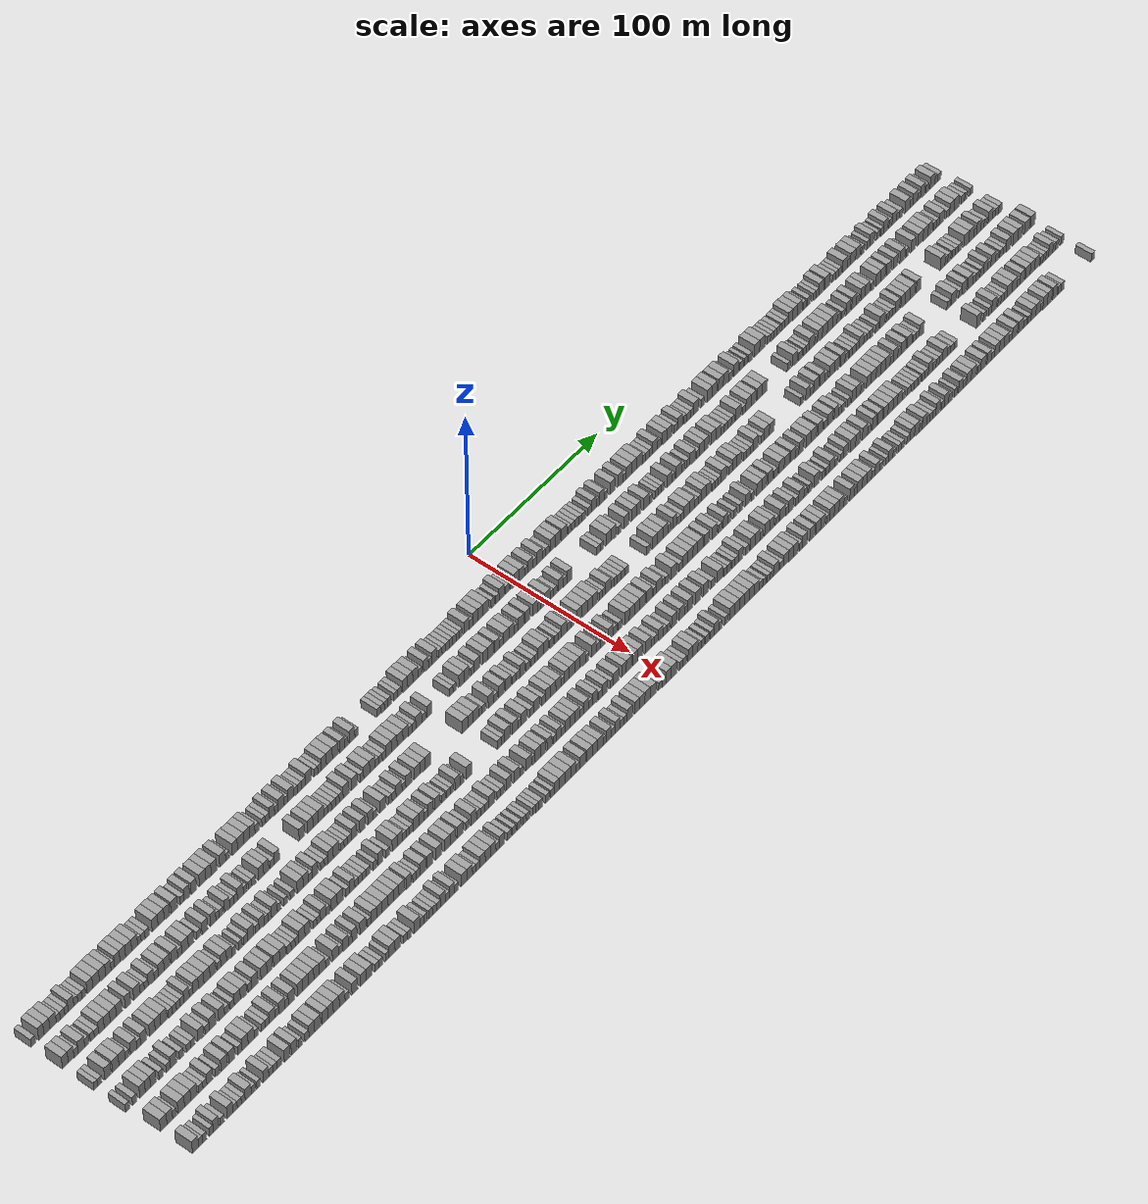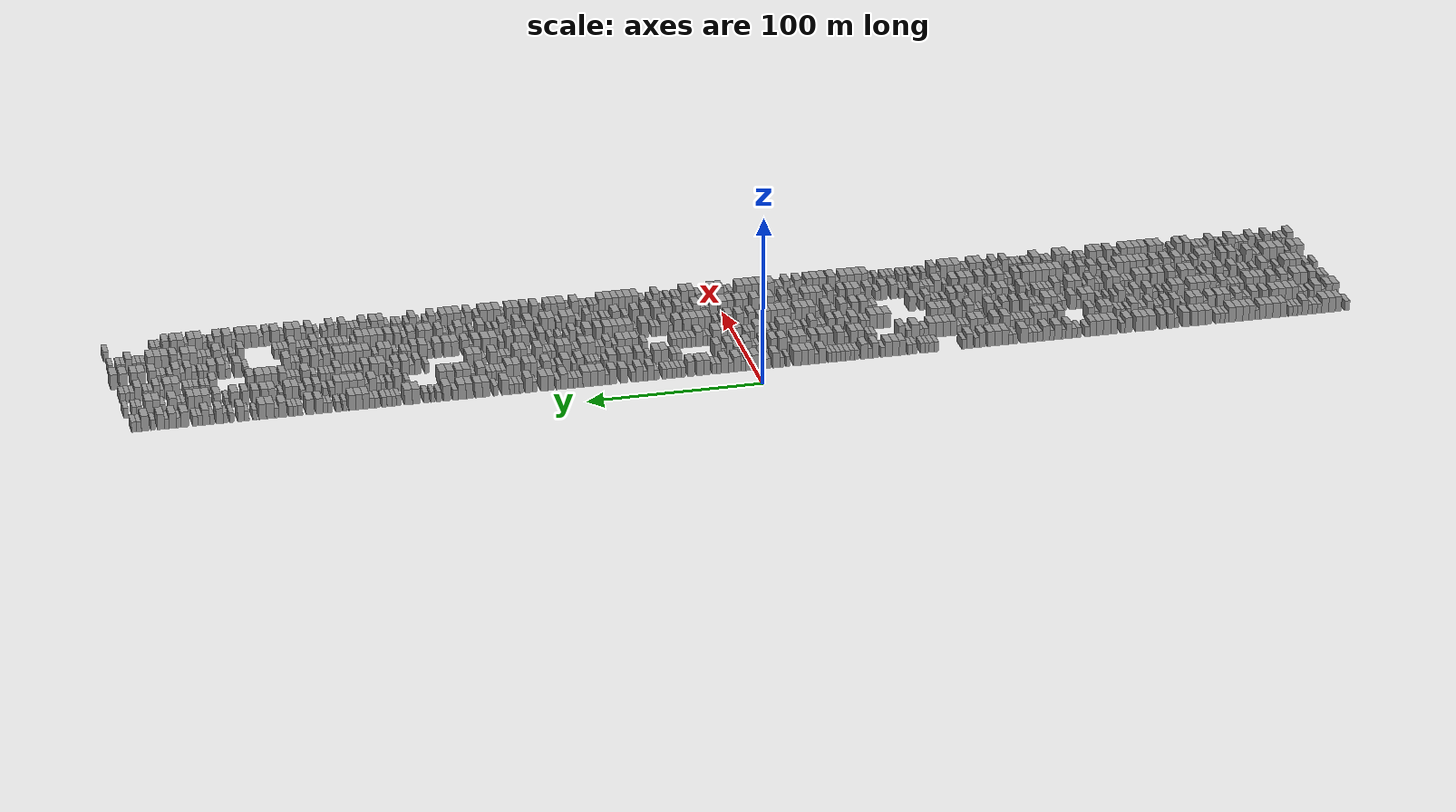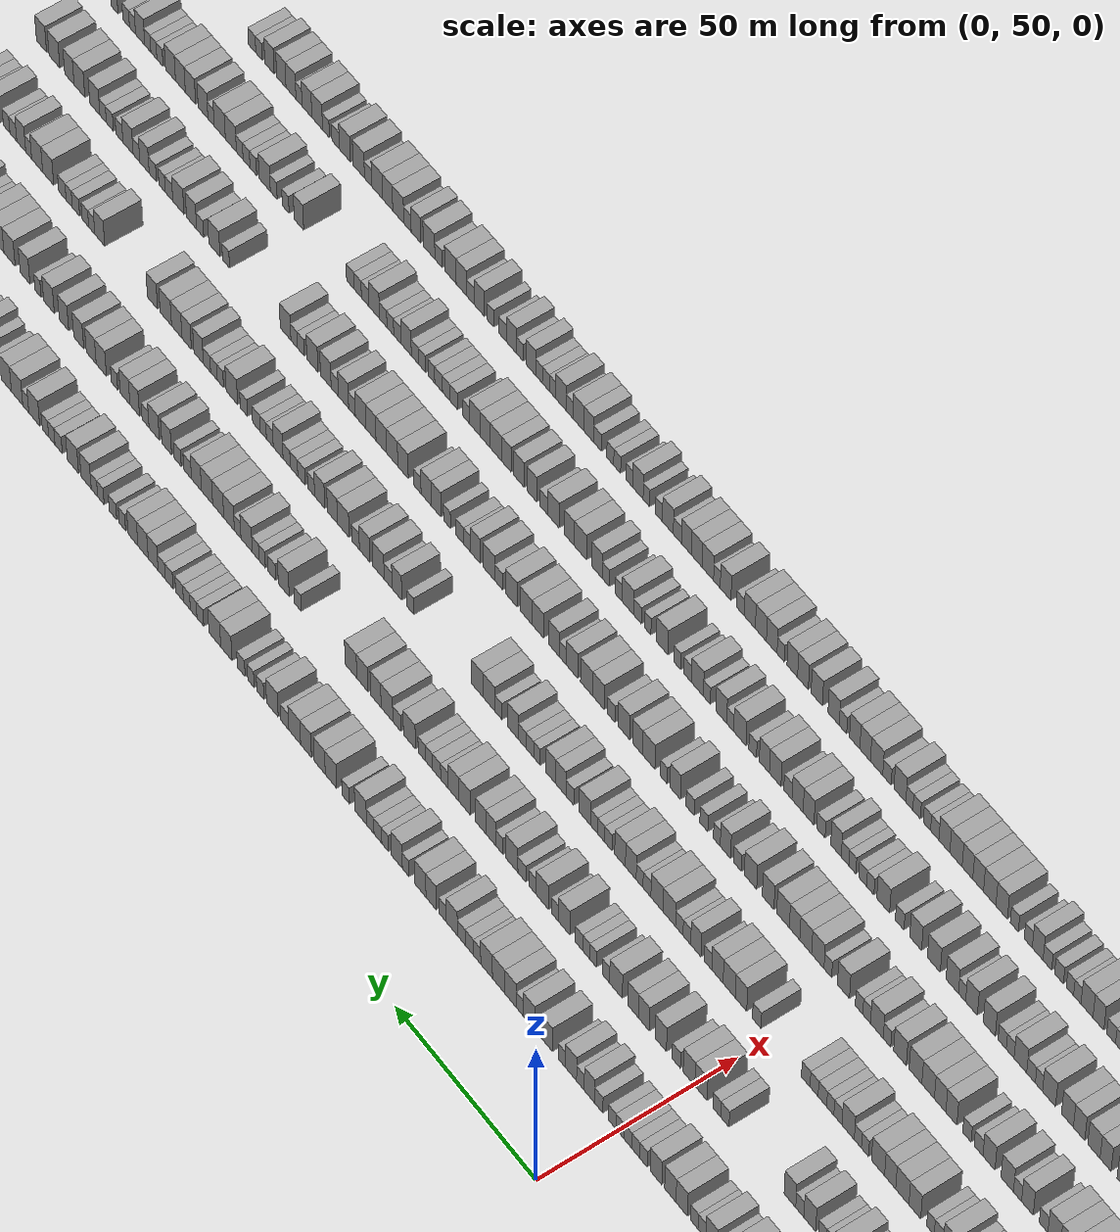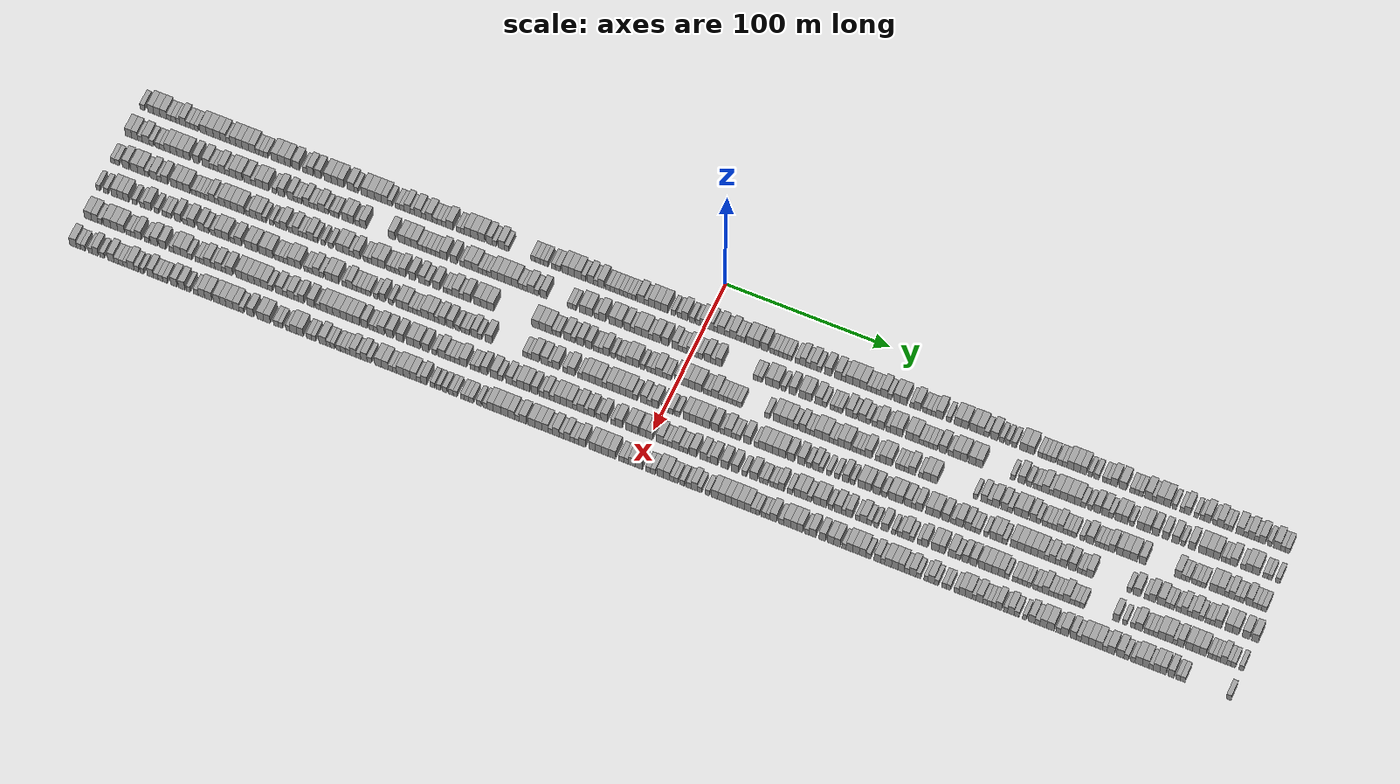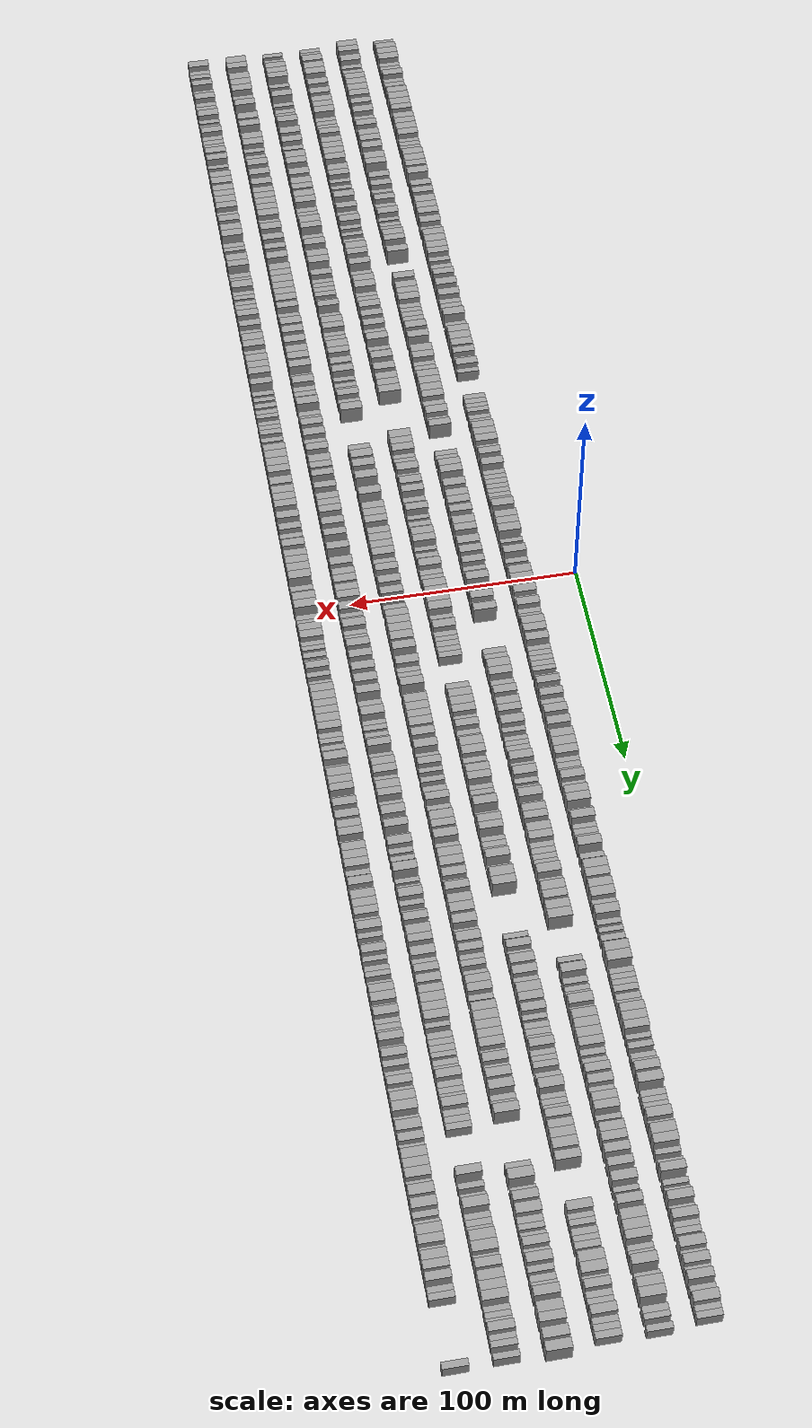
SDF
<sdf version="1.6">
 <world name="default">
  <scene>
   <sky><clouds><speed>12</speed></clouds></sky>
   <ambient>0.4 0.4 0.4 1</ambient>
   <background>0.7 0.7 0.7 1</background>
   <shadows>1</shadows>
  </scene>
  <gravity>0 0 -9.8066</gravity>
  <magnetic_field>6e-06 2.3e-05 -4.2e-05</magnetic_field>
  <physics default="0" name="default_physics" type="ode">
   <ode>
    <solver>
     <type>quick</type>
     <iters>10</iters>
     <sor>1.0</sor>
     <use_dynamic_moi_rescaling>0</use_dynamic_moi_rescaling>
    </solver>
    <constraints>
     <cfm>0</cfm>
     <erp>0.2</erp>
     <contact_max_correcting_vel>100</contact_max_correcting_vel>
     <contact_surface_layer>0.001</contact_surface_layer>
    </constraints>
   </ode>
   <max_step_size>0.004</max_step_size>
   <real_time_factor>1</real_time_factor>
   <real_time_update_rate>250</real_time_update_rate>
  </physics>
  <light name="sun" type="directional">
   <pose>0 0 10 0 0 0</pose>
   <diffuse>0.8 0.8 0.8 1</diffuse>
   <specular>0.2 0.2 0.2 1</specular>
   <attenuation>
    <range>1000</range>
    <constant>0.9</constant>
    <linear>0.01</linear>
    <quadratic>0.001</quadratic>
   </attenuation>
   <direction>-0.5 0.1 -0.9</direction>
  </light>
  <model name="building_1">
   <static>1</static>
   <pose>25.0000 -348.5133 0 0.000000 0.000000 0.000000</pose>
   <link name="link">
    <pose>0 0 3.00 0 0 0</pose>
    <collision name="collision"><geometry><box><size>10.0000 2.9734 6.0000</size></box></geometry></collision>
    <visual name="visual">
     <cast_shadows>0</cast_shadows>
     <geometry><box><size>10.0000 2.9734 6.0000</size></box></geometry>
     <material>
      <script>
       <uri>model://grey_wall/materials/scripts</uri>
       <uri>model://grey_wall/materials/textures</uri>
       <name>vrc/grey_wall</name>
      </script>
     </material>
    </visual>
   </link>
  </model>
  <model name="building_2">
   <static>1</static>
   <pose>25.0000 -343.2179 0 0.000000 0.000000 0.000000</pose>
   <link name="link">
    <pose>0 0 4.50 0 0 0</pose>
    <collision name="collision"><geometry><box><size>10.0000 3.6172 9.0000</size></box></geometry></collision>
    <visual name="visual">
     <cast_shadows>0</cast_shadows>
     <geometry><box><size>10.0000 3.6172 9.0000</size></box></geometry>
     <material>
      <script>
       <uri>model://grey_wall/materials/scripts</uri>
       <uri>model://grey_wall/materials/textures</uri>
       <name>vrc/grey_wall</name>
      </script>
     </material>
    </visual>
   </link>
  </model>
  <model name="building_3">
   <static>1</static>
   <pose>25.0000 -339.4015 0 0.000000 0.000000 0.000000</pose>
   <link name="link">
    <pose>0 0 4.50 0 0 0</pose>
    <collision name="collision"><geometry><box><size>10.0000 4.0156 9.0000</size></box></geometry></collision>
    <visual name="visual">
     <cast_shadows>0</cast_shadows>
     <geometry><box><size>10.0000 4.0156 9.0000</size></box></geometry>
     <material>
      <script>
       <uri>model://grey_wall/materials/scripts</uri>
       <uri>model://grey_wall/materials/textures</uri>
       <name>vrc/grey_wall</name>
      </script>
     </material>
    </visual>
   </link>
  </model>
  <model name="building_4">
   <static>1</static>
   <pose>25.0000 -335.2594 0 0.000000 0.000000 0.000000</pose>
   <link name="link">
    <pose>0 0 4.50 0 0 0</pose>
    <collision name="collision"><geometry><box><size>10.0000 4.2686 9.0000</size></box></geometry></collision>
    <visual name="visual">
     <cast_shadows>0</cast_shadows>
     <geometry><box><size>10.0000 4.2686 9.0000</size></box></geometry>
     <material>
      <script>
       <uri>model://grey_wall/materials/scripts</uri>
       <uri>model://grey_wall/materials/textures</uri>
       <name>vrc/grey_wall</name>
      </script>
     </material>
    </visual>
   </link>
  </model>
  <model name="building_5">
   <static>1</static>
   <pose>25.0000 -331.7794 0 0.000000 0.000000 0.000000</pose>
   <link name="link">
    <pose>0 0 3.00 0 0 0</pose>
    <collision name="collision"><geometry><box><size>10.0000 2.6914 6.0000</size></box></geometry></collision>
    <visual name="visual">
     <cast_shadows>0</cast_shadows>
     <geometry><box><size>10.0000 2.6914 6.0000</size></box></geometry>
     <material>
      <script>
       <uri>model://grey_wall/materials/scripts</uri>
       <uri>model://grey_wall/materials/textures</uri>
       <name>vrc/grey_wall</name>
      </script>
     </material>
    </visual>
   </link>
  </model>
  <model name="building_6">
   <static>1</static>
   <pose>25.0000 -328.9396 0 0.000000 0.000000 0.000000</pose>
   <link name="link">
    <pose>0 0 3.00 0 0 0</pose>
    <collision name="collision"><geometry><box><size>10.0000 2.9883 6.0000</size></box></geometry></collision>
    <visual name="visual">
     <cast_shadows>0</cast_shadows>
     <geometry><box><size>10.0000 2.9883 6.0000</size></box></geometry>
     <material>
      <script>
       <uri>model://grey_wall/materials/scripts</uri>
       <uri>model://grey_wall/materials/textures</uri>
       <name>vrc/grey_wall</name>
      </script>
     </material>
    </visual>
   </link>
  </model>
  <model name="building_7">
   <static>1</static>
   <pose>25.0000 -326.2206 0 0.000000 0.000000 0.000000</pose>
   <link name="link">
    <pose>0 0 3.00 0 0 0</pose>
    <collision name="collision"><geometry><box><size>10.0000 2.4496 6.0000</size></box></geometry></collision>
    <visual name="visual">
     <cast_shadows>0</cast_shadows>
     <geometry><box><size>10.0000 2.4496 6.0000</size></box></geometry>
     <material>
      <script>
       <uri>model://grey_wall/materials/scripts</uri>
       <uri>model://grey_wall/materials/textures</uri>
       <name>vrc/grey_wall</name>
      </script>
     </material>
    </visual>
   </link>
  </model>
  <model name="building_8">
   <static>1</static>
   <pose>25.0000 -323.1058 0 0.000000 0.000000 0.000000</pose>
   <link name="link">
    <pose>0 0 4.50 0 0 0</pose>
    <collision name="collision"><geometry><box><size>10.0000 3.7800 9.0000</size></box></geometry></collision>
    <visual name="visual">
     <cast_shadows>0</cast_shadows>
     <geometry><box><size>10.0000 3.7800 9.0000</size></box></geometry>
     <material>
      <script>
       <uri>model://grey_wall/materials/scripts</uri>
       <uri>model://grey_wall/materials/textures</uri>
       <name>vrc/grey_wall</name>
      </script>
     </material>
    </visual>
   </link>
  </model>
  <model name="building_9">
   <static>1</static>
   <pose>25.0000 -319.8751 0 0.000000 0.000000 0.000000</pose>
   <link name="link">
    <pose>0 0 3.00 0 0 0</pose>
    <collision name="collision"><geometry><box><size>10.0000 2.6815 6.0000</size></box></geometry></collision>
    <visual name="visual">
     <cast_shadows>0</cast_shadows>
     <geometry><box><size>10.0000 2.6815 6.0000</size></box></geometry>
     <material>
      <script>
       <uri>model://grey_wall/materials/scripts</uri>
       <uri>model://grey_wall/materials/textures</uri>
       <name>vrc/grey_wall</name>
      </script>
     </material>
    </visual>
   </link>
  </model>
  <model name="building_10">
   <static>1</static>
   <pose>25.0000 -317.1587 0 0.000000 0.000000 0.000000</pose>
   <link name="link">
    <pose>0 0 3.00 0 0 0</pose>
    <collision name="collision"><geometry><box><size>10.0000 2.7513 6.0000</size></box></geometry></collision>
    <visual name="visual">
     <cast_shadows>0</cast_shadows>
     <geometry><box><size>10.0000 2.7513 6.0000</size></box></geometry>
     <material>
      <script>
       <uri>model://grey_wall/materials/scripts</uri>
       <uri>model://grey_wall/materials/textures</uri>
       <name>vrc/grey_wall</name>
      </script>
     </material>
    </visual>
   </link>
  </model>
  <model name="building_11">
   <static>1</static>
   <pose>25.0000 -314.4762 0 0.000000 0.000000 0.000000</pose>
   <link name="link">
    <pose>0 0 3.00 0 0 0</pose>
    <collision name="collision"><geometry><box><size>10.0000 2.6137 6.0000</size></box></geometry></collision>
    <visual name="visual">
     <cast_shadows>0</cast_shadows>
     <geometry><box><size>10.0000 2.6137 6.0000</size></box></geometry>
     <material>
      <script>
       <uri>model://grey_wall/materials/scripts</uri>
       <uri>model://grey_wall/materials/textures</uri>
       <name>vrc/grey_wall</name>
      </script>
     </material>
    </visual>
   </link>
  </model>
  <model name="building_12">
   <static>1</static>
   <pose>25.0000 -310.1985 0 0.000000 0.000000 0.000000</pose>
   <link name="link">
    <pose>0 0 4.50 0 0 0</pose>
    <collision name="collision"><geometry><box><size>10.0000 3.9417 9.0000</size></box></geometry></collision>
    <visual name="visual">
     <cast_shadows>0</cast_shadows>
     <geometry><box><size>10.0000 3.9417 9.0000</size></box></geometry>
     <material>
      <script>
       <uri>model://grey_wall/materials/scripts</uri>
       <uri>model://grey_wall/materials/textures</uri>
       <name>vrc/grey_wall</name>
      </script>
     </material>
    </visual>
   </link>
  </model>
  <model name="building_13">
   <static>1</static>
   <pose>25.0000 -306.0023 0 0.000000 0.000000 0.000000</pose>
   <link name="link">
    <pose>0 0 4.50 0 0 0</pose>
    <collision name="collision"><geometry><box><size>10.0000 4.4508 9.0000</size></box></geometry></collision>
    <visual name="visual">
     <cast_shadows>0</cast_shadows>
     <geometry><box><size>10.0000 4.4508 9.0000</size></box></geometry>
     <material>
      <script>
       <uri>model://grey_wall/materials/scripts</uri>
       <uri>model://grey_wall/materials/textures</uri>
       <name>vrc/grey_wall</name>
      </script>
     </material>
    </visual>
   </link>
  </model>
  <model name="building_14">
   <static>1</static>
   <pose>25.0000 -301.6428 0 0.000000 0.000000 0.000000</pose>
   <link name="link">
    <pose>0 0 4.50 0 0 0</pose>
    <collision name="collision"><geometry><box><size>10.0000 4.2681 9.0000</size></box></geometry></collision>
    <visual name="visual">
     <cast_shadows>0</cast_shadows>
     <geometry><box><size>10.0000 4.2681 9.0000</size></box></geometry>
     <material>
      <script>
       <uri>model://grey_wall/materials/scripts</uri>
       <uri>model://grey_wall/materials/textures</uri>
       <name>vrc/grey_wall</name>
      </script>
     </material>
    </visual>
   </link>
  </model>
  <model name="building_15">
   <static>1</static>
   <pose>25.0000 -297.6987 0 0.000000 0.000000 0.000000</pose>
   <link name="link">
    <pose>0 0 4.50 0 0 0</pose>
    <collision name="collision"><geometry><box><size>10.0000 3.6200 9.0000</size></box></geometry></collision>
    <visual name="visual">
     <cast_shadows>0</cast_shadows>
     <geometry><box><size>10.0000 3.6200 9.0000</size></box></geometry>
     <material>
      <script>
       <uri>model://grey_wall/materials/scripts</uri>
       <uri>model://grey_wall/materials/textures</uri>
       <name>vrc/grey_wall</name>
      </script>
     </material>
    </visual>
   </link>
  </model>
  <model name="building_16">
   <static>1</static>
   <pose>25.0000 -294.6243 0 0.000000 0.000000 0.000000</pose>
   <link name="link">
    <pose>0 0 3.00 0 0 0</pose>
    <collision name="collision"><geometry><box><size>10.0000 2.5290 6.0000</size></box></geometry></collision>
    <visual name="visual">
     <cast_shadows>0</cast_shadows>
     <geometry><box><size>10.0000 2.5290 6.0000</size></box></geometry>
     <material>
      <script>
       <uri>model://grey_wall/materials/scripts</uri>
       <uri>model://grey_wall/materials/textures</uri>
       <name>vrc/grey_wall</name>
      </script>
     </material>
    </visual>
   </link>
  </model>
  <model name="building_17">
   <static>1</static>
   <pose>25.0000 -291.4943 0 0.000000 0.000000 0.000000</pose>
   <link name="link">
    <pose>0 0 4.50 0 0 0</pose>
    <collision name="collision"><geometry><box><size>10.0000 3.7310 9.0000</size></box></geometry></collision>
    <visual name="visual">
     <cast_shadows>0</cast_shadows>
     <geometry><box><size>10.0000 3.7310 9.0000</size></box></geometry>
     <material>
      <script>
       <uri>model://grey_wall/materials/scripts</uri>
       <uri>model://grey_wall/materials/textures</uri>
       <name>vrc/grey_wall</name>
      </script>
     </material>
    </visual>
   </link>
  </model>
  <model name="building_18">
   <static>1</static>
   <pose>25.0000 -287.7493 0 0.000000 0.000000 0.000000</pose>
   <link name="link">
    <pose>0 0 4.50 0 0 0</pose>
    <collision name="collision"><geometry><box><size>10.0000 3.7588 9.0000</size></box></geometry></collision>
    <visual name="visual">
     <cast_shadows>0</cast_shadows>
     <geometry><box><size>10.0000 3.7588 9.0000</size></box></geometry>
     <material>
      <script>
       <uri>model://grey_wall/materials/scripts</uri>
       <uri>model://grey_wall/materials/textures</uri>
       <name>vrc/grey_wall</name>
      </script>
     </material>
    </visual>
   </link>
  </model>
  <model name="building_19">
   <static>1</static>
   <pose>25.0000 -283.7377 0 0.000000 0.000000 0.000000</pose>
   <link name="link">
    <pose>0 0 4.50 0 0 0</pose>
    <collision name="collision"><geometry><box><size>10.0000 4.2644 9.0000</size></box></geometry></collision>
    <visual name="visual">
     <cast_shadows>0</cast_shadows>
     <geometry><box><size>10.0000 4.2644 9.0000</size></box></geometry>
     <material>
      <script>
       <uri>model://grey_wall/materials/scripts</uri>
       <uri>model://grey_wall/materials/textures</uri>
       <name>vrc/grey_wall</name>
      </script>
     </material>
    </visual>
   </link>
  </model>
  <model name="building_20">
   <static>1</static>
   <pose>25.0000 -279.5425 0 0.000000 0.000000 0.000000</pose>
   <link name="link">
    <pose>0 0 4.50 0 0 0</pose>
    <collision name="collision"><geometry><box><size>10.0000 4.1260 9.0000</size></box></geometry></collision>
    <visual name="visual">
     <cast_shadows>0</cast_shadows>
     <geometry><box><size>10.0000 4.1260 9.0000</size></box></geometry>
     <material>
      <script>
       <uri>model://grey_wall/materials/scripts</uri>
       <uri>model://grey_wall/materials/textures</uri>
       <name>vrc/grey_wall</name>
      </script>
     </material>
    </visual>
   </link>
  </model>
  <model name="building_21">
   <static>1</static>
   <pose>25.0000 -276.2781 0 0.000000 0.000000 0.000000</pose>
   <link name="link">
    <pose>0 0 3.00 0 0 0</pose>
    <collision name="collision"><geometry><box><size>10.0000 2.4028 6.0000</size></box></geometry></collision>
    <visual name="visual">
     <cast_shadows>0</cast_shadows>
     <geometry><box><size>10.0000 2.4028 6.0000</size></box></geometry>
     <material>
      <script>
       <uri>model://grey_wall/materials/scripts</uri>
       <uri>model://grey_wall/materials/textures</uri>
       <name>vrc/grey_wall</name>
      </script>
     </material>
    </visual>
   </link>
  </model>
  <model name="building_22">
   <static>1</static>
   <pose>25.0000 -273.7271 0 0.000000 0.000000 0.000000</pose>
   <link name="link">
    <pose>0 0 3.00 0 0 0</pose>
    <collision name="collision"><geometry><box><size>10.0000 2.6993 6.0000</size></box></geometry></collision>
    <visual name="visual">
     <cast_shadows>0</cast_shadows>
     <geometry><box><size>10.0000 2.6993 6.0000</size></box></geometry>
     <material>
      <script>
       <uri>model://grey_wall/materials/scripts</uri>
       <uri>model://grey_wall/materials/textures</uri>
       <name>vrc/grey_wall</name>
      </script>
     </material>
    </visual>
   </link>
  </model>
  <model name="building_23">
   <static>1</static>
   <pose>25.0000 -270.9272 0 0.000000 0.000000 0.000000</pose>
   <link name="link">
    <pose>0 0 3.00 0 0 0</pose>
    <collision name="collision"><geometry><box><size>10.0000 2.9005 6.0000</size></box></geometry></collision>
    <visual name="visual">
     <cast_shadows>0</cast_shadows>
     <geometry><box><size>10.0000 2.9005 6.0000</size></box></geometry>
     <material>
      <script>
       <uri>model://grey_wall/materials/scripts</uri>
       <uri>model://grey_wall/materials/textures</uri>
       <name>vrc/grey_wall</name>
      </script>
     </material>
    </visual>
   </link>
  </model>
  <model name="building_24">
   <static>1</static>
   <pose>25.0000 -265.4210 0 0.000000 0.000000 0.000000</pose>
   <link name="link">
    <pose>0 0 4.50 0 0 0</pose>
    <collision name="collision"><geometry><box><size>10.0000 4.1118 9.0000</size></box></geometry></collision>
    <visual name="visual">
     <cast_shadows>0</cast_shadows>
     <geometry><box><size>10.0000 4.1118 9.0000</size></box></geometry>
     <material>
      <script>
       <uri>model://grey_wall/materials/scripts</uri>
       <uri>model://grey_wall/materials/textures</uri>
       <name>vrc/grey_wall</name>
      </script>
     </material>
    </visual>
   </link>
  </model>
  <model name="building_25">
   <static>1</static>
   <pose>25.0000 -261.1792 0 0.000000 0.000000 0.000000</pose>
   <link name="link">
    <pose>0 0 4.50 0 0 0</pose>
    <collision name="collision"><geometry><box><size>10.0000 4.3719 9.0000</size></box></geometry></collision>
    <visual name="visual">
     <cast_shadows>0</cast_shadows>
     <geometry><box><size>10.0000 4.3719 9.0000</size></box></geometry>
     <material>
      <script>
       <uri>model://grey_wall/materials/scripts</uri>
       <uri>model://grey_wall/materials/textures</uri>
       <name>vrc/grey_wall</name>
      </script>
     </material>
    </visual>
   </link>
  </model>
  <model name="building_26">
   <static>1</static>
   <pose>25.0000 -257.1302 0 0.000000 0.000000 0.000000</pose>
   <link name="link">
    <pose>0 0 4.50 0 0 0</pose>
    <collision name="collision"><geometry><box><size>10.0000 3.7260 9.0000</size></box></geometry></collision>
    <visual name="visual">
     <cast_shadows>0</cast_shadows>
     <geometry><box><size>10.0000 3.7260 9.0000</size></box></geometry>
     <material>
      <script>
       <uri>model://grey_wall/materials/scripts</uri>
       <uri>model://grey_wall/materials/textures</uri>
       <name>vrc/grey_wall</name>
      </script>
     </material>
    </visual>
   </link>
  </model>
  <model name="building_27">
   <static>1</static>
   <pose>25.0000 -252.0744 0 0.000000 0.000000 0.000000</pose>
   <link name="link">
    <pose>0 0 4.50 0 0 0</pose>
    <collision name="collision"><geometry><box><size>10.0000 4.3856 9.0000</size></box></geometry></collision>
    <visual name="visual">
     <cast_shadows>0</cast_shadows>
     <geometry><box><size>10.0000 4.3856 9.0000</size></box></geometry>
     <material>
      <script>
       <uri>model://grey_wall/materials/scripts</uri>
       <uri>model://grey_wall/materials/textures</uri>
       <name>vrc/grey_wall</name>
      </script>
     </material>
    </visual>
   </link>
  </model>
  <model name="building_28">
   <static>1</static>
   <pose>25.0000 -246.5274 0 0.000000 0.000000 0.000000</pose>
   <link name="link">
    <pose>0 0 3.00 0 0 0</pose>
    <collision name="collision"><geometry><box><size>10.0000 2.7085 6.0000</size></box></geometry></collision>
    <visual name="visual">
     <cast_shadows>0</cast_shadows>
     <geometry><box><size>10.0000 2.7085 6.0000</size></box></geometry>
     <material>
      <script>
       <uri>model://grey_wall/materials/scripts</uri>
       <uri>model://grey_wall/materials/textures</uri>
       <name>vrc/grey_wall</name>
      </script>
     </material>
    </visual>
   </link>
  </model>
  <model name="building_29">
   <static>1</static>
   <pose>25.0000 -243.2222 0 0.000000 0.000000 0.000000</pose>
   <link name="link">
    <pose>0 0 4.50 0 0 0</pose>
    <collision name="collision"><geometry><box><size>10.0000 3.9018 9.0000</size></box></geometry></collision>
    <visual name="visual">
     <cast_shadows>0</cast_shadows>
     <geometry><box><size>10.0000 3.9018 9.0000</size></box></geometry>
     <material>
      <script>
       <uri>model://grey_wall/materials/scripts</uri>
       <uri>model://grey_wall/materials/textures</uri>
       <name>vrc/grey_wall</name>
      </script>
     </material>
    </visual>
   </link>
  </model>
  <model name="building_30">
   <static>1</static>
   <pose>25.0000 -238.3244 0 0.000000 0.000000 0.000000</pose>
   <link name="link">
    <pose>0 0 4.50 0 0 0</pose>
    <collision name="collision"><geometry><box><size>10.0000 3.8939 9.0000</size></box></geometry></collision>
    <visual name="visual">
     <cast_shadows>0</cast_shadows>
     <geometry><box><size>10.0000 3.8939 9.0000</size></box></geometry>
     <material>
      <script>
       <uri>model://grey_wall/materials/scripts</uri>
       <uri>model://grey_wall/materials/textures</uri>
       <name>vrc/grey_wall</name>
      </script>
     </material>
    </visual>
   </link>
  </model>
  <model name="building_31">
   <static>1</static>
   <pose>25.0000 -232.1610 0 0.000000 0.000000 0.000000</pose>
   <link name="link">
    <pose>0 0 4.50 0 0 0</pose>
    <collision name="collision"><geometry><box><size>10.0000 4.4328 9.0000</size></box></geometry></collision>
    <visual name="visual">
     <cast_shadows>0</cast_shadows>
     <geometry><box><size>10.0000 4.4328 9.0000</size></box></geometry>
     <material>
      <script>
       <uri>model://grey_wall/materials/scripts</uri>
       <uri>model://grey_wall/materials/textures</uri>
       <name>vrc/grey_wall</name>
      </script>
     </material>
    </visual>
   </link>
  </model>
  <model name="building_32">
   <static>1</static>
   <pose>25.0000 -228.0159 0 0.000000 0.000000 0.000000</pose>
   <link name="link">
    <pose>0 0 4.50 0 0 0</pose>
    <collision name="collision"><geometry><box><size>10.0000 3.8574 9.0000</size></box></geometry></collision>
    <visual name="visual">
     <cast_shadows>0</cast_shadows>
     <geometry><box><size>10.0000 3.8574 9.0000</size></box></geometry>
     <material>
      <script>
       <uri>model://grey_wall/materials/scripts</uri>
       <uri>model://grey_wall/materials/textures</uri>
       <name>vrc/grey_wall</name>
      </script>
     </material>
    </visual>
   </link>
  </model>
  <model name="building_33">
   <static>1</static>
   <pose>25.0000 -224.1071 0 0.000000 0.000000 0.000000</pose>
   <link name="link">
    <pose>0 0 4.50 0 0 0</pose>
    <collision name="collision"><geometry><box><size>10.0000 3.9602 9.0000</size></box></geometry></collision>
    <visual name="visual">
     <cast_shadows>0</cast_shadows>
     <geometry><box><size>10.0000 3.9602 9.0000</size></box></geometry>
     <material>
      <script>
       <uri>model://grey_wall/materials/scripts</uri>
       <uri>model://grey_wall/materials/textures</uri>
       <name>vrc/grey_wall</name>
      </script>
     </material>
    </visual>
   </link>
  </model>
  <model name="building_34">
   <static>1</static>
   <pose>25.0000 -217.9630 0 0.000000 0.000000 0.000000</pose>
   <link name="link">
    <pose>0 0 4.50 0 0 0</pose>
    <collision name="collision"><geometry><box><size>10.0000 4.3278 9.0000</size></box></geometry></collision>
    <visual name="visual">
     <cast_shadows>0</cast_shadows>
     <geometry><box><size>10.0000 4.3278 9.0000</size></box></geometry>
     <material>
      <script>
       <uri>model://grey_wall/materials/scripts</uri>
       <uri>model://grey_wall/materials/textures</uri>
       <name>vrc/grey_wall</name>
      </script>
     </material>
    </visual>
   </link>
  </model>
  <model name="building_35">
   <static>1</static>
   <pose>25.0000 -214.5229 0 0.000000 0.000000 0.000000</pose>
   <link name="link">
    <pose>0 0 3.00 0 0 0</pose>
    <collision name="collision"><geometry><box><size>10.0000 2.5525 6.0000</size></box></geometry></collision>
    <visual name="visual">
     <cast_shadows>0</cast_shadows>
     <geometry><box><size>10.0000 2.5525 6.0000</size></box></geometry>
     <material>
      <script>
       <uri>model://grey_wall/materials/scripts</uri>
       <uri>model://grey_wall/materials/textures</uri>
       <name>vrc/grey_wall</name>
      </script>
     </material>
    </visual>
   </link>
  </model>
  <model name="building_36">
   <static>1</static>
   <pose>25.0000 -209.3218 0 0.000000 0.000000 0.000000</pose>
   <link name="link">
    <pose>0 0 4.50 0 0 0</pose>
    <collision name="collision"><geometry><box><size>10.0000 3.8499 9.0000</size></box></geometry></collision>
    <visual name="visual">
     <cast_shadows>0</cast_shadows>
     <geometry><box><size>10.0000 3.8499 9.0000</size></box></geometry>
     <material>
      <script>
       <uri>model://grey_wall/materials/scripts</uri>
       <uri>model://grey_wall/materials/textures</uri>
       <name>vrc/grey_wall</name>
      </script>
     </material>
    </visual>
   </link>
  </model>
  <model name="building_37">
   <static>1</static>
   <pose>25.0000 -205.1560 0 0.000000 0.000000 0.000000</pose>
   <link name="link">
    <pose>0 0 4.50 0 0 0</pose>
    <collision name="collision"><geometry><box><size>10.0000 4.4816 9.0000</size></box></geometry></collision>
    <visual name="visual">
     <cast_shadows>0</cast_shadows>
     <geometry><box><size>10.0000 4.4816 9.0000</size></box></geometry>
     <material>
      <script>
       <uri>model://grey_wall/materials/scripts</uri>
       <uri>model://grey_wall/materials/textures</uri>
       <name>vrc/grey_wall</name>
      </script>
     </material>
    </visual>
   </link>
  </model>
  <model name="building_38">
   <static>1</static>
   <pose>25.0000 -200.8313 0 0.000000 0.000000 0.000000</pose>
   <link name="link">
    <pose>0 0 4.50 0 0 0</pose>
    <collision name="collision"><geometry><box><size>10.0000 4.1680 9.0000</size></box></geometry></collision>
    <visual name="visual">
     <cast_shadows>0</cast_shadows>
     <geometry><box><size>10.0000 4.1680 9.0000</size></box></geometry>
     <material>
      <script>
       <uri>model://grey_wall/materials/scripts</uri>
       <uri>model://grey_wall/materials/textures</uri>
       <name>vrc/grey_wall</name>
      </script>
     </material>
    </visual>
   </link>
  </model>
  <model name="building_39">
   <static>1</static>
   <pose>25.0000 -196.8950 0 0.000000 0.000000 0.000000</pose>
   <link name="link">
    <pose>0 0 4.50 0 0 0</pose>
    <collision name="collision"><geometry><box><size>10.0000 3.7047 9.0000</size></box></geometry></collision>
    <visual name="visual">
     <cast_shadows>0</cast_shadows>
     <geometry><box><size>10.0000 3.7047 9.0000</size></box></geometry>
     <material>
      <script>
       <uri>model://grey_wall/materials/scripts</uri>
       <uri>model://grey_wall/materials/textures</uri>
       <name>vrc/grey_wall</name>
      </script>
     </material>
    </visual>
   </link>
  </model>
  <model name="building_40">
   <static>1</static>
   <pose>25.0000 -193.5563 0 0.000000 0.000000 0.000000</pose>
   <link name="link">
    <pose>0 0 3.00 0 0 0</pose>
    <collision name="collision"><geometry><box><size>10.0000 2.9726 6.0000</size></box></geometry></collision>
    <visual name="visual">
     <cast_shadows>0</cast_shadows>
     <geometry><box><size>10.0000 2.9726 6.0000</size></box></geometry>
     <material>
      <script>
       <uri>model://grey_wall/materials/scripts</uri>
       <uri>model://grey_wall/materials/textures</uri>
       <name>vrc/grey_wall</name>
      </script>
     </material>
    </visual>
   </link>
  </model>
  <model name="building_41">
   <static>1</static>
   <pose>25.0000 -188.7504 0 0.000000 0.000000 0.000000</pose>
   <link name="link">
    <pose>0 0 3.00 0 0 0</pose>
    <collision name="collision"><geometry><box><size>10.0000 2.6392 6.0000</size></box></geometry></collision>
    <visual name="visual">
     <cast_shadows>0</cast_shadows>
     <geometry><box><size>10.0000 2.6392 6.0000</size></box></geometry>
     <material>
      <script>
       <uri>model://grey_wall/materials/scripts</uri>
       <uri>model://grey_wall/materials/textures</uri>
       <name>vrc/grey_wall</name>
      </script>
     </material>
    </visual>
   </link>
  </model>
  <model name="building_42">
   <static>1</static>
   <pose>25.0000 -185.9956 0 0.000000 0.000000 0.000000</pose>
   <link name="link">
    <pose>0 0 3.00 0 0 0</pose>
    <collision name="collision"><geometry><box><size>10.0000 2.8704 6.0000</size></box></geometry></collision>
    <visual name="visual">
     <cast_shadows>0</cast_shadows>
     <geometry><box><size>10.0000 2.8704 6.0000</size></box></geometry>
     <material>
      <script>
       <uri>model://grey_wall/materials/scripts</uri>
       <uri>model://grey_wall/materials/textures</uri>
       <name>vrc/grey_wall</name>
      </script>
     </material>
    </visual>
   </link>
  </model>
  <model name="building_43">
   <static>1</static>
   <pose>25.0000 -182.7446 0 0.000000 0.000000 0.000000</pose>
   <link name="link">
    <pose>0 0 4.50 0 0 0</pose>
    <collision name="collision"><geometry><box><size>10.0000 3.6316 9.0000</size></box></geometry></collision>
    <visual name="visual">
     <cast_shadows>0</cast_shadows>
     <geometry><box><size>10.0000 3.6316 9.0000</size></box></geometry>
     <material>
      <script>
       <uri>model://grey_wall/materials/scripts</uri>
       <uri>model://grey_wall/materials/textures</uri>
       <name>vrc/grey_wall</name>
      </script>
     </material>
    </visual>
   </link>
  </model>
  <model name="building_44">
   <static>1</static>
   <pose>25.0000 -179.6459 0 0.000000 0.000000 0.000000</pose>
   <link name="link">
    <pose>0 0 3.00 0 0 0</pose>
    <collision name="collision"><geometry><box><size>10.0000 2.5658 6.0000</size></box></geometry></collision>
    <visual name="visual">
     <cast_shadows>0</cast_shadows>
     <geometry><box><size>10.0000 2.5658 6.0000</size></box></geometry>
     <material>
      <script>
       <uri>model://grey_wall/materials/scripts</uri>
       <uri>model://grey_wall/materials/textures</uri>
       <name>vrc/grey_wall</name>
      </script>
     </material>
    </visual>
   </link>
  </model>
  <model name="building_45">
   <static>1</static>
   <pose>25.0000 -176.2125 0 0.000000 0.000000 0.000000</pose>
   <link name="link">
    <pose>0 0 4.50 0 0 0</pose>
    <collision name="collision"><geometry><box><size>10.0000 4.3010 9.0000</size></box></geometry></collision>
    <visual name="visual">
     <cast_shadows>0</cast_shadows>
     <geometry><box><size>10.0000 4.3010 9.0000</size></box></geometry>
     <material>
      <script>
       <uri>model://grey_wall/materials/scripts</uri>
       <uri>model://grey_wall/materials/textures</uri>
       <name>vrc/grey_wall</name>
      </script>
     </material>
    </visual>
   </link>
  </model>
  <model name="building_46">
   <static>1</static>
   <pose>25.0000 -172.7263 0 0.000000 0.000000 0.000000</pose>
   <link name="link">
    <pose>0 0 3.00 0 0 0</pose>
    <collision name="collision"><geometry><box><size>10.0000 2.6714 6.0000</size></box></geometry></collision>
    <visual name="visual">
     <cast_shadows>0</cast_shadows>
     <geometry><box><size>10.0000 2.6714 6.0000</size></box></geometry>
     <material>
      <script>
       <uri>model://grey_wall/materials/scripts</uri>
       <uri>model://grey_wall/materials/textures</uri>
       <name>vrc/grey_wall</name>
      </script>
     </material>
    </visual>
   </link>
  </model>
  <model name="building_47">
   <static>1</static>
   <pose>25.0000 -169.2752 0 0.000000 0.000000 0.000000</pose>
   <link name="link">
    <pose>0 0 4.50 0 0 0</pose>
    <collision name="collision"><geometry><box><size>10.0000 4.2307 9.0000</size></box></geometry></collision>
    <visual name="visual">
     <cast_shadows>0</cast_shadows>
     <geometry><box><size>10.0000 4.2307 9.0000</size></box></geometry>
     <material>
      <script>
       <uri>model://grey_wall/materials/scripts</uri>
       <uri>model://grey_wall/materials/textures</uri>
       <name>vrc/grey_wall</name>
      </script>
     </material>
    </visual>
   </link>
  </model>
  <model name="building_48">
   <static>1</static>
   <pose>25.0000 -165.7712 0 0.000000 0.000000 0.000000</pose>
   <link name="link">
    <pose>0 0 3.00 0 0 0</pose>
    <collision name="collision"><geometry><box><size>10.0000 2.7773 6.0000</size></box></geometry></collision>
    <visual name="visual">
     <cast_shadows>0</cast_shadows>
     <geometry><box><size>10.0000 2.7773 6.0000</size></box></geometry>
     <material>
      <script>
       <uri>model://grey_wall/materials/scripts</uri>
       <uri>model://grey_wall/materials/textures</uri>
       <name>vrc/grey_wall</name>
      </script>
     </material>
    </visual>
   </link>
  </model>
  <model name="building_49">
   <static>1</static>
   <pose>25.0000 -162.9861 0 0.000000 0.000000 0.000000</pose>
   <link name="link">
    <pose>0 0 3.00 0 0 0</pose>
    <collision name="collision"><geometry><box><size>10.0000 2.7928 6.0000</size></box></geometry></collision>
    <visual name="visual">
     <cast_shadows>0</cast_shadows>
     <geometry><box><size>10.0000 2.7928 6.0000</size></box></geometry>
     <material>
      <script>
       <uri>model://grey_wall/materials/scripts</uri>
       <uri>model://grey_wall/materials/textures</uri>
       <name>vrc/grey_wall</name>
      </script>
     </material>
    </visual>
   </link>
  </model>
  <model name="building_50">
   <static>1</static>
   <pose>25.0000 -160.1606 0 0.000000 0.000000 0.000000</pose>
   <link name="link">
    <pose>0 0 3.00 0 0 0</pose>
    <collision name="collision"><geometry><box><size>10.0000 2.8582 6.0000</size></box></geometry></collision>
    <visual name="visual">
     <cast_shadows>0</cast_shadows>
     <geometry><box><size>10.0000 2.8582 6.0000</size></box></geometry>
     <material>
      <script>
       <uri>model://grey_wall/materials/scripts</uri>
       <uri>model://grey_wall/materials/textures</uri>
       <name>vrc/grey_wall</name>
      </script>
     </material>
    </visual>
   </link>
  </model>
  <model name="building_51">
   <static>1</static>
   <pose>25.0000 -156.4963 0 0.000000 0.000000 0.000000</pose>
   <link name="link">
    <pose>0 0 4.50 0 0 0</pose>
    <collision name="collision"><geometry><box><size>10.0000 4.4705 9.0000</size></box></geometry></collision>
    <visual name="visual">
     <cast_shadows>0</cast_shadows>
     <geometry><box><size>10.0000 4.4705 9.0000</size></box></geometry>
     <material>
      <script>
       <uri>model://grey_wall/materials/scripts</uri>
       <uri>model://grey_wall/materials/textures</uri>
       <name>vrc/grey_wall</name>
      </script>
     </material>
    </visual>
   </link>
  </model>
  <model name="building_52">
   <static>1</static>
   <pose>25.0000 -150.9925 0 0.000000 0.000000 0.000000</pose>
   <link name="link">
    <pose>0 0 3.00 0 0 0</pose>
    <collision name="collision"><geometry><box><size>10.0000 2.5371 6.0000</size></box></geometry></collision>
    <visual name="visual">
     <cast_shadows>0</cast_shadows>
     <geometry><box><size>10.0000 2.5371 6.0000</size></box></geometry>
     <material>
      <script>
       <uri>model://grey_wall/materials/scripts</uri>
       <uri>model://grey_wall/materials/textures</uri>
       <name>vrc/grey_wall</name>
      </script>
     </material>
    </visual>
   </link>
  </model>
  <model name="building_53">
   <static>1</static>
   <pose>25.0000 -148.5226 0 0.000000 0.000000 0.000000</pose>
   <link name="link">
    <pose>0 0 3.00 0 0 0</pose>
    <collision name="collision"><geometry><box><size>10.0000 2.4027 6.0000</size></box></geometry></collision>
    <visual name="visual">
     <cast_shadows>0</cast_shadows>
     <geometry><box><size>10.0000 2.4027 6.0000</size></box></geometry>
     <material>
      <script>
       <uri>model://grey_wall/materials/scripts</uri>
       <uri>model://grey_wall/materials/textures</uri>
       <name>vrc/grey_wall</name>
      </script>
     </material>
    </visual>
   </link>
  </model>
  <model name="building_54">
   <static>1</static>
   <pose>25.0000 -145.3748 0 0.000000 0.000000 0.000000</pose>
   <link name="link">
    <pose>0 0 4.50 0 0 0</pose>
    <collision name="collision"><geometry><box><size>10.0000 3.8929 9.0000</size></box></geometry></collision>
    <visual name="visual">
     <cast_shadows>0</cast_shadows>
     <geometry><box><size>10.0000 3.8929 9.0000</size></box></geometry>
     <material>
      <script>
       <uri>model://grey_wall/materials/scripts</uri>
       <uri>model://grey_wall/materials/textures</uri>
       <name>vrc/grey_wall</name>
      </script>
     </material>
    </visual>
   </link>
  </model>
  <model name="building_55">
   <static>1</static>
   <pose>25.0000 -141.2038 0 0.000000 0.000000 0.000000</pose>
   <link name="link">
    <pose>0 0 4.50 0 0 0</pose>
    <collision name="collision"><geometry><box><size>10.0000 4.4492 9.0000</size></box></geometry></collision>
    <visual name="visual">
     <cast_shadows>0</cast_shadows>
     <geometry><box><size>10.0000 4.4492 9.0000</size></box></geometry>
     <material>
      <script>
       <uri>model://grey_wall/materials/scripts</uri>
       <uri>model://grey_wall/materials/textures</uri>
       <name>vrc/grey_wall</name>
      </script>
     </material>
    </visual>
   </link>
  </model>
  <model name="building_56">
   <static>1</static>
   <pose>25.0000 -136.8596 0 0.000000 0.000000 0.000000</pose>
   <link name="link">
    <pose>0 0 4.50 0 0 0</pose>
    <collision name="collision"><geometry><box><size>10.0000 4.2390 9.0000</size></box></geometry></collision>
    <visual name="visual">
     <cast_shadows>0</cast_shadows>
     <geometry><box><size>10.0000 4.2390 9.0000</size></box></geometry>
     <material>
      <script>
       <uri>model://grey_wall/materials/scripts</uri>
       <uri>model://grey_wall/materials/textures</uri>
       <name>vrc/grey_wall</name>
      </script>
     </material>
    </visual>
   </link>
  </model>
  <model name="building_57">
   <static>1</static>
   <pose>25.0000 -131.9018 0 0.000000 0.000000 0.000000</pose>
   <link name="link">
    <pose>0 0 4.50 0 0 0</pose>
    <collision name="collision"><geometry><box><size>10.0000 3.6766 9.0000</size></box></geometry></collision>
    <visual name="visual">
     <cast_shadows>0</cast_shadows>
     <geometry><box><size>10.0000 3.6766 9.0000</size></box></geometry>
     <material>
      <script>
       <uri>model://grey_wall/materials/scripts</uri>
       <uri>model://grey_wall/materials/textures</uri>
       <name>vrc/grey_wall</name>
      </script>
     </material>
    </visual>
   </link>
  </model>
  <model name="building_58">
   <static>1</static>
   <pose>25.0000 -128.8138 0 0.000000 0.000000 0.000000</pose>
   <link name="link">
    <pose>0 0 3.00 0 0 0</pose>
    <collision name="collision"><geometry><box><size>10.0000 2.4995 6.0000</size></box></geometry></collision>
    <visual name="visual">
     <cast_shadows>0</cast_shadows>
     <geometry><box><size>10.0000 2.4995 6.0000</size></box></geometry>
     <material>
      <script>
       <uri>model://grey_wall/materials/scripts</uri>
       <uri>model://grey_wall/materials/textures</uri>
       <name>vrc/grey_wall</name>
      </script>
     </material>
    </visual>
   </link>
  </model>
  <model name="building_59">
   <static>1</static>
   <pose>25.0000 -124.5535 0 0.000000 0.000000 0.000000</pose>
   <link name="link">
    <pose>0 0 4.50 0 0 0</pose>
    <collision name="collision"><geometry><box><size>10.0000 4.0211 9.0000</size></box></geometry></collision>
    <visual name="visual">
     <cast_shadows>0</cast_shadows>
     <geometry><box><size>10.0000 4.0211 9.0000</size></box></geometry>
     <material>
      <script>
       <uri>model://grey_wall/materials/scripts</uri>
       <uri>model://grey_wall/materials/textures</uri>
       <name>vrc/grey_wall</name>
      </script>
     </material>
    </visual>
   </link>
  </model>
  <model name="building_60">
   <static>1</static>
   <pose>25.0000 -121.2376 0 0.000000 0.000000 0.000000</pose>
   <link name="link">
    <pose>0 0 3.00 0 0 0</pose>
    <collision name="collision"><geometry><box><size>10.0000 2.6107 6.0000</size></box></geometry></collision>
    <visual name="visual">
     <cast_shadows>0</cast_shadows>
     <geometry><box><size>10.0000 2.6107 6.0000</size></box></geometry>
     <material>
      <script>
       <uri>model://grey_wall/materials/scripts</uri>
       <uri>model://grey_wall/materials/textures</uri>
       <name>vrc/grey_wall</name>
      </script>
     </material>
    </visual>
   </link>
  </model>
  <model name="building_61">
   <static>1</static>
   <pose>25.0000 -104.9266 0 0.000000 0.000000 0.000000</pose>
   <link name="link">
    <pose>0 0 3.00 0 0 0</pose>
    <collision name="collision"><geometry><box><size>10.0000 2.6704 6.0000</size></box></geometry></collision>
    <visual name="visual">
     <cast_shadows>0</cast_shadows>
     <geometry><box><size>10.0000 2.6704 6.0000</size></box></geometry>
     <material>
      <script>
       <uri>model://grey_wall/materials/scripts</uri>
       <uri>model://grey_wall/materials/textures</uri>
       <name>vrc/grey_wall</name>
      </script>
     </material>
    </visual>
   </link>
  </model>
  <model name="building_62">
   <static>1</static>
   <pose>25.0000 -102.1575 0 0.000000 0.000000 0.000000</pose>
   <link name="link">
    <pose>0 0 3.00 0 0 0</pose>
    <collision name="collision"><geometry><box><size>10.0000 2.8678 6.0000</size></box></geometry></collision>
    <visual name="visual">
     <cast_shadows>0</cast_shadows>
     <geometry><box><size>10.0000 2.8678 6.0000</size></box></geometry>
     <material>
      <script>
       <uri>model://grey_wall/materials/scripts</uri>
       <uri>model://grey_wall/materials/textures</uri>
       <name>vrc/grey_wall</name>
      </script>
     </material>
    </visual>
   </link>
  </model>
  <model name="building_63">
   <static>1</static>
   <pose>25.0000 -99.5083 0 0.000000 0.000000 0.000000</pose>
   <link name="link">
    <pose>0 0 3.00 0 0 0</pose>
    <collision name="collision"><geometry><box><size>10.0000 2.4305 6.0000</size></box></geometry></collision>
    <visual name="visual">
     <cast_shadows>0</cast_shadows>
     <geometry><box><size>10.0000 2.4305 6.0000</size></box></geometry>
     <material>
      <script>
       <uri>model://grey_wall/materials/scripts</uri>
       <uri>model://grey_wall/materials/textures</uri>
       <name>vrc/grey_wall</name>
      </script>
     </material>
    </visual>
   </link>
  </model>
  <model name="building_64">
   <static>1</static>
   <pose>25.0000 -96.9823 0 0.000000 0.000000 0.000000</pose>
   <link name="link">
    <pose>0 0 3.00 0 0 0</pose>
    <collision name="collision"><geometry><box><size>10.0000 2.6214 6.0000</size></box></geometry></collision>
    <visual name="visual">
     <cast_shadows>0</cast_shadows>
     <geometry><box><size>10.0000 2.6214 6.0000</size></box></geometry>
     <material>
      <script>
       <uri>model://grey_wall/materials/scripts</uri>
       <uri>model://grey_wall/materials/textures</uri>
       <name>vrc/grey_wall</name>
      </script>
     </material>
    </visual>
   </link>
  </model>
  <model name="building_65">
   <static>1</static>
   <pose>25.0000 -92.4248 0 0.000000 0.000000 0.000000</pose>
   <link name="link">
    <pose>0 0 3.00 0 0 0</pose>
    <collision name="collision"><geometry><box><size>10.0000 2.4937 6.0000</size></box></geometry></collision>
    <visual name="visual">
     <cast_shadows>0</cast_shadows>
     <geometry><box><size>10.0000 2.4937 6.0000</size></box></geometry>
     <material>
      <script>
       <uri>model://grey_wall/materials/scripts</uri>
       <uri>model://grey_wall/materials/textures</uri>
       <name>vrc/grey_wall</name>
      </script>
     </material>
    </visual>
   </link>
  </model>
  <model name="building_66">
   <static>1</static>
   <pose>25.0000 -89.6895 0 0.000000 0.000000 0.000000</pose>
   <link name="link">
    <pose>0 0 3.00 0 0 0</pose>
    <collision name="collision"><geometry><box><size>10.0000 2.9769 6.0000</size></box></geometry></collision>
    <visual name="visual">
     <cast_shadows>0</cast_shadows>
     <geometry><box><size>10.0000 2.9769 6.0000</size></box></geometry>
     <material>
      <script>
       <uri>model://grey_wall/materials/scripts</uri>
       <uri>model://grey_wall/materials/textures</uri>
       <name>vrc/grey_wall</name>
      </script>
     </material>
    </visual>
   </link>
  </model>
  <model name="building_67">
   <static>1</static>
   <pose>25.0000 -85.2554 0 0.000000 0.000000 0.000000</pose>
   <link name="link">
    <pose>0 0 4.50 0 0 0</pose>
    <collision name="collision"><geometry><box><size>10.0000 3.8913 9.0000</size></box></geometry></collision>
    <visual name="visual">
     <cast_shadows>0</cast_shadows>
     <geometry><box><size>10.0000 3.8913 9.0000</size></box></geometry>
     <material>
      <script>
       <uri>model://grey_wall/materials/scripts</uri>
       <uri>model://grey_wall/materials/textures</uri>
       <name>vrc/grey_wall</name>
      </script>
     </material>
    </visual>
   </link>
  </model>
  <model name="building_68">
   <static>1</static>
   <pose>25.0000 -81.3794 0 0.000000 0.000000 0.000000</pose>
   <link name="link">
    <pose>0 0 4.50 0 0 0</pose>
    <collision name="collision"><geometry><box><size>10.0000 3.8607 9.0000</size></box></geometry></collision>
    <visual name="visual">
     <cast_shadows>0</cast_shadows>
     <geometry><box><size>10.0000 3.8607 9.0000</size></box></geometry>
     <material>
      <script>
       <uri>model://grey_wall/materials/scripts</uri>
       <uri>model://grey_wall/materials/textures</uri>
       <name>vrc/grey_wall</name>
      </script>
     </material>
    </visual>
   </link>
  </model>
  <model name="building_69">
   <static>1</static>
   <pose>25.0000 -77.3965 0 0.000000 0.000000 0.000000</pose>
   <link name="link">
    <pose>0 0 4.50 0 0 0</pose>
    <collision name="collision"><geometry><box><size>10.0000 4.1051 9.0000</size></box></geometry></collision>
    <visual name="visual">
     <cast_shadows>0</cast_shadows>
     <geometry><box><size>10.0000 4.1051 9.0000</size></box></geometry>
     <material>
      <script>
       <uri>model://grey_wall/materials/scripts</uri>
       <uri>model://grey_wall/materials/textures</uri>
       <name>vrc/grey_wall</name>
      </script>
     </material>
    </visual>
   </link>
  </model>
  <model name="building_70">
   <static>1</static>
   <pose>25.0000 -73.9248 0 0.000000 0.000000 0.000000</pose>
   <link name="link">
    <pose>0 0 3.00 0 0 0</pose>
    <collision name="collision"><geometry><box><size>10.0000 2.8384 6.0000</size></box></geometry></collision>
    <visual name="visual">
     <cast_shadows>0</cast_shadows>
     <geometry><box><size>10.0000 2.8384 6.0000</size></box></geometry>
     <material>
      <script>
       <uri>model://grey_wall/materials/scripts</uri>
       <uri>model://grey_wall/materials/textures</uri>
       <name>vrc/grey_wall</name>
      </script>
     </material>
    </visual>
   </link>
  </model>
  <model name="building_71">
   <static>1</static>
   <pose>25.0000 -69.6170 0 0.000000 0.000000 0.000000</pose>
   <link name="link">
    <pose>0 0 4.50 0 0 0</pose>
    <collision name="collision"><geometry><box><size>10.0000 3.7770 9.0000</size></box></geometry></collision>
    <visual name="visual">
     <cast_shadows>0</cast_shadows>
     <geometry><box><size>10.0000 3.7770 9.0000</size></box></geometry>
     <material>
      <script>
       <uri>model://grey_wall/materials/scripts</uri>
       <uri>model://grey_wall/materials/textures</uri>
       <name>vrc/grey_wall</name>
      </script>
     </material>
    </visual>
   </link>
  </model>
  <model name="building_72">
   <static>1</static>
   <pose>25.0000 -66.5165 0 0.000000 0.000000 0.000000</pose>
   <link name="link">
    <pose>0 0 3.00 0 0 0</pose>
    <collision name="collision"><geometry><box><size>10.0000 2.4241 6.0000</size></box></geometry></collision>
    <visual name="visual">
     <cast_shadows>0</cast_shadows>
     <geometry><box><size>10.0000 2.4241 6.0000</size></box></geometry>
     <material>
      <script>
       <uri>model://grey_wall/materials/scripts</uri>
       <uri>model://grey_wall/materials/textures</uri>
       <name>vrc/grey_wall</name>
      </script>
     </material>
    </visual>
   </link>
  </model>
  <model name="building_73">
   <static>1</static>
   <pose>25.0000 -63.2400 0 0.000000 0.000000 0.000000</pose>
   <link name="link">
    <pose>0 0 4.50 0 0 0</pose>
    <collision name="collision"><geometry><box><size>10.0000 4.1287 9.0000</size></box></geometry></collision>
    <visual name="visual">
     <cast_shadows>0</cast_shadows>
     <geometry><box><size>10.0000 4.1287 9.0000</size></box></geometry>
     <material>
      <script>
       <uri>model://grey_wall/materials/scripts</uri>
       <uri>model://grey_wall/materials/textures</uri>
       <name>vrc/grey_wall</name>
      </script>
     </material>
    </visual>
   </link>
  </model>
  <model name="building_74">
   <static>1</static>
   <pose>25.0000 -58.8305 0 0.000000 0.000000 0.000000</pose>
   <link name="link">
    <pose>0 0 3.00 0 0 0</pose>
    <collision name="collision"><geometry><box><size>10.0000 2.6903 6.0000</size></box></geometry></collision>
    <visual name="visual">
     <cast_shadows>0</cast_shadows>
     <geometry><box><size>10.0000 2.6903 6.0000</size></box></geometry>
     <material>
      <script>
       <uri>model://grey_wall/materials/scripts</uri>
       <uri>model://grey_wall/materials/textures</uri>
       <name>vrc/grey_wall</name>
      </script>
     </material>
    </visual>
   </link>
  </model>
  <model name="building_75">
   <static>1</static>
   <pose>25.0000 -56.2047 0 0.000000 0.000000 0.000000</pose>
   <link name="link">
    <pose>0 0 3.00 0 0 0</pose>
    <collision name="collision"><geometry><box><size>10.0000 2.5614 6.0000</size></box></geometry></collision>
    <visual name="visual">
     <cast_shadows>0</cast_shadows>
     <geometry><box><size>10.0000 2.5614 6.0000</size></box></geometry>
     <material>
      <script>
       <uri>model://grey_wall/materials/scripts</uri>
       <uri>model://grey_wall/materials/textures</uri>
       <name>vrc/grey_wall</name>
      </script>
     </material>
    </visual>
   </link>
  </model>
  <model name="building_76">
   <static>1</static>
   <pose>25.0000 -53.4723 0 0.000000 0.000000 0.000000</pose>
   <link name="link">
    <pose>0 0 3.00 0 0 0</pose>
    <collision name="collision"><geometry><box><size>10.0000 2.9032 6.0000</size></box></geometry></collision>
    <visual name="visual">
     <cast_shadows>0</cast_shadows>
     <geometry><box><size>10.0000 2.9032 6.0000</size></box></geometry>
     <material>
      <script>
       <uri>model://grey_wall/materials/scripts</uri>
       <uri>model://grey_wall/materials/textures</uri>
       <name>vrc/grey_wall</name>
      </script>
     </material>
    </visual>
   </link>
  </model>
  <model name="building_77">
   <static>1</static>
   <pose>25.0000 -50.7224 0 0.000000 0.000000 0.000000</pose>
   <link name="link">
    <pose>0 0 3.00 0 0 0</pose>
    <collision name="collision"><geometry><box><size>10.0000 2.5966 6.0000</size></box></geometry></collision>
    <visual name="visual">
     <cast_shadows>0</cast_shadows>
     <geometry><box><size>10.0000 2.5966 6.0000</size></box></geometry>
     <material>
      <script>
       <uri>model://grey_wall/materials/scripts</uri>
       <uri>model://grey_wall/materials/textures</uri>
       <name>vrc/grey_wall</name>
      </script>
     </material>
    </visual>
   </link>
  </model>
  <model name="building_78">
   <static>1</static>
   <pose>25.0000 -48.1108 0 0.000000 0.000000 0.000000</pose>
   <link name="link">
    <pose>0 0 3.00 0 0 0</pose>
    <collision name="collision"><geometry><box><size>10.0000 2.6267 6.0000</size></box></geometry></collision>
    <visual name="visual">
     <cast_shadows>0</cast_shadows>
     <geometry><box><size>10.0000 2.6267 6.0000</size></box></geometry>
     <material>
      <script>
       <uri>model://grey_wall/materials/scripts</uri>
       <uri>model://grey_wall/materials/textures</uri>
       <name>vrc/grey_wall</name>
      </script>
     </material>
    </visual>
   </link>
  </model>
  <model name="building_79">
   <static>1</static>
   <pose>25.0000 -45.5913 0 0.000000 0.000000 0.000000</pose>
   <link name="link">
    <pose>0 0 3.00 0 0 0</pose>
    <collision name="collision"><geometry><box><size>10.0000 2.4122 6.0000</size></box></geometry></collision>
    <visual name="visual">
     <cast_shadows>0</cast_shadows>
     <geometry><box><size>10.0000 2.4122 6.0000</size></box></geometry>
     <material>
      <script>
       <uri>model://grey_wall/materials/scripts</uri>
       <uri>model://grey_wall/materials/textures</uri>
       <name>vrc/grey_wall</name>
      </script>
     </material>
    </visual>
   </link>
  </model>
  <model name="building_80">
   <static>1</static>
   <pose>25.0000 -43.1689 0 0.000000 0.000000 0.000000</pose>
   <link name="link">
    <pose>0 0 3.00 0 0 0</pose>
    <collision name="collision"><geometry><box><size>10.0000 2.4325 6.0000</size></box></geometry></collision>
    <visual name="visual">
     <cast_shadows>0</cast_shadows>
     <geometry><box><size>10.0000 2.4325 6.0000</size></box></geometry>
     <material>
      <script>
       <uri>model://grey_wall/materials/scripts</uri>
       <uri>model://grey_wall/materials/textures</uri>
       <name>vrc/grey_wall</name>
      </script>
     </material>
    </visual>
   </link>
  </model>
  <model name="building_81">
   <static>1</static>
   <pose>25.0000 -38.8767 0 0.000000 0.000000 0.000000</pose>
   <link name="link">
    <pose>0 0 4.50 0 0 0</pose>
    <collision name="collision"><geometry><box><size>10.0000 4.1520 9.0000</size></box></geometry></collision>
    <visual name="visual">
     <cast_shadows>0</cast_shadows>
     <geometry><box><size>10.0000 4.1520 9.0000</size></box></geometry>
     <material>
      <script>
       <uri>model://grey_wall/materials/scripts</uri>
       <uri>model://grey_wall/materials/textures</uri>
       <name>vrc/grey_wall</name>
      </script>
     </material>
    </visual>
   </link>
  </model>
  <model name="building_82">
   <static>1</static>
   <pose>25.0000 -35.4856 0 0.000000 0.000000 0.000000</pose>
   <link name="link">
    <pose>0 0 3.00 0 0 0</pose>
    <collision name="collision"><geometry><box><size>10.0000 2.6302 6.0000</size></box></geometry></collision>
    <visual name="visual">
     <cast_shadows>0</cast_shadows>
     <geometry><box><size>10.0000 2.6302 6.0000</size></box></geometry>
     <material>
      <script>
       <uri>model://grey_wall/materials/scripts</uri>
       <uri>model://grey_wall/materials/textures</uri>
       <name>vrc/grey_wall</name>
      </script>
     </material>
    </visual>
   </link>
  </model>
  <model name="building_83">
   <static>1</static>
   <pose>25.0000 -32.3130 0 0.000000 0.000000 0.000000</pose>
   <link name="link">
    <pose>0 0 4.50 0 0 0</pose>
    <collision name="collision"><geometry><box><size>10.0000 3.7150 9.0000</size></box></geometry></collision>
    <visual name="visual">
     <cast_shadows>0</cast_shadows>
     <geometry><box><size>10.0000 3.7150 9.0000</size></box></geometry>
     <material>
      <script>
       <uri>model://grey_wall/materials/scripts</uri>
       <uri>model://grey_wall/materials/textures</uri>
       <name>vrc/grey_wall</name>
      </script>
     </material>
    </visual>
   </link>
  </model>
  <model name="building_84">
   <static>1</static>
   <pose>25.0000 -28.5368 0 0.000000 0.000000 0.000000</pose>
   <link name="link">
    <pose>0 0 4.50 0 0 0</pose>
    <collision name="collision"><geometry><box><size>10.0000 3.8374 9.0000</size></box></geometry></collision>
    <visual name="visual">
     <cast_shadows>0</cast_shadows>
     <geometry><box><size>10.0000 3.8374 9.0000</size></box></geometry>
     <material>
      <script>
       <uri>model://grey_wall/materials/scripts</uri>
       <uri>model://grey_wall/materials/textures</uri>
       <name>vrc/grey_wall</name>
      </script>
     </material>
    </visual>
   </link>
  </model>
  <model name="building_85">
   <static>1</static>
   <pose>25.0000 -24.4070 0 0.000000 0.000000 0.000000</pose>
   <link name="link">
    <pose>0 0 4.50 0 0 0</pose>
    <collision name="collision"><geometry><box><size>10.0000 4.4222 9.0000</size></box></geometry></collision>
    <visual name="visual">
     <cast_shadows>0</cast_shadows>
     <geometry><box><size>10.0000 4.4222 9.0000</size></box></geometry>
     <material>
      <script>
       <uri>model://grey_wall/materials/scripts</uri>
       <uri>model://grey_wall/materials/textures</uri>
       <name>vrc/grey_wall</name>
      </script>
     </material>
    </visual>
   </link>
  </model>
  <model name="building_86">
   <static>1</static>
   <pose>25.0000 -18.9923 0 0.000000 0.000000 0.000000</pose>
   <link name="link">
    <pose>0 0 3.00 0 0 0</pose>
    <collision name="collision"><geometry><box><size>10.0000 2.4071 6.0000</size></box></geometry></collision>
    <visual name="visual">
     <cast_shadows>0</cast_shadows>
     <geometry><box><size>10.0000 2.4071 6.0000</size></box></geometry>
     <material>
      <script>
       <uri>model://grey_wall/materials/scripts</uri>
       <uri>model://grey_wall/materials/textures</uri>
       <name>vrc/grey_wall</name>
      </script>
     </material>
    </visual>
   </link>
  </model>
  <model name="building_87">
   <static>1</static>
   <pose>25.0000 -15.4436 0 0.000000 0.000000 0.000000</pose>
   <link name="link">
    <pose>0 0 3.00 0 0 0</pose>
    <collision name="collision"><geometry><box><size>10.0000 2.6903 6.0000</size></box></geometry></collision>
    <visual name="visual">
     <cast_shadows>0</cast_shadows>
     <geometry><box><size>10.0000 2.6903 6.0000</size></box></geometry>
     <material>
      <script>
       <uri>model://grey_wall/materials/scripts</uri>
       <uri>model://grey_wall/materials/textures</uri>
       <name>vrc/grey_wall</name>
      </script>
     </material>
    </visual>
   </link>
  </model>
  <model name="building_88">
   <static>1</static>
   <pose>25.0000 -12.0891 0 0.000000 0.000000 0.000000</pose>
   <link name="link">
    <pose>0 0 4.50 0 0 0</pose>
    <collision name="collision"><geometry><box><size>10.0000 4.0188 9.0000</size></box></geometry></collision>
    <visual name="visual">
     <cast_shadows>0</cast_shadows>
     <geometry><box><size>10.0000 4.0188 9.0000</size></box></geometry>
     <material>
      <script>
       <uri>model://grey_wall/materials/scripts</uri>
       <uri>model://grey_wall/materials/textures</uri>
       <name>vrc/grey_wall</name>
      </script>
     </material>
    </visual>
   </link>
  </model>
  <model name="building_89">
   <static>1</static>
   <pose>25.0000 -7.6370 0 0.000000 0.000000 0.000000</pose>
   <link name="link">
    <pose>0 0 3.00 0 0 0</pose>
    <collision name="collision"><geometry><box><size>10.0000 2.8855 6.0000</size></box></geometry></collision>
    <visual name="visual">
     <cast_shadows>0</cast_shadows>
     <geometry><box><size>10.0000 2.8855 6.0000</size></box></geometry>
     <material>
      <script>
       <uri>model://grey_wall/materials/scripts</uri>
       <uri>model://grey_wall/materials/textures</uri>
       <name>vrc/grey_wall</name>
      </script>
     </material>
    </visual>
   </link>
  </model>
  <model name="building_90">
   <static>1</static>
   <pose>25.0000 -3.9394 0 0.000000 0.000000 0.000000</pose>
   <link name="link">
    <pose>0 0 3.00 0 0 0</pose>
    <collision name="collision"><geometry><box><size>10.0000 2.5096 6.0000</size></box></geometry></collision>
    <visual name="visual">
     <cast_shadows>0</cast_shadows>
     <geometry><box><size>10.0000 2.5096 6.0000</size></box></geometry>
     <material>
      <script>
       <uri>model://grey_wall/materials/scripts</uri>
       <uri>model://grey_wall/materials/textures</uri>
       <name>vrc/grey_wall</name>
      </script>
     </material>
    </visual>
   </link>
  </model>
  <model name="building_91">
   <static>1</static>
   <pose>25.0000 -0.5141 0 0.000000 0.000000 0.000000</pose>
   <link name="link">
    <pose>0 0 4.50 0 0 0</pose>
    <collision name="collision"><geometry><box><size>10.0000 4.3411 9.0000</size></box></geometry></collision>
    <visual name="visual">
     <cast_shadows>0</cast_shadows>
     <geometry><box><size>10.0000 4.3411 9.0000</size></box></geometry>
     <material>
      <script>
       <uri>model://grey_wall/materials/scripts</uri>
       <uri>model://grey_wall/materials/textures</uri>
       <name>vrc/grey_wall</name>
      </script>
     </material>
    </visual>
   </link>
  </model>
  <model name="building_92">
   <static>1</static>
   <pose>25.0000 3.6046 0 0.000000 0.000000 0.000000</pose>
   <link name="link">
    <pose>0 0 4.50 0 0 0</pose>
    <collision name="collision"><geometry><box><size>10.0000 3.8961 9.0000</size></box></geometry></collision>
    <visual name="visual">
     <cast_shadows>0</cast_shadows>
     <geometry><box><size>10.0000 3.8961 9.0000</size></box></geometry>
     <material>
      <script>
       <uri>model://grey_wall/materials/scripts</uri>
       <uri>model://grey_wall/materials/textures</uri>
       <name>vrc/grey_wall</name>
      </script>
     </material>
    </visual>
   </link>
  </model>
  <model name="building_93">
   <static>1</static>
   <pose>25.0000 6.7728 0 0.000000 0.000000 0.000000</pose>
   <link name="link">
    <pose>0 0 3.00 0 0 0</pose>
    <collision name="collision"><geometry><box><size>10.0000 2.4404 6.0000</size></box></geometry></collision>
    <visual name="visual">
     <cast_shadows>0</cast_shadows>
     <geometry><box><size>10.0000 2.4404 6.0000</size></box></geometry>
     <material>
      <script>
       <uri>model://grey_wall/materials/scripts</uri>
       <uri>model://grey_wall/materials/textures</uri>
       <name>vrc/grey_wall</name>
      </script>
     </material>
    </visual>
   </link>
  </model>
  <model name="building_94">
   <static>1</static>
   <pose>25.0000 10.1260 0 0.000000 0.000000 0.000000</pose>
   <link name="link">
    <pose>0 0 4.50 0 0 0</pose>
    <collision name="collision"><geometry><box><size>10.0000 4.2659 9.0000</size></box></geometry></collision>
    <visual name="visual">
     <cast_shadows>0</cast_shadows>
     <geometry><box><size>10.0000 4.2659 9.0000</size></box></geometry>
     <material>
      <script>
       <uri>model://grey_wall/materials/scripts</uri>
       <uri>model://grey_wall/materials/textures</uri>
       <name>vrc/grey_wall</name>
      </script>
     </material>
    </visual>
   </link>
  </model>
  <model name="building_95">
   <static>1</static>
   <pose>25.0000 13.7506 0 0.000000 0.000000 0.000000</pose>
   <link name="link">
    <pose>0 0 3.00 0 0 0</pose>
    <collision name="collision"><geometry><box><size>10.0000 2.9834 6.0000</size></box></geometry></collision>
    <visual name="visual">
     <cast_shadows>0</cast_shadows>
     <geometry><box><size>10.0000 2.9834 6.0000</size></box></geometry>
     <material>
      <script>
       <uri>model://grey_wall/materials/scripts</uri>
       <uri>model://grey_wall/materials/textures</uri>
       <name>vrc/grey_wall</name>
      </script>
     </material>
    </visual>
   </link>
  </model>
  <model name="building_96">
   <static>1</static>
   <pose>25.0000 17.2656 0 0.000000 0.000000 0.000000</pose>
   <link name="link">
    <pose>0 0 4.50 0 0 0</pose>
    <collision name="collision"><geometry><box><size>10.0000 4.0464 9.0000</size></box></geometry></collision>
    <visual name="visual">
     <cast_shadows>0</cast_shadows>
     <geometry><box><size>10.0000 4.0464 9.0000</size></box></geometry>
     <material>
      <script>
       <uri>model://grey_wall/materials/scripts</uri>
       <uri>model://grey_wall/materials/textures</uri>
       <name>vrc/grey_wall</name>
      </script>
     </material>
    </visual>
   </link>
  </model>
  <model name="building_97">
   <static>1</static>
   <pose>25.0000 20.6417 0 0.000000 0.000000 0.000000</pose>
   <link name="link">
    <pose>0 0 3.00 0 0 0</pose>
    <collision name="collision"><geometry><box><size>10.0000 2.7059 6.0000</size></box></geometry></collision>
    <visual name="visual">
     <cast_shadows>0</cast_shadows>
     <geometry><box><size>10.0000 2.7059 6.0000</size></box></geometry>
     <material>
      <script>
       <uri>model://grey_wall/materials/scripts</uri>
       <uri>model://grey_wall/materials/textures</uri>
       <name>vrc/grey_wall</name>
      </script>
     </material>
    </visual>
   </link>
  </model>
  <model name="building_98">
   <static>1</static>
   <pose>25.0000 23.2923 0 0.000000 0.000000 0.000000</pose>
   <link name="link">
    <pose>0 0 3.00 0 0 0</pose>
    <collision name="collision"><geometry><box><size>10.0000 2.5952 6.0000</size></box></geometry></collision>
    <visual name="visual">
     <cast_shadows>0</cast_shadows>
     <geometry><box><size>10.0000 2.5952 6.0000</size></box></geometry>
     <material>
      <script>
       <uri>model://grey_wall/materials/scripts</uri>
       <uri>model://grey_wall/materials/textures</uri>
       <name>vrc/grey_wall</name>
      </script>
     </material>
    </visual>
   </link>
  </model>
  <model name="building_99">
   <static>1</static>
   <pose>25.0000 27.5740 0 0.000000 0.000000 0.000000</pose>
   <link name="link">
    <pose>0 0 4.50 0 0 0</pose>
    <collision name="collision"><geometry><box><size>10.0000 3.9682 9.0000</size></box></geometry></collision>
    <visual name="visual">
     <cast_shadows>0</cast_shadows>
     <geometry><box><size>10.0000 3.9682 9.0000</size></box></geometry>
     <material>
      <script>
       <uri>model://grey_wall/materials/scripts</uri>
       <uri>model://grey_wall/materials/textures</uri>
       <name>vrc/grey_wall</name>
      </script>
     </material>
    </visual>
   </link>
  </model>
  <model name="building_100">
   <static>1</static>
   <pose>25.0000 31.5337 0 0.000000 0.000000 0.000000</pose>
   <link name="link">
    <pose>0 0 4.50 0 0 0</pose>
    <collision name="collision"><geometry><box><size>10.0000 3.9510 9.0000</size></box></geometry></collision>
    <visual name="visual">
     <cast_shadows>0</cast_shadows>
     <geometry><box><size>10.0000 3.9510 9.0000</size></box></geometry>
     <material>
      <script>
       <uri>model://grey_wall/materials/scripts</uri>
       <uri>model://grey_wall/materials/textures</uri>
       <name>vrc/grey_wall</name>
      </script>
     </material>
    </visual>
   </link>
  </model>
  <model name="building_101">
   <static>1</static>
   <pose>25.0000 36.5318 0 0.000000 0.000000 0.000000</pose>
   <link name="link">
    <pose>0 0 4.50 0 0 0</pose>
    <collision name="collision"><geometry><box><size>10.0000 4.0453 9.0000</size></box></geometry></collision>
    <visual name="visual">
     <cast_shadows>0</cast_shadows>
     <geometry><box><size>10.0000 4.0453 9.0000</size></box></geometry>
     <material>
      <script>
       <uri>model://grey_wall/materials/scripts</uri>
       <uri>model://grey_wall/materials/textures</uri>
       <name>vrc/grey_wall</name>
      </script>
     </material>
    </visual>
   </link>
  </model>
  <model name="building_102">
   <static>1</static>
   <pose>25.0000 40.8876 0 0.000000 0.000000 0.000000</pose>
   <link name="link">
    <pose>0 0 3.00 0 0 0</pose>
    <collision name="collision"><geometry><box><size>10.0000 2.6663 6.0000</size></box></geometry></collision>
    <visual name="visual">
     <cast_shadows>0</cast_shadows>
     <geometry><box><size>10.0000 2.6663 6.0000</size></box></geometry>
     <material>
      <script>
       <uri>model://grey_wall/materials/scripts</uri>
       <uri>model://grey_wall/materials/textures</uri>
       <name>vrc/grey_wall</name>
      </script>
     </material>
    </visual>
   </link>
  </model>
  <model name="building_103">
   <static>1</static>
   <pose>25.0000 43.5573 0 0.000000 0.000000 0.000000</pose>
   <link name="link">
    <pose>0 0 3.00 0 0 0</pose>
    <collision name="collision"><geometry><box><size>10.0000 2.6730 6.0000</size></box></geometry></collision>
    <visual name="visual">
     <cast_shadows>0</cast_shadows>
     <geometry><box><size>10.0000 2.6730 6.0000</size></box></geometry>
     <material>
      <script>
       <uri>model://grey_wall/materials/scripts</uri>
       <uri>model://grey_wall/materials/textures</uri>
       <name>vrc/grey_wall</name>
      </script>
     </material>
    </visual>
   </link>
  </model>
  <model name="building_104">
   <static>1</static>
   <pose>25.0000 46.2851 0 0.000000 0.000000 0.000000</pose>
   <link name="link">
    <pose>0 0 3.00 0 0 0</pose>
    <collision name="collision"><geometry><box><size>10.0000 2.7826 6.0000</size></box></geometry></collision>
    <visual name="visual">
     <cast_shadows>0</cast_shadows>
     <geometry><box><size>10.0000 2.7826 6.0000</size></box></geometry>
     <material>
      <script>
       <uri>model://grey_wall/materials/scripts</uri>
       <uri>model://grey_wall/materials/textures</uri>
       <name>vrc/grey_wall</name>
      </script>
     </material>
    </visual>
   </link>
  </model>
  <model name="building_105">
   <static>1</static>
   <pose>25.0000 49.0904 0 0.000000 0.000000 0.000000</pose>
   <link name="link">
    <pose>0 0 3.00 0 0 0</pose>
    <collision name="collision"><geometry><box><size>10.0000 2.8280 6.0000</size></box></geometry></collision>
    <visual name="visual">
     <cast_shadows>0</cast_shadows>
     <geometry><box><size>10.0000 2.8280 6.0000</size></box></geometry>
     <material>
      <script>
       <uri>model://grey_wall/materials/scripts</uri>
       <uri>model://grey_wall/materials/textures</uri>
       <name>vrc/grey_wall</name>
      </script>
     </material>
    </visual>
   </link>
  </model>
  <model name="building_106">
   <static>1</static>
   <pose>25.0000 51.7687 0 0.000000 0.000000 0.000000</pose>
   <link name="link">
    <pose>0 0 3.00 0 0 0</pose>
    <collision name="collision"><geometry><box><size>10.0000 2.5288 6.0000</size></box></geometry></collision>
    <visual name="visual">
     <cast_shadows>0</cast_shadows>
     <geometry><box><size>10.0000 2.5288 6.0000</size></box></geometry>
     <material>
      <script>
       <uri>model://grey_wall/materials/scripts</uri>
       <uri>model://grey_wall/materials/textures</uri>
       <name>vrc/grey_wall</name>
      </script>
     </material>
    </visual>
   </link>
  </model>
  <model name="building_107">
   <static>1</static>
   <pose>25.0000 56.4706 0 0.000000 0.000000 0.000000</pose>
   <link name="link">
    <pose>0 0 3.00 0 0 0</pose>
    <collision name="collision"><geometry><box><size>10.0000 2.8749 6.0000</size></box></geometry></collision>
    <visual name="visual">
     <cast_shadows>0</cast_shadows>
     <geometry><box><size>10.0000 2.8749 6.0000</size></box></geometry>
     <material>
      <script>
       <uri>model://grey_wall/materials/scripts</uri>
       <uri>model://grey_wall/materials/textures</uri>
       <name>vrc/grey_wall</name>
      </script>
     </material>
    </visual>
   </link>
  </model>
  <model name="building_108">
   <static>1</static>
   <pose>25.0000 59.7375 0 0.000000 0.000000 0.000000</pose>
   <link name="link">
    <pose>0 0 4.50 0 0 0</pose>
    <collision name="collision"><geometry><box><size>10.0000 3.6589 9.0000</size></box></geometry></collision>
    <visual name="visual">
     <cast_shadows>0</cast_shadows>
     <geometry><box><size>10.0000 3.6589 9.0000</size></box></geometry>
     <material>
      <script>
       <uri>model://grey_wall/materials/scripts</uri>
       <uri>model://grey_wall/materials/textures</uri>
       <name>vrc/grey_wall</name>
      </script>
     </material>
    </visual>
   </link>
  </model>
  <model name="building_109">
   <static>1</static>
   <pose>25.0000 62.9235 0 0.000000 0.000000 0.000000</pose>
   <link name="link">
    <pose>0 0 3.00 0 0 0</pose>
    <collision name="collision"><geometry><box><size>10.0000 2.7133 6.0000</size></box></geometry></collision>
    <visual name="visual">
     <cast_shadows>0</cast_shadows>
     <geometry><box><size>10.0000 2.7133 6.0000</size></box></geometry>
     <material>
      <script>
       <uri>model://grey_wall/materials/scripts</uri>
       <uri>model://grey_wall/materials/textures</uri>
       <name>vrc/grey_wall</name>
      </script>
     </material>
    </visual>
   </link>
  </model>
  <model name="building_110">
   <static>1</static>
   <pose>25.0000 66.2219 0 0.000000 0.000000 0.000000</pose>
   <link name="link">
    <pose>0 0 4.50 0 0 0</pose>
    <collision name="collision"><geometry><box><size>10.0000 3.8835 9.0000</size></box></geometry></collision>
    <visual name="visual">
     <cast_shadows>0</cast_shadows>
     <geometry><box><size>10.0000 3.8835 9.0000</size></box></geometry>
     <material>
      <script>
       <uri>model://grey_wall/materials/scripts</uri>
       <uri>model://grey_wall/materials/textures</uri>
       <name>vrc/grey_wall</name>
      </script>
     </material>
    </visual>
   </link>
  </model>
  <model name="building_111">
   <static>1</static>
   <pose>25.0000 69.4799 0 0.000000 0.000000 0.000000</pose>
   <link name="link">
    <pose>0 0 3.00 0 0 0</pose>
    <collision name="collision"><geometry><box><size>10.0000 2.6324 6.0000</size></box></geometry></collision>
    <visual name="visual">
     <cast_shadows>0</cast_shadows>
     <geometry><box><size>10.0000 2.6324 6.0000</size></box></geometry>
     <material>
      <script>
       <uri>model://grey_wall/materials/scripts</uri>
       <uri>model://grey_wall/materials/textures</uri>
       <name>vrc/grey_wall</name>
      </script>
     </material>
    </visual>
   </link>
  </model>
  <model name="building_112">
   <static>1</static>
   <pose>25.0000 74.9003 0 0.000000 0.000000 0.000000</pose>
   <link name="link">
    <pose>0 0 4.50 0 0 0</pose>
    <collision name="collision"><geometry><box><size>10.0000 4.2084 9.0000</size></box></geometry></collision>
    <visual name="visual">
     <cast_shadows>0</cast_shadows>
     <geometry><box><size>10.0000 4.2084 9.0000</size></box></geometry>
     <material>
      <script>
       <uri>model://grey_wall/materials/scripts</uri>
       <uri>model://grey_wall/materials/textures</uri>
       <name>vrc/grey_wall</name>
      </script>
     </material>
    </visual>
   </link>
  </model>
  <model name="building_113">
   <static>1</static>
   <pose>25.0000 81.0966 0 0.000000 0.000000 0.000000</pose>
   <link name="link">
    <pose>0 0 4.50 0 0 0</pose>
    <collision name="collision"><geometry><box><size>10.0000 4.1843 9.0000</size></box></geometry></collision>
    <visual name="visual">
     <cast_shadows>0</cast_shadows>
     <geometry><box><size>10.0000 4.1843 9.0000</size></box></geometry>
     <material>
      <script>
       <uri>model://grey_wall/materials/scripts</uri>
       <uri>model://grey_wall/materials/textures</uri>
       <name>vrc/grey_wall</name>
      </script>
     </material>
    </visual>
   </link>
  </model>
  <model name="building_114">
   <static>1</static>
   <pose>25.0000 84.4353 0 0.000000 0.000000 0.000000</pose>
   <link name="link">
    <pose>0 0 3.00 0 0 0</pose>
    <collision name="collision"><geometry><box><size>10.0000 2.4930 6.0000</size></box></geometry></collision>
    <visual name="visual">
     <cast_shadows>0</cast_shadows>
     <geometry><box><size>10.0000 2.4930 6.0000</size></box></geometry>
     <material>
      <script>
       <uri>model://grey_wall/materials/scripts</uri>
       <uri>model://grey_wall/materials/textures</uri>
       <name>vrc/grey_wall</name>
      </script>
     </material>
    </visual>
   </link>
  </model>
  <model name="building_115">
   <static>1</static>
   <pose>25.0000 87.7198 0 0.000000 0.000000 0.000000</pose>
   <link name="link">
    <pose>0 0 4.50 0 0 0</pose>
    <collision name="collision"><geometry><box><size>10.0000 4.0759 9.0000</size></box></geometry></collision>
    <visual name="visual">
     <cast_shadows>0</cast_shadows>
     <geometry><box><size>10.0000 4.0759 9.0000</size></box></geometry>
     <material>
      <script>
       <uri>model://grey_wall/materials/scripts</uri>
       <uri>model://grey_wall/materials/textures</uri>
       <name>vrc/grey_wall</name>
      </script>
     </material>
    </visual>
   </link>
  </model>
  <model name="building_116">
   <static>1</static>
   <pose>25.0000 91.9792 0 0.000000 0.000000 0.000000</pose>
   <link name="link">
    <pose>0 0 4.50 0 0 0</pose>
    <collision name="collision"><geometry><box><size>10.0000 4.4428 9.0000</size></box></geometry></collision>
    <visual name="visual">
     <cast_shadows>0</cast_shadows>
     <geometry><box><size>10.0000 4.4428 9.0000</size></box></geometry>
     <material>
      <script>
       <uri>model://grey_wall/materials/scripts</uri>
       <uri>model://grey_wall/materials/textures</uri>
       <name>vrc/grey_wall</name>
      </script>
     </material>
    </visual>
   </link>
  </model>
  <model name="building_117">
   <static>1</static>
   <pose>25.0000 96.3040 0 0.000000 0.000000 0.000000</pose>
   <link name="link">
    <pose>0 0 4.50 0 0 0</pose>
    <collision name="collision"><geometry><box><size>10.0000 4.2069 9.0000</size></box></geometry></collision>
    <visual name="visual">
     <cast_shadows>0</cast_shadows>
     <geometry><box><size>10.0000 4.2069 9.0000</size></box></geometry>
     <material>
      <script>
       <uri>model://grey_wall/materials/scripts</uri>
       <uri>model://grey_wall/materials/textures</uri>
       <name>vrc/grey_wall</name>
      </script>
     </material>
    </visual>
   </link>
  </model>
  <model name="building_118">
   <static>1</static>
   <pose>25.0000 99.7150 0 0.000000 0.000000 0.000000</pose>
   <link name="link">
    <pose>0 0 3.00 0 0 0</pose>
    <collision name="collision"><geometry><box><size>10.0000 2.6151 6.0000</size></box></geometry></collision>
    <visual name="visual">
     <cast_shadows>0</cast_shadows>
     <geometry><box><size>10.0000 2.6151 6.0000</size></box></geometry>
     <material>
      <script>
       <uri>model://grey_wall/materials/scripts</uri>
       <uri>model://grey_wall/materials/textures</uri>
       <name>vrc/grey_wall</name>
      </script>
     </material>
    </visual>
   </link>
  </model>
  <model name="building_119">
   <static>1</static>
   <pose>25.0000 102.5144 0 0.000000 0.000000 0.000000</pose>
   <link name="link">
    <pose>0 0 3.00 0 0 0</pose>
    <collision name="collision"><geometry><box><size>10.0000 2.9837 6.0000</size></box></geometry></collision>
    <visual name="visual">
     <cast_shadows>0</cast_shadows>
     <geometry><box><size>10.0000 2.9837 6.0000</size></box></geometry>
     <material>
      <script>
       <uri>model://grey_wall/materials/scripts</uri>
       <uri>model://grey_wall/materials/textures</uri>
       <name>vrc/grey_wall</name>
      </script>
     </material>
    </visual>
   </link>
  </model>
  <model name="building_120">
   <static>1</static>
   <pose>25.0000 105.4059 0 0.000000 0.000000 0.000000</pose>
   <link name="link">
    <pose>0 0 3.00 0 0 0</pose>
    <collision name="collision"><geometry><box><size>10.0000 2.7993 6.0000</size></box></geometry></collision>
    <visual name="visual">
     <cast_shadows>0</cast_shadows>
     <geometry><box><size>10.0000 2.7993 6.0000</size></box></geometry>
     <material>
      <script>
       <uri>model://grey_wall/materials/scripts</uri>
       <uri>model://grey_wall/materials/textures</uri>
       <name>vrc/grey_wall</name>
      </script>
     </material>
    </visual>
   </link>
  </model>
  <model name="building_121">
   <static>1</static>
   <pose>25.0000 108.8365 0 0.000000 0.000000 0.000000</pose>
   <link name="link">
    <pose>0 0 4.50 0 0 0</pose>
    <collision name="collision"><geometry><box><size>10.0000 4.0618 9.0000</size></box></geometry></collision>
    <visual name="visual">
     <cast_shadows>0</cast_shadows>
     <geometry><box><size>10.0000 4.0618 9.0000</size></box></geometry>
     <material>
      <script>
       <uri>model://grey_wall/materials/scripts</uri>
       <uri>model://grey_wall/materials/textures</uri>
       <name>vrc/grey_wall</name>
      </script>
     </material>
    </visual>
   </link>
  </model>
  <model name="building_122">
   <static>1</static>
   <pose>25.0000 112.1730 0 0.000000 0.000000 0.000000</pose>
   <link name="link">
    <pose>0 0 3.00 0 0 0</pose>
    <collision name="collision"><geometry><box><size>10.0000 2.6110 6.0000</size></box></geometry></collision>
    <visual name="visual">
     <cast_shadows>0</cast_shadows>
     <geometry><box><size>10.0000 2.6110 6.0000</size></box></geometry>
     <material>
      <script>
       <uri>model://grey_wall/materials/scripts</uri>
       <uri>model://grey_wall/materials/textures</uri>
       <name>vrc/grey_wall</name>
      </script>
     </material>
    </visual>
   </link>
  </model>
  <model name="building_123">
   <static>1</static>
   <pose>25.0000 116.3463 0 0.000000 0.000000 0.000000</pose>
   <link name="link">
    <pose>0 0 4.50 0 0 0</pose>
    <collision name="collision"><geometry><box><size>10.0000 3.7356 9.0000</size></box></geometry></collision>
    <visual name="visual">
     <cast_shadows>0</cast_shadows>
     <geometry><box><size>10.0000 3.7356 9.0000</size></box></geometry>
     <material>
      <script>
       <uri>model://grey_wall/materials/scripts</uri>
       <uri>model://grey_wall/materials/textures</uri>
       <name>vrc/grey_wall</name>
      </script>
     </material>
    </visual>
   </link>
  </model>
  <model name="building_124">
   <static>1</static>
   <pose>25.0000 120.2760 0 0.000000 0.000000 0.000000</pose>
   <link name="link">
    <pose>0 0 4.50 0 0 0</pose>
    <collision name="collision"><geometry><box><size>10.0000 4.1238 9.0000</size></box></geometry></collision>
    <visual name="visual">
     <cast_shadows>0</cast_shadows>
     <geometry><box><size>10.0000 4.1238 9.0000</size></box></geometry>
     <material>
      <script>
       <uri>model://grey_wall/materials/scripts</uri>
       <uri>model://grey_wall/materials/textures</uri>
       <name>vrc/grey_wall</name>
      </script>
     </material>
    </visual>
   </link>
  </model>
  <model name="building_125">
   <static>1</static>
   <pose>25.0000 125.5753 0 0.000000 0.000000 0.000000</pose>
   <link name="link">
    <pose>0 0 3.00 0 0 0</pose>
    <collision name="collision"><geometry><box><size>10.0000 2.4748 6.0000</size></box></geometry></collision>
    <visual name="visual">
     <cast_shadows>0</cast_shadows>
     <geometry><box><size>10.0000 2.4748 6.0000</size></box></geometry>
     <material>
      <script>
       <uri>model://grey_wall/materials/scripts</uri>
       <uri>model://grey_wall/materials/textures</uri>
       <name>vrc/grey_wall</name>
      </script>
     </material>
    </visual>
   </link>
  </model>
  <model name="building_126">
   <static>1</static>
   <pose>25.0000 128.8518 0 0.000000 0.000000 0.000000</pose>
   <link name="link">
    <pose>0 0 4.50 0 0 0</pose>
    <collision name="collision"><geometry><box><size>10.0000 4.0783 9.0000</size></box></geometry></collision>
    <visual name="visual">
     <cast_shadows>0</cast_shadows>
     <geometry><box><size>10.0000 4.0783 9.0000</size></box></geometry>
     <material>
      <script>
       <uri>model://grey_wall/materials/scripts</uri>
       <uri>model://grey_wall/materials/textures</uri>
       <name>vrc/grey_wall</name>
      </script>
     </material>
    </visual>
   </link>
  </model>
  <model name="building_127">
   <static>1</static>
   <pose>25.0000 133.1177 0 0.000000 0.000000 0.000000</pose>
   <link name="link">
    <pose>0 0 3.00 0 0 0</pose>
    <collision name="collision"><geometry><box><size>10.0000 2.4534 6.0000</size></box></geometry></collision>
    <visual name="visual">
     <cast_shadows>0</cast_shadows>
     <geometry><box><size>10.0000 2.4534 6.0000</size></box></geometry>
     <material>
      <script>
       <uri>model://grey_wall/materials/scripts</uri>
       <uri>model://grey_wall/materials/textures</uri>
       <name>vrc/grey_wall</name>
      </script>
     </material>
    </visual>
   </link>
  </model>
  <model name="building_128">
   <static>1</static>
   <pose>25.0000 135.7824 0 0.000000 0.000000 0.000000</pose>
   <link name="link">
    <pose>0 0 3.00 0 0 0</pose>
    <collision name="collision"><geometry><box><size>10.0000 2.8760 6.0000</size></box></geometry></collision>
    <visual name="visual">
     <cast_shadows>0</cast_shadows>
     <geometry><box><size>10.0000 2.8760 6.0000</size></box></geometry>
     <material>
      <script>
       <uri>model://grey_wall/materials/scripts</uri>
       <uri>model://grey_wall/materials/textures</uri>
       <name>vrc/grey_wall</name>
      </script>
     </material>
    </visual>
   </link>
  </model>
  <model name="building_129">
   <static>1</static>
   <pose>25.0000 138.5808 0 0.000000 0.000000 0.000000</pose>
   <link name="link">
    <pose>0 0 3.00 0 0 0</pose>
    <collision name="collision"><geometry><box><size>10.0000 2.7208 6.0000</size></box></geometry></collision>
    <visual name="visual">
     <cast_shadows>0</cast_shadows>
     <geometry><box><size>10.0000 2.7208 6.0000</size></box></geometry>
     <material>
      <script>
       <uri>model://grey_wall/materials/scripts</uri>
       <uri>model://grey_wall/materials/textures</uri>
       <name>vrc/grey_wall</name>
      </script>
     </material>
    </visual>
   </link>
  </model>
  <model name="building_130">
   <static>1</static>
   <pose>25.0000 142.0863 0 0.000000 0.000000 0.000000</pose>
   <link name="link">
    <pose>0 0 4.50 0 0 0</pose>
    <collision name="collision"><geometry><box><size>10.0000 4.2900 9.0000</size></box></geometry></collision>
    <visual name="visual">
     <cast_shadows>0</cast_shadows>
     <geometry><box><size>10.0000 4.2900 9.0000</size></box></geometry>
     <material>
      <script>
       <uri>model://grey_wall/materials/scripts</uri>
       <uri>model://grey_wall/materials/textures</uri>
       <name>vrc/grey_wall</name>
      </script>
     </material>
    </visual>
   </link>
  </model>
  <model name="building_131">
   <static>1</static>
   <pose>25.0000 147.6071 0 0.000000 0.000000 0.000000</pose>
   <link name="link">
    <pose>0 0 3.00 0 0 0</pose>
    <collision name="collision"><geometry><box><size>10.0000 2.7516 6.0000</size></box></geometry></collision>
    <visual name="visual">
     <cast_shadows>0</cast_shadows>
     <geometry><box><size>10.0000 2.7516 6.0000</size></box></geometry>
     <material>
      <script>
       <uri>model://grey_wall/materials/scripts</uri>
       <uri>model://grey_wall/materials/textures</uri>
       <name>vrc/grey_wall</name>
      </script>
     </material>
    </visual>
   </link>
  </model>
  <model name="building_132">
   <static>1</static>
   <pose>25.0000 153.0989 0 0.000000 0.000000 0.000000</pose>
   <link name="link">
    <pose>0 0 4.50 0 0 0</pose>
    <collision name="collision"><geometry><box><size>10.0000 4.2320 9.0000</size></box></geometry></collision>
    <visual name="visual">
     <cast_shadows>0</cast_shadows>
     <geometry><box><size>10.0000 4.2320 9.0000</size></box></geometry>
     <material>
      <script>
       <uri>model://grey_wall/materials/scripts</uri>
       <uri>model://grey_wall/materials/textures</uri>
       <name>vrc/grey_wall</name>
      </script>
     </material>
    </visual>
   </link>
  </model>
  <model name="building_133">
   <static>1</static>
   <pose>25.0000 157.2764 0 0.000000 0.000000 0.000000</pose>
   <link name="link">
    <pose>0 0 4.50 0 0 0</pose>
    <collision name="collision"><geometry><box><size>10.0000 4.1229 9.0000</size></box></geometry></collision>
    <visual name="visual">
     <cast_shadows>0</cast_shadows>
     <geometry><box><size>10.0000 4.1229 9.0000</size></box></geometry>
     <material>
      <script>
       <uri>model://grey_wall/materials/scripts</uri>
       <uri>model://grey_wall/materials/textures</uri>
       <name>vrc/grey_wall</name>
      </script>
     </material>
    </visual>
   </link>
  </model>
  <model name="building_134">
   <static>1</static>
   <pose>25.0000 162.3675 0 0.000000 0.000000 0.000000</pose>
   <link name="link">
    <pose>0 0 4.50 0 0 0</pose>
    <collision name="collision"><geometry><box><size>10.0000 4.0594 9.0000</size></box></geometry></collision>
    <visual name="visual">
     <cast_shadows>0</cast_shadows>
     <geometry><box><size>10.0000 4.0594 9.0000</size></box></geometry>
     <material>
      <script>
       <uri>model://grey_wall/materials/scripts</uri>
       <uri>model://grey_wall/materials/textures</uri>
       <name>vrc/grey_wall</name>
      </script>
     </material>
    </visual>
   </link>
  </model>
  <model name="building_135">
   <static>1</static>
   <pose>25.0000 166.6109 0 0.000000 0.000000 0.000000</pose>
   <link name="link">
    <pose>0 0 4.50 0 0 0</pose>
    <collision name="collision"><geometry><box><size>10.0000 4.4273 9.0000</size></box></geometry></collision>
    <visual name="visual">
     <cast_shadows>0</cast_shadows>
     <geometry><box><size>10.0000 4.4273 9.0000</size></box></geometry>
     <material>
      <script>
       <uri>model://grey_wall/materials/scripts</uri>
       <uri>model://grey_wall/materials/textures</uri>
       <name>vrc/grey_wall</name>
      </script>
     </material>
    </visual>
   </link>
  </model>
  <model name="building_136">
   <static>1</static>
   <pose>25.0000 170.3125 0 0.000000 0.000000 0.000000</pose>
   <link name="link">
    <pose>0 0 3.00 0 0 0</pose>
    <collision name="collision"><geometry><box><size>10.0000 2.9758 6.0000</size></box></geometry></collision>
    <visual name="visual">
     <cast_shadows>0</cast_shadows>
     <geometry><box><size>10.0000 2.9758 6.0000</size></box></geometry>
     <material>
      <script>
       <uri>model://grey_wall/materials/scripts</uri>
       <uri>model://grey_wall/materials/textures</uri>
       <name>vrc/grey_wall</name>
      </script>
     </material>
    </visual>
   </link>
  </model>
  <model name="building_137">
   <static>1</static>
   <pose>25.0000 174.9734 0 0.000000 0.000000 0.000000</pose>
   <link name="link">
    <pose>0 0 4.50 0 0 0</pose>
    <collision name="collision"><geometry><box><size>10.0000 4.3461 9.0000</size></box></geometry></collision>
    <visual name="visual">
     <cast_shadows>0</cast_shadows>
     <geometry><box><size>10.0000 4.3461 9.0000</size></box></geometry>
     <material>
      <script>
       <uri>model://grey_wall/materials/scripts</uri>
       <uri>model://grey_wall/materials/textures</uri>
       <name>vrc/grey_wall</name>
      </script>
     </material>
    </visual>
   </link>
  </model>
  <model name="building_138">
   <static>1</static>
   <pose>25.0000 179.4793 0 0.000000 0.000000 0.000000</pose>
   <link name="link">
    <pose>0 0 3.00 0 0 0</pose>
    <collision name="collision"><geometry><box><size>10.0000 2.6656 6.0000</size></box></geometry></collision>
    <visual name="visual">
     <cast_shadows>0</cast_shadows>
     <geometry><box><size>10.0000 2.6656 6.0000</size></box></geometry>
     <material>
      <script>
       <uri>model://grey_wall/materials/scripts</uri>
       <uri>model://grey_wall/materials/textures</uri>
       <name>vrc/grey_wall</name>
      </script>
     </material>
    </visual>
   </link>
  </model>
  <model name="building_139">
   <static>1</static>
   <pose>25.0000 183.0311 0 0.000000 0.000000 0.000000</pose>
   <link name="link">
    <pose>0 0 3.00 0 0 0</pose>
    <collision name="collision"><geometry><box><size>10.0000 2.4381 6.0000</size></box></geometry></collision>
    <visual name="visual">
     <cast_shadows>0</cast_shadows>
     <geometry><box><size>10.0000 2.4381 6.0000</size></box></geometry>
     <material>
      <script>
       <uri>model://grey_wall/materials/scripts</uri>
       <uri>model://grey_wall/materials/textures</uri>
       <name>vrc/grey_wall</name>
      </script>
     </material>
    </visual>
   </link>
  </model>
  <model name="building_140">
   <static>1</static>
   <pose>25.0000 186.7110 0 0.000000 0.000000 0.000000</pose>
   <link name="link">
    <pose>0 0 3.00 0 0 0</pose>
    <collision name="collision"><geometry><box><size>10.0000 2.9216 6.0000</size></box></geometry></collision>
    <visual name="visual">
     <cast_shadows>0</cast_shadows>
     <geometry><box><size>10.0000 2.9216 6.0000</size></box></geometry>
     <material>
      <script>
       <uri>model://grey_wall/materials/scripts</uri>
       <uri>model://grey_wall/materials/textures</uri>
       <name>vrc/grey_wall</name>
      </script>
     </material>
    </visual>
   </link>
  </model>
  <model name="building_141">
   <static>1</static>
   <pose>25.0000 192.3210 0 0.000000 0.000000 0.000000</pose>
   <link name="link">
    <pose>0 0 4.50 0 0 0</pose>
    <collision name="collision"><geometry><box><size>10.0000 4.2984 9.0000</size></box></geometry></collision>
    <visual name="visual">
     <cast_shadows>0</cast_shadows>
     <geometry><box><size>10.0000 4.2984 9.0000</size></box></geometry>
     <material>
      <script>
       <uri>model://grey_wall/materials/scripts</uri>
       <uri>model://grey_wall/materials/textures</uri>
       <name>vrc/grey_wall</name>
      </script>
     </material>
    </visual>
   </link>
  </model>
  <model name="building_142">
   <static>1</static>
   <pose>25.0000 196.7118 0 0.000000 0.000000 0.000000</pose>
   <link name="link">
    <pose>0 0 4.50 0 0 0</pose>
    <collision name="collision"><geometry><box><size>10.0000 4.4833 9.0000</size></box></geometry></collision>
    <visual name="visual">
     <cast_shadows>0</cast_shadows>
     <geometry><box><size>10.0000 4.4833 9.0000</size></box></geometry>
     <material>
      <script>
       <uri>model://grey_wall/materials/scripts</uri>
       <uri>model://grey_wall/materials/textures</uri>
       <name>vrc/grey_wall</name>
      </script>
     </material>
    </visual>
   </link>
  </model>
  <model name="building_143">
   <static>1</static>
   <pose>25.0000 202.2485 0 0.000000 0.000000 0.000000</pose>
   <link name="link">
    <pose>0 0 3.00 0 0 0</pose>
    <collision name="collision"><geometry><box><size>10.0000 2.5902 6.0000</size></box></geometry></collision>
    <visual name="visual">
     <cast_shadows>0</cast_shadows>
     <geometry><box><size>10.0000 2.5902 6.0000</size></box></geometry>
     <material>
      <script>
       <uri>model://grey_wall/materials/scripts</uri>
       <uri>model://grey_wall/materials/textures</uri>
       <name>vrc/grey_wall</name>
      </script>
     </material>
    </visual>
   </link>
  </model>
  <model name="building_144">
   <static>1</static>
   <pose>25.0000 204.7909 0 0.000000 0.000000 0.000000</pose>
   <link name="link">
    <pose>0 0 3.00 0 0 0</pose>
    <collision name="collision"><geometry><box><size>10.0000 2.4946 6.0000</size></box></geometry></collision>
    <visual name="visual">
     <cast_shadows>0</cast_shadows>
     <geometry><box><size>10.0000 2.4946 6.0000</size></box></geometry>
     <material>
      <script>
       <uri>model://grey_wall/materials/scripts</uri>
       <uri>model://grey_wall/materials/textures</uri>
       <name>vrc/grey_wall</name>
      </script>
     </material>
    </visual>
   </link>
  </model>
  <model name="building_145">
   <static>1</static>
   <pose>25.0000 207.3649 0 0.000000 0.000000 0.000000</pose>
   <link name="link">
    <pose>0 0 3.00 0 0 0</pose>
    <collision name="collision"><geometry><box><size>10.0000 2.6533 6.0000</size></box></geometry></collision>
    <visual name="visual">
     <cast_shadows>0</cast_shadows>
     <geometry><box><size>10.0000 2.6533 6.0000</size></box></geometry>
     <material>
      <script>
       <uri>model://grey_wall/materials/scripts</uri>
       <uri>model://grey_wall/materials/textures</uri>
       <name>vrc/grey_wall</name>
      </script>
     </material>
    </visual>
   </link>
  </model>
  <model name="building_146">
   <static>1</static>
   <pose>25.0000 210.1625 0 0.000000 0.000000 0.000000</pose>
   <link name="link">
    <pose>0 0 3.00 0 0 0</pose>
    <collision name="collision"><geometry><box><size>10.0000 2.9418 6.0000</size></box></geometry></collision>
    <visual name="visual">
     <cast_shadows>0</cast_shadows>
     <geometry><box><size>10.0000 2.9418 6.0000</size></box></geometry>
     <material>
      <script>
       <uri>model://grey_wall/materials/scripts</uri>
       <uri>model://grey_wall/materials/textures</uri>
       <name>vrc/grey_wall</name>
      </script>
     </material>
    </visual>
   </link>
  </model>
  <model name="building_147">
   <static>1</static>
   <pose>25.0000 214.1259 0 0.000000 0.000000 0.000000</pose>
   <link name="link">
    <pose>0 0 3.00 0 0 0</pose>
    <collision name="collision"><geometry><box><size>10.0000 2.9849 6.0000</size></box></geometry></collision>
    <visual name="visual">
     <cast_shadows>0</cast_shadows>
     <geometry><box><size>10.0000 2.9849 6.0000</size></box></geometry>
     <material>
      <script>
       <uri>model://grey_wall/materials/scripts</uri>
       <uri>model://grey_wall/materials/textures</uri>
       <name>vrc/grey_wall</name>
      </script>
     </material>
    </visual>
   </link>
  </model>
  <model name="building_148">
   <static>1</static>
   <pose>25.0000 217.0065 0 0.000000 0.000000 0.000000</pose>
   <link name="link">
    <pose>0 0 3.00 0 0 0</pose>
    <collision name="collision"><geometry><box><size>10.0000 2.7764 6.0000</size></box></geometry></collision>
    <visual name="visual">
     <cast_shadows>0</cast_shadows>
     <geometry><box><size>10.0000 2.7764 6.0000</size></box></geometry>
     <material>
      <script>
       <uri>model://grey_wall/materials/scripts</uri>
       <uri>model://grey_wall/materials/textures</uri>
       <name>vrc/grey_wall</name>
      </script>
     </material>
    </visual>
   </link>
  </model>
  <model name="building_149">
   <static>1</static>
   <pose>25.0000 220.3161 0 0.000000 0.000000 0.000000</pose>
   <link name="link">
    <pose>0 0 4.50 0 0 0</pose>
    <collision name="collision"><geometry><box><size>10.0000 3.8427 9.0000</size></box></geometry></collision>
    <visual name="visual">
     <cast_shadows>0</cast_shadows>
     <geometry><box><size>10.0000 3.8427 9.0000</size></box></geometry>
     <material>
      <script>
       <uri>model://grey_wall/materials/scripts</uri>
       <uri>model://grey_wall/materials/textures</uri>
       <name>vrc/grey_wall</name>
      </script>
     </material>
    </visual>
   </link>
  </model>
  <model name="building_150">
   <static>1</static>
   <pose>25.0000 224.2165 0 0.000000 0.000000 0.000000</pose>
   <link name="link">
    <pose>0 0 4.50 0 0 0</pose>
    <collision name="collision"><geometry><box><size>10.0000 3.9581 9.0000</size></box></geometry></collision>
    <visual name="visual">
     <cast_shadows>0</cast_shadows>
     <geometry><box><size>10.0000 3.9581 9.0000</size></box></geometry>
     <material>
      <script>
       <uri>model://grey_wall/materials/scripts</uri>
       <uri>model://grey_wall/materials/textures</uri>
       <name>vrc/grey_wall</name>
      </script>
     </material>
    </visual>
   </link>
  </model>
  <model name="building_151">
   <static>1</static>
   <pose>25.0000 228.0783 0 0.000000 0.000000 0.000000</pose>
   <link name="link">
    <pose>0 0 4.50 0 0 0</pose>
    <collision name="collision"><geometry><box><size>10.0000 3.7656 9.0000</size></box></geometry></collision>
    <visual name="visual">
     <cast_shadows>0</cast_shadows>
     <geometry><box><size>10.0000 3.7656 9.0000</size></box></geometry>
     <material>
      <script>
       <uri>model://grey_wall/materials/scripts</uri>
       <uri>model://grey_wall/materials/textures</uri>
       <name>vrc/grey_wall</name>
      </script>
     </material>
    </visual>
   </link>
  </model>
  <model name="building_152">
   <static>1</static>
   <pose>25.0000 232.1813 0 0.000000 0.000000 0.000000</pose>
   <link name="link">
    <pose>0 0 3.00 0 0 0</pose>
    <collision name="collision"><geometry><box><size>10.0000 2.4403 6.0000</size></box></geometry></collision>
    <visual name="visual">
     <cast_shadows>0</cast_shadows>
     <geometry><box><size>10.0000 2.4403 6.0000</size></box></geometry>
     <material>
      <script>
       <uri>model://grey_wall/materials/scripts</uri>
       <uri>model://grey_wall/materials/textures</uri>
       <name>vrc/grey_wall</name>
      </script>
     </material>
    </visual>
   </link>
  </model>
  <model name="building_153">
   <static>1</static>
   <pose>25.0000 235.8617 0 0.000000 0.000000 0.000000</pose>
   <link name="link">
    <pose>0 0 3.00 0 0 0</pose>
    <collision name="collision"><geometry><box><size>10.0000 2.9205 6.0000</size></box></geometry></collision>
    <visual name="visual">
     <cast_shadows>0</cast_shadows>
     <geometry><box><size>10.0000 2.9205 6.0000</size></box></geometry>
     <material>
      <script>
       <uri>model://grey_wall/materials/scripts</uri>
       <uri>model://grey_wall/materials/textures</uri>
       <name>vrc/grey_wall</name>
      </script>
     </material>
    </visual>
   </link>
  </model>
  <model name="building_154">
   <static>1</static>
   <pose>25.0000 240.5678 0 0.000000 0.000000 0.000000</pose>
   <link name="link">
    <pose>0 0 3.00 0 0 0</pose>
    <collision name="collision"><geometry><box><size>10.0000 2.4918 6.0000</size></box></geometry></collision>
    <visual name="visual">
     <cast_shadows>0</cast_shadows>
     <geometry><box><size>10.0000 2.4918 6.0000</size></box></geometry>
     <material>
      <script>
       <uri>model://grey_wall/materials/scripts</uri>
       <uri>model://grey_wall/materials/textures</uri>
       <name>vrc/grey_wall</name>
      </script>
     </material>
    </visual>
   </link>
  </model>
  <model name="building_155">
   <static>1</static>
   <pose>25.0000 243.0780 0 0.000000 0.000000 0.000000</pose>
   <link name="link">
    <pose>0 0 3.00 0 0 0</pose>
    <collision name="collision"><geometry><box><size>10.0000 2.5286 6.0000</size></box></geometry></collision>
    <visual name="visual">
     <cast_shadows>0</cast_shadows>
     <geometry><box><size>10.0000 2.5286 6.0000</size></box></geometry>
     <material>
      <script>
       <uri>model://grey_wall/materials/scripts</uri>
       <uri>model://grey_wall/materials/textures</uri>
       <name>vrc/grey_wall</name>
      </script>
     </material>
    </visual>
   </link>
  </model>
  <model name="building_156">
   <static>1</static>
   <pose>25.0000 246.3121 0 0.000000 0.000000 0.000000</pose>
   <link name="link">
    <pose>0 0 4.50 0 0 0</pose>
    <collision name="collision"><geometry><box><size>10.0000 3.9395 9.0000</size></box></geometry></collision>
    <visual name="visual">
     <cast_shadows>0</cast_shadows>
     <geometry><box><size>10.0000 3.9395 9.0000</size></box></geometry>
     <material>
      <script>
       <uri>model://grey_wall/materials/scripts</uri>
       <uri>model://grey_wall/materials/textures</uri>
       <name>vrc/grey_wall</name>
      </script>
     </material>
    </visual>
   </link>
  </model>
  <model name="building_157">
   <static>1</static>
   <pose>25.0000 251.4740 0 0.000000 0.000000 0.000000</pose>
   <link name="link">
    <pose>0 0 4.50 0 0 0</pose>
    <collision name="collision"><geometry><box><size>10.0000 4.3843 9.0000</size></box></geometry></collision>
    <visual name="visual">
     <cast_shadows>0</cast_shadows>
     <geometry><box><size>10.0000 4.3843 9.0000</size></box></geometry>
     <material>
      <script>
       <uri>model://grey_wall/materials/scripts</uri>
       <uri>model://grey_wall/materials/textures</uri>
       <name>vrc/grey_wall</name>
      </script>
     </material>
    </visual>
   </link>
  </model>
  <model name="building_158">
   <static>1</static>
   <pose>25.0000 257.1023 0 0.000000 0.000000 0.000000</pose>
   <link name="link">
    <pose>0 0 3.00 0 0 0</pose>
    <collision name="collision"><geometry><box><size>10.0000 2.8722 6.0000</size></box></geometry></collision>
    <visual name="visual">
     <cast_shadows>0</cast_shadows>
     <geometry><box><size>10.0000 2.8722 6.0000</size></box></geometry>
     <material>
      <script>
       <uri>model://grey_wall/materials/scripts</uri>
       <uri>model://grey_wall/materials/textures</uri>
       <name>vrc/grey_wall</name>
      </script>
     </material>
    </visual>
   </link>
  </model>
  <model name="building_159">
   <static>1</static>
   <pose>25.0000 259.7744 0 0.000000 0.000000 0.000000</pose>
   <link name="link">
    <pose>0 0 3.00 0 0 0</pose>
    <collision name="collision"><geometry><box><size>10.0000 2.4720 6.0000</size></box></geometry></collision>
    <visual name="visual">
     <cast_shadows>0</cast_shadows>
     <geometry><box><size>10.0000 2.4720 6.0000</size></box></geometry>
     <material>
      <script>
       <uri>model://grey_wall/materials/scripts</uri>
       <uri>model://grey_wall/materials/textures</uri>
       <name>vrc/grey_wall</name>
      </script>
     </material>
    </visual>
   </link>
  </model>
  <model name="building_160">
   <static>1</static>
   <pose>25.0000 262.2749 0 0.000000 0.000000 0.000000</pose>
   <link name="link">
    <pose>0 0 3.00 0 0 0</pose>
    <collision name="collision"><geometry><box><size>10.0000 2.5291 6.0000</size></box></geometry></collision>
    <visual name="visual">
     <cast_shadows>0</cast_shadows>
     <geometry><box><size>10.0000 2.5291 6.0000</size></box></geometry>
     <material>
      <script>
       <uri>model://grey_wall/materials/scripts</uri>
       <uri>model://grey_wall/materials/textures</uri>
       <name>vrc/grey_wall</name>
      </script>
     </material>
    </visual>
   </link>
  </model>
  <model name="building_161">
   <static>1</static>
   <pose>25.0000 266.7029 0 0.000000 0.000000 0.000000</pose>
   <link name="link">
    <pose>0 0 4.50 0 0 0</pose>
    <collision name="collision"><geometry><box><size>10.0000 4.3268 9.0000</size></box></geometry></collision>
    <visual name="visual">
     <cast_shadows>0</cast_shadows>
     <geometry><box><size>10.0000 4.3268 9.0000</size></box></geometry>
     <material>
      <script>
       <uri>model://grey_wall/materials/scripts</uri>
       <uri>model://grey_wall/materials/textures</uri>
       <name>vrc/grey_wall</name>
      </script>
     </material>
    </visual>
   </link>
  </model>
  <model name="building_162">
   <static>1</static>
   <pose>25.0000 270.0692 0 0.000000 0.000000 0.000000</pose>
   <link name="link">
    <pose>0 0 3.00 0 0 0</pose>
    <collision name="collision"><geometry><box><size>10.0000 2.4058 6.0000</size></box></geometry></collision>
    <visual name="visual">
     <cast_shadows>0</cast_shadows>
     <geometry><box><size>10.0000 2.4058 6.0000</size></box></geometry>
     <material>
      <script>
       <uri>model://grey_wall/materials/scripts</uri>
       <uri>model://grey_wall/materials/textures</uri>
       <name>vrc/grey_wall</name>
      </script>
     </material>
    </visual>
   </link>
  </model>
  <model name="building_163">
   <static>1</static>
   <pose>25.0000 273.5216 0 0.000000 0.000000 0.000000</pose>
   <link name="link">
    <pose>0 0 4.50 0 0 0</pose>
    <collision name="collision"><geometry><box><size>10.0000 4.4990 9.0000</size></box></geometry></collision>
    <visual name="visual">
     <cast_shadows>0</cast_shadows>
     <geometry><box><size>10.0000 4.4990 9.0000</size></box></geometry>
     <material>
      <script>
       <uri>model://grey_wall/materials/scripts</uri>
       <uri>model://grey_wall/materials/textures</uri>
       <name>vrc/grey_wall</name>
      </script>
     </material>
    </visual>
   </link>
  </model>
  <model name="building_164">
   <static>1</static>
   <pose>25.0000 277.8006 0 0.000000 0.000000 0.000000</pose>
   <link name="link">
    <pose>0 0 4.50 0 0 0</pose>
    <collision name="collision"><geometry><box><size>10.0000 4.0591 9.0000</size></box></geometry></collision>
    <visual name="visual">
     <cast_shadows>0</cast_shadows>
     <geometry><box><size>10.0000 4.0591 9.0000</size></box></geometry>
     <material>
      <script>
       <uri>model://grey_wall/materials/scripts</uri>
       <uri>model://grey_wall/materials/textures</uri>
       <name>vrc/grey_wall</name>
      </script>
     </material>
    </visual>
   </link>
  </model>
  <model name="building_165">
   <static>1</static>
   <pose>25.0000 282.0652 0 0.000000 0.000000 0.000000</pose>
   <link name="link">
    <pose>0 0 3.00 0 0 0</pose>
    <collision name="collision"><geometry><box><size>10.0000 2.4701 6.0000</size></box></geometry></collision>
    <visual name="visual">
     <cast_shadows>0</cast_shadows>
     <geometry><box><size>10.0000 2.4701 6.0000</size></box></geometry>
     <material>
      <script>
       <uri>model://grey_wall/materials/scripts</uri>
       <uri>model://grey_wall/materials/textures</uri>
       <name>vrc/grey_wall</name>
      </script>
     </material>
    </visual>
   </link>
  </model>
  <model name="building_166">
   <static>1</static>
   <pose>25.0000 286.6066 0 0.000000 0.000000 0.000000</pose>
   <link name="link">
    <pose>0 0 3.00 0 0 0</pose>
    <collision name="collision"><geometry><box><size>10.0000 2.6126 6.0000</size></box></geometry></collision>
    <visual name="visual">
     <cast_shadows>0</cast_shadows>
     <geometry><box><size>10.0000 2.6126 6.0000</size></box></geometry>
     <material>
      <script>
       <uri>model://grey_wall/materials/scripts</uri>
       <uri>model://grey_wall/materials/textures</uri>
       <name>vrc/grey_wall</name>
      </script>
     </material>
    </visual>
   </link>
  </model>
  <model name="building_167">
   <static>1</static>
   <pose>25.0000 289.7976 0 0.000000 0.000000 0.000000</pose>
   <link name="link">
    <pose>0 0 4.50 0 0 0</pose>
    <collision name="collision"><geometry><box><size>10.0000 3.7695 9.0000</size></box></geometry></collision>
    <visual name="visual">
     <cast_shadows>0</cast_shadows>
     <geometry><box><size>10.0000 3.7695 9.0000</size></box></geometry>
     <material>
      <script>
       <uri>model://grey_wall/materials/scripts</uri>
       <uri>model://grey_wall/materials/textures</uri>
       <name>vrc/grey_wall</name>
      </script>
     </material>
    </visual>
   </link>
  </model>
  <model name="building_168">
   <static>1</static>
   <pose>25.0000 294.9523 0 0.000000 0.000000 0.000000</pose>
   <link name="link">
    <pose>0 0 3.00 0 0 0</pose>
    <collision name="collision"><geometry><box><size>10.0000 2.5399 6.0000</size></box></geometry></collision>
    <visual name="visual">
     <cast_shadows>0</cast_shadows>
     <geometry><box><size>10.0000 2.5399 6.0000</size></box></geometry>
     <material>
      <script>
       <uri>model://grey_wall/materials/scripts</uri>
       <uri>model://grey_wall/materials/textures</uri>
       <name>vrc/grey_wall</name>
      </script>
     </material>
    </visual>
   </link>
  </model>
  <model name="building_169">
   <static>1</static>
   <pose>25.0000 298.4452 0 0.000000 0.000000 0.000000</pose>
   <link name="link">
    <pose>0 0 3.00 0 0 0</pose>
    <collision name="collision"><geometry><box><size>10.0000 2.4459 6.0000</size></box></geometry></collision>
    <visual name="visual">
     <cast_shadows>0</cast_shadows>
     <geometry><box><size>10.0000 2.4459 6.0000</size></box></geometry>
     <material>
      <script>
       <uri>model://grey_wall/materials/scripts</uri>
       <uri>model://grey_wall/materials/textures</uri>
       <name>vrc/grey_wall</name>
      </script>
     </material>
    </visual>
   </link>
  </model>
  <model name="building_170">
   <static>1</static>
   <pose>25.0000 301.6287 0 0.000000 0.000000 0.000000</pose>
   <link name="link">
    <pose>0 0 4.50 0 0 0</pose>
    <collision name="collision"><geometry><box><size>10.0000 3.9210 9.0000</size></box></geometry></collision>
    <visual name="visual">
     <cast_shadows>0</cast_shadows>
     <geometry><box><size>10.0000 3.9210 9.0000</size></box></geometry>
     <material>
      <script>
       <uri>model://grey_wall/materials/scripts</uri>
       <uri>model://grey_wall/materials/textures</uri>
       <name>vrc/grey_wall</name>
      </script>
     </material>
    </visual>
   </link>
  </model>
  <model name="building_171">
   <static>1</static>
   <pose>25.0000 305.8912 0 0.000000 0.000000 0.000000</pose>
   <link name="link">
    <pose>0 0 3.00 0 0 0</pose>
    <collision name="collision"><geometry><box><size>10.0000 2.6040 6.0000</size></box></geometry></collision>
    <visual name="visual">
     <cast_shadows>0</cast_shadows>
     <geometry><box><size>10.0000 2.6040 6.0000</size></box></geometry>
     <material>
      <script>
       <uri>model://grey_wall/materials/scripts</uri>
       <uri>model://grey_wall/materials/textures</uri>
       <name>vrc/grey_wall</name>
      </script>
     </material>
    </visual>
   </link>
  </model>
  <model name="building_172">
   <static>1</static>
   <pose>25.0000 309.1708 0 0.000000 0.000000 0.000000</pose>
   <link name="link">
    <pose>0 0 4.50 0 0 0</pose>
    <collision name="collision"><geometry><box><size>10.0000 3.9552 9.0000</size></box></geometry></collision>
    <visual name="visual">
     <cast_shadows>0</cast_shadows>
     <geometry><box><size>10.0000 3.9552 9.0000</size></box></geometry>
     <material>
      <script>
       <uri>model://grey_wall/materials/scripts</uri>
       <uri>model://grey_wall/materials/textures</uri>
       <name>vrc/grey_wall</name>
      </script>
     </material>
    </visual>
   </link>
  </model>
  <model name="building_173">
   <static>1</static>
   <pose>25.0000 312.4122 0 0.000000 0.000000 0.000000</pose>
   <link name="link">
    <pose>0 0 3.00 0 0 0</pose>
    <collision name="collision"><geometry><box><size>10.0000 2.5276 6.0000</size></box></geometry></collision>
    <visual name="visual">
     <cast_shadows>0</cast_shadows>
     <geometry><box><size>10.0000 2.5276 6.0000</size></box></geometry>
     <material>
      <script>
       <uri>model://grey_wall/materials/scripts</uri>
       <uri>model://grey_wall/materials/textures</uri>
       <name>vrc/grey_wall</name>
      </script>
     </material>
    </visual>
   </link>
  </model>
  <model name="building_174">
   <static>1</static>
   <pose>25.0000 315.0669 0 0.000000 0.000000 0.000000</pose>
   <link name="link">
    <pose>0 0 3.00 0 0 0</pose>
    <collision name="collision"><geometry><box><size>10.0000 2.7819 6.0000</size></box></geometry></collision>
    <visual name="visual">
     <cast_shadows>0</cast_shadows>
     <geometry><box><size>10.0000 2.7819 6.0000</size></box></geometry>
     <material>
      <script>
       <uri>model://grey_wall/materials/scripts</uri>
       <uri>model://grey_wall/materials/textures</uri>
       <name>vrc/grey_wall</name>
      </script>
     </material>
    </visual>
   </link>
  </model>
  <model name="building_175">
   <static>1</static>
   <pose>25.0000 320.6797 0 0.000000 0.000000 0.000000</pose>
   <link name="link">
    <pose>0 0 4.50 0 0 0</pose>
    <collision name="collision"><geometry><box><size>10.0000 4.4437 9.0000</size></box></geometry></collision>
    <visual name="visual">
     <cast_shadows>0</cast_shadows>
     <geometry><box><size>10.0000 4.4437 9.0000</size></box></geometry>
     <material>
      <script>
       <uri>model://grey_wall/materials/scripts</uri>
       <uri>model://grey_wall/materials/textures</uri>
       <name>vrc/grey_wall</name>
      </script>
     </material>
    </visual>
   </link>
  </model>
  <model name="building_176">
   <static>1</static>
   <pose>25.0000 324.1951 0 0.000000 0.000000 0.000000</pose>
   <link name="link">
    <pose>0 0 3.00 0 0 0</pose>
    <collision name="collision"><geometry><box><size>10.0000 2.5870 6.0000</size></box></geometry></collision>
    <visual name="visual">
     <cast_shadows>0</cast_shadows>
     <geometry><box><size>10.0000 2.5870 6.0000</size></box></geometry>
     <material>
      <script>
       <uri>model://grey_wall/materials/scripts</uri>
       <uri>model://grey_wall/materials/textures</uri>
       <name>vrc/grey_wall</name>
      </script>
     </material>
    </visual>
   </link>
  </model>
  <model name="building_177">
   <static>1</static>
   <pose>25.0000 327.4568 0 0.000000 0.000000 0.000000</pose>
   <link name="link">
    <pose>0 0 4.50 0 0 0</pose>
    <collision name="collision"><geometry><box><size>10.0000 3.9363 9.0000</size></box></geometry></collision>
    <visual name="visual">
     <cast_shadows>0</cast_shadows>
     <geometry><box><size>10.0000 3.9363 9.0000</size></box></geometry>
     <material>
      <script>
       <uri>model://grey_wall/materials/scripts</uri>
       <uri>model://grey_wall/materials/textures</uri>
       <name>vrc/grey_wall</name>
      </script>
     </material>
    </visual>
   </link>
  </model>
  <model name="building_178">
   <static>1</static>
   <pose>25.0000 330.7279 0 0.000000 0.000000 0.000000</pose>
   <link name="link">
    <pose>0 0 3.00 0 0 0</pose>
    <collision name="collision"><geometry><box><size>10.0000 2.6060 6.0000</size></box></geometry></collision>
    <visual name="visual">
     <cast_shadows>0</cast_shadows>
     <geometry><box><size>10.0000 2.6060 6.0000</size></box></geometry>
     <material>
      <script>
       <uri>model://grey_wall/materials/scripts</uri>
       <uri>model://grey_wall/materials/textures</uri>
       <name>vrc/grey_wall</name>
      </script>
     </material>
    </visual>
   </link>
  </model>
  <model name="building_179">
   <static>1</static>
   <pose>25.0000 333.9753 0 0.000000 0.000000 0.000000</pose>
   <link name="link">
    <pose>0 0 4.50 0 0 0</pose>
    <collision name="collision"><geometry><box><size>10.0000 3.8887 9.0000</size></box></geometry></collision>
    <visual name="visual">
     <cast_shadows>0</cast_shadows>
     <geometry><box><size>10.0000 3.8887 9.0000</size></box></geometry>
     <material>
      <script>
       <uri>model://grey_wall/materials/scripts</uri>
       <uri>model://grey_wall/materials/textures</uri>
       <name>vrc/grey_wall</name>
      </script>
     </material>
    </visual>
   </link>
  </model>
  <model name="building_180">
   <static>1</static>
   <pose>25.0000 338.1950 0 0.000000 0.000000 0.000000</pose>
   <link name="link">
    <pose>0 0 3.00 0 0 0</pose>
    <collision name="collision"><geometry><box><size>10.0000 2.5507 6.0000</size></box></geometry></collision>
    <visual name="visual">
     <cast_shadows>0</cast_shadows>
     <geometry><box><size>10.0000 2.5507 6.0000</size></box></geometry>
     <material>
      <script>
       <uri>model://grey_wall/materials/scripts</uri>
       <uri>model://grey_wall/materials/textures</uri>
       <name>vrc/grey_wall</name>
      </script>
     </material>
    </visual>
   </link>
  </model>
  <model name="building_181">
   <static>1</static>
   <pose>25.0000 342.5899 0 0.000000 0.000000 0.000000</pose>
   <link name="link">
    <pose>0 0 4.50 0 0 0</pose>
    <collision name="collision"><geometry><box><size>10.0000 4.2392 9.0000</size></box></geometry></collision>
    <visual name="visual">
     <cast_shadows>0</cast_shadows>
     <geometry><box><size>10.0000 4.2392 9.0000</size></box></geometry>
     <material>
      <script>
       <uri>model://grey_wall/materials/scripts</uri>
       <uri>model://grey_wall/materials/textures</uri>
       <name>vrc/grey_wall</name>
      </script>
     </material>
    </visual>
   </link>
  </model>
  <model name="building_182">
   <static>1</static>
   <pose>25.0000 345.9905 0 0.000000 0.000000 0.000000</pose>
   <link name="link">
    <pose>0 0 3.00 0 0 0</pose>
    <collision name="collision"><geometry><box><size>10.0000 2.5618 6.0000</size></box></geometry></collision>
    <visual name="visual">
     <cast_shadows>0</cast_shadows>
     <geometry><box><size>10.0000 2.5618 6.0000</size></box></geometry>
     <material>
      <script>
       <uri>model://grey_wall/materials/scripts</uri>
       <uri>model://grey_wall/materials/textures</uri>
       <name>vrc/grey_wall</name>
      </script>
     </material>
    </visual>
   </link>
  </model>
  <model name="building_183">
   <static>1</static>
   <pose>25.0000 348.6983 0 0.000000 0.000000 0.000000</pose>
   <link name="link">
    <pose>0 0 3.00 0 0 0</pose>
    <collision name="collision"><geometry><box><size>10.0000 2.8539 6.0000</size></box></geometry></collision>
    <visual name="visual">
     <cast_shadows>0</cast_shadows>
     <geometry><box><size>10.0000 2.8539 6.0000</size></box></geometry>
     <material>
      <script>
       <uri>model://grey_wall/materials/scripts</uri>
       <uri>model://grey_wall/materials/textures</uri>
       <name>vrc/grey_wall</name>
      </script>
     </material>
    </visual>
   </link>
  </model>
  <model name="building_184">
   <static>1</static>
   <pose>44.0000 -348.0257 0 0.000000 0.000000 0.000000</pose>
   <link name="link">
    <pose>0 0 4.50 0 0 0</pose>
    <collision name="collision"><geometry><box><size>10.0000 3.9487 9.0000</size></box></geometry></collision>
    <visual name="visual">
     <cast_shadows>0</cast_shadows>
     <geometry><box><size>10.0000 3.9487 9.0000</size></box></geometry>
     <material>
      <script>
       <uri>model://grey_wall/materials/scripts</uri>
       <uri>model://grey_wall/materials/textures</uri>
       <name>vrc/grey_wall</name>
      </script>
     </material>
    </visual>
   </link>
  </model>
  <model name="building_185">
   <static>1</static>
   <pose>44.0000 -344.1506 0 0.000000 0.000000 0.000000</pose>
   <link name="link">
    <pose>0 0 4.50 0 0 0</pose>
    <collision name="collision"><geometry><box><size>10.0000 3.8015 9.0000</size></box></geometry></collision>
    <visual name="visual">
     <cast_shadows>0</cast_shadows>
     <geometry><box><size>10.0000 3.8015 9.0000</size></box></geometry>
     <material>
      <script>
       <uri>model://grey_wall/materials/scripts</uri>
       <uri>model://grey_wall/materials/textures</uri>
       <name>vrc/grey_wall</name>
      </script>
     </material>
    </visual>
   </link>
  </model>
  <model name="building_186">
   <static>1</static>
   <pose>44.0000 -340.8185 0 0.000000 0.000000 0.000000</pose>
   <link name="link">
    <pose>0 0 3.00 0 0 0</pose>
    <collision name="collision"><geometry><box><size>10.0000 2.8627 6.0000</size></box></geometry></collision>
    <visual name="visual">
     <cast_shadows>0</cast_shadows>
     <geometry><box><size>10.0000 2.8627 6.0000</size></box></geometry>
     <material>
      <script>
       <uri>model://grey_wall/materials/scripts</uri>
       <uri>model://grey_wall/materials/textures</uri>
       <name>vrc/grey_wall</name>
      </script>
     </material>
    </visual>
   </link>
  </model>
  <model name="building_187">
   <static>1</static>
   <pose>44.0000 -337.1940 0 0.000000 0.000000 0.000000</pose>
   <link name="link">
    <pose>0 0 4.50 0 0 0</pose>
    <collision name="collision"><geometry><box><size>10.0000 4.3863 9.0000</size></box></geometry></collision>
    <visual name="visual">
     <cast_shadows>0</cast_shadows>
     <geometry><box><size>10.0000 4.3863 9.0000</size></box></geometry>
     <material>
      <script>
       <uri>model://grey_wall/materials/scripts</uri>
       <uri>model://grey_wall/materials/textures</uri>
       <name>vrc/grey_wall</name>
      </script>
     </material>
    </visual>
   </link>
  </model>
  <model name="building_188">
   <static>1</static>
   <pose>44.0000 -333.5856 0 0.000000 0.000000 0.000000</pose>
   <link name="link">
    <pose>0 0 3.00 0 0 0</pose>
    <collision name="collision"><geometry><box><size>10.0000 2.8305 6.0000</size></box></geometry></collision>
    <visual name="visual">
     <cast_shadows>0</cast_shadows>
     <geometry><box><size>10.0000 2.8305 6.0000</size></box></geometry>
     <material>
      <script>
       <uri>model://grey_wall/materials/scripts</uri>
       <uri>model://grey_wall/materials/textures</uri>
       <name>vrc/grey_wall</name>
      </script>
     </material>
    </visual>
   </link>
  </model>
  <model name="building_189">
   <static>1</static>
   <pose>44.0000 -329.8129 0 0.000000 0.000000 0.000000</pose>
   <link name="link">
    <pose>0 0 3.00 0 0 0</pose>
    <collision name="collision"><geometry><box><size>10.0000 2.7150 6.0000</size></box></geometry></collision>
    <visual name="visual">
     <cast_shadows>0</cast_shadows>
     <geometry><box><size>10.0000 2.7150 6.0000</size></box></geometry>
     <material>
      <script>
       <uri>model://grey_wall/materials/scripts</uri>
       <uri>model://grey_wall/materials/textures</uri>
       <name>vrc/grey_wall</name>
      </script>
     </material>
    </visual>
   </link>
  </model>
  <model name="building_190">
   <static>1</static>
   <pose>44.0000 -326.9961 0 0.000000 0.000000 0.000000</pose>
   <link name="link">
    <pose>0 0 3.00 0 0 0</pose>
    <collision name="collision"><geometry><box><size>10.0000 2.9185 6.0000</size></box></geometry></collision>
    <visual name="visual">
     <cast_shadows>0</cast_shadows>
     <geometry><box><size>10.0000 2.9185 6.0000</size></box></geometry>
     <material>
      <script>
       <uri>model://grey_wall/materials/scripts</uri>
       <uri>model://grey_wall/materials/textures</uri>
       <name>vrc/grey_wall</name>
      </script>
     </material>
    </visual>
   </link>
  </model>
  <model name="building_191">
   <static>1</static>
   <pose>44.0000 -323.6446 0 0.000000 0.000000 0.000000</pose>
   <link name="link">
    <pose>0 0 4.50 0 0 0</pose>
    <collision name="collision"><geometry><box><size>10.0000 3.7847 9.0000</size></box></geometry></collision>
    <visual name="visual">
     <cast_shadows>0</cast_shadows>
     <geometry><box><size>10.0000 3.7847 9.0000</size></box></geometry>
     <material>
      <script>
       <uri>model://grey_wall/materials/scripts</uri>
       <uri>model://grey_wall/materials/textures</uri>
       <name>vrc/grey_wall</name>
      </script>
     </material>
    </visual>
   </link>
  </model>
  <model name="building_192">
   <static>1</static>
   <pose>44.0000 -319.7346 0 0.000000 0.000000 0.000000</pose>
   <link name="link">
    <pose>0 0 4.50 0 0 0</pose>
    <collision name="collision"><geometry><box><size>10.0000 4.0351 9.0000</size></box></geometry></collision>
    <visual name="visual">
     <cast_shadows>0</cast_shadows>
     <geometry><box><size>10.0000 4.0351 9.0000</size></box></geometry>
     <material>
      <script>
       <uri>model://grey_wall/materials/scripts</uri>
       <uri>model://grey_wall/materials/textures</uri>
       <name>vrc/grey_wall</name>
      </script>
     </material>
    </visual>
   </link>
  </model>
  <model name="building_193">
   <static>1</static>
   <pose>44.0000 -315.5925 0 0.000000 0.000000 0.000000</pose>
   <link name="link">
    <pose>0 0 4.50 0 0 0</pose>
    <collision name="collision"><geometry><box><size>10.0000 4.2491 9.0000</size></box></geometry></collision>
    <visual name="visual">
     <cast_shadows>0</cast_shadows>
     <geometry><box><size>10.0000 4.2491 9.0000</size></box></geometry>
     <material>
      <script>
       <uri>model://grey_wall/materials/scripts</uri>
       <uri>model://grey_wall/materials/textures</uri>
       <name>vrc/grey_wall</name>
      </script>
     </material>
    </visual>
   </link>
  </model>
  <model name="building_194">
   <static>1</static>
   <pose>44.0000 -311.4368 0 0.000000 0.000000 0.000000</pose>
   <link name="link">
    <pose>0 0 4.50 0 0 0</pose>
    <collision name="collision"><geometry><box><size>10.0000 4.0625 9.0000</size></box></geometry></collision>
    <visual name="visual">
     <cast_shadows>0</cast_shadows>
     <geometry><box><size>10.0000 4.0625 9.0000</size></box></geometry>
     <material>
      <script>
       <uri>model://grey_wall/materials/scripts</uri>
       <uri>model://grey_wall/materials/textures</uri>
       <name>vrc/grey_wall</name>
      </script>
     </material>
    </visual>
   </link>
  </model>
  <model name="building_195">
   <static>1</static>
   <pose>44.0000 -305.5252 0 0.000000 0.000000 0.000000</pose>
   <link name="link">
    <pose>0 0 4.50 0 0 0</pose>
    <collision name="collision"><geometry><box><size>10.0000 3.7606 9.0000</size></box></geometry></collision>
    <visual name="visual">
     <cast_shadows>0</cast_shadows>
     <geometry><box><size>10.0000 3.7606 9.0000</size></box></geometry>
     <material>
      <script>
       <uri>model://grey_wall/materials/scripts</uri>
       <uri>model://grey_wall/materials/textures</uri>
       <name>vrc/grey_wall</name>
      </script>
     </material>
    </visual>
   </link>
  </model>
  <model name="building_196">
   <static>1</static>
   <pose>44.0000 -299.4172 0 0.000000 0.000000 0.000000</pose>
   <link name="link">
    <pose>0 0 4.50 0 0 0</pose>
    <collision name="collision"><geometry><box><size>10.0000 4.4555 9.0000</size></box></geometry></collision>
    <visual name="visual">
     <cast_shadows>0</cast_shadows>
     <geometry><box><size>10.0000 4.4555 9.0000</size></box></geometry>
     <material>
      <script>
       <uri>model://grey_wall/materials/scripts</uri>
       <uri>model://grey_wall/materials/textures</uri>
       <name>vrc/grey_wall</name>
      </script>
     </material>
    </visual>
   </link>
  </model>
  <model name="building_197">
   <static>1</static>
   <pose>44.0000 -295.7909 0 0.000000 0.000000 0.000000</pose>
   <link name="link">
    <pose>0 0 3.00 0 0 0</pose>
    <collision name="collision"><geometry><box><size>10.0000 2.7971 6.0000</size></box></geometry></collision>
    <visual name="visual">
     <cast_shadows>0</cast_shadows>
     <geometry><box><size>10.0000 2.7971 6.0000</size></box></geometry>
     <material>
      <script>
       <uri>model://grey_wall/materials/scripts</uri>
       <uri>model://grey_wall/materials/textures</uri>
       <name>vrc/grey_wall</name>
      </script>
     </material>
    </visual>
   </link>
  </model>
  <model name="building_198">
   <static>1</static>
   <pose>44.0000 -293.0209 0 0.000000 0.000000 0.000000</pose>
   <link name="link">
    <pose>0 0 3.00 0 0 0</pose>
    <collision name="collision"><geometry><box><size>10.0000 2.7428 6.0000</size></box></geometry></collision>
    <visual name="visual">
     <cast_shadows>0</cast_shadows>
     <geometry><box><size>10.0000 2.7428 6.0000</size></box></geometry>
     <material>
      <script>
       <uri>model://grey_wall/materials/scripts</uri>
       <uri>model://grey_wall/materials/textures</uri>
       <name>vrc/grey_wall</name>
      </script>
     </material>
    </visual>
   </link>
  </model>
  <model name="building_199">
   <static>1</static>
   <pose>44.0000 -289.5885 0 0.000000 0.000000 0.000000</pose>
   <link name="link">
    <pose>0 0 4.50 0 0 0</pose>
    <collision name="collision"><geometry><box><size>10.0000 4.1222 9.0000</size></box></geometry></collision>
    <visual name="visual">
     <cast_shadows>0</cast_shadows>
     <geometry><box><size>10.0000 4.1222 9.0000</size></box></geometry>
     <material>
      <script>
       <uri>model://grey_wall/materials/scripts</uri>
       <uri>model://grey_wall/materials/textures</uri>
       <name>vrc/grey_wall</name>
      </script>
     </material>
    </visual>
   </link>
  </model>
  <model name="building_200">
   <static>1</static>
   <pose>44.0000 -286.0852 0 0.000000 0.000000 0.000000</pose>
   <link name="link">
    <pose>0 0 3.00 0 0 0</pose>
    <collision name="collision"><geometry><box><size>10.0000 2.8842 6.0000</size></box></geometry></collision>
    <visual name="visual">
     <cast_shadows>0</cast_shadows>
     <geometry><box><size>10.0000 2.8842 6.0000</size></box></geometry>
     <material>
      <script>
       <uri>model://grey_wall/materials/scripts</uri>
       <uri>model://grey_wall/materials/textures</uri>
       <name>vrc/grey_wall</name>
      </script>
     </material>
    </visual>
   </link>
  </model>
  <model name="building_201">
   <static>1</static>
   <pose>44.0000 -282.6344 0 0.000000 0.000000 0.000000</pose>
   <link name="link">
    <pose>0 0 4.50 0 0 0</pose>
    <collision name="collision"><geometry><box><size>10.0000 4.0174 9.0000</size></box></geometry></collision>
    <visual name="visual">
     <cast_shadows>0</cast_shadows>
     <geometry><box><size>10.0000 4.0174 9.0000</size></box></geometry>
     <material>
      <script>
       <uri>model://grey_wall/materials/scripts</uri>
       <uri>model://grey_wall/materials/textures</uri>
       <name>vrc/grey_wall</name>
      </script>
     </material>
    </visual>
   </link>
  </model>
  <model name="building_202">
   <static>1</static>
   <pose>44.0000 -278.6420 0 0.000000 0.000000 0.000000</pose>
   <link name="link">
    <pose>0 0 4.50 0 0 0</pose>
    <collision name="collision"><geometry><box><size>10.0000 3.9675 9.0000</size></box></geometry></collision>
    <visual name="visual">
     <cast_shadows>0</cast_shadows>
     <geometry><box><size>10.0000 3.9675 9.0000</size></box></geometry>
     <material>
      <script>
       <uri>model://grey_wall/materials/scripts</uri>
       <uri>model://grey_wall/materials/textures</uri>
       <name>vrc/grey_wall</name>
      </script>
     </material>
    </visual>
   </link>
  </model>
  <model name="building_203">
   <static>1</static>
   <pose>44.0000 -273.4587 0 0.000000 0.000000 0.000000</pose>
   <link name="link">
    <pose>0 0 4.50 0 0 0</pose>
    <collision name="collision"><geometry><box><size>10.0000 4.3989 9.0000</size></box></geometry></collision>
    <visual name="visual">
     <cast_shadows>0</cast_shadows>
     <geometry><box><size>10.0000 4.3989 9.0000</size></box></geometry>
     <material>
      <script>
       <uri>model://grey_wall/materials/scripts</uri>
       <uri>model://grey_wall/materials/textures</uri>
       <name>vrc/grey_wall</name>
      </script>
     </material>
    </visual>
   </link>
  </model>
  <model name="building_204">
   <static>1</static>
   <pose>44.0000 -269.8061 0 0.000000 0.000000 0.000000</pose>
   <link name="link">
    <pose>0 0 3.00 0 0 0</pose>
    <collision name="collision"><geometry><box><size>10.0000 2.9062 6.0000</size></box></geometry></collision>
    <visual name="visual">
     <cast_shadows>0</cast_shadows>
     <geometry><box><size>10.0000 2.9062 6.0000</size></box></geometry>
     <material>
      <script>
       <uri>model://grey_wall/materials/scripts</uri>
       <uri>model://grey_wall/materials/textures</uri>
       <name>vrc/grey_wall</name>
      </script>
     </material>
    </visual>
   </link>
  </model>
  <model name="building_205">
   <static>1</static>
   <pose>44.0000 -266.1350 0 0.000000 0.000000 0.000000</pose>
   <link name="link">
    <pose>0 0 4.50 0 0 0</pose>
    <collision name="collision"><geometry><box><size>10.0000 4.4361 9.0000</size></box></geometry></collision>
    <visual name="visual">
     <cast_shadows>0</cast_shadows>
     <geometry><box><size>10.0000 4.4361 9.0000</size></box></geometry>
     <material>
      <script>
       <uri>model://grey_wall/materials/scripts</uri>
       <uri>model://grey_wall/materials/textures</uri>
       <name>vrc/grey_wall</name>
      </script>
     </material>
    </visual>
   </link>
  </model>
  <model name="building_206">
   <static>1</static>
   <pose>44.0000 -261.9862 0 0.000000 0.000000 0.000000</pose>
   <link name="link">
    <pose>0 0 4.50 0 0 0</pose>
    <collision name="collision"><geometry><box><size>10.0000 3.8614 9.0000</size></box></geometry></collision>
    <visual name="visual">
     <cast_shadows>0</cast_shadows>
     <geometry><box><size>10.0000 3.8614 9.0000</size></box></geometry>
     <material>
      <script>
       <uri>model://grey_wall/materials/scripts</uri>
       <uri>model://grey_wall/materials/textures</uri>
       <name>vrc/grey_wall</name>
      </script>
     </material>
    </visual>
   </link>
  </model>
  <model name="building_207">
   <static>1</static>
   <pose>44.0000 -256.7143 0 0.000000 0.000000 0.000000</pose>
   <link name="link">
    <pose>0 0 3.00 0 0 0</pose>
    <collision name="collision"><geometry><box><size>10.0000 2.6825 6.0000</size></box></geometry></collision>
    <visual name="visual">
     <cast_shadows>0</cast_shadows>
     <geometry><box><size>10.0000 2.6825 6.0000</size></box></geometry>
     <material>
      <script>
       <uri>model://grey_wall/materials/scripts</uri>
       <uri>model://grey_wall/materials/textures</uri>
       <name>vrc/grey_wall</name>
      </script>
     </material>
    </visual>
   </link>
  </model>
  <model name="building_208">
   <static>1</static>
   <pose>44.0000 -252.4065 0 0.000000 0.000000 0.000000</pose>
   <link name="link">
    <pose>0 0 4.50 0 0 0</pose>
    <collision name="collision"><geometry><box><size>10.0000 3.9331 9.0000</size></box></geometry></collision>
    <visual name="visual">
     <cast_shadows>0</cast_shadows>
     <geometry><box><size>10.0000 3.9331 9.0000</size></box></geometry>
     <material>
      <script>
       <uri>model://grey_wall/materials/scripts</uri>
       <uri>model://grey_wall/materials/textures</uri>
       <name>vrc/grey_wall</name>
      </script>
     </material>
    </visual>
   </link>
  </model>
  <model name="building_209">
   <static>1</static>
   <pose>44.0000 -246.5434 0 0.000000 0.000000 0.000000</pose>
   <link name="link">
    <pose>0 0 4.50 0 0 0</pose>
    <collision name="collision"><geometry><box><size>10.0000 3.7931 9.0000</size></box></geometry></collision>
    <visual name="visual">
     <cast_shadows>0</cast_shadows>
     <geometry><box><size>10.0000 3.7931 9.0000</size></box></geometry>
     <material>
      <script>
       <uri>model://grey_wall/materials/scripts</uri>
       <uri>model://grey_wall/materials/textures</uri>
       <name>vrc/grey_wall</name>
      </script>
     </material>
    </visual>
   </link>
  </model>
  <model name="building_210">
   <static>1</static>
   <pose>44.0000 -243.4171 0 0.000000 0.000000 0.000000</pose>
   <link name="link">
    <pose>0 0 3.00 0 0 0</pose>
    <collision name="collision"><geometry><box><size>10.0000 2.4595 6.0000</size></box></geometry></collision>
    <visual name="visual">
     <cast_shadows>0</cast_shadows>
     <geometry><box><size>10.0000 2.4595 6.0000</size></box></geometry>
     <material>
      <script>
       <uri>model://grey_wall/materials/scripts</uri>
       <uri>model://grey_wall/materials/textures</uri>
       <name>vrc/grey_wall</name>
      </script>
     </material>
    </visual>
   </link>
  </model>
  <model name="building_211">
   <static>1</static>
   <pose>44.0000 -240.8646 0 0.000000 0.000000 0.000000</pose>
   <link name="link">
    <pose>0 0 3.00 0 0 0</pose>
    <collision name="collision"><geometry><box><size>10.0000 2.6454 6.0000</size></box></geometry></collision>
    <visual name="visual">
     <cast_shadows>0</cast_shadows>
     <geometry><box><size>10.0000 2.6454 6.0000</size></box></geometry>
     <material>
      <script>
       <uri>model://grey_wall/materials/scripts</uri>
       <uri>model://grey_wall/materials/textures</uri>
       <name>vrc/grey_wall</name>
      </script>
     </material>
    </visual>
   </link>
  </model>
  <model name="building_212">
   <static>1</static>
   <pose>44.0000 -236.7159 0 0.000000 0.000000 0.000000</pose>
   <link name="link">
    <pose>0 0 4.50 0 0 0</pose>
    <collision name="collision"><geometry><box><size>10.0000 3.6520 9.0000</size></box></geometry></collision>
    <visual name="visual">
     <cast_shadows>0</cast_shadows>
     <geometry><box><size>10.0000 3.6520 9.0000</size></box></geometry>
     <material>
      <script>
       <uri>model://grey_wall/materials/scripts</uri>
       <uri>model://grey_wall/materials/textures</uri>
       <name>vrc/grey_wall</name>
      </script>
     </material>
    </visual>
   </link>
  </model>
  <model name="building_213">
   <static>1</static>
   <pose>44.0000 -233.4391 0 0.000000 0.000000 0.000000</pose>
   <link name="link">
    <pose>0 0 3.00 0 0 0</pose>
    <collision name="collision"><geometry><box><size>10.0000 2.9016 6.0000</size></box></geometry></collision>
    <visual name="visual">
     <cast_shadows>0</cast_shadows>
     <geometry><box><size>10.0000 2.9016 6.0000</size></box></geometry>
     <material>
      <script>
       <uri>model://grey_wall/materials/scripts</uri>
       <uri>model://grey_wall/materials/textures</uri>
       <name>vrc/grey_wall</name>
      </script>
     </material>
    </visual>
   </link>
  </model>
  <model name="building_214">
   <static>1</static>
   <pose>44.0000 -230.7136 0 0.000000 0.000000 0.000000</pose>
   <link name="link">
    <pose>0 0 3.00 0 0 0</pose>
    <collision name="collision"><geometry><box><size>10.0000 2.5496 6.0000</size></box></geometry></collision>
    <visual name="visual">
     <cast_shadows>0</cast_shadows>
     <geometry><box><size>10.0000 2.5496 6.0000</size></box></geometry>
     <material>
      <script>
       <uri>model://grey_wall/materials/scripts</uri>
       <uri>model://grey_wall/materials/textures</uri>
       <name>vrc/grey_wall</name>
      </script>
     </material>
    </visual>
   </link>
  </model>
  <model name="building_215">
   <static>1</static>
   <pose>44.0000 -227.3470 0 0.000000 0.000000 0.000000</pose>
   <link name="link">
    <pose>0 0 4.50 0 0 0</pose>
    <collision name="collision"><geometry><box><size>10.0000 4.1837 9.0000</size></box></geometry></collision>
    <visual name="visual">
     <cast_shadows>0</cast_shadows>
     <geometry><box><size>10.0000 4.1837 9.0000</size></box></geometry>
     <material>
      <script>
       <uri>model://grey_wall/materials/scripts</uri>
       <uri>model://grey_wall/materials/textures</uri>
       <name>vrc/grey_wall</name>
      </script>
     </material>
    </visual>
   </link>
  </model>
  <model name="building_216">
   <static>1</static>
   <pose>44.0000 -224.0337 0 0.000000 0.000000 0.000000</pose>
   <link name="link">
    <pose>0 0 3.00 0 0 0</pose>
    <collision name="collision"><geometry><box><size>10.0000 2.4429 6.0000</size></box></geometry></collision>
    <visual name="visual">
     <cast_shadows>0</cast_shadows>
     <geometry><box><size>10.0000 2.4429 6.0000</size></box></geometry>
     <material>
      <script>
       <uri>model://grey_wall/materials/scripts</uri>
       <uri>model://grey_wall/materials/textures</uri>
       <name>vrc/grey_wall</name>
      </script>
     </material>
    </visual>
   </link>
  </model>
  <model name="building_217">
   <static>1</static>
   <pose>44.0000 -220.5527 0 0.000000 0.000000 0.000000</pose>
   <link name="link">
    <pose>0 0 3.00 0 0 0</pose>
    <collision name="collision"><geometry><box><size>10.0000 2.5191 6.0000</size></box></geometry></collision>
    <visual name="visual">
     <cast_shadows>0</cast_shadows>
     <geometry><box><size>10.0000 2.5191 6.0000</size></box></geometry>
     <material>
      <script>
       <uri>model://grey_wall/materials/scripts</uri>
       <uri>model://grey_wall/materials/textures</uri>
       <name>vrc/grey_wall</name>
      </script>
     </material>
    </visual>
   </link>
  </model>
  <model name="building_218">
   <static>1</static>
   <pose>44.0000 -217.8996 0 0.000000 0.000000 0.000000</pose>
   <link name="link">
    <pose>0 0 3.00 0 0 0</pose>
    <collision name="collision"><geometry><box><size>10.0000 2.7872 6.0000</size></box></geometry></collision>
    <visual name="visual">
     <cast_shadows>0</cast_shadows>
     <geometry><box><size>10.0000 2.7872 6.0000</size></box></geometry>
     <material>
      <script>
       <uri>model://grey_wall/materials/scripts</uri>
       <uri>model://grey_wall/materials/textures</uri>
       <name>vrc/grey_wall</name>
      </script>
     </material>
    </visual>
   </link>
  </model>
  <model name="building_219">
   <static>1</static>
   <pose>44.0000 -212.6824 0 0.000000 0.000000 0.000000</pose>
   <link name="link">
    <pose>0 0 4.50 0 0 0</pose>
    <collision name="collision"><geometry><box><size>10.0000 3.6471 9.0000</size></box></geometry></collision>
    <visual name="visual">
     <cast_shadows>0</cast_shadows>
     <geometry><box><size>10.0000 3.6471 9.0000</size></box></geometry>
     <material>
      <script>
       <uri>model://grey_wall/materials/scripts</uri>
       <uri>model://grey_wall/materials/textures</uri>
       <name>vrc/grey_wall</name>
      </script>
     </material>
    </visual>
   </link>
  </model>
  <model name="building_220">
   <static>1</static>
   <pose>44.0000 -209.0541 0 0.000000 0.000000 0.000000</pose>
   <link name="link">
    <pose>0 0 4.50 0 0 0</pose>
    <collision name="collision"><geometry><box><size>10.0000 3.6095 9.0000</size></box></geometry></collision>
    <visual name="visual">
     <cast_shadows>0</cast_shadows>
     <geometry><box><size>10.0000 3.6095 9.0000</size></box></geometry>
     <material>
      <script>
       <uri>model://grey_wall/materials/scripts</uri>
       <uri>model://grey_wall/materials/textures</uri>
       <name>vrc/grey_wall</name>
      </script>
     </material>
    </visual>
   </link>
  </model>
  <model name="building_221">
   <static>1</static>
   <pose>44.0000 -204.8148 0 0.000000 0.000000 0.000000</pose>
   <link name="link">
    <pose>0 0 3.00 0 0 0</pose>
    <collision name="collision"><geometry><box><size>10.0000 2.8692 6.0000</size></box></geometry></collision>
    <visual name="visual">
     <cast_shadows>0</cast_shadows>
     <geometry><box><size>10.0000 2.8692 6.0000</size></box></geometry>
     <material>
      <script>
       <uri>model://grey_wall/materials/scripts</uri>
       <uri>model://grey_wall/materials/textures</uri>
       <name>vrc/grey_wall</name>
      </script>
     </material>
    </visual>
   </link>
  </model>
  <model name="building_222">
   <static>1</static>
   <pose>44.0000 -201.4409 0 0.000000 0.000000 0.000000</pose>
   <link name="link">
    <pose>0 0 4.50 0 0 0</pose>
    <collision name="collision"><geometry><box><size>10.0000 3.8786 9.0000</size></box></geometry></collision>
    <visual name="visual">
     <cast_shadows>0</cast_shadows>
     <geometry><box><size>10.0000 3.8786 9.0000</size></box></geometry>
     <material>
      <script>
       <uri>model://grey_wall/materials/scripts</uri>
       <uri>model://grey_wall/materials/textures</uri>
       <name>vrc/grey_wall</name>
      </script>
     </material>
    </visual>
   </link>
  </model>
  <model name="building_223">
   <static>1</static>
   <pose>44.0000 -183.5485 0 0.000000 0.000000 0.000000</pose>
   <link name="link">
    <pose>0 0 4.50 0 0 0</pose>
    <collision name="collision"><geometry><box><size>10.0000 3.9687 9.0000</size></box></geometry></collision>
    <visual name="visual">
     <cast_shadows>0</cast_shadows>
     <geometry><box><size>10.0000 3.9687 9.0000</size></box></geometry>
     <material>
      <script>
       <uri>model://grey_wall/materials/scripts</uri>
       <uri>model://grey_wall/materials/textures</uri>
       <name>vrc/grey_wall</name>
      </script>
     </material>
    </visual>
   </link>
  </model>
  <model name="building_224">
   <static>1</static>
   <pose>44.0000 -177.5372 0 0.000000 0.000000 0.000000</pose>
   <link name="link">
    <pose>0 0 4.50 0 0 0</pose>
    <collision name="collision"><geometry><box><size>10.0000 4.0538 9.0000</size></box></geometry></collision>
    <visual name="visual">
     <cast_shadows>0</cast_shadows>
     <geometry><box><size>10.0000 4.0538 9.0000</size></box></geometry>
     <material>
      <script>
       <uri>model://grey_wall/materials/scripts</uri>
       <uri>model://grey_wall/materials/textures</uri>
       <name>vrc/grey_wall</name>
      </script>
     </material>
    </visual>
   </link>
  </model>
  <model name="building_225">
   <static>1</static>
   <pose>44.0000 -173.6752 0 0.000000 0.000000 0.000000</pose>
   <link name="link">
    <pose>0 0 4.50 0 0 0</pose>
    <collision name="collision"><geometry><box><size>10.0000 3.6703 9.0000</size></box></geometry></collision>
    <visual name="visual">
     <cast_shadows>0</cast_shadows>
     <geometry><box><size>10.0000 3.6703 9.0000</size></box></geometry>
     <material>
      <script>
       <uri>model://grey_wall/materials/scripts</uri>
       <uri>model://grey_wall/materials/textures</uri>
       <name>vrc/grey_wall</name>
      </script>
     </material>
    </visual>
   </link>
  </model>
  <model name="building_226">
   <static>1</static>
   <pose>44.0000 -169.6925 0 0.000000 0.000000 0.000000</pose>
   <link name="link">
    <pose>0 0 4.50 0 0 0</pose>
    <collision name="collision"><geometry><box><size>10.0000 4.2952 9.0000</size></box></geometry></collision>
    <visual name="visual">
     <cast_shadows>0</cast_shadows>
     <geometry><box><size>10.0000 4.2952 9.0000</size></box></geometry>
     <material>
      <script>
       <uri>model://grey_wall/materials/scripts</uri>
       <uri>model://grey_wall/materials/textures</uri>
       <name>vrc/grey_wall</name>
      </script>
     </material>
    </visual>
   </link>
  </model>
  <model name="building_227">
   <static>1</static>
   <pose>44.0000 -166.1283 0 0.000000 0.000000 0.000000</pose>
   <link name="link">
    <pose>0 0 3.00 0 0 0</pose>
    <collision name="collision"><geometry><box><size>10.0000 2.8332 6.0000</size></box></geometry></collision>
    <visual name="visual">
     <cast_shadows>0</cast_shadows>
     <geometry><box><size>10.0000 2.8332 6.0000</size></box></geometry>
     <material>
      <script>
       <uri>model://grey_wall/materials/scripts</uri>
       <uri>model://grey_wall/materials/textures</uri>
       <name>vrc/grey_wall</name>
      </script>
     </material>
    </visual>
   </link>
  </model>
  <model name="building_228">
   <static>1</static>
   <pose>44.0000 -163.4466 0 0.000000 0.000000 0.000000</pose>
   <link name="link">
    <pose>0 0 3.00 0 0 0</pose>
    <collision name="collision"><geometry><box><size>10.0000 2.5301 6.0000</size></box></geometry></collision>
    <visual name="visual">
     <cast_shadows>0</cast_shadows>
     <geometry><box><size>10.0000 2.5301 6.0000</size></box></geometry>
     <material>
      <script>
       <uri>model://grey_wall/materials/scripts</uri>
       <uri>model://grey_wall/materials/textures</uri>
       <name>vrc/grey_wall</name>
      </script>
     </material>
    </visual>
   </link>
  </model>
  <model name="building_229">
   <static>1</static>
   <pose>44.0000 -160.6817 0 0.000000 0.000000 0.000000</pose>
   <link name="link">
    <pose>0 0 3.00 0 0 0</pose>
    <collision name="collision"><geometry><box><size>10.0000 2.9997 6.0000</size></box></geometry></collision>
    <visual name="visual">
     <cast_shadows>0</cast_shadows>
     <geometry><box><size>10.0000 2.9997 6.0000</size></box></geometry>
     <material>
      <script>
       <uri>model://grey_wall/materials/scripts</uri>
       <uri>model://grey_wall/materials/textures</uri>
       <name>vrc/grey_wall</name>
      </script>
     </material>
    </visual>
   </link>
  </model>
  <model name="building_230">
   <static>1</static>
   <pose>44.0000 -157.8418 0 0.000000 0.000000 0.000000</pose>
   <link name="link">
    <pose>0 0 3.00 0 0 0</pose>
    <collision name="collision"><geometry><box><size>10.0000 2.6801 6.0000</size></box></geometry></collision>
    <visual name="visual">
     <cast_shadows>0</cast_shadows>
     <geometry><box><size>10.0000 2.6801 6.0000</size></box></geometry>
     <material>
      <script>
       <uri>model://grey_wall/materials/scripts</uri>
       <uri>model://grey_wall/materials/textures</uri>
       <name>vrc/grey_wall</name>
      </script>
     </material>
    </visual>
   </link>
  </model>
  <model name="building_231">
   <static>1</static>
   <pose>44.0000 -155.1014 0 0.000000 0.000000 0.000000</pose>
   <link name="link">
    <pose>0 0 3.00 0 0 0</pose>
    <collision name="collision"><geometry><box><size>10.0000 2.8008 6.0000</size></box></geometry></collision>
    <visual name="visual">
     <cast_shadows>0</cast_shadows>
     <geometry><box><size>10.0000 2.8008 6.0000</size></box></geometry>
     <material>
      <script>
       <uri>model://grey_wall/materials/scripts</uri>
       <uri>model://grey_wall/materials/textures</uri>
       <name>vrc/grey_wall</name>
      </script>
     </material>
    </visual>
   </link>
  </model>
  <model name="building_232">
   <static>1</static>
   <pose>44.0000 -151.5653 0 0.000000 0.000000 0.000000</pose>
   <link name="link">
    <pose>0 0 4.50 0 0 0</pose>
    <collision name="collision"><geometry><box><size>10.0000 4.2713 9.0000</size></box></geometry></collision>
    <visual name="visual">
     <cast_shadows>0</cast_shadows>
     <geometry><box><size>10.0000 4.2713 9.0000</size></box></geometry>
     <material>
      <script>
       <uri>model://grey_wall/materials/scripts</uri>
       <uri>model://grey_wall/materials/textures</uri>
       <name>vrc/grey_wall</name>
      </script>
     </material>
    </visual>
   </link>
  </model>
  <model name="building_233">
   <static>1</static>
   <pose>44.0000 -145.3773 0 0.000000 0.000000 0.000000</pose>
   <link name="link">
    <pose>0 0 4.50 0 0 0</pose>
    <collision name="collision"><geometry><box><size>10.0000 4.1048 9.0000</size></box></geometry></collision>
    <visual name="visual">
     <cast_shadows>0</cast_shadows>
     <geometry><box><size>10.0000 4.1048 9.0000</size></box></geometry>
     <material>
      <script>
       <uri>model://grey_wall/materials/scripts</uri>
       <uri>model://grey_wall/materials/textures</uri>
       <name>vrc/grey_wall</name>
      </script>
     </material>
    </visual>
   </link>
  </model>
  <model name="building_234">
   <static>1</static>
   <pose>44.0000 -140.0093 0 0.000000 0.000000 0.000000</pose>
   <link name="link">
    <pose>0 0 3.00 0 0 0</pose>
    <collision name="collision"><geometry><box><size>10.0000 2.6312 6.0000</size></box></geometry></collision>
    <visual name="visual">
     <cast_shadows>0</cast_shadows>
     <geometry><box><size>10.0000 2.6312 6.0000</size></box></geometry>
     <material>
      <script>
       <uri>model://grey_wall/materials/scripts</uri>
       <uri>model://grey_wall/materials/textures</uri>
       <name>vrc/grey_wall</name>
      </script>
     </material>
    </visual>
   </link>
  </model>
  <model name="building_235">
   <static>1</static>
   <pose>44.0000 -136.4443 0 0.000000 0.000000 0.000000</pose>
   <link name="link">
    <pose>0 0 4.50 0 0 0</pose>
    <collision name="collision"><geometry><box><size>10.0000 4.4987 9.0000</size></box></geometry></collision>
    <visual name="visual">
     <cast_shadows>0</cast_shadows>
     <geometry><box><size>10.0000 4.4987 9.0000</size></box></geometry>
     <material>
      <script>
       <uri>model://grey_wall/materials/scripts</uri>
       <uri>model://grey_wall/materials/textures</uri>
       <name>vrc/grey_wall</name>
      </script>
     </material>
    </visual>
   </link>
  </model>
  <model name="building_236">
   <static>1</static>
   <pose>44.0000 -132.1968 0 0.000000 0.000000 0.000000</pose>
   <link name="link">
    <pose>0 0 4.50 0 0 0</pose>
    <collision name="collision"><geometry><box><size>10.0000 3.9964 9.0000</size></box></geometry></collision>
    <visual name="visual">
     <cast_shadows>0</cast_shadows>
     <geometry><box><size>10.0000 3.9964 9.0000</size></box></geometry>
     <material>
      <script>
       <uri>model://grey_wall/materials/scripts</uri>
       <uri>model://grey_wall/materials/textures</uri>
       <name>vrc/grey_wall</name>
      </script>
     </material>
    </visual>
   </link>
  </model>
  <model name="building_237">
   <static>1</static>
   <pose>44.0000 -128.9014 0 0.000000 0.000000 0.000000</pose>
   <link name="link">
    <pose>0 0 3.00 0 0 0</pose>
    <collision name="collision"><geometry><box><size>10.0000 2.5943 6.0000</size></box></geometry></collision>
    <visual name="visual">
     <cast_shadows>0</cast_shadows>
     <geometry><box><size>10.0000 2.5943 6.0000</size></box></geometry>
     <material>
      <script>
       <uri>model://grey_wall/materials/scripts</uri>
       <uri>model://grey_wall/materials/textures</uri>
       <name>vrc/grey_wall</name>
      </script>
     </material>
    </visual>
   </link>
  </model>
  <model name="building_238">
   <static>1</static>
   <pose>44.0000 -126.3205 0 0.000000 0.000000 0.000000</pose>
   <link name="link">
    <pose>0 0 3.00 0 0 0</pose>
    <collision name="collision"><geometry><box><size>10.0000 2.5675 6.0000</size></box></geometry></collision>
    <visual name="visual">
     <cast_shadows>0</cast_shadows>
     <geometry><box><size>10.0000 2.5675 6.0000</size></box></geometry>
     <material>
      <script>
       <uri>model://grey_wall/materials/scripts</uri>
       <uri>model://grey_wall/materials/textures</uri>
       <name>vrc/grey_wall</name>
      </script>
     </material>
    </visual>
   </link>
  </model>
  <model name="building_239">
   <static>1</static>
   <pose>44.0000 -123.6464 0 0.000000 0.000000 0.000000</pose>
   <link name="link">
    <pose>0 0 3.00 0 0 0</pose>
    <collision name="collision"><geometry><box><size>10.0000 2.7808 6.0000</size></box></geometry></collision>
    <visual name="visual">
     <cast_shadows>0</cast_shadows>
     <geometry><box><size>10.0000 2.7808 6.0000</size></box></geometry>
     <material>
      <script>
       <uri>model://grey_wall/materials/scripts</uri>
       <uri>model://grey_wall/materials/textures</uri>
       <name>vrc/grey_wall</name>
      </script>
     </material>
    </visual>
   </link>
  </model>
  <model name="building_240">
   <static>1</static>
   <pose>44.0000 -120.2646 0 0.000000 0.000000 0.000000</pose>
   <link name="link">
    <pose>0 0 4.50 0 0 0</pose>
    <collision name="collision"><geometry><box><size>10.0000 3.9827 9.0000</size></box></geometry></collision>
    <visual name="visual">
     <cast_shadows>0</cast_shadows>
     <geometry><box><size>10.0000 3.9827 9.0000</size></box></geometry>
     <material>
      <script>
       <uri>model://grey_wall/materials/scripts</uri>
       <uri>model://grey_wall/materials/textures</uri>
       <name>vrc/grey_wall</name>
      </script>
     </material>
    </visual>
   </link>
  </model>
  <model name="building_241">
   <static>1</static>
   <pose>44.0000 -116.1656 0 0.000000 0.000000 0.000000</pose>
   <link name="link">
    <pose>0 0 4.50 0 0 0</pose>
    <collision name="collision"><geometry><box><size>10.0000 4.2153 9.0000</size></box></geometry></collision>
    <visual name="visual">
     <cast_shadows>0</cast_shadows>
     <geometry><box><size>10.0000 4.2153 9.0000</size></box></geometry>
     <material>
      <script>
       <uri>model://grey_wall/materials/scripts</uri>
       <uri>model://grey_wall/materials/textures</uri>
       <name>vrc/grey_wall</name>
      </script>
     </material>
    </visual>
   </link>
  </model>
  <model name="building_242">
   <static>1</static>
   <pose>44.0000 -111.8969 0 0.000000 0.000000 0.000000</pose>
   <link name="link">
    <pose>0 0 4.50 0 0 0</pose>
    <collision name="collision"><geometry><box><size>10.0000 4.3223 9.0000</size></box></geometry></collision>
    <visual name="visual">
     <cast_shadows>0</cast_shadows>
     <geometry><box><size>10.0000 4.3223 9.0000</size></box></geometry>
     <material>
      <script>
       <uri>model://grey_wall/materials/scripts</uri>
       <uri>model://grey_wall/materials/textures</uri>
       <name>vrc/grey_wall</name>
      </script>
     </material>
    </visual>
   </link>
  </model>
  <model name="building_243">
   <static>1</static>
   <pose>44.0000 -107.7129 0 0.000000 0.000000 0.000000</pose>
   <link name="link">
    <pose>0 0 4.50 0 0 0</pose>
    <collision name="collision"><geometry><box><size>10.0000 4.0456 9.0000</size></box></geometry></collision>
    <visual name="visual">
     <cast_shadows>0</cast_shadows>
     <geometry><box><size>10.0000 4.0456 9.0000</size></box></geometry>
     <material>
      <script>
       <uri>model://grey_wall/materials/scripts</uri>
       <uri>model://grey_wall/materials/textures</uri>
       <name>vrc/grey_wall</name>
      </script>
     </material>
    </visual>
   </link>
  </model>
  <model name="building_244">
   <static>1</static>
   <pose>44.0000 -104.2253 0 0.000000 0.000000 0.000000</pose>
   <link name="link">
    <pose>0 0 3.00 0 0 0</pose>
    <collision name="collision"><geometry><box><size>10.0000 2.9297 6.0000</size></box></geometry></collision>
    <visual name="visual">
     <cast_shadows>0</cast_shadows>
     <geometry><box><size>10.0000 2.9297 6.0000</size></box></geometry>
     <material>
      <script>
       <uri>model://grey_wall/materials/scripts</uri>
       <uri>model://grey_wall/materials/textures</uri>
       <name>vrc/grey_wall</name>
      </script>
     </material>
    </visual>
   </link>
  </model>
  <model name="building_245">
   <static>1</static>
   <pose>44.0000 -101.4820 0 0.000000 0.000000 0.000000</pose>
   <link name="link">
    <pose>0 0 3.00 0 0 0</pose>
    <collision name="collision"><geometry><box><size>10.0000 2.5571 6.0000</size></box></geometry></collision>
    <visual name="visual">
     <cast_shadows>0</cast_shadows>
     <geometry><box><size>10.0000 2.5571 6.0000</size></box></geometry>
     <material>
      <script>
       <uri>model://grey_wall/materials/scripts</uri>
       <uri>model://grey_wall/materials/textures</uri>
       <name>vrc/grey_wall</name>
      </script>
     </material>
    </visual>
   </link>
  </model>
  <model name="building_246">
   <static>1</static>
   <pose>44.0000 -97.9860 0 0.000000 0.000000 0.000000</pose>
   <link name="link">
    <pose>0 0 4.50 0 0 0</pose>
    <collision name="collision"><geometry><box><size>10.0000 4.4347 9.0000</size></box></geometry></collision>
    <visual name="visual">
     <cast_shadows>0</cast_shadows>
     <geometry><box><size>10.0000 4.4347 9.0000</size></box></geometry>
     <material>
      <script>
       <uri>model://grey_wall/materials/scripts</uri>
       <uri>model://grey_wall/materials/textures</uri>
       <name>vrc/grey_wall</name>
      </script>
     </material>
    </visual>
   </link>
  </model>
  <model name="building_247">
   <static>1</static>
   <pose>44.0000 -94.3236 0 0.000000 0.000000 0.000000</pose>
   <link name="link">
    <pose>0 0 3.00 0 0 0</pose>
    <collision name="collision"><geometry><box><size>10.0000 2.8900 6.0000</size></box></geometry></collision>
    <visual name="visual">
     <cast_shadows>0</cast_shadows>
     <geometry><box><size>10.0000 2.8900 6.0000</size></box></geometry>
     <material>
      <script>
       <uri>model://grey_wall/materials/scripts</uri>
       <uri>model://grey_wall/materials/textures</uri>
       <name>vrc/grey_wall</name>
      </script>
     </material>
    </visual>
   </link>
  </model>
  <model name="building_248">
   <static>1</static>
   <pose>44.0000 -89.9534 0 0.000000 0.000000 0.000000</pose>
   <link name="link">
    <pose>0 0 4.50 0 0 0</pose>
    <collision name="collision"><geometry><box><size>10.0000 3.8505 9.0000</size></box></geometry></collision>
    <visual name="visual">
     <cast_shadows>0</cast_shadows>
     <geometry><box><size>10.0000 3.8505 9.0000</size></box></geometry>
     <material>
      <script>
       <uri>model://grey_wall/materials/scripts</uri>
       <uri>model://grey_wall/materials/textures</uri>
       <name>vrc/grey_wall</name>
      </script>
     </material>
    </visual>
   </link>
  </model>
  <model name="building_249">
   <static>1</static>
   <pose>44.0000 -73.8384 0 0.000000 0.000000 0.000000</pose>
   <link name="link">
    <pose>0 0 3.00 0 0 0</pose>
    <collision name="collision"><geometry><box><size>10.0000 2.7932 6.0000</size></box></geometry></collision>
    <visual name="visual">
     <cast_shadows>0</cast_shadows>
     <geometry><box><size>10.0000 2.7932 6.0000</size></box></geometry>
     <material>
      <script>
       <uri>model://grey_wall/materials/scripts</uri>
       <uri>model://grey_wall/materials/textures</uri>
       <name>vrc/grey_wall</name>
      </script>
     </material>
    </visual>
   </link>
  </model>
  <model name="building_250">
   <static>1</static>
   <pose>44.0000 -71.1881 0 0.000000 0.000000 0.000000</pose>
   <link name="link">
    <pose>0 0 3.00 0 0 0</pose>
    <collision name="collision"><geometry><box><size>10.0000 2.5074 6.0000</size></box></geometry></collision>
    <visual name="visual">
     <cast_shadows>0</cast_shadows>
     <geometry><box><size>10.0000 2.5074 6.0000</size></box></geometry>
     <material>
      <script>
       <uri>model://grey_wall/materials/scripts</uri>
       <uri>model://grey_wall/materials/textures</uri>
       <name>vrc/grey_wall</name>
      </script>
     </material>
    </visual>
   </link>
  </model>
  <model name="building_251">
   <static>1</static>
   <pose>44.0000 -66.0560 0 0.000000 0.000000 0.000000</pose>
   <link name="link">
    <pose>0 0 4.50 0 0 0</pose>
    <collision name="collision"><geometry><box><size>10.0000 3.7569 9.0000</size></box></geometry></collision>
    <visual name="visual">
     <cast_shadows>0</cast_shadows>
     <geometry><box><size>10.0000 3.7569 9.0000</size></box></geometry>
     <material>
      <script>
       <uri>model://grey_wall/materials/scripts</uri>
       <uri>model://grey_wall/materials/textures</uri>
       <name>vrc/grey_wall</name>
      </script>
     </material>
    </visual>
   </link>
  </model>
  <model name="building_252">
   <static>1</static>
   <pose>44.0000 -62.1483 0 0.000000 0.000000 0.000000</pose>
   <link name="link">
    <pose>0 0 4.50 0 0 0</pose>
    <collision name="collision"><geometry><box><size>10.0000 4.0585 9.0000</size></box></geometry></collision>
    <visual name="visual">
     <cast_shadows>0</cast_shadows>
     <geometry><box><size>10.0000 4.0585 9.0000</size></box></geometry>
     <material>
      <script>
       <uri>model://grey_wall/materials/scripts</uri>
       <uri>model://grey_wall/materials/textures</uri>
       <name>vrc/grey_wall</name>
      </script>
     </material>
    </visual>
   </link>
  </model>
  <model name="building_253">
   <static>1</static>
   <pose>44.0000 -57.7681 0 0.000000 0.000000 0.000000</pose>
   <link name="link">
    <pose>0 0 3.00 0 0 0</pose>
    <collision name="collision"><geometry><box><size>10.0000 2.7018 6.0000</size></box></geometry></collision>
    <visual name="visual">
     <cast_shadows>0</cast_shadows>
     <geometry><box><size>10.0000 2.7018 6.0000</size></box></geometry>
     <material>
      <script>
       <uri>model://grey_wall/materials/scripts</uri>
       <uri>model://grey_wall/materials/textures</uri>
       <name>vrc/grey_wall</name>
      </script>
     </material>
    </visual>
   </link>
  </model>
  <model name="building_254">
   <static>1</static>
   <pose>44.0000 -54.2494 0 0.000000 0.000000 0.000000</pose>
   <link name="link">
    <pose>0 0 4.50 0 0 0</pose>
    <collision name="collision"><geometry><box><size>10.0000 4.3356 9.0000</size></box></geometry></collision>
    <visual name="visual">
     <cast_shadows>0</cast_shadows>
     <geometry><box><size>10.0000 4.3356 9.0000</size></box></geometry>
     <material>
      <script>
       <uri>model://grey_wall/materials/scripts</uri>
       <uri>model://grey_wall/materials/textures</uri>
       <name>vrc/grey_wall</name>
      </script>
     </material>
    </visual>
   </link>
  </model>
  <model name="building_255">
   <static>1</static>
   <pose>44.0000 -48.1248 0 0.000000 0.000000 0.000000</pose>
   <link name="link">
    <pose>0 0 4.50 0 0 0</pose>
    <collision name="collision"><geometry><box><size>10.0000 3.9135 9.0000</size></box></geometry></collision>
    <visual name="visual">
     <cast_shadows>0</cast_shadows>
     <geometry><box><size>10.0000 3.9135 9.0000</size></box></geometry>
     <material>
      <script>
       <uri>model://grey_wall/materials/scripts</uri>
       <uri>model://grey_wall/materials/textures</uri>
       <name>vrc/grey_wall</name>
      </script>
     </material>
    </visual>
   </link>
  </model>
  <model name="building_256">
   <static>1</static>
   <pose>44.0000 -44.0522 0 0.000000 0.000000 0.000000</pose>
   <link name="link">
    <pose>0 0 4.50 0 0 0</pose>
    <collision name="collision"><geometry><box><size>10.0000 4.2317 9.0000</size></box></geometry></collision>
    <visual name="visual">
     <cast_shadows>0</cast_shadows>
     <geometry><box><size>10.0000 4.2317 9.0000</size></box></geometry>
     <material>
      <script>
       <uri>model://grey_wall/materials/scripts</uri>
       <uri>model://grey_wall/materials/textures</uri>
       <name>vrc/grey_wall</name>
      </script>
     </material>
    </visual>
   </link>
  </model>
  <model name="building_257">
   <static>1</static>
   <pose>44.0000 -38.9351 0 0.000000 0.000000 0.000000</pose>
   <link name="link">
    <pose>0 0 4.50 0 0 0</pose>
    <collision name="collision"><geometry><box><size>10.0000 4.0027 9.0000</size></box></geometry></collision>
    <visual name="visual">
     <cast_shadows>0</cast_shadows>
     <geometry><box><size>10.0000 4.0027 9.0000</size></box></geometry>
     <material>
      <script>
       <uri>model://grey_wall/materials/scripts</uri>
       <uri>model://grey_wall/materials/textures</uri>
       <name>vrc/grey_wall</name>
      </script>
     </material>
    </visual>
   </link>
  </model>
  <model name="building_258">
   <static>1</static>
   <pose>44.0000 -35.7036 0 0.000000 0.000000 0.000000</pose>
   <link name="link">
    <pose>0 0 3.00 0 0 0</pose>
    <collision name="collision"><geometry><box><size>10.0000 2.4603 6.0000</size></box></geometry></collision>
    <visual name="visual">
     <cast_shadows>0</cast_shadows>
     <geometry><box><size>10.0000 2.4603 6.0000</size></box></geometry>
     <material>
      <script>
       <uri>model://grey_wall/materials/scripts</uri>
       <uri>model://grey_wall/materials/textures</uri>
       <name>vrc/grey_wall</name>
      </script>
     </material>
    </visual>
   </link>
  </model>
  <model name="building_259">
   <static>1</static>
   <pose>44.0000 -32.2255 0 0.000000 0.000000 0.000000</pose>
   <link name="link">
    <pose>0 0 4.50 0 0 0</pose>
    <collision name="collision"><geometry><box><size>10.0000 4.4960 9.0000</size></box></geometry></collision>
    <visual name="visual">
     <cast_shadows>0</cast_shadows>
     <geometry><box><size>10.0000 4.4960 9.0000</size></box></geometry>
     <material>
      <script>
       <uri>model://grey_wall/materials/scripts</uri>
       <uri>model://grey_wall/materials/textures</uri>
       <name>vrc/grey_wall</name>
      </script>
     </material>
    </visual>
   </link>
  </model>
  <model name="building_260">
   <static>1</static>
   <pose>44.0000 -27.9746 0 0.000000 0.000000 0.000000</pose>
   <link name="link">
    <pose>0 0 4.50 0 0 0</pose>
    <collision name="collision"><geometry><box><size>10.0000 4.0059 9.0000</size></box></geometry></collision>
    <visual name="visual">
     <cast_shadows>0</cast_shadows>
     <geometry><box><size>10.0000 4.0059 9.0000</size></box></geometry>
     <material>
      <script>
       <uri>model://grey_wall/materials/scripts</uri>
       <uri>model://grey_wall/materials/textures</uri>
       <name>vrc/grey_wall</name>
      </script>
     </material>
    </visual>
   </link>
  </model>
  <model name="building_261">
   <static>1</static>
   <pose>44.0000 -24.5660 0 0.000000 0.000000 0.000000</pose>
   <link name="link">
    <pose>0 0 3.00 0 0 0</pose>
    <collision name="collision"><geometry><box><size>10.0000 2.8114 6.0000</size></box></geometry></collision>
    <visual name="visual">
     <cast_shadows>0</cast_shadows>
     <geometry><box><size>10.0000 2.8114 6.0000</size></box></geometry>
     <material>
      <script>
       <uri>model://grey_wall/materials/scripts</uri>
       <uri>model://grey_wall/materials/textures</uri>
       <name>vrc/grey_wall</name>
      </script>
     </material>
    </visual>
   </link>
  </model>
  <model name="building_262">
   <static>1</static>
   <pose>44.0000 -20.9103 0 0.000000 0.000000 0.000000</pose>
   <link name="link">
    <pose>0 0 4.50 0 0 0</pose>
    <collision name="collision"><geometry><box><size>10.0000 4.5000 9.0000</size></box></geometry></collision>
    <visual name="visual">
     <cast_shadows>0</cast_shadows>
     <geometry><box><size>10.0000 4.5000 9.0000</size></box></geometry>
     <material>
      <script>
       <uri>model://grey_wall/materials/scripts</uri>
       <uri>model://grey_wall/materials/textures</uri>
       <name>vrc/grey_wall</name>
      </script>
     </material>
    </visual>
   </link>
  </model>
  <model name="building_263">
   <static>1</static>
   <pose>44.0000 -15.6321 0 0.000000 0.000000 0.000000</pose>
   <link name="link">
    <pose>0 0 4.50 0 0 0</pose>
    <collision name="collision"><geometry><box><size>10.0000 4.0564 9.0000</size></box></geometry></collision>
    <visual name="visual">
     <cast_shadows>0</cast_shadows>
     <geometry><box><size>10.0000 4.0564 9.0000</size></box></geometry>
     <material>
      <script>
       <uri>model://grey_wall/materials/scripts</uri>
       <uri>model://grey_wall/materials/textures</uri>
       <name>vrc/grey_wall</name>
      </script>
     </material>
    </visual>
   </link>
  </model>
  <model name="building_264">
   <static>1</static>
   <pose>44.0000 -9.7104 0 0.000000 0.000000 0.000000</pose>
   <link name="link">
    <pose>0 0 4.50 0 0 0</pose>
    <collision name="collision"><geometry><box><size>10.0000 3.7871 9.0000</size></box></geometry></collision>
    <visual name="visual">
     <cast_shadows>0</cast_shadows>
     <geometry><box><size>10.0000 3.7871 9.0000</size></box></geometry>
     <material>
      <script>
       <uri>model://grey_wall/materials/scripts</uri>
       <uri>model://grey_wall/materials/textures</uri>
       <name>vrc/grey_wall</name>
      </script>
     </material>
    </visual>
   </link>
  </model>
  <model name="building_265">
   <static>1</static>
   <pose>44.0000 -6.5710 0 0.000000 0.000000 0.000000</pose>
   <link name="link">
    <pose>0 0 3.00 0 0 0</pose>
    <collision name="collision"><geometry><box><size>10.0000 2.4917 6.0000</size></box></geometry></collision>
    <visual name="visual">
     <cast_shadows>0</cast_shadows>
     <geometry><box><size>10.0000 2.4917 6.0000</size></box></geometry>
     <material>
      <script>
       <uri>model://grey_wall/materials/scripts</uri>
       <uri>model://grey_wall/materials/textures</uri>
       <name>vrc/grey_wall</name>
      </script>
     </material>
    </visual>
   </link>
  </model>
  <model name="building_266">
   <static>1</static>
   <pose>44.0000 -3.9458 0 0.000000 0.000000 0.000000</pose>
   <link name="link">
    <pose>0 0 3.00 0 0 0</pose>
    <collision name="collision"><geometry><box><size>10.0000 2.7587 6.0000</size></box></geometry></collision>
    <visual name="visual">
     <cast_shadows>0</cast_shadows>
     <geometry><box><size>10.0000 2.7587 6.0000</size></box></geometry>
     <material>
      <script>
       <uri>model://grey_wall/materials/scripts</uri>
       <uri>model://grey_wall/materials/textures</uri>
       <name>vrc/grey_wall</name>
      </script>
     </material>
    </visual>
   </link>
  </model>
  <model name="building_267">
   <static>1</static>
   <pose>44.0000 -0.4500 0 0.000000 0.000000 0.000000</pose>
   <link name="link">
    <pose>0 0 4.50 0 0 0</pose>
    <collision name="collision"><geometry><box><size>10.0000 4.2329 9.0000</size></box></geometry></collision>
    <visual name="visual">
     <cast_shadows>0</cast_shadows>
     <geometry><box><size>10.0000 4.2329 9.0000</size></box></geometry>
     <material>
      <script>
       <uri>model://grey_wall/materials/scripts</uri>
       <uri>model://grey_wall/materials/textures</uri>
       <name>vrc/grey_wall</name>
      </script>
     </material>
    </visual>
   </link>
  </model>
  <model name="building_268">
   <static>1</static>
   <pose>44.0000 3.0308 0 0.000000 0.000000 0.000000</pose>
   <link name="link">
    <pose>0 0 3.00 0 0 0</pose>
    <collision name="collision"><geometry><box><size>10.0000 2.7288 6.0000</size></box></geometry></collision>
    <visual name="visual">
     <cast_shadows>0</cast_shadows>
     <geometry><box><size>10.0000 2.7288 6.0000</size></box></geometry>
     <material>
      <script>
       <uri>model://grey_wall/materials/scripts</uri>
       <uri>model://grey_wall/materials/textures</uri>
       <name>vrc/grey_wall</name>
      </script>
     </material>
    </visual>
   </link>
  </model>
  <model name="building_269">
   <static>1</static>
   <pose>44.0000 5.7232 0 0.000000 0.000000 0.000000</pose>
   <link name="link">
    <pose>0 0 3.00 0 0 0</pose>
    <collision name="collision"><geometry><box><size>10.0000 2.6561 6.0000</size></box></geometry></collision>
    <visual name="visual">
     <cast_shadows>0</cast_shadows>
     <geometry><box><size>10.0000 2.6561 6.0000</size></box></geometry>
     <material>
      <script>
       <uri>model://grey_wall/materials/scripts</uri>
       <uri>model://grey_wall/materials/textures</uri>
       <name>vrc/grey_wall</name>
      </script>
     </material>
    </visual>
   </link>
  </model>
  <model name="building_270">
   <static>1</static>
   <pose>44.0000 10.0563 0 0.000000 0.000000 0.000000</pose>
   <link name="link">
    <pose>0 0 4.50 0 0 0</pose>
    <collision name="collision"><geometry><box><size>10.0000 4.0101 9.0000</size></box></geometry></collision>
    <visual name="visual">
     <cast_shadows>0</cast_shadows>
     <geometry><box><size>10.0000 4.0101 9.0000</size></box></geometry>
     <material>
      <script>
       <uri>model://grey_wall/materials/scripts</uri>
       <uri>model://grey_wall/materials/textures</uri>
       <name>vrc/grey_wall</name>
      </script>
     </material>
    </visual>
   </link>
  </model>
  <model name="building_271">
   <static>1</static>
   <pose>44.0000 13.4441 0 0.000000 0.000000 0.000000</pose>
   <link name="link">
    <pose>0 0 3.00 0 0 0</pose>
    <collision name="collision"><geometry><box><size>10.0000 2.7656 6.0000</size></box></geometry></collision>
    <visual name="visual">
     <cast_shadows>0</cast_shadows>
     <geometry><box><size>10.0000 2.7656 6.0000</size></box></geometry>
     <material>
      <script>
       <uri>model://grey_wall/materials/scripts</uri>
       <uri>model://grey_wall/materials/textures</uri>
       <name>vrc/grey_wall</name>
      </script>
     </material>
    </visual>
   </link>
  </model>
  <model name="building_272">
   <static>1</static>
   <pose>44.0000 16.8097 0 0.000000 0.000000 0.000000</pose>
   <link name="link">
    <pose>0 0 4.50 0 0 0</pose>
    <collision name="collision"><geometry><box><size>10.0000 3.9656 9.0000</size></box></geometry></collision>
    <visual name="visual">
     <cast_shadows>0</cast_shadows>
     <geometry><box><size>10.0000 3.9656 9.0000</size></box></geometry>
     <material>
      <script>
       <uri>model://grey_wall/materials/scripts</uri>
       <uri>model://grey_wall/materials/textures</uri>
       <name>vrc/grey_wall</name>
      </script>
     </material>
    </visual>
   </link>
  </model>
  <model name="building_273">
   <static>1</static>
   <pose>44.0000 39.1944 0 0.000000 0.000000 0.000000</pose>
   <link name="link">
    <pose>0 0 3.00 0 0 0</pose>
    <collision name="collision"><geometry><box><size>10.0000 2.9346 6.0000</size></box></geometry></collision>
    <visual name="visual">
     <cast_shadows>0</cast_shadows>
     <geometry><box><size>10.0000 2.9346 6.0000</size></box></geometry>
     <material>
      <script>
       <uri>model://grey_wall/materials/scripts</uri>
       <uri>model://grey_wall/materials/textures</uri>
       <name>vrc/grey_wall</name>
      </script>
     </material>
    </visual>
   </link>
  </model>
  <model name="building_274">
   <static>1</static>
   <pose>44.0000 41.9908 0 0.000000 0.000000 0.000000</pose>
   <link name="link">
    <pose>0 0 3.00 0 0 0</pose>
    <collision name="collision"><geometry><box><size>10.0000 2.6582 6.0000</size></box></geometry></collision>
    <visual name="visual">
     <cast_shadows>0</cast_shadows>
     <geometry><box><size>10.0000 2.6582 6.0000</size></box></geometry>
     <material>
      <script>
       <uri>model://grey_wall/materials/scripts</uri>
       <uri>model://grey_wall/materials/textures</uri>
       <name>vrc/grey_wall</name>
      </script>
     </material>
    </visual>
   </link>
  </model>
  <model name="building_275">
   <static>1</static>
   <pose>44.0000 47.4686 0 0.000000 0.000000 0.000000</pose>
   <link name="link">
    <pose>0 0 4.50 0 0 0</pose>
    <collision name="collision"><geometry><box><size>10.0000 4.2974 9.0000</size></box></geometry></collision>
    <visual name="visual">
     <cast_shadows>0</cast_shadows>
     <geometry><box><size>10.0000 4.2974 9.0000</size></box></geometry>
     <material>
      <script>
       <uri>model://grey_wall/materials/scripts</uri>
       <uri>model://grey_wall/materials/textures</uri>
       <name>vrc/grey_wall</name>
      </script>
     </material>
    </visual>
   </link>
  </model>
  <model name="building_276">
   <static>1</static>
   <pose>44.0000 51.6442 0 0.000000 0.000000 0.000000</pose>
   <link name="link">
    <pose>0 0 4.50 0 0 0</pose>
    <collision name="collision"><geometry><box><size>10.0000 4.0538 9.0000</size></box></geometry></collision>
    <visual name="visual">
     <cast_shadows>0</cast_shadows>
     <geometry><box><size>10.0000 4.0538 9.0000</size></box></geometry>
     <material>
      <script>
       <uri>model://grey_wall/materials/scripts</uri>
       <uri>model://grey_wall/materials/textures</uri>
       <name>vrc/grey_wall</name>
      </script>
     </material>
    </visual>
   </link>
  </model>
  <model name="building_277">
   <static>1</static>
   <pose>44.0000 56.0953 0 0.000000 0.000000 0.000000</pose>
   <link name="link">
    <pose>0 0 3.00 0 0 0</pose>
    <collision name="collision"><geometry><box><size>10.0000 2.8483 6.0000</size></box></geometry></collision>
    <visual name="visual">
     <cast_shadows>0</cast_shadows>
     <geometry><box><size>10.0000 2.8483 6.0000</size></box></geometry>
     <material>
      <script>
       <uri>model://grey_wall/materials/scripts</uri>
       <uri>model://grey_wall/materials/textures</uri>
       <name>vrc/grey_wall</name>
      </script>
     </material>
    </visual>
   </link>
  </model>
  <model name="building_278">
   <static>1</static>
   <pose>44.0000 61.5093 0 0.000000 0.000000 0.000000</pose>
   <link name="link">
    <pose>0 0 4.50 0 0 0</pose>
    <collision name="collision"><geometry><box><size>10.0000 3.9797 9.0000</size></box></geometry></collision>
    <visual name="visual">
     <cast_shadows>0</cast_shadows>
     <geometry><box><size>10.0000 3.9797 9.0000</size></box></geometry>
     <material>
      <script>
       <uri>model://grey_wall/materials/scripts</uri>
       <uri>model://grey_wall/materials/textures</uri>
       <name>vrc/grey_wall</name>
      </script>
     </material>
    </visual>
   </link>
  </model>
  <model name="building_279">
   <static>1</static>
   <pose>44.0000 67.4520 0 0.000000 0.000000 0.000000</pose>
   <link name="link">
    <pose>0 0 4.50 0 0 0</pose>
    <collision name="collision"><geometry><box><size>10.0000 3.9058 9.0000</size></box></geometry></collision>
    <visual name="visual">
     <cast_shadows>0</cast_shadows>
     <geometry><box><size>10.0000 3.9058 9.0000</size></box></geometry>
     <material>
      <script>
       <uri>model://grey_wall/materials/scripts</uri>
       <uri>model://grey_wall/materials/textures</uri>
       <name>vrc/grey_wall</name>
      </script>
     </material>
    </visual>
   </link>
  </model>
  <model name="building_280">
   <static>1</static>
   <pose>44.0000 71.2181 0 0.000000 0.000000 0.000000</pose>
   <link name="link">
    <pose>0 0 4.50 0 0 0</pose>
    <collision name="collision"><geometry><box><size>10.0000 3.6265 9.0000</size></box></geometry></collision>
    <visual name="visual">
     <cast_shadows>0</cast_shadows>
     <geometry><box><size>10.0000 3.6265 9.0000</size></box></geometry>
     <material>
      <script>
       <uri>model://grey_wall/materials/scripts</uri>
       <uri>model://grey_wall/materials/textures</uri>
       <name>vrc/grey_wall</name>
      </script>
     </material>
    </visual>
   </link>
  </model>
  <model name="building_281">
   <static>1</static>
   <pose>44.0000 77.2804 0 0.000000 0.000000 0.000000</pose>
   <link name="link">
    <pose>0 0 4.50 0 0 0</pose>
    <collision name="collision"><geometry><box><size>10.0000 4.4981 9.0000</size></box></geometry></collision>
    <visual name="visual">
     <cast_shadows>0</cast_shadows>
     <geometry><box><size>10.0000 4.4981 9.0000</size></box></geometry>
     <material>
      <script>
       <uri>model://grey_wall/materials/scripts</uri>
       <uri>model://grey_wall/materials/textures</uri>
       <name>vrc/grey_wall</name>
      </script>
     </material>
    </visual>
   </link>
  </model>
  <model name="building_282">
   <static>1</static>
   <pose>44.0000 80.8640 0 0.000000 0.000000 0.000000</pose>
   <link name="link">
    <pose>0 0 3.00 0 0 0</pose>
    <collision name="collision"><geometry><box><size>10.0000 2.6691 6.0000</size></box></geometry></collision>
    <visual name="visual">
     <cast_shadows>0</cast_shadows>
     <geometry><box><size>10.0000 2.6691 6.0000</size></box></geometry>
     <material>
      <script>
       <uri>model://grey_wall/materials/scripts</uri>
       <uri>model://grey_wall/materials/textures</uri>
       <name>vrc/grey_wall</name>
      </script>
     </material>
    </visual>
   </link>
  </model>
  <model name="building_283">
   <static>1</static>
   <pose>44.0000 85.4052 0 0.000000 0.000000 0.000000</pose>
   <link name="link">
    <pose>0 0 3.00 0 0 0</pose>
    <collision name="collision"><geometry><box><size>10.0000 2.4133 6.0000</size></box></geometry></collision>
    <visual name="visual">
     <cast_shadows>0</cast_shadows>
     <geometry><box><size>10.0000 2.4133 6.0000</size></box></geometry>
     <material>
      <script>
       <uri>model://grey_wall/materials/scripts</uri>
       <uri>model://grey_wall/materials/textures</uri>
       <name>vrc/grey_wall</name>
      </script>
     </material>
    </visual>
   </link>
  </model>
  <model name="building_284">
   <static>1</static>
   <pose>44.0000 87.8489 0 0.000000 0.000000 0.000000</pose>
   <link name="link">
    <pose>0 0 3.00 0 0 0</pose>
    <collision name="collision"><geometry><box><size>10.0000 2.4741 6.0000</size></box></geometry></collision>
    <visual name="visual">
     <cast_shadows>0</cast_shadows>
     <geometry><box><size>10.0000 2.4741 6.0000</size></box></geometry>
     <material>
      <script>
       <uri>model://grey_wall/materials/scripts</uri>
       <uri>model://grey_wall/materials/textures</uri>
       <name>vrc/grey_wall</name>
      </script>
     </material>
    </visual>
   </link>
  </model>
  <model name="building_285">
   <static>1</static>
   <pose>44.0000 90.3911 0 0.000000 0.000000 0.000000</pose>
   <link name="link">
    <pose>0 0 3.00 0 0 0</pose>
    <collision name="collision"><geometry><box><size>10.0000 2.6103 6.0000</size></box></geometry></collision>
    <visual name="visual">
     <cast_shadows>0</cast_shadows>
     <geometry><box><size>10.0000 2.6103 6.0000</size></box></geometry>
     <material>
      <script>
       <uri>model://grey_wall/materials/scripts</uri>
       <uri>model://grey_wall/materials/textures</uri>
       <name>vrc/grey_wall</name>
      </script>
     </material>
    </visual>
   </link>
  </model>
  <model name="building_286">
   <static>1</static>
   <pose>44.0000 95.7840 0 0.000000 0.000000 0.000000</pose>
   <link name="link">
    <pose>0 0 4.50 0 0 0</pose>
    <collision name="collision"><geometry><box><size>10.0000 4.1754 9.0000</size></box></geometry></collision>
    <visual name="visual">
     <cast_shadows>0</cast_shadows>
     <geometry><box><size>10.0000 4.1754 9.0000</size></box></geometry>
     <material>
      <script>
       <uri>model://grey_wall/materials/scripts</uri>
       <uri>model://grey_wall/materials/textures</uri>
       <name>vrc/grey_wall</name>
      </script>
     </material>
    </visual>
   </link>
  </model>
  <model name="building_287">
   <static>1</static>
   <pose>44.0000 99.0781 0 0.000000 0.000000 0.000000</pose>
   <link name="link">
    <pose>0 0 3.00 0 0 0</pose>
    <collision name="collision"><geometry><box><size>10.0000 2.4129 6.0000</size></box></geometry></collision>
    <visual name="visual">
     <cast_shadows>0</cast_shadows>
     <geometry><box><size>10.0000 2.4129 6.0000</size></box></geometry>
     <material>
      <script>
       <uri>model://grey_wall/materials/scripts</uri>
       <uri>model://grey_wall/materials/textures</uri>
       <name>vrc/grey_wall</name>
      </script>
     </material>
    </visual>
   </link>
  </model>
  <model name="building_288">
   <static>1</static>
   <pose>44.0000 103.4817 0 0.000000 0.000000 0.000000</pose>
   <link name="link">
    <pose>0 0 4.50 0 0 0</pose>
    <collision name="collision"><geometry><box><size>10.0000 4.3942 9.0000</size></box></geometry></collision>
    <visual name="visual">
     <cast_shadows>0</cast_shadows>
     <geometry><box><size>10.0000 4.3942 9.0000</size></box></geometry>
     <material>
      <script>
       <uri>model://grey_wall/materials/scripts</uri>
       <uri>model://grey_wall/materials/textures</uri>
       <name>vrc/grey_wall</name>
      </script>
     </material>
    </visual>
   </link>
  </model>
  <model name="building_289">
   <static>1</static>
   <pose>44.0000 107.0633 0 0.000000 0.000000 0.000000</pose>
   <link name="link">
    <pose>0 0 3.00 0 0 0</pose>
    <collision name="collision"><geometry><box><size>10.0000 2.7690 6.0000</size></box></geometry></collision>
    <visual name="visual">
     <cast_shadows>0</cast_shadows>
     <geometry><box><size>10.0000 2.7690 6.0000</size></box></geometry>
     <material>
      <script>
       <uri>model://grey_wall/materials/scripts</uri>
       <uri>model://grey_wall/materials/textures</uri>
       <name>vrc/grey_wall</name>
      </script>
     </material>
    </visual>
   </link>
  </model>
  <model name="building_290">
   <static>1</static>
   <pose>44.0000 110.9023 0 0.000000 0.000000 0.000000</pose>
   <link name="link">
    <pose>0 0 3.00 0 0 0</pose>
    <collision name="collision"><geometry><box><size>10.0000 2.9089 6.0000</size></box></geometry></collision>
    <visual name="visual">
     <cast_shadows>0</cast_shadows>
     <geometry><box><size>10.0000 2.9089 6.0000</size></box></geometry>
     <material>
      <script>
       <uri>model://grey_wall/materials/scripts</uri>
       <uri>model://grey_wall/materials/textures</uri>
       <name>vrc/grey_wall</name>
      </script>
     </material>
    </visual>
   </link>
  </model>
  <model name="building_291">
   <static>1</static>
   <pose>44.0000 114.5514 0 0.000000 0.000000 0.000000</pose>
   <link name="link">
    <pose>0 0 4.50 0 0 0</pose>
    <collision name="collision"><geometry><box><size>10.0000 4.3893 9.0000</size></box></geometry></collision>
    <visual name="visual">
     <cast_shadows>0</cast_shadows>
     <geometry><box><size>10.0000 4.3893 9.0000</size></box></geometry>
     <material>
      <script>
       <uri>model://grey_wall/materials/scripts</uri>
       <uri>model://grey_wall/materials/textures</uri>
       <name>vrc/grey_wall</name>
      </script>
     </material>
    </visual>
   </link>
  </model>
  <model name="building_292">
   <static>1</static>
   <pose>44.0000 119.0161 0 0.000000 0.000000 0.000000</pose>
   <link name="link">
    <pose>0 0 3.00 0 0 0</pose>
    <collision name="collision"><geometry><box><size>10.0000 2.5402 6.0000</size></box></geometry></collision>
    <visual name="visual">
     <cast_shadows>0</cast_shadows>
     <geometry><box><size>10.0000 2.5402 6.0000</size></box></geometry>
     <material>
      <script>
       <uri>model://grey_wall/materials/scripts</uri>
       <uri>model://grey_wall/materials/textures</uri>
       <name>vrc/grey_wall</name>
      </script>
     </material>
    </visual>
   </link>
  </model>
  <model name="building_293">
   <static>1</static>
   <pose>44.0000 122.1295 0 0.000000 0.000000 0.000000</pose>
   <link name="link">
    <pose>0 0 4.50 0 0 0</pose>
    <collision name="collision"><geometry><box><size>10.0000 3.6866 9.0000</size></box></geometry></collision>
    <visual name="visual">
     <cast_shadows>0</cast_shadows>
     <geometry><box><size>10.0000 3.6866 9.0000</size></box></geometry>
     <material>
      <script>
       <uri>model://grey_wall/materials/scripts</uri>
       <uri>model://grey_wall/materials/textures</uri>
       <name>vrc/grey_wall</name>
      </script>
     </material>
    </visual>
   </link>
  </model>
  <model name="building_294">
   <static>1</static>
   <pose>44.0000 125.8100 0 0.000000 0.000000 0.000000</pose>
   <link name="link">
    <pose>0 0 4.50 0 0 0</pose>
    <collision name="collision"><geometry><box><size>10.0000 3.6745 9.0000</size></box></geometry></collision>
    <visual name="visual">
     <cast_shadows>0</cast_shadows>
     <geometry><box><size>10.0000 3.6745 9.0000</size></box></geometry>
     <material>
      <script>
       <uri>model://grey_wall/materials/scripts</uri>
       <uri>model://grey_wall/materials/textures</uri>
       <name>vrc/grey_wall</name>
      </script>
     </material>
    </visual>
   </link>
  </model>
  <model name="building_295">
   <static>1</static>
   <pose>44.0000 131.7465 0 0.000000 0.000000 0.000000</pose>
   <link name="link">
    <pose>0 0 4.50 0 0 0</pose>
    <collision name="collision"><geometry><box><size>10.0000 4.1984 9.0000</size></box></geometry></collision>
    <visual name="visual">
     <cast_shadows>0</cast_shadows>
     <geometry><box><size>10.0000 4.1984 9.0000</size></box></geometry>
     <material>
      <script>
       <uri>model://grey_wall/materials/scripts</uri>
       <uri>model://grey_wall/materials/textures</uri>
       <name>vrc/grey_wall</name>
      </script>
     </material>
    </visual>
   </link>
  </model>
  <model name="building_296">
   <static>1</static>
   <pose>44.0000 135.7766 0 0.000000 0.000000 0.000000</pose>
   <link name="link">
    <pose>0 0 4.50 0 0 0</pose>
    <collision name="collision"><geometry><box><size>10.0000 3.8619 9.0000</size></box></geometry></collision>
    <visual name="visual">
     <cast_shadows>0</cast_shadows>
     <geometry><box><size>10.0000 3.8619 9.0000</size></box></geometry>
     <material>
      <script>
       <uri>model://grey_wall/materials/scripts</uri>
       <uri>model://grey_wall/materials/textures</uri>
       <name>vrc/grey_wall</name>
      </script>
     </material>
    </visual>
   </link>
  </model>
  <model name="building_297">
   <static>1</static>
   <pose>44.0000 139.0751 0 0.000000 0.000000 0.000000</pose>
   <link name="link">
    <pose>0 0 3.00 0 0 0</pose>
    <collision name="collision"><geometry><box><size>10.0000 2.7350 6.0000</size></box></geometry></collision>
    <visual name="visual">
     <cast_shadows>0</cast_shadows>
     <geometry><box><size>10.0000 2.7350 6.0000</size></box></geometry>
     <material>
      <script>
       <uri>model://grey_wall/materials/scripts</uri>
       <uri>model://grey_wall/materials/textures</uri>
       <name>vrc/grey_wall</name>
      </script>
     </material>
    </visual>
   </link>
  </model>
  <model name="building_298">
   <static>1</static>
   <pose>44.0000 141.9345 0 0.000000 0.000000 0.000000</pose>
   <link name="link">
    <pose>0 0 3.00 0 0 0</pose>
    <collision name="collision"><geometry><box><size>10.0000 2.9839 6.0000</size></box></geometry></collision>
    <visual name="visual">
     <cast_shadows>0</cast_shadows>
     <geometry><box><size>10.0000 2.9839 6.0000</size></box></geometry>
     <material>
      <script>
       <uri>model://grey_wall/materials/scripts</uri>
       <uri>model://grey_wall/materials/textures</uri>
       <name>vrc/grey_wall</name>
      </script>
     </material>
    </visual>
   </link>
  </model>
  <model name="building_299">
   <static>1</static>
   <pose>44.0000 144.7667 0 0.000000 0.000000 0.000000</pose>
   <link name="link">
    <pose>0 0 3.00 0 0 0</pose>
    <collision name="collision"><geometry><box><size>10.0000 2.6804 6.0000</size></box></geometry></collision>
    <visual name="visual">
     <cast_shadows>0</cast_shadows>
     <geometry><box><size>10.0000 2.6804 6.0000</size></box></geometry>
     <material>
      <script>
       <uri>model://grey_wall/materials/scripts</uri>
       <uri>model://grey_wall/materials/textures</uri>
       <name>vrc/grey_wall</name>
      </script>
     </material>
    </visual>
   </link>
  </model>
  <model name="building_300">
   <static>1</static>
   <pose>44.0000 147.4087 0 0.000000 0.000000 0.000000</pose>
   <link name="link">
    <pose>0 0 3.00 0 0 0</pose>
    <collision name="collision"><geometry><box><size>10.0000 2.6038 6.0000</size></box></geometry></collision>
    <visual name="visual">
     <cast_shadows>0</cast_shadows>
     <geometry><box><size>10.0000 2.6038 6.0000</size></box></geometry>
     <material>
      <script>
       <uri>model://grey_wall/materials/scripts</uri>
       <uri>model://grey_wall/materials/textures</uri>
       <name>vrc/grey_wall</name>
      </script>
     </material>
    </visual>
   </link>
  </model>
  <model name="building_301">
   <static>1</static>
   <pose>44.0000 151.9238 0 0.000000 0.000000 0.000000</pose>
   <link name="link">
    <pose>0 0 4.50 0 0 0</pose>
    <collision name="collision"><geometry><box><size>10.0000 4.4264 9.0000</size></box></geometry></collision>
    <visual name="visual">
     <cast_shadows>0</cast_shadows>
     <geometry><box><size>10.0000 4.4264 9.0000</size></box></geometry>
     <material>
      <script>
       <uri>model://grey_wall/materials/scripts</uri>
       <uri>model://grey_wall/materials/textures</uri>
       <name>vrc/grey_wall</name>
      </script>
     </material>
    </visual>
   </link>
  </model>
  <model name="building_302">
   <static>1</static>
   <pose>44.0000 156.5995 0 0.000000 0.000000 0.000000</pose>
   <link name="link">
    <pose>0 0 3.00 0 0 0</pose>
    <collision name="collision"><geometry><box><size>10.0000 2.9250 6.0000</size></box></geometry></collision>
    <visual name="visual">
     <cast_shadows>0</cast_shadows>
     <geometry><box><size>10.0000 2.9250 6.0000</size></box></geometry>
     <material>
      <script>
       <uri>model://grey_wall/materials/scripts</uri>
       <uri>model://grey_wall/materials/textures</uri>
       <name>vrc/grey_wall</name>
      </script>
     </material>
    </visual>
   </link>
  </model>
  <model name="building_303">
   <static>1</static>
   <pose>44.0000 160.2493 0 0.000000 0.000000 0.000000</pose>
   <link name="link">
    <pose>0 0 4.50 0 0 0</pose>
    <collision name="collision"><geometry><box><size>10.0000 4.3747 9.0000</size></box></geometry></collision>
    <visual name="visual">
     <cast_shadows>0</cast_shadows>
     <geometry><box><size>10.0000 4.3747 9.0000</size></box></geometry>
     <material>
      <script>
       <uri>model://grey_wall/materials/scripts</uri>
       <uri>model://grey_wall/materials/textures</uri>
       <name>vrc/grey_wall</name>
      </script>
     </material>
    </visual>
   </link>
  </model>
  <model name="building_304">
   <static>1</static>
   <pose>44.0000 164.3694 0 0.000000 0.000000 0.000000</pose>
   <link name="link">
    <pose>0 0 4.50 0 0 0</pose>
    <collision name="collision"><geometry><box><size>10.0000 3.8655 9.0000</size></box></geometry></collision>
    <visual name="visual">
     <cast_shadows>0</cast_shadows>
     <geometry><box><size>10.0000 3.8655 9.0000</size></box></geometry>
     <material>
      <script>
       <uri>model://grey_wall/materials/scripts</uri>
       <uri>model://grey_wall/materials/textures</uri>
       <name>vrc/grey_wall</name>
      </script>
     </material>
    </visual>
   </link>
  </model>
  <model name="building_305">
   <static>1</static>
   <pose>44.0000 169.3841 0 0.000000 0.000000 0.000000</pose>
   <link name="link">
    <pose>0 0 4.50 0 0 0</pose>
    <collision name="collision"><geometry><box><size>10.0000 4.1638 9.0000</size></box></geometry></collision>
    <visual name="visual">
     <cast_shadows>0</cast_shadows>
     <geometry><box><size>10.0000 4.1638 9.0000</size></box></geometry>
     <material>
      <script>
       <uri>model://grey_wall/materials/scripts</uri>
       <uri>model://grey_wall/materials/textures</uri>
       <name>vrc/grey_wall</name>
      </script>
     </material>
    </visual>
   </link>
  </model>
  <model name="building_306">
   <static>1</static>
   <pose>44.0000 173.6427 0 0.000000 0.000000 0.000000</pose>
   <link name="link">
    <pose>0 0 4.50 0 0 0</pose>
    <collision name="collision"><geometry><box><size>10.0000 4.3534 9.0000</size></box></geometry></collision>
    <visual name="visual">
     <cast_shadows>0</cast_shadows>
     <geometry><box><size>10.0000 4.3534 9.0000</size></box></geometry>
     <material>
      <script>
       <uri>model://grey_wall/materials/scripts</uri>
       <uri>model://grey_wall/materials/textures</uri>
       <name>vrc/grey_wall</name>
      </script>
     </material>
    </visual>
   </link>
  </model>
  <model name="building_307">
   <static>1</static>
   <pose>44.0000 193.6324 0 0.000000 0.000000 0.000000</pose>
   <link name="link">
    <pose>0 0 3.00 0 0 0</pose>
    <collision name="collision"><geometry><box><size>10.0000 2.5420 6.0000</size></box></geometry></collision>
    <visual name="visual">
     <cast_shadows>0</cast_shadows>
     <geometry><box><size>10.0000 2.5420 6.0000</size></box></geometry>
     <material>
      <script>
       <uri>model://grey_wall/materials/scripts</uri>
       <uri>model://grey_wall/materials/textures</uri>
       <name>vrc/grey_wall</name>
      </script>
     </material>
    </visual>
   </link>
  </model>
  <model name="building_308">
   <static>1</static>
   <pose>44.0000 198.9571 0 0.000000 0.000000 0.000000</pose>
   <link name="link">
    <pose>0 0 4.50 0 0 0</pose>
    <collision name="collision"><geometry><box><size>10.0000 4.1074 9.0000</size></box></geometry></collision>
    <visual name="visual">
     <cast_shadows>0</cast_shadows>
     <geometry><box><size>10.0000 4.1074 9.0000</size></box></geometry>
     <material>
      <script>
       <uri>model://grey_wall/materials/scripts</uri>
       <uri>model://grey_wall/materials/textures</uri>
       <name>vrc/grey_wall</name>
      </script>
     </material>
    </visual>
   </link>
  </model>
  <model name="building_309">
   <static>1</static>
   <pose>44.0000 203.4681 0 0.000000 0.000000 0.000000</pose>
   <link name="link">
    <pose>0 0 3.00 0 0 0</pose>
    <collision name="collision"><geometry><box><size>10.0000 2.9147 6.0000</size></box></geometry></collision>
    <visual name="visual">
     <cast_shadows>0</cast_shadows>
     <geometry><box><size>10.0000 2.9147 6.0000</size></box></geometry>
     <material>
      <script>
       <uri>model://grey_wall/materials/scripts</uri>
       <uri>model://grey_wall/materials/textures</uri>
       <name>vrc/grey_wall</name>
      </script>
     </material>
    </visual>
   </link>
  </model>
  <model name="building_310">
   <static>1</static>
   <pose>44.0000 207.1272 0 0.000000 0.000000 0.000000</pose>
   <link name="link">
    <pose>0 0 3.00 0 0 0</pose>
    <collision name="collision"><geometry><box><size>10.0000 2.4034 6.0000</size></box></geometry></collision>
    <visual name="visual">
     <cast_shadows>0</cast_shadows>
     <geometry><box><size>10.0000 2.4034 6.0000</size></box></geometry>
     <material>
      <script>
       <uri>model://grey_wall/materials/scripts</uri>
       <uri>model://grey_wall/materials/textures</uri>
       <name>vrc/grey_wall</name>
      </script>
     </material>
    </visual>
   </link>
  </model>
  <model name="building_311">
   <static>1</static>
   <pose>44.0000 209.6219 0 0.000000 0.000000 0.000000</pose>
   <link name="link">
    <pose>0 0 3.00 0 0 0</pose>
    <collision name="collision"><geometry><box><size>10.0000 2.5860 6.0000</size></box></geometry></collision>
    <visual name="visual">
     <cast_shadows>0</cast_shadows>
     <geometry><box><size>10.0000 2.5860 6.0000</size></box></geometry>
     <material>
      <script>
       <uri>model://grey_wall/materials/scripts</uri>
       <uri>model://grey_wall/materials/textures</uri>
       <name>vrc/grey_wall</name>
      </script>
     </material>
    </visual>
   </link>
  </model>
  <model name="building_312">
   <static>1</static>
   <pose>44.0000 213.0892 0 0.000000 0.000000 0.000000</pose>
   <link name="link">
    <pose>0 0 4.50 0 0 0</pose>
    <collision name="collision"><geometry><box><size>10.0000 4.3486 9.0000</size></box></geometry></collision>
    <visual name="visual">
     <cast_shadows>0</cast_shadows>
     <geometry><box><size>10.0000 4.3486 9.0000</size></box></geometry>
     <material>
      <script>
       <uri>model://grey_wall/materials/scripts</uri>
       <uri>model://grey_wall/materials/textures</uri>
       <name>vrc/grey_wall</name>
      </script>
     </material>
    </visual>
   </link>
  </model>
  <model name="building_313">
   <static>1</static>
   <pose>44.0000 216.5099 0 0.000000 0.000000 0.000000</pose>
   <link name="link">
    <pose>0 0 3.00 0 0 0</pose>
    <collision name="collision"><geometry><box><size>10.0000 2.4927 6.0000</size></box></geometry></collision>
    <visual name="visual">
     <cast_shadows>0</cast_shadows>
     <geometry><box><size>10.0000 2.4927 6.0000</size></box></geometry>
     <material>
      <script>
       <uri>model://grey_wall/materials/scripts</uri>
       <uri>model://grey_wall/materials/textures</uri>
       <name>vrc/grey_wall</name>
      </script>
     </material>
    </visual>
   </link>
  </model>
  <model name="building_314">
   <static>1</static>
   <pose>44.0000 219.7888 0 0.000000 0.000000 0.000000</pose>
   <link name="link">
    <pose>0 0 4.50 0 0 0</pose>
    <collision name="collision"><geometry><box><size>10.0000 4.0652 9.0000</size></box></geometry></collision>
    <visual name="visual">
     <cast_shadows>0</cast_shadows>
     <geometry><box><size>10.0000 4.0652 9.0000</size></box></geometry>
     <material>
      <script>
       <uri>model://grey_wall/materials/scripts</uri>
       <uri>model://grey_wall/materials/textures</uri>
       <name>vrc/grey_wall</name>
      </script>
     </material>
    </visual>
   </link>
  </model>
  <model name="building_315">
   <static>1</static>
   <pose>44.0000 223.9574 0 0.000000 0.000000 0.000000</pose>
   <link name="link">
    <pose>0 0 4.50 0 0 0</pose>
    <collision name="collision"><geometry><box><size>10.0000 4.2720 9.0000</size></box></geometry></collision>
    <visual name="visual">
     <cast_shadows>0</cast_shadows>
     <geometry><box><size>10.0000 4.2720 9.0000</size></box></geometry>
     <material>
      <script>
       <uri>model://grey_wall/materials/scripts</uri>
       <uri>model://grey_wall/materials/textures</uri>
       <name>vrc/grey_wall</name>
      </script>
     </material>
    </visual>
   </link>
  </model>
  <model name="building_316">
   <static>1</static>
   <pose>44.0000 228.2443 0 0.000000 0.000000 0.000000</pose>
   <link name="link">
    <pose>0 0 4.50 0 0 0</pose>
    <collision name="collision"><geometry><box><size>10.0000 4.3016 9.0000</size></box></geometry></collision>
    <visual name="visual">
     <cast_shadows>0</cast_shadows>
     <geometry><box><size>10.0000 4.3016 9.0000</size></box></geometry>
     <material>
      <script>
       <uri>model://grey_wall/materials/scripts</uri>
       <uri>model://grey_wall/materials/textures</uri>
       <name>vrc/grey_wall</name>
      </script>
     </material>
    </visual>
   </link>
  </model>
  <model name="building_317">
   <static>1</static>
   <pose>44.0000 232.3325 0 0.000000 0.000000 0.000000</pose>
   <link name="link">
    <pose>0 0 4.50 0 0 0</pose>
    <collision name="collision"><geometry><box><size>10.0000 3.8748 9.0000</size></box></geometry></collision>
    <visual name="visual">
     <cast_shadows>0</cast_shadows>
     <geometry><box><size>10.0000 3.8748 9.0000</size></box></geometry>
     <material>
      <script>
       <uri>model://grey_wall/materials/scripts</uri>
       <uri>model://grey_wall/materials/textures</uri>
       <name>vrc/grey_wall</name>
      </script>
     </material>
    </visual>
   </link>
  </model>
  <model name="building_318">
   <static>1</static>
   <pose>44.0000 235.7505 0 0.000000 0.000000 0.000000</pose>
   <link name="link">
    <pose>0 0 3.00 0 0 0</pose>
    <collision name="collision"><geometry><box><size>10.0000 2.9612 6.0000</size></box></geometry></collision>
    <visual name="visual">
     <cast_shadows>0</cast_shadows>
     <geometry><box><size>10.0000 2.9612 6.0000</size></box></geometry>
     <material>
      <script>
       <uri>model://grey_wall/materials/scripts</uri>
       <uri>model://grey_wall/materials/textures</uri>
       <name>vrc/grey_wall</name>
      </script>
     </material>
    </visual>
   </link>
  </model>
  <model name="building_319">
   <static>1</static>
   <pose>44.0000 239.5969 0 0.000000 0.000000 0.000000</pose>
   <link name="link">
    <pose>0 0 3.00 0 0 0</pose>
    <collision name="collision"><geometry><box><size>10.0000 2.7316 6.0000</size></box></geometry></collision>
    <visual name="visual">
     <cast_shadows>0</cast_shadows>
     <geometry><box><size>10.0000 2.7316 6.0000</size></box></geometry>
     <material>
      <script>
       <uri>model://grey_wall/materials/scripts</uri>
       <uri>model://grey_wall/materials/textures</uri>
       <name>vrc/grey_wall</name>
      </script>
     </material>
    </visual>
   </link>
  </model>
  <model name="building_320">
   <static>1</static>
   <pose>44.0000 243.8486 0 0.000000 0.000000 0.000000</pose>
   <link name="link">
    <pose>0 0 4.50 0 0 0</pose>
    <collision name="collision"><geometry><box><size>10.0000 3.7718 9.0000</size></box></geometry></collision>
    <visual name="visual">
     <cast_shadows>0</cast_shadows>
     <geometry><box><size>10.0000 3.7718 9.0000</size></box></geometry>
     <material>
      <script>
       <uri>model://grey_wall/materials/scripts</uri>
       <uri>model://grey_wall/materials/textures</uri>
       <name>vrc/grey_wall</name>
      </script>
     </material>
    </visual>
   </link>
  </model>
  <model name="building_321">
   <static>1</static>
   <pose>44.0000 248.7463 0 0.000000 0.000000 0.000000</pose>
   <link name="link">
    <pose>0 0 4.50 0 0 0</pose>
    <collision name="collision"><geometry><box><size>10.0000 4.0236 9.0000</size></box></geometry></collision>
    <visual name="visual">
     <cast_shadows>0</cast_shadows>
     <geometry><box><size>10.0000 4.0236 9.0000</size></box></geometry>
     <material>
      <script>
       <uri>model://grey_wall/materials/scripts</uri>
       <uri>model://grey_wall/materials/textures</uri>
       <name>vrc/grey_wall</name>
      </script>
     </material>
    </visual>
   </link>
  </model>
  <model name="building_322">
   <static>1</static>
   <pose>44.0000 252.1188 0 0.000000 0.000000 0.000000</pose>
   <link name="link">
    <pose>0 0 3.00 0 0 0</pose>
    <collision name="collision"><geometry><box><size>10.0000 2.7215 6.0000</size></box></geometry></collision>
    <visual name="visual">
     <cast_shadows>0</cast_shadows>
     <geometry><box><size>10.0000 2.7215 6.0000</size></box></geometry>
     <material>
      <script>
       <uri>model://grey_wall/materials/scripts</uri>
       <uri>model://grey_wall/materials/textures</uri>
       <name>vrc/grey_wall</name>
      </script>
     </material>
    </visual>
   </link>
  </model>
  <model name="building_323">
   <static>1</static>
   <pose>44.0000 256.3488 0 0.000000 0.000000 0.000000</pose>
   <link name="link">
    <pose>0 0 4.50 0 0 0</pose>
    <collision name="collision"><geometry><box><size>10.0000 3.7384 9.0000</size></box></geometry></collision>
    <visual name="visual">
     <cast_shadows>0</cast_shadows>
     <geometry><box><size>10.0000 3.7384 9.0000</size></box></geometry>
     <material>
      <script>
       <uri>model://grey_wall/materials/scripts</uri>
       <uri>model://grey_wall/materials/textures</uri>
       <name>vrc/grey_wall</name>
      </script>
     </material>
    </visual>
   </link>
  </model>
  <model name="building_324">
   <static>1</static>
   <pose>44.0000 260.1199 0 0.000000 0.000000 0.000000</pose>
   <link name="link">
    <pose>0 0 4.50 0 0 0</pose>
    <collision name="collision"><geometry><box><size>10.0000 3.8038 9.0000</size></box></geometry></collision>
    <visual name="visual">
     <cast_shadows>0</cast_shadows>
     <geometry><box><size>10.0000 3.8038 9.0000</size></box></geometry>
     <material>
      <script>
       <uri>model://grey_wall/materials/scripts</uri>
       <uri>model://grey_wall/materials/textures</uri>
       <name>vrc/grey_wall</name>
      </script>
     </material>
    </visual>
   </link>
  </model>
  <model name="building_325">
   <static>1</static>
   <pose>44.0000 264.2431 0 0.000000 0.000000 0.000000</pose>
   <link name="link">
    <pose>0 0 3.00 0 0 0</pose>
    <collision name="collision"><geometry><box><size>10.0000 2.4426 6.0000</size></box></geometry></collision>
    <visual name="visual">
     <cast_shadows>0</cast_shadows>
     <geometry><box><size>10.0000 2.4426 6.0000</size></box></geometry>
     <material>
      <script>
       <uri>model://grey_wall/materials/scripts</uri>
       <uri>model://grey_wall/materials/textures</uri>
       <name>vrc/grey_wall</name>
      </script>
     </material>
    </visual>
   </link>
  </model>
  <model name="building_326">
   <static>1</static>
   <pose>44.0000 269.4884 0 0.000000 0.000000 0.000000</pose>
   <link name="link">
    <pose>0 0 4.50 0 0 0</pose>
    <collision name="collision"><geometry><box><size>10.0000 4.0479 9.0000</size></box></geometry></collision>
    <visual name="visual">
     <cast_shadows>0</cast_shadows>
     <geometry><box><size>10.0000 4.0479 9.0000</size></box></geometry>
     <material>
      <script>
       <uri>model://grey_wall/materials/scripts</uri>
       <uri>model://grey_wall/materials/textures</uri>
       <name>vrc/grey_wall</name>
      </script>
     </material>
    </visual>
   </link>
  </model>
  <model name="building_327">
   <static>1</static>
   <pose>44.0000 273.4508 0 0.000000 0.000000 0.000000</pose>
   <link name="link">
    <pose>0 0 4.50 0 0 0</pose>
    <collision name="collision"><geometry><box><size>10.0000 3.8769 9.0000</size></box></geometry></collision>
    <visual name="visual">
     <cast_shadows>0</cast_shadows>
     <geometry><box><size>10.0000 3.8769 9.0000</size></box></geometry>
     <material>
      <script>
       <uri>model://grey_wall/materials/scripts</uri>
       <uri>model://grey_wall/materials/textures</uri>
       <name>vrc/grey_wall</name>
      </script>
     </material>
    </visual>
   </link>
  </model>
  <model name="building_328">
   <static>1</static>
   <pose>44.0000 278.3739 0 0.000000 0.000000 0.000000</pose>
   <link name="link">
    <pose>0 0 4.50 0 0 0</pose>
    <collision name="collision"><geometry><box><size>10.0000 3.9691 9.0000</size></box></geometry></collision>
    <visual name="visual">
     <cast_shadows>0</cast_shadows>
     <geometry><box><size>10.0000 3.9691 9.0000</size></box></geometry>
     <material>
      <script>
       <uri>model://grey_wall/materials/scripts</uri>
       <uri>model://grey_wall/materials/textures</uri>
       <name>vrc/grey_wall</name>
      </script>
     </material>
    </visual>
   </link>
  </model>
  <model name="building_329">
   <static>1</static>
   <pose>44.0000 284.2291 0 0.000000 0.000000 0.000000</pose>
   <link name="link">
    <pose>0 0 4.50 0 0 0</pose>
    <collision name="collision"><geometry><box><size>10.0000 3.7413 9.0000</size></box></geometry></collision>
    <visual name="visual">
     <cast_shadows>0</cast_shadows>
     <geometry><box><size>10.0000 3.7413 9.0000</size></box></geometry>
     <material>
      <script>
       <uri>model://grey_wall/materials/scripts</uri>
       <uri>model://grey_wall/materials/textures</uri>
       <name>vrc/grey_wall</name>
      </script>
     </material>
    </visual>
   </link>
  </model>
  <model name="building_330">
   <static>1</static>
   <pose>44.0000 290.2135 0 0.000000 0.000000 0.000000</pose>
   <link name="link">
    <pose>0 0 4.50 0 0 0</pose>
    <collision name="collision"><geometry><box><size>10.0000 4.2275 9.0000</size></box></geometry></collision>
    <visual name="visual">
     <cast_shadows>0</cast_shadows>
     <geometry><box><size>10.0000 4.2275 9.0000</size></box></geometry>
     <material>
      <script>
       <uri>model://grey_wall/materials/scripts</uri>
       <uri>model://grey_wall/materials/textures</uri>
       <name>vrc/grey_wall</name>
      </script>
     </material>
    </visual>
   </link>
  </model>
  <model name="building_331">
   <static>1</static>
   <pose>44.0000 294.5645 0 0.000000 0.000000 0.000000</pose>
   <link name="link">
    <pose>0 0 3.00 0 0 0</pose>
    <collision name="collision"><geometry><box><size>10.0000 2.4745 6.0000</size></box></geometry></collision>
    <visual name="visual">
     <cast_shadows>0</cast_shadows>
     <geometry><box><size>10.0000 2.4745 6.0000</size></box></geometry>
     <material>
      <script>
       <uri>model://grey_wall/materials/scripts</uri>
       <uri>model://grey_wall/materials/textures</uri>
       <name>vrc/grey_wall</name>
      </script>
     </material>
    </visual>
   </link>
  </model>
  <model name="building_332">
   <static>1</static>
   <pose>44.0000 299.7746 0 0.000000 0.000000 0.000000</pose>
   <link name="link">
    <pose>0 0 4.50 0 0 0</pose>
    <collision name="collision"><geometry><box><size>10.0000 3.9457 9.0000</size></box></geometry></collision>
    <visual name="visual">
     <cast_shadows>0</cast_shadows>
     <geometry><box><size>10.0000 3.9457 9.0000</size></box></geometry>
     <material>
      <script>
       <uri>model://grey_wall/materials/scripts</uri>
       <uri>model://grey_wall/materials/textures</uri>
       <name>vrc/grey_wall</name>
      </script>
     </material>
    </visual>
   </link>
  </model>
  <model name="building_333">
   <static>1</static>
   <pose>44.0000 305.9930 0 0.000000 0.000000 0.000000</pose>
   <link name="link">
    <pose>0 0 4.50 0 0 0</pose>
    <collision name="collision"><geometry><box><size>10.0000 4.4911 9.0000</size></box></geometry></collision>
    <visual name="visual">
     <cast_shadows>0</cast_shadows>
     <geometry><box><size>10.0000 4.4911 9.0000</size></box></geometry>
     <material>
      <script>
       <uri>model://grey_wall/materials/scripts</uri>
       <uri>model://grey_wall/materials/textures</uri>
       <name>vrc/grey_wall</name>
      </script>
     </material>
    </visual>
   </link>
  </model>
  <model name="building_334">
   <static>1</static>
   <pose>44.0000 310.3567 0 0.000000 0.000000 0.000000</pose>
   <link name="link">
    <pose>0 0 4.50 0 0 0</pose>
    <collision name="collision"><geometry><box><size>10.0000 4.2363 9.0000</size></box></geometry></collision>
    <visual name="visual">
     <cast_shadows>0</cast_shadows>
     <geometry><box><size>10.0000 4.2363 9.0000</size></box></geometry>
     <material>
      <script>
       <uri>model://grey_wall/materials/scripts</uri>
       <uri>model://grey_wall/materials/textures</uri>
       <name>vrc/grey_wall</name>
      </script>
     </material>
    </visual>
   </link>
  </model>
  <model name="building_335">
   <static>1</static>
   <pose>44.0000 314.3687 0 0.000000 0.000000 0.000000</pose>
   <link name="link">
    <pose>0 0 4.50 0 0 0</pose>
    <collision name="collision"><geometry><box><size>10.0000 3.7875 9.0000</size></box></geometry></collision>
    <visual name="visual">
     <cast_shadows>0</cast_shadows>
     <geometry><box><size>10.0000 3.7875 9.0000</size></box></geometry>
     <material>
      <script>
       <uri>model://grey_wall/materials/scripts</uri>
       <uri>model://grey_wall/materials/textures</uri>
       <name>vrc/grey_wall</name>
      </script>
     </material>
    </visual>
   </link>
  </model>
  <model name="building_336">
   <static>1</static>
   <pose>44.0000 318.4871 0 0.000000 0.000000 0.000000</pose>
   <link name="link">
    <pose>0 0 3.00 0 0 0</pose>
    <collision name="collision"><geometry><box><size>10.0000 2.4493 6.0000</size></box></geometry></collision>
    <visual name="visual">
     <cast_shadows>0</cast_shadows>
     <geometry><box><size>10.0000 2.4493 6.0000</size></box></geometry>
     <material>
      <script>
       <uri>model://grey_wall/materials/scripts</uri>
       <uri>model://grey_wall/materials/textures</uri>
       <name>vrc/grey_wall</name>
      </script>
     </material>
    </visual>
   </link>
  </model>
  <model name="building_337">
   <static>1</static>
   <pose>44.0000 320.9873 0 0.000000 0.000000 0.000000</pose>
   <link name="link">
    <pose>0 0 3.00 0 0 0</pose>
    <collision name="collision"><geometry><box><size>10.0000 2.5511 6.0000</size></box></geometry></collision>
    <visual name="visual">
     <cast_shadows>0</cast_shadows>
     <geometry><box><size>10.0000 2.5511 6.0000</size></box></geometry>
     <material>
      <script>
       <uri>model://grey_wall/materials/scripts</uri>
       <uri>model://grey_wall/materials/textures</uri>
       <name>vrc/grey_wall</name>
      </script>
     </material>
    </visual>
   </link>
  </model>
  <model name="building_338">
   <static>1</static>
   <pose>44.0000 324.3921 0 0.000000 0.000000 0.000000</pose>
   <link name="link">
    <pose>0 0 4.50 0 0 0</pose>
    <collision name="collision"><geometry><box><size>10.0000 4.2586 9.0000</size></box></geometry></collision>
    <visual name="visual">
     <cast_shadows>0</cast_shadows>
     <geometry><box><size>10.0000 4.2586 9.0000</size></box></geometry>
     <material>
      <script>
       <uri>model://grey_wall/materials/scripts</uri>
       <uri>model://grey_wall/materials/textures</uri>
       <name>vrc/grey_wall</name>
      </script>
     </material>
    </visual>
   </link>
  </model>
  <model name="building_339">
   <static>1</static>
   <pose>44.0000 329.9671 0 0.000000 0.000000 0.000000</pose>
   <link name="link">
    <pose>0 0 3.00 0 0 0</pose>
    <collision name="collision"><geometry><box><size>10.0000 2.8915 6.0000</size></box></geometry></collision>
    <visual name="visual">
     <cast_shadows>0</cast_shadows>
     <geometry><box><size>10.0000 2.8915 6.0000</size></box></geometry>
     <material>
      <script>
       <uri>model://grey_wall/materials/scripts</uri>
       <uri>model://grey_wall/materials/textures</uri>
       <name>vrc/grey_wall</name>
      </script>
     </material>
    </visual>
   </link>
  </model>
  <model name="building_340">
   <static>1</static>
   <pose>44.0000 333.4193 0 0.000000 0.000000 0.000000</pose>
   <link name="link">
    <pose>0 0 4.50 0 0 0</pose>
    <collision name="collision"><geometry><box><size>10.0000 4.0128 9.0000</size></box></geometry></collision>
    <visual name="visual">
     <cast_shadows>0</cast_shadows>
     <geometry><box><size>10.0000 4.0128 9.0000</size></box></geometry>
     <material>
      <script>
       <uri>model://grey_wall/materials/scripts</uri>
       <uri>model://grey_wall/materials/textures</uri>
       <name>vrc/grey_wall</name>
      </script>
     </material>
    </visual>
   </link>
  </model>
  <model name="building_341">
   <static>1</static>
   <pose>44.0000 337.5423 0 0.000000 0.000000 0.000000</pose>
   <link name="link">
    <pose>0 0 4.50 0 0 0</pose>
    <collision name="collision"><geometry><box><size>10.0000 4.2333 9.0000</size></box></geometry></collision>
    <visual name="visual">
     <cast_shadows>0</cast_shadows>
     <geometry><box><size>10.0000 4.2333 9.0000</size></box></geometry>
     <material>
      <script>
       <uri>model://grey_wall/materials/scripts</uri>
       <uri>model://grey_wall/materials/textures</uri>
       <name>vrc/grey_wall</name>
      </script>
     </material>
    </visual>
   </link>
  </model>
  <model name="building_342">
   <static>1</static>
   <pose>44.0000 343.1254 0 0.000000 0.000000 0.000000</pose>
   <link name="link">
    <pose>0 0 3.00 0 0 0</pose>
    <collision name="collision"><geometry><box><size>10.0000 2.9328 6.0000</size></box></geometry></collision>
    <visual name="visual">
     <cast_shadows>0</cast_shadows>
     <geometry><box><size>10.0000 2.9328 6.0000</size></box></geometry>
     <material>
      <script>
       <uri>model://grey_wall/materials/scripts</uri>
       <uri>model://grey_wall/materials/textures</uri>
       <name>vrc/grey_wall</name>
      </script>
     </material>
    </visual>
   </link>
  </model>
  <model name="building_343">
   <static>1</static>
   <pose>44.0000 345.8350 0 0.000000 0.000000 0.000000</pose>
   <link name="link">
    <pose>0 0 3.00 0 0 0</pose>
    <collision name="collision"><geometry><box><size>10.0000 2.4865 6.0000</size></box></geometry></collision>
    <visual name="visual">
     <cast_shadows>0</cast_shadows>
     <geometry><box><size>10.0000 2.4865 6.0000</size></box></geometry>
     <material>
      <script>
       <uri>model://grey_wall/materials/scripts</uri>
       <uri>model://grey_wall/materials/textures</uri>
       <name>vrc/grey_wall</name>
      </script>
     </material>
    </visual>
   </link>
  </model>
  <model name="building_344">
   <static>1</static>
   <pose>44.0000 350.4587 0 0.000000 0.000000 0.000000</pose>
   <link name="link">
    <pose>0 0 3.00 0 0 0</pose>
    <collision name="collision"><geometry><box><size>10.0000 2.7607 6.0000</size></box></geometry></collision>
    <visual name="visual">
     <cast_shadows>0</cast_shadows>
     <geometry><box><size>10.0000 2.7607 6.0000</size></box></geometry>
     <material>
      <script>
       <uri>model://grey_wall/materials/scripts</uri>
       <uri>model://grey_wall/materials/textures</uri>
       <name>vrc/grey_wall</name>
      </script>
     </material>
    </visual>
   </link>
  </model>
  <model name="building_345">
   <static>1</static>
   <pose>63.0000 -348.7533 0 0.000000 0.000000 0.000000</pose>
   <link name="link">
    <pose>0 0 3.00 0 0 0</pose>
    <collision name="collision"><geometry><box><size>10.0000 2.4933 6.0000</size></box></geometry></collision>
    <visual name="visual">
     <cast_shadows>0</cast_shadows>
     <geometry><box><size>10.0000 2.4933 6.0000</size></box></geometry>
     <material>
      <script>
       <uri>model://grey_wall/materials/scripts</uri>
       <uri>model://grey_wall/materials/textures</uri>
       <name>vrc/grey_wall</name>
      </script>
     </material>
    </visual>
   </link>
  </model>
  <model name="building_346">
   <static>1</static>
   <pose>63.0000 -346.0830 0 0.000000 0.000000 0.000000</pose>
   <link name="link">
    <pose>0 0 3.00 0 0 0</pose>
    <collision name="collision"><geometry><box><size>10.0000 2.8473 6.0000</size></box></geometry></collision>
    <visual name="visual">
     <cast_shadows>0</cast_shadows>
     <geometry><box><size>10.0000 2.8473 6.0000</size></box></geometry>
     <material>
      <script>
       <uri>model://grey_wall/materials/scripts</uri>
       <uri>model://grey_wall/materials/textures</uri>
       <name>vrc/grey_wall</name>
      </script>
     </material>
    </visual>
   </link>
  </model>
  <model name="building_347">
   <static>1</static>
   <pose>63.0000 -340.5374 0 0.000000 0.000000 0.000000</pose>
   <link name="link">
    <pose>0 0 4.50 0 0 0</pose>
    <collision name="collision"><geometry><box><size>10.0000 4.2439 9.0000</size></box></geometry></collision>
    <visual name="visual">
     <cast_shadows>0</cast_shadows>
     <geometry><box><size>10.0000 4.2439 9.0000</size></box></geometry>
     <material>
      <script>
       <uri>model://grey_wall/materials/scripts</uri>
       <uri>model://grey_wall/materials/textures</uri>
       <name>vrc/grey_wall</name>
      </script>
     </material>
    </visual>
   </link>
  </model>
  <model name="building_348">
   <static>1</static>
   <pose>63.0000 -335.2444 0 0.000000 0.000000 0.000000</pose>
   <link name="link">
    <pose>0 0 4.50 0 0 0</pose>
    <collision name="collision"><geometry><box><size>10.0000 4.3421 9.0000</size></box></geometry></collision>
    <visual name="visual">
     <cast_shadows>0</cast_shadows>
     <geometry><box><size>10.0000 4.3421 9.0000</size></box></geometry>
     <material>
      <script>
       <uri>model://grey_wall/materials/scripts</uri>
       <uri>model://grey_wall/materials/textures</uri>
       <name>vrc/grey_wall</name>
      </script>
     </material>
    </visual>
   </link>
  </model>
  <model name="building_349">
   <static>1</static>
   <pose>63.0000 -330.9097 0 0.000000 0.000000 0.000000</pose>
   <link name="link">
    <pose>0 0 4.50 0 0 0</pose>
    <collision name="collision"><geometry><box><size>10.0000 4.3273 9.0000</size></box></geometry></collision>
    <visual name="visual">
     <cast_shadows>0</cast_shadows>
     <geometry><box><size>10.0000 4.3273 9.0000</size></box></geometry>
     <material>
      <script>
       <uri>model://grey_wall/materials/scripts</uri>
       <uri>model://grey_wall/materials/textures</uri>
       <name>vrc/grey_wall</name>
      </script>
     </material>
    </visual>
   </link>
  </model>
  <model name="building_350">
   <static>1</static>
   <pose>63.0000 -327.4767 0 0.000000 0.000000 0.000000</pose>
   <link name="link">
    <pose>0 0 3.00 0 0 0</pose>
    <collision name="collision"><geometry><box><size>10.0000 2.5388 6.0000</size></box></geometry></collision>
    <visual name="visual">
     <cast_shadows>0</cast_shadows>
     <geometry><box><size>10.0000 2.5388 6.0000</size></box></geometry>
     <material>
      <script>
       <uri>model://grey_wall/materials/scripts</uri>
       <uri>model://grey_wall/materials/textures</uri>
       <name>vrc/grey_wall</name>
      </script>
     </material>
    </visual>
   </link>
  </model>
  <model name="building_351">
   <static>1</static>
   <pose>63.0000 -323.0699 0 0.000000 0.000000 0.000000</pose>
   <link name="link">
    <pose>0 0 4.50 0 0 0</pose>
    <collision name="collision"><geometry><box><size>10.0000 4.2748 9.0000</size></box></geometry></collision>
    <visual name="visual">
     <cast_shadows>0</cast_shadows>
     <geometry><box><size>10.0000 4.2748 9.0000</size></box></geometry>
     <material>
      <script>
       <uri>model://grey_wall/materials/scripts</uri>
       <uri>model://grey_wall/materials/textures</uri>
       <name>vrc/grey_wall</name>
      </script>
     </material>
    </visual>
   </link>
  </model>
  <model name="building_352">
   <static>1</static>
   <pose>63.0000 -319.6327 0 0.000000 0.000000 0.000000</pose>
   <link name="link">
    <pose>0 0 3.00 0 0 0</pose>
    <collision name="collision"><geometry><box><size>10.0000 2.5997 6.0000</size></box></geometry></collision>
    <visual name="visual">
     <cast_shadows>0</cast_shadows>
     <geometry><box><size>10.0000 2.5997 6.0000</size></box></geometry>
     <material>
      <script>
       <uri>model://grey_wall/materials/scripts</uri>
       <uri>model://grey_wall/materials/textures</uri>
       <name>vrc/grey_wall</name>
      </script>
     </material>
    </visual>
   </link>
  </model>
  <model name="building_353">
   <static>1</static>
   <pose>63.0000 -316.2859 0 0.000000 0.000000 0.000000</pose>
   <link name="link">
    <pose>0 0 4.50 0 0 0</pose>
    <collision name="collision"><geometry><box><size>10.0000 4.0939 9.0000</size></box></geometry></collision>
    <visual name="visual">
     <cast_shadows>0</cast_shadows>
     <geometry><box><size>10.0000 4.0939 9.0000</size></box></geometry>
     <material>
      <script>
       <uri>model://grey_wall/materials/scripts</uri>
       <uri>model://grey_wall/materials/textures</uri>
       <name>vrc/grey_wall</name>
      </script>
     </material>
    </visual>
   </link>
  </model>
  <model name="building_354">
   <static>1</static>
   <pose>63.0000 -310.3203 0 0.000000 0.000000 0.000000</pose>
   <link name="link">
    <pose>0 0 4.50 0 0 0</pose>
    <collision name="collision"><geometry><box><size>10.0000 3.8371 9.0000</size></box></geometry></collision>
    <visual name="visual">
     <cast_shadows>0</cast_shadows>
     <geometry><box><size>10.0000 3.8371 9.0000</size></box></geometry>
     <material>
      <script>
       <uri>model://grey_wall/materials/scripts</uri>
       <uri>model://grey_wall/materials/textures</uri>
       <name>vrc/grey_wall</name>
      </script>
     </material>
    </visual>
   </link>
  </model>
  <model name="building_355">
   <static>1</static>
   <pose>63.0000 -306.5069 0 0.000000 0.000000 0.000000</pose>
   <link name="link">
    <pose>0 0 4.50 0 0 0</pose>
    <collision name="collision"><geometry><box><size>10.0000 3.7898 9.0000</size></box></geometry></collision>
    <visual name="visual">
     <cast_shadows>0</cast_shadows>
     <geometry><box><size>10.0000 3.7898 9.0000</size></box></geometry>
     <material>
      <script>
       <uri>model://grey_wall/materials/scripts</uri>
       <uri>model://grey_wall/materials/textures</uri>
       <name>vrc/grey_wall</name>
      </script>
     </material>
    </visual>
   </link>
  </model>
  <model name="building_356">
   <static>1</static>
   <pose>63.0000 -302.4527 0 0.000000 0.000000 0.000000</pose>
   <link name="link">
    <pose>0 0 4.50 0 0 0</pose>
    <collision name="collision"><geometry><box><size>10.0000 4.3184 9.0000</size></box></geometry></collision>
    <visual name="visual">
     <cast_shadows>0</cast_shadows>
     <geometry><box><size>10.0000 4.3184 9.0000</size></box></geometry>
     <material>
      <script>
       <uri>model://grey_wall/materials/scripts</uri>
       <uri>model://grey_wall/materials/textures</uri>
       <name>vrc/grey_wall</name>
      </script>
     </material>
    </visual>
   </link>
  </model>
  <model name="building_357">
   <static>1</static>
   <pose>63.0000 -297.9496 0 0.000000 0.000000 0.000000</pose>
   <link name="link">
    <pose>0 0 3.00 0 0 0</pose>
    <collision name="collision"><geometry><box><size>10.0000 2.6879 6.0000</size></box></geometry></collision>
    <visual name="visual">
     <cast_shadows>0</cast_shadows>
     <geometry><box><size>10.0000 2.6879 6.0000</size></box></geometry>
     <material>
      <script>
       <uri>model://grey_wall/materials/scripts</uri>
       <uri>model://grey_wall/materials/textures</uri>
       <name>vrc/grey_wall</name>
      </script>
     </material>
    </visual>
   </link>
  </model>
  <model name="building_358">
   <static>1</static>
   <pose>63.0000 -295.2091 0 0.000000 0.000000 0.000000</pose>
   <link name="link">
    <pose>0 0 3.00 0 0 0</pose>
    <collision name="collision"><geometry><box><size>10.0000 2.7932 6.0000</size></box></geometry></collision>
    <visual name="visual">
     <cast_shadows>0</cast_shadows>
     <geometry><box><size>10.0000 2.7932 6.0000</size></box></geometry>
     <material>
      <script>
       <uri>model://grey_wall/materials/scripts</uri>
       <uri>model://grey_wall/materials/textures</uri>
       <name>vrc/grey_wall</name>
      </script>
     </material>
    </visual>
   </link>
  </model>
  <model name="building_359">
   <static>1</static>
   <pose>63.0000 -292.4930 0 0.000000 0.000000 0.000000</pose>
   <link name="link">
    <pose>0 0 3.00 0 0 0</pose>
    <collision name="collision"><geometry><box><size>10.0000 2.6389 6.0000</size></box></geometry></collision>
    <visual name="visual">
     <cast_shadows>0</cast_shadows>
     <geometry><box><size>10.0000 2.6389 6.0000</size></box></geometry>
     <material>
      <script>
       <uri>model://grey_wall/materials/scripts</uri>
       <uri>model://grey_wall/materials/textures</uri>
       <name>vrc/grey_wall</name>
      </script>
     </material>
    </visual>
   </link>
  </model>
  <model name="building_360">
   <static>1</static>
   <pose>63.0000 -289.9039 0 0.000000 0.000000 0.000000</pose>
   <link name="link">
    <pose>0 0 3.00 0 0 0</pose>
    <collision name="collision"><geometry><box><size>10.0000 2.5393 6.0000</size></box></geometry></collision>
    <visual name="visual">
     <cast_shadows>0</cast_shadows>
     <geometry><box><size>10.0000 2.5393 6.0000</size></box></geometry>
     <material>
      <script>
       <uri>model://grey_wall/materials/scripts</uri>
       <uri>model://grey_wall/materials/textures</uri>
       <name>vrc/grey_wall</name>
      </script>
     </material>
    </visual>
   </link>
  </model>
  <model name="building_361">
   <static>1</static>
   <pose>63.0000 -286.7836 0 0.000000 0.000000 0.000000</pose>
   <link name="link">
    <pose>0 0 4.50 0 0 0</pose>
    <collision name="collision"><geometry><box><size>10.0000 3.7015 9.0000</size></box></geometry></collision>
    <visual name="visual">
     <cast_shadows>0</cast_shadows>
     <geometry><box><size>10.0000 3.7015 9.0000</size></box></geometry>
     <material>
      <script>
       <uri>model://grey_wall/materials/scripts</uri>
       <uri>model://grey_wall/materials/textures</uri>
       <name>vrc/grey_wall</name>
      </script>
     </material>
    </visual>
   </link>
  </model>
  <model name="building_362">
   <static>1</static>
   <pose>63.0000 -283.6491 0 0.000000 0.000000 0.000000</pose>
   <link name="link">
    <pose>0 0 3.00 0 0 0</pose>
    <collision name="collision"><geometry><box><size>10.0000 2.5674 6.0000</size></box></geometry></collision>
    <visual name="visual">
     <cast_shadows>0</cast_shadows>
     <geometry><box><size>10.0000 2.5674 6.0000</size></box></geometry>
     <material>
      <script>
       <uri>model://grey_wall/materials/scripts</uri>
       <uri>model://grey_wall/materials/textures</uri>
       <name>vrc/grey_wall</name>
      </script>
     </material>
    </visual>
   </link>
  </model>
  <model name="building_363">
   <static>1</static>
   <pose>63.0000 -280.4525 0 0.000000 0.000000 0.000000</pose>
   <link name="link">
    <pose>0 0 4.50 0 0 0</pose>
    <collision name="collision"><geometry><box><size>10.0000 3.8259 9.0000</size></box></geometry></collision>
    <visual name="visual">
     <cast_shadows>0</cast_shadows>
     <geometry><box><size>10.0000 3.8259 9.0000</size></box></geometry>
     <material>
      <script>
       <uri>model://grey_wall/materials/scripts</uri>
       <uri>model://grey_wall/materials/textures</uri>
       <name>vrc/grey_wall</name>
      </script>
     </material>
    </visual>
   </link>
  </model>
  <model name="building_364">
   <static>1</static>
   <pose>63.0000 -276.7176 0 0.000000 0.000000 0.000000</pose>
   <link name="link">
    <pose>0 0 4.50 0 0 0</pose>
    <collision name="collision"><geometry><box><size>10.0000 3.6439 9.0000</size></box></geometry></collision>
    <visual name="visual">
     <cast_shadows>0</cast_shadows>
     <geometry><box><size>10.0000 3.6439 9.0000</size></box></geometry>
     <material>
      <script>
       <uri>model://grey_wall/materials/scripts</uri>
       <uri>model://grey_wall/materials/textures</uri>
       <name>vrc/grey_wall</name>
      </script>
     </material>
    </visual>
   </link>
  </model>
  <model name="building_365">
   <static>1</static>
   <pose>63.0000 -272.7255 0 0.000000 0.000000 0.000000</pose>
   <link name="link">
    <pose>0 0 4.50 0 0 0</pose>
    <collision name="collision"><geometry><box><size>10.0000 4.3401 9.0000</size></box></geometry></collision>
    <visual name="visual">
     <cast_shadows>0</cast_shadows>
     <geometry><box><size>10.0000 4.3401 9.0000</size></box></geometry>
     <material>
      <script>
       <uri>model://grey_wall/materials/scripts</uri>
       <uri>model://grey_wall/materials/textures</uri>
       <name>vrc/grey_wall</name>
      </script>
     </material>
    </visual>
   </link>
  </model>
  <model name="building_366">
   <static>1</static>
   <pose>63.0000 -268.5079 0 0.000000 0.000000 0.000000</pose>
   <link name="link">
    <pose>0 0 4.50 0 0 0</pose>
    <collision name="collision"><geometry><box><size>10.0000 4.0951 9.0000</size></box></geometry></collision>
    <visual name="visual">
     <cast_shadows>0</cast_shadows>
     <geometry><box><size>10.0000 4.0951 9.0000</size></box></geometry>
     <material>
      <script>
       <uri>model://grey_wall/materials/scripts</uri>
       <uri>model://grey_wall/materials/textures</uri>
       <name>vrc/grey_wall</name>
      </script>
     </material>
    </visual>
   </link>
  </model>
  <model name="building_367">
   <static>1</static>
   <pose>63.0000 -264.2327 0 0.000000 0.000000 0.000000</pose>
   <link name="link">
    <pose>0 0 3.00 0 0 0</pose>
    <collision name="collision"><geometry><box><size>10.0000 2.4554 6.0000</size></box></geometry></collision>
    <visual name="visual">
     <cast_shadows>0</cast_shadows>
     <geometry><box><size>10.0000 2.4554 6.0000</size></box></geometry>
     <material>
      <script>
       <uri>model://grey_wall/materials/scripts</uri>
       <uri>model://grey_wall/materials/textures</uri>
       <name>vrc/grey_wall</name>
      </script>
     </material>
    </visual>
   </link>
  </model>
  <model name="building_368">
   <static>1</static>
   <pose>63.0000 -260.9843 0 0.000000 0.000000 0.000000</pose>
   <link name="link">
    <pose>0 0 4.50 0 0 0</pose>
    <collision name="collision"><geometry><box><size>10.0000 4.0413 9.0000</size></box></geometry></collision>
    <visual name="visual">
     <cast_shadows>0</cast_shadows>
     <geometry><box><size>10.0000 4.0413 9.0000</size></box></geometry>
     <material>
      <script>
       <uri>model://grey_wall/materials/scripts</uri>
       <uri>model://grey_wall/materials/textures</uri>
       <name>vrc/grey_wall</name>
      </script>
     </material>
    </visual>
   </link>
  </model>
  <model name="building_369">
   <static>1</static>
   <pose>63.0000 -257.1233 0 0.000000 0.000000 0.000000</pose>
   <link name="link">
    <pose>0 0 4.50 0 0 0</pose>
    <collision name="collision"><geometry><box><size>10.0000 3.6806 9.0000</size></box></geometry></collision>
    <visual name="visual">
     <cast_shadows>0</cast_shadows>
     <geometry><box><size>10.0000 3.6806 9.0000</size></box></geometry>
     <material>
      <script>
       <uri>model://grey_wall/materials/scripts</uri>
       <uri>model://grey_wall/materials/textures</uri>
       <name>vrc/grey_wall</name>
      </script>
     </material>
    </visual>
   </link>
  </model>
  <model name="building_370">
   <static>1</static>
   <pose>63.0000 -253.9875 0 0.000000 0.000000 0.000000</pose>
   <link name="link">
    <pose>0 0 3.00 0 0 0</pose>
    <collision name="collision"><geometry><box><size>10.0000 2.5911 6.0000</size></box></geometry></collision>
    <visual name="visual">
     <cast_shadows>0</cast_shadows>
     <geometry><box><size>10.0000 2.5911 6.0000</size></box></geometry>
     <material>
      <script>
       <uri>model://grey_wall/materials/scripts</uri>
       <uri>model://grey_wall/materials/textures</uri>
       <name>vrc/grey_wall</name>
      </script>
     </material>
    </visual>
   </link>
  </model>
  <model name="building_371">
   <static>1</static>
   <pose>63.0000 -249.4212 0 0.000000 0.000000 0.000000</pose>
   <link name="link">
    <pose>0 0 3.00 0 0 0</pose>
    <collision name="collision"><geometry><box><size>10.0000 2.5414 6.0000</size></box></geometry></collision>
    <visual name="visual">
     <cast_shadows>0</cast_shadows>
     <geometry><box><size>10.0000 2.5414 6.0000</size></box></geometry>
     <material>
      <script>
       <uri>model://grey_wall/materials/scripts</uri>
       <uri>model://grey_wall/materials/textures</uri>
       <name>vrc/grey_wall</name>
      </script>
     </material>
    </visual>
   </link>
  </model>
  <model name="building_372">
   <static>1</static>
   <pose>63.0000 -245.6654 0 0.000000 0.000000 0.000000</pose>
   <link name="link">
    <pose>0 0 3.00 0 0 0</pose>
    <collision name="collision"><geometry><box><size>10.0000 2.9702 6.0000</size></box></geometry></collision>
    <visual name="visual">
     <cast_shadows>0</cast_shadows>
     <geometry><box><size>10.0000 2.9702 6.0000</size></box></geometry>
     <material>
      <script>
       <uri>model://grey_wall/materials/scripts</uri>
       <uri>model://grey_wall/materials/textures</uri>
       <name>vrc/grey_wall</name>
      </script>
     </material>
    </visual>
   </link>
  </model>
  <model name="building_373">
   <static>1</static>
   <pose>63.0000 -242.0650 0 0.000000 0.000000 0.000000</pose>
   <link name="link">
    <pose>0 0 4.50 0 0 0</pose>
    <collision name="collision"><geometry><box><size>10.0000 4.2307 9.0000</size></box></geometry></collision>
    <visual name="visual">
     <cast_shadows>0</cast_shadows>
     <geometry><box><size>10.0000 4.2307 9.0000</size></box></geometry>
     <material>
      <script>
       <uri>model://grey_wall/materials/scripts</uri>
       <uri>model://grey_wall/materials/textures</uri>
       <name>vrc/grey_wall</name>
      </script>
     </material>
    </visual>
   </link>
  </model>
  <model name="building_374">
   <static>1</static>
   <pose>63.0000 -237.6075 0 0.000000 0.000000 0.000000</pose>
   <link name="link">
    <pose>0 0 3.00 0 0 0</pose>
    <collision name="collision"><geometry><box><size>10.0000 2.6843 6.0000</size></box></geometry></collision>
    <visual name="visual">
     <cast_shadows>0</cast_shadows>
     <geometry><box><size>10.0000 2.6843 6.0000</size></box></geometry>
     <material>
      <script>
       <uri>model://grey_wall/materials/scripts</uri>
       <uri>model://grey_wall/materials/textures</uri>
       <name>vrc/grey_wall</name>
      </script>
     </material>
    </visual>
   </link>
  </model>
  <model name="building_375">
   <static>1</static>
   <pose>63.0000 -234.4089 0 0.000000 0.000000 0.000000</pose>
   <link name="link">
    <pose>0 0 4.50 0 0 0</pose>
    <collision name="collision"><geometry><box><size>10.0000 3.7128 9.0000</size></box></geometry></collision>
    <visual name="visual">
     <cast_shadows>0</cast_shadows>
     <geometry><box><size>10.0000 3.7128 9.0000</size></box></geometry>
     <material>
      <script>
       <uri>model://grey_wall/materials/scripts</uri>
       <uri>model://grey_wall/materials/textures</uri>
       <name>vrc/grey_wall</name>
      </script>
     </material>
    </visual>
   </link>
  </model>
  <model name="building_376">
   <static>1</static>
   <pose>63.0000 -231.2588 0 0.000000 0.000000 0.000000</pose>
   <link name="link">
    <pose>0 0 3.00 0 0 0</pose>
    <collision name="collision"><geometry><box><size>10.0000 2.5875 6.0000</size></box></geometry></collision>
    <visual name="visual">
     <cast_shadows>0</cast_shadows>
     <geometry><box><size>10.0000 2.5875 6.0000</size></box></geometry>
     <material>
      <script>
       <uri>model://grey_wall/materials/scripts</uri>
       <uri>model://grey_wall/materials/textures</uri>
       <name>vrc/grey_wall</name>
      </script>
     </material>
    </visual>
   </link>
  </model>
  <model name="building_377">
   <static>1</static>
   <pose>63.0000 -228.7194 0 0.000000 0.000000 0.000000</pose>
   <link name="link">
    <pose>0 0 3.00 0 0 0</pose>
    <collision name="collision"><geometry><box><size>10.0000 2.4914 6.0000</size></box></geometry></collision>
    <visual name="visual">
     <cast_shadows>0</cast_shadows>
     <geometry><box><size>10.0000 2.4914 6.0000</size></box></geometry>
     <material>
      <script>
       <uri>model://grey_wall/materials/scripts</uri>
       <uri>model://grey_wall/materials/textures</uri>
       <name>vrc/grey_wall</name>
      </script>
     </material>
    </visual>
   </link>
  </model>
  <model name="building_378">
   <static>1</static>
   <pose>63.0000 -225.3914 0 0.000000 0.000000 0.000000</pose>
   <link name="link">
    <pose>0 0 4.50 0 0 0</pose>
    <collision name="collision"><geometry><box><size>10.0000 4.1645 9.0000</size></box></geometry></collision>
    <visual name="visual">
     <cast_shadows>0</cast_shadows>
     <geometry><box><size>10.0000 4.1645 9.0000</size></box></geometry>
     <material>
      <script>
       <uri>model://grey_wall/materials/scripts</uri>
       <uri>model://grey_wall/materials/textures</uri>
       <name>vrc/grey_wall</name>
      </script>
     </material>
    </visual>
   </link>
  </model>
  <model name="building_379">
   <static>1</static>
   <pose>63.0000 -221.9703 0 0.000000 0.000000 0.000000</pose>
   <link name="link">
    <pose>0 0 3.00 0 0 0</pose>
    <collision name="collision"><geometry><box><size>10.0000 2.6778 6.0000</size></box></geometry></collision>
    <visual name="visual">
     <cast_shadows>0</cast_shadows>
     <geometry><box><size>10.0000 2.6778 6.0000</size></box></geometry>
     <material>
      <script>
       <uri>model://grey_wall/materials/scripts</uri>
       <uri>model://grey_wall/materials/textures</uri>
       <name>vrc/grey_wall</name>
      </script>
     </material>
    </visual>
   </link>
  </model>
  <model name="building_380">
   <static>1</static>
   <pose>63.0000 -217.3819 0 0.000000 0.000000 0.000000</pose>
   <link name="link">
    <pose>0 0 3.00 0 0 0</pose>
    <collision name="collision"><geometry><box><size>10.0000 2.4989 6.0000</size></box></geometry></collision>
    <visual name="visual">
     <cast_shadows>0</cast_shadows>
     <geometry><box><size>10.0000 2.4989 6.0000</size></box></geometry>
     <material>
      <script>
       <uri>model://grey_wall/materials/scripts</uri>
       <uri>model://grey_wall/materials/textures</uri>
       <name>vrc/grey_wall</name>
      </script>
     </material>
    </visual>
   </link>
  </model>
  <model name="building_381">
   <static>1</static>
   <pose>63.0000 -212.6887 0 0.000000 0.000000 0.000000</pose>
   <link name="link">
    <pose>0 0 3.00 0 0 0</pose>
    <collision name="collision"><geometry><box><size>10.0000 2.8875 6.0000</size></box></geometry></collision>
    <visual name="visual">
     <cast_shadows>0</cast_shadows>
     <geometry><box><size>10.0000 2.8875 6.0000</size></box></geometry>
     <material>
      <script>
       <uri>model://grey_wall/materials/scripts</uri>
       <uri>model://grey_wall/materials/textures</uri>
       <name>vrc/grey_wall</name>
      </script>
     </material>
    </visual>
   </link>
  </model>
  <model name="building_382">
   <static>1</static>
   <pose>63.0000 -207.0564 0 0.000000 0.000000 0.000000</pose>
   <link name="link">
    <pose>0 0 4.50 0 0 0</pose>
    <collision name="collision"><geometry><box><size>10.0000 4.3771 9.0000</size></box></geometry></collision>
    <visual name="visual">
     <cast_shadows>0</cast_shadows>
     <geometry><box><size>10.0000 4.3771 9.0000</size></box></geometry>
     <material>
      <script>
       <uri>model://grey_wall/materials/scripts</uri>
       <uri>model://grey_wall/materials/textures</uri>
       <name>vrc/grey_wall</name>
      </script>
     </material>
    </visual>
   </link>
  </model>
  <model name="building_383">
   <static>1</static>
   <pose>63.0000 -203.0186 0 0.000000 0.000000 0.000000</pose>
   <link name="link">
    <pose>0 0 4.50 0 0 0</pose>
    <collision name="collision"><geometry><box><size>10.0000 3.6985 9.0000</size></box></geometry></collision>
    <visual name="visual">
     <cast_shadows>0</cast_shadows>
     <geometry><box><size>10.0000 3.6985 9.0000</size></box></geometry>
     <material>
      <script>
       <uri>model://grey_wall/materials/scripts</uri>
       <uri>model://grey_wall/materials/textures</uri>
       <name>vrc/grey_wall</name>
      </script>
     </material>
    </visual>
   </link>
  </model>
  <model name="building_384">
   <static>1</static>
   <pose>63.0000 -199.7264 0 0.000000 0.000000 0.000000</pose>
   <link name="link">
    <pose>0 0 3.00 0 0 0</pose>
    <collision name="collision"><geometry><box><size>10.0000 2.8858 6.0000</size></box></geometry></collision>
    <visual name="visual">
     <cast_shadows>0</cast_shadows>
     <geometry><box><size>10.0000 2.8858 6.0000</size></box></geometry>
     <material>
      <script>
       <uri>model://grey_wall/materials/scripts</uri>
       <uri>model://grey_wall/materials/textures</uri>
       <name>vrc/grey_wall</name>
      </script>
     </material>
    </visual>
   </link>
  </model>
  <model name="building_385">
   <static>1</static>
   <pose>63.0000 -196.3657 0 0.000000 0.000000 0.000000</pose>
   <link name="link">
    <pose>0 0 4.50 0 0 0</pose>
    <collision name="collision"><geometry><box><size>10.0000 3.8356 9.0000</size></box></geometry></collision>
    <visual name="visual">
     <cast_shadows>0</cast_shadows>
     <geometry><box><size>10.0000 3.8356 9.0000</size></box></geometry>
     <material>
      <script>
       <uri>model://grey_wall/materials/scripts</uri>
       <uri>model://grey_wall/materials/textures</uri>
       <name>vrc/grey_wall</name>
      </script>
     </material>
    </visual>
   </link>
  </model>
  <model name="building_386">
   <static>1</static>
   <pose>63.0000 -191.0683 0 0.000000 0.000000 0.000000</pose>
   <link name="link">
    <pose>0 0 3.00 0 0 0</pose>
    <collision name="collision"><geometry><box><size>10.0000 2.7593 6.0000</size></box></geometry></collision>
    <visual name="visual">
     <cast_shadows>0</cast_shadows>
     <geometry><box><size>10.0000 2.7593 6.0000</size></box></geometry>
     <material>
      <script>
       <uri>model://grey_wall/materials/scripts</uri>
       <uri>model://grey_wall/materials/textures</uri>
       <name>vrc/grey_wall</name>
      </script>
     </material>
    </visual>
   </link>
  </model>
  <model name="building_387">
   <static>1</static>
   <pose>63.0000 -188.4414 0 0.000000 0.000000 0.000000</pose>
   <link name="link">
    <pose>0 0 3.00 0 0 0</pose>
    <collision name="collision"><geometry><box><size>10.0000 2.4944 6.0000</size></box></geometry></collision>
    <visual name="visual">
     <cast_shadows>0</cast_shadows>
     <geometry><box><size>10.0000 2.4944 6.0000</size></box></geometry>
     <material>
      <script>
       <uri>model://grey_wall/materials/scripts</uri>
       <uri>model://grey_wall/materials/textures</uri>
       <name>vrc/grey_wall</name>
      </script>
     </material>
    </visual>
   </link>
  </model>
  <model name="building_388">
   <static>1</static>
   <pose>63.0000 -185.2684 0 0.000000 0.000000 0.000000</pose>
   <link name="link">
    <pose>0 0 4.50 0 0 0</pose>
    <collision name="collision"><geometry><box><size>10.0000 3.8517 9.0000</size></box></geometry></collision>
    <visual name="visual">
     <cast_shadows>0</cast_shadows>
     <geometry><box><size>10.0000 3.8517 9.0000</size></box></geometry>
     <material>
      <script>
       <uri>model://grey_wall/materials/scripts</uri>
       <uri>model://grey_wall/materials/textures</uri>
       <name>vrc/grey_wall</name>
      </script>
     </material>
    </visual>
   </link>
  </model>
  <model name="building_389">
   <static>1</static>
   <pose>63.0000 -181.2182 0 0.000000 0.000000 0.000000</pose>
   <link name="link">
    <pose>0 0 4.50 0 0 0</pose>
    <collision name="collision"><geometry><box><size>10.0000 4.2487 9.0000</size></box></geometry></collision>
    <visual name="visual">
     <cast_shadows>0</cast_shadows>
     <geometry><box><size>10.0000 4.2487 9.0000</size></box></geometry>
     <material>
      <script>
       <uri>model://grey_wall/materials/scripts</uri>
       <uri>model://grey_wall/materials/textures</uri>
       <name>vrc/grey_wall</name>
      </script>
     </material>
    </visual>
   </link>
  </model>
  <model name="building_390">
   <static>1</static>
   <pose>63.0000 -176.8269 0 0.000000 0.000000 0.000000</pose>
   <link name="link">
    <pose>0 0 3.00 0 0 0</pose>
    <collision name="collision"><geometry><box><size>10.0000 2.5337 6.0000</size></box></geometry></collision>
    <visual name="visual">
     <cast_shadows>0</cast_shadows>
     <geometry><box><size>10.0000 2.5337 6.0000</size></box></geometry>
     <material>
      <script>
       <uri>model://grey_wall/materials/scripts</uri>
       <uri>model://grey_wall/materials/textures</uri>
       <name>vrc/grey_wall</name>
      </script>
     </material>
    </visual>
   </link>
  </model>
  <model name="building_391">
   <static>1</static>
   <pose>63.0000 -174.2418 0 0.000000 0.000000 0.000000</pose>
   <link name="link">
    <pose>0 0 3.00 0 0 0</pose>
    <collision name="collision"><geometry><box><size>10.0000 2.6365 6.0000</size></box></geometry></collision>
    <visual name="visual">
     <cast_shadows>0</cast_shadows>
     <geometry><box><size>10.0000 2.6365 6.0000</size></box></geometry>
     <material>
      <script>
       <uri>model://grey_wall/materials/scripts</uri>
       <uri>model://grey_wall/materials/textures</uri>
       <name>vrc/grey_wall</name>
      </script>
     </material>
    </visual>
   </link>
  </model>
  <model name="building_392">
   <static>1</static>
   <pose>63.0000 -171.5591 0 0.000000 0.000000 0.000000</pose>
   <link name="link">
    <pose>0 0 3.00 0 0 0</pose>
    <collision name="collision"><geometry><box><size>10.0000 2.7289 6.0000</size></box></geometry></collision>
    <visual name="visual">
     <cast_shadows>0</cast_shadows>
     <geometry><box><size>10.0000 2.7289 6.0000</size></box></geometry>
     <material>
      <script>
       <uri>model://grey_wall/materials/scripts</uri>
       <uri>model://grey_wall/materials/textures</uri>
       <name>vrc/grey_wall</name>
      </script>
     </material>
    </visual>
   </link>
  </model>
  <model name="building_393">
   <static>1</static>
   <pose>63.0000 -168.2143 0 0.000000 0.000000 0.000000</pose>
   <link name="link">
    <pose>0 0 4.50 0 0 0</pose>
    <collision name="collision"><geometry><box><size>10.0000 3.9607 9.0000</size></box></geometry></collision>
    <visual name="visual">
     <cast_shadows>0</cast_shadows>
     <geometry><box><size>10.0000 3.9607 9.0000</size></box></geometry>
     <material>
      <script>
       <uri>model://grey_wall/materials/scripts</uri>
       <uri>model://grey_wall/materials/textures</uri>
       <name>vrc/grey_wall</name>
      </script>
     </material>
    </visual>
   </link>
  </model>
  <model name="building_394">
   <static>1</static>
   <pose>63.0000 -162.2869 0 0.000000 0.000000 0.000000</pose>
   <link name="link">
    <pose>0 0 4.50 0 0 0</pose>
    <collision name="collision"><geometry><box><size>10.0000 3.8941 9.0000</size></box></geometry></collision>
    <visual name="visual">
     <cast_shadows>0</cast_shadows>
     <geometry><box><size>10.0000 3.8941 9.0000</size></box></geometry>
     <material>
      <script>
       <uri>model://grey_wall/materials/scripts</uri>
       <uri>model://grey_wall/materials/textures</uri>
       <name>vrc/grey_wall</name>
      </script>
     </material>
    </visual>
   </link>
  </model>
  <model name="building_395">
   <static>1</static>
   <pose>63.0000 -156.3729 0 0.000000 0.000000 0.000000</pose>
   <link name="link">
    <pose>0 0 4.50 0 0 0</pose>
    <collision name="collision"><geometry><box><size>10.0000 3.9339 9.0000</size></box></geometry></collision>
    <visual name="visual">
     <cast_shadows>0</cast_shadows>
     <geometry><box><size>10.0000 3.9339 9.0000</size></box></geometry>
     <material>
      <script>
       <uri>model://grey_wall/materials/scripts</uri>
       <uri>model://grey_wall/materials/textures</uri>
       <name>vrc/grey_wall</name>
      </script>
     </material>
    </visual>
   </link>
  </model>
  <model name="building_396">
   <static>1</static>
   <pose>63.0000 -152.9226 0 0.000000 0.000000 0.000000</pose>
   <link name="link">
    <pose>0 0 3.00 0 0 0</pose>
    <collision name="collision"><geometry><box><size>10.0000 2.9667 6.0000</size></box></geometry></collision>
    <visual name="visual">
     <cast_shadows>0</cast_shadows>
     <geometry><box><size>10.0000 2.9667 6.0000</size></box></geometry>
     <material>
      <script>
       <uri>model://grey_wall/materials/scripts</uri>
       <uri>model://grey_wall/materials/textures</uri>
       <name>vrc/grey_wall</name>
      </script>
     </material>
    </visual>
   </link>
  </model>
  <model name="building_397">
   <static>1</static>
   <pose>63.0000 -147.3269 0 0.000000 0.000000 0.000000</pose>
   <link name="link">
    <pose>0 0 4.50 0 0 0</pose>
    <collision name="collision"><geometry><box><size>10.0000 4.2247 9.0000</size></box></geometry></collision>
    <visual name="visual">
     <cast_shadows>0</cast_shadows>
     <geometry><box><size>10.0000 4.2247 9.0000</size></box></geometry>
     <material>
      <script>
       <uri>model://grey_wall/materials/scripts</uri>
       <uri>model://grey_wall/materials/textures</uri>
       <name>vrc/grey_wall</name>
      </script>
     </material>
    </visual>
   </link>
  </model>
  <model name="building_398">
   <static>1</static>
   <pose>63.0000 -141.9367 0 0.000000 0.000000 0.000000</pose>
   <link name="link">
    <pose>0 0 3.00 0 0 0</pose>
    <collision name="collision"><geometry><box><size>10.0000 2.5558 6.0000</size></box></geometry></collision>
    <visual name="visual">
     <cast_shadows>0</cast_shadows>
     <geometry><box><size>10.0000 2.5558 6.0000</size></box></geometry>
     <material>
      <script>
       <uri>model://grey_wall/materials/scripts</uri>
       <uri>model://grey_wall/materials/textures</uri>
       <name>vrc/grey_wall</name>
      </script>
     </material>
    </visual>
   </link>
  </model>
  <model name="building_399">
   <static>1</static>
   <pose>63.0000 -139.1932 0 0.000000 0.000000 0.000000</pose>
   <link name="link">
    <pose>0 0 3.00 0 0 0</pose>
    <collision name="collision"><geometry><box><size>10.0000 2.9312 6.0000</size></box></geometry></collision>
    <visual name="visual">
     <cast_shadows>0</cast_shadows>
     <geometry><box><size>10.0000 2.9312 6.0000</size></box></geometry>
     <material>
      <script>
       <uri>model://grey_wall/materials/scripts</uri>
       <uri>model://grey_wall/materials/textures</uri>
       <name>vrc/grey_wall</name>
      </script>
     </material>
    </visual>
   </link>
  </model>
  <model name="building_400">
   <static>1</static>
   <pose>63.0000 -135.5485 0 0.000000 0.000000 0.000000</pose>
   <link name="link">
    <pose>0 0 4.50 0 0 0</pose>
    <collision name="collision"><geometry><box><size>10.0000 4.3580 9.0000</size></box></geometry></collision>
    <visual name="visual">
     <cast_shadows>0</cast_shadows>
     <geometry><box><size>10.0000 4.3580 9.0000</size></box></geometry>
     <material>
      <script>
       <uri>model://grey_wall/materials/scripts</uri>
       <uri>model://grey_wall/materials/textures</uri>
       <name>vrc/grey_wall</name>
      </script>
     </material>
    </visual>
   </link>
  </model>
  <model name="building_401">
   <static>1</static>
   <pose>63.0000 -131.9599 0 0.000000 0.000000 0.000000</pose>
   <link name="link">
    <pose>0 0 3.00 0 0 0</pose>
    <collision name="collision"><geometry><box><size>10.0000 2.8192 6.0000</size></box></geometry></collision>
    <visual name="visual">
     <cast_shadows>0</cast_shadows>
     <geometry><box><size>10.0000 2.8192 6.0000</size></box></geometry>
     <material>
      <script>
       <uri>model://grey_wall/materials/scripts</uri>
       <uri>model://grey_wall/materials/textures</uri>
       <name>vrc/grey_wall</name>
      </script>
     </material>
    </visual>
   </link>
  </model>
  <model name="building_402">
   <static>1</static>
   <pose>63.0000 -128.3850 0 0.000000 0.000000 0.000000</pose>
   <link name="link">
    <pose>0 0 4.50 0 0 0</pose>
    <collision name="collision"><geometry><box><size>10.0000 4.3306 9.0000</size></box></geometry></collision>
    <visual name="visual">
     <cast_shadows>0</cast_shadows>
     <geometry><box><size>10.0000 4.3306 9.0000</size></box></geometry>
     <material>
      <script>
       <uri>model://grey_wall/materials/scripts</uri>
       <uri>model://grey_wall/materials/textures</uri>
       <name>vrc/grey_wall</name>
      </script>
     </material>
    </visual>
   </link>
  </model>
  <model name="building_403">
   <static>1</static>
   <pose>63.0000 -122.1996 0 0.000000 0.000000 0.000000</pose>
   <link name="link">
    <pose>0 0 4.50 0 0 0</pose>
    <collision name="collision"><geometry><box><size>10.0000 4.0402 9.0000</size></box></geometry></collision>
    <visual name="visual">
     <cast_shadows>0</cast_shadows>
     <geometry><box><size>10.0000 4.0402 9.0000</size></box></geometry>
     <material>
      <script>
       <uri>model://grey_wall/materials/scripts</uri>
       <uri>model://grey_wall/materials/textures</uri>
       <name>vrc/grey_wall</name>
      </script>
     </material>
    </visual>
   </link>
  </model>
  <model name="building_404">
   <static>1</static>
   <pose>63.0000 -118.2565 0 0.000000 0.000000 0.000000</pose>
   <link name="link">
    <pose>0 0 4.50 0 0 0</pose>
    <collision name="collision"><geometry><box><size>10.0000 3.8459 9.0000</size></box></geometry></collision>
    <visual name="visual">
     <cast_shadows>0</cast_shadows>
     <geometry><box><size>10.0000 3.8459 9.0000</size></box></geometry>
     <material>
      <script>
       <uri>model://grey_wall/materials/scripts</uri>
       <uri>model://grey_wall/materials/textures</uri>
       <name>vrc/grey_wall</name>
      </script>
     </material>
    </visual>
   </link>
  </model>
  <model name="building_405">
   <static>1</static>
   <pose>63.0000 -114.1934 0 0.000000 0.000000 0.000000</pose>
   <link name="link">
    <pose>0 0 4.50 0 0 0</pose>
    <collision name="collision"><geometry><box><size>10.0000 4.2804 9.0000</size></box></geometry></collision>
    <visual name="visual">
     <cast_shadows>0</cast_shadows>
     <geometry><box><size>10.0000 4.2804 9.0000</size></box></geometry>
     <material>
      <script>
       <uri>model://grey_wall/materials/scripts</uri>
       <uri>model://grey_wall/materials/textures</uri>
       <name>vrc/grey_wall</name>
      </script>
     </material>
    </visual>
   </link>
  </model>
  <model name="building_406">
   <static>1</static>
   <pose>63.0000 -86.4726 0 0.000000 0.000000 0.000000</pose>
   <link name="link">
    <pose>0 0 4.50 0 0 0</pose>
    <collision name="collision"><geometry><box><size>10.0000 4.3871 9.0000</size></box></geometry></collision>
    <visual name="visual">
     <cast_shadows>0</cast_shadows>
     <geometry><box><size>10.0000 4.3871 9.0000</size></box></geometry>
     <material>
      <script>
       <uri>model://grey_wall/materials/scripts</uri>
       <uri>model://grey_wall/materials/textures</uri>
       <name>vrc/grey_wall</name>
      </script>
     </material>
    </visual>
   </link>
  </model>
  <model name="building_407">
   <static>1</static>
   <pose>63.0000 -82.3830 0 0.000000 0.000000 0.000000</pose>
   <link name="link">
    <pose>0 0 4.50 0 0 0</pose>
    <collision name="collision"><geometry><box><size>10.0000 3.7921 9.0000</size></box></geometry></collision>
    <visual name="visual">
     <cast_shadows>0</cast_shadows>
     <geometry><box><size>10.0000 3.7921 9.0000</size></box></geometry>
     <material>
      <script>
       <uri>model://grey_wall/materials/scripts</uri>
       <uri>model://grey_wall/materials/textures</uri>
       <name>vrc/grey_wall</name>
      </script>
     </material>
    </visual>
   </link>
  </model>
  <model name="building_408">
   <static>1</static>
   <pose>63.0000 -78.4022 0 0.000000 0.000000 0.000000</pose>
   <link name="link">
    <pose>0 0 4.50 0 0 0</pose>
    <collision name="collision"><geometry><box><size>10.0000 4.1696 9.0000</size></box></geometry></collision>
    <visual name="visual">
     <cast_shadows>0</cast_shadows>
     <geometry><box><size>10.0000 4.1696 9.0000</size></box></geometry>
     <material>
      <script>
       <uri>model://grey_wall/materials/scripts</uri>
       <uri>model://grey_wall/materials/textures</uri>
       <name>vrc/grey_wall</name>
      </script>
     </material>
    </visual>
   </link>
  </model>
  <model name="building_409">
   <static>1</static>
   <pose>63.0000 -75.0799 0 0.000000 0.000000 0.000000</pose>
   <link name="link">
    <pose>0 0 3.00 0 0 0</pose>
    <collision name="collision"><geometry><box><size>10.0000 2.4748 6.0000</size></box></geometry></collision>
    <visual name="visual">
     <cast_shadows>0</cast_shadows>
     <geometry><box><size>10.0000 2.4748 6.0000</size></box></geometry>
     <material>
      <script>
       <uri>model://grey_wall/materials/scripts</uri>
       <uri>model://grey_wall/materials/textures</uri>
       <name>vrc/grey_wall</name>
      </script>
     </material>
    </visual>
   </link>
  </model>
  <model name="building_410">
   <static>1</static>
   <pose>63.0000 -72.4850 0 0.000000 0.000000 0.000000</pose>
   <link name="link">
    <pose>0 0 3.00 0 0 0</pose>
    <collision name="collision"><geometry><box><size>10.0000 2.7151 6.0000</size></box></geometry></collision>
    <visual name="visual">
     <cast_shadows>0</cast_shadows>
     <geometry><box><size>10.0000 2.7151 6.0000</size></box></geometry>
     <material>
      <script>
       <uri>model://grey_wall/materials/scripts</uri>
       <uri>model://grey_wall/materials/textures</uri>
       <name>vrc/grey_wall</name>
      </script>
     </material>
    </visual>
   </link>
  </model>
  <model name="building_411">
   <static>1</static>
   <pose>63.0000 -66.9564 0 0.000000 0.000000 0.000000</pose>
   <link name="link">
    <pose>0 0 4.50 0 0 0</pose>
    <collision name="collision"><geometry><box><size>10.0000 4.3421 9.0000</size></box></geometry></collision>
    <visual name="visual">
     <cast_shadows>0</cast_shadows>
     <geometry><box><size>10.0000 4.3421 9.0000</size></box></geometry>
     <material>
      <script>
       <uri>model://grey_wall/materials/scripts</uri>
       <uri>model://grey_wall/materials/textures</uri>
       <name>vrc/grey_wall</name>
      </script>
     </material>
    </visual>
   </link>
  </model>
  <model name="building_412">
   <static>1</static>
   <pose>63.0000 -63.4266 0 0.000000 0.000000 0.000000</pose>
   <link name="link">
    <pose>0 0 3.00 0 0 0</pose>
    <collision name="collision"><geometry><box><size>10.0000 2.7175 6.0000</size></box></geometry></collision>
    <visual name="visual">
     <cast_shadows>0</cast_shadows>
     <geometry><box><size>10.0000 2.7175 6.0000</size></box></geometry>
     <material>
      <script>
       <uri>model://grey_wall/materials/scripts</uri>
       <uri>model://grey_wall/materials/textures</uri>
       <name>vrc/grey_wall</name>
      </script>
     </material>
    </visual>
   </link>
  </model>
  <model name="building_413">
   <static>1</static>
   <pose>63.0000 -58.9643 0 0.000000 0.000000 0.000000</pose>
   <link name="link">
    <pose>0 0 4.50 0 0 0</pose>
    <collision name="collision"><geometry><box><size>10.0000 4.2070 9.0000</size></box></geometry></collision>
    <visual name="visual">
     <cast_shadows>0</cast_shadows>
     <geometry><box><size>10.0000 4.2070 9.0000</size></box></geometry>
     <material>
      <script>
       <uri>model://grey_wall/materials/scripts</uri>
       <uri>model://grey_wall/materials/textures</uri>
       <name>vrc/grey_wall</name>
      </script>
     </material>
    </visual>
   </link>
  </model>
  <model name="building_414">
   <static>1</static>
   <pose>63.0000 -53.9101 0 0.000000 0.000000 0.000000</pose>
   <link name="link">
    <pose>0 0 4.50 0 0 0</pose>
    <collision name="collision"><geometry><box><size>10.0000 3.9015 9.0000</size></box></geometry></collision>
    <visual name="visual">
     <cast_shadows>0</cast_shadows>
     <geometry><box><size>10.0000 3.9015 9.0000</size></box></geometry>
     <material>
      <script>
       <uri>model://grey_wall/materials/scripts</uri>
       <uri>model://grey_wall/materials/textures</uri>
       <name>vrc/grey_wall</name>
      </script>
     </material>
    </visual>
   </link>
  </model>
  <model name="building_415">
   <static>1</static>
   <pose>63.0000 -49.4853 0 0.000000 0.000000 0.000000</pose>
   <link name="link">
    <pose>0 0 3.00 0 0 0</pose>
    <collision name="collision"><geometry><box><size>10.0000 2.9480 6.0000</size></box></geometry></collision>
    <visual name="visual">
     <cast_shadows>0</cast_shadows>
     <geometry><box><size>10.0000 2.9480 6.0000</size></box></geometry>
     <material>
      <script>
       <uri>model://grey_wall/materials/scripts</uri>
       <uri>model://grey_wall/materials/textures</uri>
       <name>vrc/grey_wall</name>
      </script>
     </material>
    </visual>
   </link>
  </model>
  <model name="building_416">
   <static>1</static>
   <pose>63.0000 -46.5851 0 0.000000 0.000000 0.000000</pose>
   <link name="link">
    <pose>0 0 3.00 0 0 0</pose>
    <collision name="collision"><geometry><box><size>10.0000 2.8525 6.0000</size></box></geometry></collision>
    <visual name="visual">
     <cast_shadows>0</cast_shadows>
     <geometry><box><size>10.0000 2.8525 6.0000</size></box></geometry>
     <material>
      <script>
       <uri>model://grey_wall/materials/scripts</uri>
       <uri>model://grey_wall/materials/textures</uri>
       <name>vrc/grey_wall</name>
      </script>
     </material>
    </visual>
   </link>
  </model>
  <model name="building_417">
   <static>1</static>
   <pose>63.0000 -43.2496 0 0.000000 0.000000 0.000000</pose>
   <link name="link">
    <pose>0 0 4.50 0 0 0</pose>
    <collision name="collision"><geometry><box><size>10.0000 3.8184 9.0000</size></box></geometry></collision>
    <visual name="visual">
     <cast_shadows>0</cast_shadows>
     <geometry><box><size>10.0000 3.8184 9.0000</size></box></geometry>
     <material>
      <script>
       <uri>model://grey_wall/materials/scripts</uri>
       <uri>model://grey_wall/materials/textures</uri>
       <name>vrc/grey_wall</name>
      </script>
     </material>
    </visual>
   </link>
  </model>
  <model name="building_418">
   <static>1</static>
   <pose>63.0000 -39.0917 0 0.000000 0.000000 0.000000</pose>
   <link name="link">
    <pose>0 0 3.00 0 0 0</pose>
    <collision name="collision"><geometry><box><size>10.0000 2.4975 6.0000</size></box></geometry></collision>
    <visual name="visual">
     <cast_shadows>0</cast_shadows>
     <geometry><box><size>10.0000 2.4975 6.0000</size></box></geometry>
     <material>
      <script>
       <uri>model://grey_wall/materials/scripts</uri>
       <uri>model://grey_wall/materials/textures</uri>
       <name>vrc/grey_wall</name>
      </script>
     </material>
    </visual>
   </link>
  </model>
  <model name="building_419">
   <static>1</static>
   <pose>63.0000 -35.3820 0 0.000000 0.000000 0.000000</pose>
   <link name="link">
    <pose>0 0 3.00 0 0 0</pose>
    <collision name="collision"><geometry><box><size>10.0000 2.9217 6.0000</size></box></geometry></collision>
    <visual name="visual">
     <cast_shadows>0</cast_shadows>
     <geometry><box><size>10.0000 2.9217 6.0000</size></box></geometry>
     <material>
      <script>
       <uri>model://grey_wall/materials/scripts</uri>
       <uri>model://grey_wall/materials/textures</uri>
       <name>vrc/grey_wall</name>
      </script>
     </material>
    </visual>
   </link>
  </model>
  <model name="building_420">
   <static>1</static>
   <pose>63.0000 -32.5799 0 0.000000 0.000000 0.000000</pose>
   <link name="link">
    <pose>0 0 3.00 0 0 0</pose>
    <collision name="collision"><geometry><box><size>10.0000 2.6826 6.0000</size></box></geometry></collision>
    <visual name="visual">
     <cast_shadows>0</cast_shadows>
     <geometry><box><size>10.0000 2.6826 6.0000</size></box></geometry>
     <material>
      <script>
       <uri>model://grey_wall/materials/scripts</uri>
       <uri>model://grey_wall/materials/textures</uri>
       <name>vrc/grey_wall</name>
      </script>
     </material>
    </visual>
   </link>
  </model>
  <model name="building_421">
   <static>1</static>
   <pose>63.0000 -29.2115 0 0.000000 0.000000 0.000000</pose>
   <link name="link">
    <pose>0 0 4.50 0 0 0</pose>
    <collision name="collision"><geometry><box><size>10.0000 4.0541 9.0000</size></box></geometry></collision>
    <visual name="visual">
     <cast_shadows>0</cast_shadows>
     <geometry><box><size>10.0000 4.0541 9.0000</size></box></geometry>
     <material>
      <script>
       <uri>model://grey_wall/materials/scripts</uri>
       <uri>model://grey_wall/materials/textures</uri>
       <name>vrc/grey_wall</name>
      </script>
     </material>
    </visual>
   </link>
  </model>
  <model name="building_422">
   <static>1</static>
   <pose>63.0000 -25.2162 0 0.000000 0.000000 0.000000</pose>
   <link name="link">
    <pose>0 0 4.50 0 0 0</pose>
    <collision name="collision"><geometry><box><size>10.0000 3.9363 9.0000</size></box></geometry></collision>
    <visual name="visual">
     <cast_shadows>0</cast_shadows>
     <geometry><box><size>10.0000 3.9363 9.0000</size></box></geometry>
     <material>
      <script>
       <uri>model://grey_wall/materials/scripts</uri>
       <uri>model://grey_wall/materials/textures</uri>
       <name>vrc/grey_wall</name>
      </script>
     </material>
    </visual>
   </link>
  </model>
  <model name="building_423">
   <static>1</static>
   <pose>63.0000 -20.9784 0 0.000000 0.000000 0.000000</pose>
   <link name="link">
    <pose>0 0 3.00 0 0 0</pose>
    <collision name="collision"><geometry><box><size>10.0000 2.5394 6.0000</size></box></geometry></collision>
    <visual name="visual">
     <cast_shadows>0</cast_shadows>
     <geometry><box><size>10.0000 2.5394 6.0000</size></box></geometry>
     <material>
      <script>
       <uri>model://grey_wall/materials/scripts</uri>
       <uri>model://grey_wall/materials/textures</uri>
       <name>vrc/grey_wall</name>
      </script>
     </material>
    </visual>
   </link>
  </model>
  <model name="building_424">
   <static>1</static>
   <pose>63.0000 -17.3486 0 0.000000 0.000000 0.000000</pose>
   <link name="link">
    <pose>0 0 3.00 0 0 0</pose>
    <collision name="collision"><geometry><box><size>10.0000 2.7200 6.0000</size></box></geometry></collision>
    <visual name="visual">
     <cast_shadows>0</cast_shadows>
     <geometry><box><size>10.0000 2.7200 6.0000</size></box></geometry>
     <material>
      <script>
       <uri>model://grey_wall/materials/scripts</uri>
       <uri>model://grey_wall/materials/textures</uri>
       <name>vrc/grey_wall</name>
      </script>
     </material>
    </visual>
   </link>
  </model>
  <model name="building_425">
   <static>1</static>
   <pose>63.0000 -14.7342 0 0.000000 0.000000 0.000000</pose>
   <link name="link">
    <pose>0 0 3.00 0 0 0</pose>
    <collision name="collision"><geometry><box><size>10.0000 2.5087 6.0000</size></box></geometry></collision>
    <visual name="visual">
     <cast_shadows>0</cast_shadows>
     <geometry><box><size>10.0000 2.5087 6.0000</size></box></geometry>
     <material>
      <script>
       <uri>model://grey_wall/materials/scripts</uri>
       <uri>model://grey_wall/materials/textures</uri>
       <name>vrc/grey_wall</name>
      </script>
     </material>
    </visual>
   </link>
  </model>
  <model name="building_426">
   <static>1</static>
   <pose>63.0000 -11.3332 0 0.000000 0.000000 0.000000</pose>
   <link name="link">
    <pose>0 0 4.50 0 0 0</pose>
    <collision name="collision"><geometry><box><size>10.0000 4.2934 9.0000</size></box></geometry></collision>
    <visual name="visual">
     <cast_shadows>0</cast_shadows>
     <geometry><box><size>10.0000 4.2934 9.0000</size></box></geometry>
     <material>
      <script>
       <uri>model://grey_wall/materials/scripts</uri>
       <uri>model://grey_wall/materials/textures</uri>
       <name>vrc/grey_wall</name>
      </script>
     </material>
    </visual>
   </link>
  </model>
  <model name="building_427">
   <static>1</static>
   <pose>63.0000 -7.6869 0 0.000000 0.000000 0.000000</pose>
   <link name="link">
    <pose>0 0 3.00 0 0 0</pose>
    <collision name="collision"><geometry><box><size>10.0000 2.9992 6.0000</size></box></geometry></collision>
    <visual name="visual">
     <cast_shadows>0</cast_shadows>
     <geometry><box><size>10.0000 2.9992 6.0000</size></box></geometry>
     <material>
      <script>
       <uri>model://grey_wall/materials/scripts</uri>
       <uri>model://grey_wall/materials/textures</uri>
       <name>vrc/grey_wall</name>
      </script>
     </material>
    </visual>
   </link>
  </model>
  <model name="building_428">
   <static>1</static>
   <pose>63.0000 -4.9172 0 0.000000 0.000000 0.000000</pose>
   <link name="link">
    <pose>0 0 3.00 0 0 0</pose>
    <collision name="collision"><geometry><box><size>10.0000 2.5402 6.0000</size></box></geometry></collision>
    <visual name="visual">
     <cast_shadows>0</cast_shadows>
     <geometry><box><size>10.0000 2.5402 6.0000</size></box></geometry>
     <material>
      <script>
       <uri>model://grey_wall/materials/scripts</uri>
       <uri>model://grey_wall/materials/textures</uri>
       <name>vrc/grey_wall</name>
      </script>
     </material>
    </visual>
   </link>
  </model>
  <model name="building_429">
   <static>1</static>
   <pose>63.0000 0.3392 0 0.000000 0.000000 0.000000</pose>
   <link name="link">
    <pose>0 0 4.50 0 0 0</pose>
    <collision name="collision"><geometry><box><size>10.0000 3.9727 9.0000</size></box></geometry></collision>
    <visual name="visual">
     <cast_shadows>0</cast_shadows>
     <geometry><box><size>10.0000 3.9727 9.0000</size></box></geometry>
     <material>
      <script>
       <uri>model://grey_wall/materials/scripts</uri>
       <uri>model://grey_wall/materials/textures</uri>
       <name>vrc/grey_wall</name>
      </script>
     </material>
    </visual>
   </link>
  </model>
  <model name="building_430">
   <static>1</static>
   <pose>63.0000 4.5622 0 0.000000 0.000000 0.000000</pose>
   <link name="link">
    <pose>0 0 4.50 0 0 0</pose>
    <collision name="collision"><geometry><box><size>10.0000 4.4732 9.0000</size></box></geometry></collision>
    <visual name="visual">
     <cast_shadows>0</cast_shadows>
     <geometry><box><size>10.0000 4.4732 9.0000</size></box></geometry>
     <material>
      <script>
       <uri>model://grey_wall/materials/scripts</uri>
       <uri>model://grey_wall/materials/textures</uri>
       <name>vrc/grey_wall</name>
      </script>
     </material>
    </visual>
   </link>
  </model>
  <model name="building_431">
   <static>1</static>
   <pose>63.0000 8.6754 0 0.000000 0.000000 0.000000</pose>
   <link name="link">
    <pose>0 0 4.50 0 0 0</pose>
    <collision name="collision"><geometry><box><size>10.0000 3.7532 9.0000</size></box></geometry></collision>
    <visual name="visual">
     <cast_shadows>0</cast_shadows>
     <geometry><box><size>10.0000 3.7532 9.0000</size></box></geometry>
     <material>
      <script>
       <uri>model://grey_wall/materials/scripts</uri>
       <uri>model://grey_wall/materials/textures</uri>
       <name>vrc/grey_wall</name>
      </script>
     </material>
    </visual>
   </link>
  </model>
  <model name="building_432">
   <static>1</static>
   <pose>63.0000 12.7833 0 0.000000 0.000000 0.000000</pose>
   <link name="link">
    <pose>0 0 4.50 0 0 0</pose>
    <collision name="collision"><geometry><box><size>10.0000 4.4626 9.0000</size></box></geometry></collision>
    <visual name="visual">
     <cast_shadows>0</cast_shadows>
     <geometry><box><size>10.0000 4.4626 9.0000</size></box></geometry>
     <material>
      <script>
       <uri>model://grey_wall/materials/scripts</uri>
       <uri>model://grey_wall/materials/textures</uri>
       <name>vrc/grey_wall</name>
      </script>
     </material>
    </visual>
   </link>
  </model>
  <model name="building_433">
   <static>1</static>
   <pose>63.0000 17.2202 0 0.000000 0.000000 0.000000</pose>
   <link name="link">
    <pose>0 0 3.00 0 0 0</pose>
    <collision name="collision"><geometry><box><size>10.0000 2.4111 6.0000</size></box></geometry></collision>
    <visual name="visual">
     <cast_shadows>0</cast_shadows>
     <geometry><box><size>10.0000 2.4111 6.0000</size></box></geometry>
     <material>
      <script>
       <uri>model://grey_wall/materials/scripts</uri>
       <uri>model://grey_wall/materials/textures</uri>
       <name>vrc/grey_wall</name>
      </script>
     </material>
    </visual>
   </link>
  </model>
  <model name="building_434">
   <static>1</static>
   <pose>63.0000 19.6427 0 0.000000 0.000000 0.000000</pose>
   <link name="link">
    <pose>0 0 3.00 0 0 0</pose>
    <collision name="collision"><geometry><box><size>10.0000 2.4340 6.0000</size></box></geometry></collision>
    <visual name="visual">
     <cast_shadows>0</cast_shadows>
     <geometry><box><size>10.0000 2.4340 6.0000</size></box></geometry>
     <material>
      <script>
       <uri>model://grey_wall/materials/scripts</uri>
       <uri>model://grey_wall/materials/textures</uri>
       <name>vrc/grey_wall</name>
      </script>
     </material>
    </visual>
   </link>
  </model>
  <model name="building_435">
   <static>1</static>
   <pose>63.0000 22.9670 0 0.000000 0.000000 0.000000</pose>
   <link name="link">
    <pose>0 0 4.50 0 0 0</pose>
    <collision name="collision"><geometry><box><size>10.0000 4.2146 9.0000</size></box></geometry></collision>
    <visual name="visual">
     <cast_shadows>0</cast_shadows>
     <geometry><box><size>10.0000 4.2146 9.0000</size></box></geometry>
     <material>
      <script>
       <uri>model://grey_wall/materials/scripts</uri>
       <uri>model://grey_wall/materials/textures</uri>
       <name>vrc/grey_wall</name>
      </script>
     </material>
    </visual>
   </link>
  </model>
  <model name="building_436">
   <static>1</static>
   <pose>63.0000 26.4622 0 0.000000 0.000000 0.000000</pose>
   <link name="link">
    <pose>0 0 3.00 0 0 0</pose>
    <collision name="collision"><geometry><box><size>10.0000 2.7758 6.0000</size></box></geometry></collision>
    <visual name="visual">
     <cast_shadows>0</cast_shadows>
     <geometry><box><size>10.0000 2.7758 6.0000</size></box></geometry>
     <material>
      <script>
       <uri>model://grey_wall/materials/scripts</uri>
       <uri>model://grey_wall/materials/textures</uri>
       <name>vrc/grey_wall</name>
      </script>
     </material>
    </visual>
   </link>
  </model>
  <model name="building_437">
   <static>1</static>
   <pose>63.0000 29.0745 0 0.000000 0.000000 0.000000</pose>
   <link name="link">
    <pose>0 0 3.00 0 0 0</pose>
    <collision name="collision"><geometry><box><size>10.0000 2.4488 6.0000</size></box></geometry></collision>
    <visual name="visual">
     <cast_shadows>0</cast_shadows>
     <geometry><box><size>10.0000 2.4488 6.0000</size></box></geometry>
     <material>
      <script>
       <uri>model://grey_wall/materials/scripts</uri>
       <uri>model://grey_wall/materials/textures</uri>
       <name>vrc/grey_wall</name>
      </script>
     </material>
    </visual>
   </link>
  </model>
  <model name="building_438">
   <static>1</static>
   <pose>63.0000 31.7699 0 0.000000 0.000000 0.000000</pose>
   <link name="link">
    <pose>0 0 3.00 0 0 0</pose>
    <collision name="collision"><geometry><box><size>10.0000 2.9421 6.0000</size></box></geometry></collision>
    <visual name="visual">
     <cast_shadows>0</cast_shadows>
     <geometry><box><size>10.0000 2.9421 6.0000</size></box></geometry>
     <material>
      <script>
       <uri>model://grey_wall/materials/scripts</uri>
       <uri>model://grey_wall/materials/textures</uri>
       <name>vrc/grey_wall</name>
      </script>
     </material>
    </visual>
   </link>
  </model>
  <model name="building_439">
   <static>1</static>
   <pose>63.0000 34.6311 0 0.000000 0.000000 0.000000</pose>
   <link name="link">
    <pose>0 0 3.00 0 0 0</pose>
    <collision name="collision"><geometry><box><size>10.0000 2.7802 6.0000</size></box></geometry></collision>
    <visual name="visual">
     <cast_shadows>0</cast_shadows>
     <geometry><box><size>10.0000 2.7802 6.0000</size></box></geometry>
     <material>
      <script>
       <uri>model://grey_wall/materials/scripts</uri>
       <uri>model://grey_wall/materials/textures</uri>
       <name>vrc/grey_wall</name>
      </script>
     </material>
    </visual>
   </link>
  </model>
  <model name="building_440">
   <static>1</static>
   <pose>63.0000 37.4994 0 0.000000 0.000000 0.000000</pose>
   <link name="link">
    <pose>0 0 3.00 0 0 0</pose>
    <collision name="collision"><geometry><box><size>10.0000 2.9565 6.0000</size></box></geometry></collision>
    <visual name="visual">
     <cast_shadows>0</cast_shadows>
     <geometry><box><size>10.0000 2.9565 6.0000</size></box></geometry>
     <material>
      <script>
       <uri>model://grey_wall/materials/scripts</uri>
       <uri>model://grey_wall/materials/textures</uri>
       <name>vrc/grey_wall</name>
      </script>
     </material>
    </visual>
   </link>
  </model>
  <model name="building_441">
   <static>1</static>
   <pose>63.0000 54.4669 0 0.000000 0.000000 0.000000</pose>
   <link name="link">
    <pose>0 0 3.00 0 0 0</pose>
    <collision name="collision"><geometry><box><size>10.0000 2.9928 6.0000</size></box></geometry></collision>
    <visual name="visual">
     <cast_shadows>0</cast_shadows>
     <geometry><box><size>10.0000 2.9928 6.0000</size></box></geometry>
     <material>
      <script>
       <uri>model://grey_wall/materials/scripts</uri>
       <uri>model://grey_wall/materials/textures</uri>
       <name>vrc/grey_wall</name>
      </script>
     </material>
    </visual>
   </link>
  </model>
  <model name="building_442">
   <static>1</static>
   <pose>63.0000 59.9455 0 0.000000 0.000000 0.000000</pose>
   <link name="link">
    <pose>0 0 4.50 0 0 0</pose>
    <collision name="collision"><geometry><box><size>10.0000 3.9645 9.0000</size></box></geometry></collision>
    <visual name="visual">
     <cast_shadows>0</cast_shadows>
     <geometry><box><size>10.0000 3.9645 9.0000</size></box></geometry>
     <material>
      <script>
       <uri>model://grey_wall/materials/scripts</uri>
       <uri>model://grey_wall/materials/textures</uri>
       <name>vrc/grey_wall</name>
      </script>
     </material>
    </visual>
   </link>
  </model>
  <model name="building_443">
   <static>1</static>
   <pose>63.0000 64.0669 0 0.000000 0.000000 0.000000</pose>
   <link name="link">
    <pose>0 0 4.50 0 0 0</pose>
    <collision name="collision"><geometry><box><size>10.0000 4.2781 9.0000</size></box></geometry></collision>
    <visual name="visual">
     <cast_shadows>0</cast_shadows>
     <geometry><box><size>10.0000 4.2781 9.0000</size></box></geometry>
     <material>
      <script>
       <uri>model://grey_wall/materials/scripts</uri>
       <uri>model://grey_wall/materials/textures</uri>
       <name>vrc/grey_wall</name>
      </script>
     </material>
    </visual>
   </link>
  </model>
  <model name="building_444">
   <static>1</static>
   <pose>63.0000 68.1774 0 0.000000 0.000000 0.000000</pose>
   <link name="link">
    <pose>0 0 4.50 0 0 0</pose>
    <collision name="collision"><geometry><box><size>10.0000 3.9430 9.0000</size></box></geometry></collision>
    <visual name="visual">
     <cast_shadows>0</cast_shadows>
     <geometry><box><size>10.0000 3.9430 9.0000</size></box></geometry>
     <material>
      <script>
       <uri>model://grey_wall/materials/scripts</uri>
       <uri>model://grey_wall/materials/textures</uri>
       <name>vrc/grey_wall</name>
      </script>
     </material>
    </visual>
   </link>
  </model>
  <model name="building_445">
   <static>1</static>
   <pose>63.0000 71.5409 0 0.000000 0.000000 0.000000</pose>
   <link name="link">
    <pose>0 0 3.00 0 0 0</pose>
    <collision name="collision"><geometry><box><size>10.0000 2.7840 6.0000</size></box></geometry></collision>
    <visual name="visual">
     <cast_shadows>0</cast_shadows>
     <geometry><box><size>10.0000 2.7840 6.0000</size></box></geometry>
     <material>
      <script>
       <uri>model://grey_wall/materials/scripts</uri>
       <uri>model://grey_wall/materials/textures</uri>
       <name>vrc/grey_wall</name>
      </script>
     </material>
    </visual>
   </link>
  </model>
  <model name="building_446">
   <static>1</static>
   <pose>63.0000 75.7592 0 0.000000 0.000000 0.000000</pose>
   <link name="link">
    <pose>0 0 4.50 0 0 0</pose>
    <collision name="collision"><geometry><box><size>10.0000 3.6525 9.0000</size></box></geometry></collision>
    <visual name="visual">
     <cast_shadows>0</cast_shadows>
     <geometry><box><size>10.0000 3.6525 9.0000</size></box></geometry>
     <material>
      <script>
       <uri>model://grey_wall/materials/scripts</uri>
       <uri>model://grey_wall/materials/textures</uri>
       <name>vrc/grey_wall</name>
      </script>
     </material>
    </visual>
   </link>
  </model>
  <model name="building_447">
   <static>1</static>
   <pose>63.0000 78.9368 0 0.000000 0.000000 0.000000</pose>
   <link name="link">
    <pose>0 0 3.00 0 0 0</pose>
    <collision name="collision"><geometry><box><size>10.0000 2.7028 6.0000</size></box></geometry></collision>
    <visual name="visual">
     <cast_shadows>0</cast_shadows>
     <geometry><box><size>10.0000 2.7028 6.0000</size></box></geometry>
     <material>
      <script>
       <uri>model://grey_wall/materials/scripts</uri>
       <uri>model://grey_wall/materials/textures</uri>
       <name>vrc/grey_wall</name>
      </script>
     </material>
    </visual>
   </link>
  </model>
  <model name="building_448">
   <static>1</static>
   <pose>63.0000 81.6264 0 0.000000 0.000000 0.000000</pose>
   <link name="link">
    <pose>0 0 3.00 0 0 0</pose>
    <collision name="collision"><geometry><box><size>10.0000 2.6762 6.0000</size></box></geometry></collision>
    <visual name="visual">
     <cast_shadows>0</cast_shadows>
     <geometry><box><size>10.0000 2.6762 6.0000</size></box></geometry>
     <material>
      <script>
       <uri>model://grey_wall/materials/scripts</uri>
       <uri>model://grey_wall/materials/textures</uri>
       <name>vrc/grey_wall</name>
      </script>
     </material>
    </visual>
   </link>
  </model>
  <model name="building_449">
   <static>1</static>
   <pose>63.0000 85.1774 0 0.000000 0.000000 0.000000</pose>
   <link name="link">
    <pose>0 0 4.50 0 0 0</pose>
    <collision name="collision"><geometry><box><size>10.0000 4.4258 9.0000</size></box></geometry></collision>
    <visual name="visual">
     <cast_shadows>0</cast_shadows>
     <geometry><box><size>10.0000 4.4258 9.0000</size></box></geometry>
     <material>
      <script>
       <uri>model://grey_wall/materials/scripts</uri>
       <uri>model://grey_wall/materials/textures</uri>
       <name>vrc/grey_wall</name>
      </script>
     </material>
    </visual>
   </link>
  </model>
  <model name="building_450">
   <static>1</static>
   <pose>63.0000 89.5375 0 0.000000 0.000000 0.000000</pose>
   <link name="link">
    <pose>0 0 4.50 0 0 0</pose>
    <collision name="collision"><geometry><box><size>10.0000 4.2944 9.0000</size></box></geometry></collision>
    <visual name="visual">
     <cast_shadows>0</cast_shadows>
     <geometry><box><size>10.0000 4.2944 9.0000</size></box></geometry>
     <material>
      <script>
       <uri>model://grey_wall/materials/scripts</uri>
       <uri>model://grey_wall/materials/textures</uri>
       <name>vrc/grey_wall</name>
      </script>
     </material>
    </visual>
   </link>
  </model>
  <model name="building_451">
   <static>1</static>
   <pose>63.0000 93.0901 0 0.000000 0.000000 0.000000</pose>
   <link name="link">
    <pose>0 0 3.00 0 0 0</pose>
    <collision name="collision"><geometry><box><size>10.0000 2.8109 6.0000</size></box></geometry></collision>
    <visual name="visual">
     <cast_shadows>0</cast_shadows>
     <geometry><box><size>10.0000 2.8109 6.0000</size></box></geometry>
     <material>
      <script>
       <uri>model://grey_wall/materials/scripts</uri>
       <uri>model://grey_wall/materials/textures</uri>
       <name>vrc/grey_wall</name>
      </script>
     </material>
    </visual>
   </link>
  </model>
  <model name="building_452">
   <static>1</static>
   <pose>63.0000 95.7047 0 0.000000 0.000000 0.000000</pose>
   <link name="link">
    <pose>0 0 3.00 0 0 0</pose>
    <collision name="collision"><geometry><box><size>10.0000 2.4183 6.0000</size></box></geometry></collision>
    <visual name="visual">
     <cast_shadows>0</cast_shadows>
     <geometry><box><size>10.0000 2.4183 6.0000</size></box></geometry>
     <material>
      <script>
       <uri>model://grey_wall/materials/scripts</uri>
       <uri>model://grey_wall/materials/textures</uri>
       <name>vrc/grey_wall</name>
      </script>
     </material>
    </visual>
   </link>
  </model>
  <model name="building_453">
   <static>1</static>
   <pose>63.0000 98.8416 0 0.000000 0.000000 0.000000</pose>
   <link name="link">
    <pose>0 0 4.50 0 0 0</pose>
    <collision name="collision"><geometry><box><size>10.0000 3.8554 9.0000</size></box></geometry></collision>
    <visual name="visual">
     <cast_shadows>0</cast_shadows>
     <geometry><box><size>10.0000 3.8554 9.0000</size></box></geometry>
     <material>
      <script>
       <uri>model://grey_wall/materials/scripts</uri>
       <uri>model://grey_wall/materials/textures</uri>
       <name>vrc/grey_wall</name>
      </script>
     </material>
    </visual>
   </link>
  </model>
  <model name="building_454">
   <static>1</static>
   <pose>63.0000 102.6902 0 0.000000 0.000000 0.000000</pose>
   <link name="link">
    <pose>0 0 4.50 0 0 0</pose>
    <collision name="collision"><geometry><box><size>10.0000 3.8419 9.0000</size></box></geometry></collision>
    <visual name="visual">
     <cast_shadows>0</cast_shadows>
     <geometry><box><size>10.0000 3.8419 9.0000</size></box></geometry>
     <material>
      <script>
       <uri>model://grey_wall/materials/scripts</uri>
       <uri>model://grey_wall/materials/textures</uri>
       <name>vrc/grey_wall</name>
      </script>
     </material>
    </visual>
   </link>
  </model>
  <model name="building_455">
   <static>1</static>
   <pose>63.0000 106.9093 0 0.000000 0.000000 0.000000</pose>
   <link name="link">
    <pose>0 0 3.00 0 0 0</pose>
    <collision name="collision"><geometry><box><size>10.0000 2.5963 6.0000</size></box></geometry></collision>
    <visual name="visual">
     <cast_shadows>0</cast_shadows>
     <geometry><box><size>10.0000 2.5963 6.0000</size></box></geometry>
     <material>
      <script>
       <uri>model://grey_wall/materials/scripts</uri>
       <uri>model://grey_wall/materials/textures</uri>
       <name>vrc/grey_wall</name>
      </script>
     </material>
    </visual>
   </link>
  </model>
  <model name="building_456">
   <static>1</static>
   <pose>63.0000 109.4346 0 0.000000 0.000000 0.000000</pose>
   <link name="link">
    <pose>0 0 3.00 0 0 0</pose>
    <collision name="collision"><geometry><box><size>10.0000 2.4544 6.0000</size></box></geometry></collision>
    <visual name="visual">
     <cast_shadows>0</cast_shadows>
     <geometry><box><size>10.0000 2.4544 6.0000</size></box></geometry>
     <material>
      <script>
       <uri>model://grey_wall/materials/scripts</uri>
       <uri>model://grey_wall/materials/textures</uri>
       <name>vrc/grey_wall</name>
      </script>
     </material>
    </visual>
   </link>
  </model>
  <model name="building_457">
   <static>1</static>
   <pose>63.0000 111.8784 0 0.000000 0.000000 0.000000</pose>
   <link name="link">
    <pose>0 0 3.00 0 0 0</pose>
    <collision name="collision"><geometry><box><size>10.0000 2.4333 6.0000</size></box></geometry></collision>
    <visual name="visual">
     <cast_shadows>0</cast_shadows>
     <geometry><box><size>10.0000 2.4333 6.0000</size></box></geometry>
     <material>
      <script>
       <uri>model://grey_wall/materials/scripts</uri>
       <uri>model://grey_wall/materials/textures</uri>
       <name>vrc/grey_wall</name>
      </script>
     </material>
    </visual>
   </link>
  </model>
  <model name="building_458">
   <static>1</static>
   <pose>63.0000 115.2215 0 0.000000 0.000000 0.000000</pose>
   <link name="link">
    <pose>0 0 4.50 0 0 0</pose>
    <collision name="collision"><geometry><box><size>10.0000 4.2529 9.0000</size></box></geometry></collision>
    <visual name="visual">
     <cast_shadows>0</cast_shadows>
     <geometry><box><size>10.0000 4.2529 9.0000</size></box></geometry>
     <material>
      <script>
       <uri>model://grey_wall/materials/scripts</uri>
       <uri>model://grey_wall/materials/textures</uri>
       <name>vrc/grey_wall</name>
      </script>
     </material>
    </visual>
   </link>
  </model>
  <model name="building_459">
   <static>1</static>
   <pose>63.0000 120.7605 0 0.000000 0.000000 0.000000</pose>
   <link name="link">
    <pose>0 0 3.00 0 0 0</pose>
    <collision name="collision"><geometry><box><size>10.0000 2.8251 6.0000</size></box></geometry></collision>
    <visual name="visual">
     <cast_shadows>0</cast_shadows>
     <geometry><box><size>10.0000 2.8251 6.0000</size></box></geometry>
     <material>
      <script>
       <uri>model://grey_wall/materials/scripts</uri>
       <uri>model://grey_wall/materials/textures</uri>
       <name>vrc/grey_wall</name>
      </script>
     </material>
    </visual>
   </link>
  </model>
  <model name="building_460">
   <static>1</static>
   <pose>63.0000 124.0104 0 0.000000 0.000000 0.000000</pose>
   <link name="link">
    <pose>0 0 4.50 0 0 0</pose>
    <collision name="collision"><geometry><box><size>10.0000 3.6748 9.0000</size></box></geometry></collision>
    <visual name="visual">
     <cast_shadows>0</cast_shadows>
     <geometry><box><size>10.0000 3.6748 9.0000</size></box></geometry>
     <material>
      <script>
       <uri>model://grey_wall/materials/scripts</uri>
       <uri>model://grey_wall/materials/textures</uri>
       <name>vrc/grey_wall</name>
      </script>
     </material>
    </visual>
   </link>
  </model>
  <model name="building_461">
   <static>1</static>
   <pose>63.0000 127.6533 0 0.000000 0.000000 0.000000</pose>
   <link name="link">
    <pose>0 0 4.50 0 0 0</pose>
    <collision name="collision"><geometry><box><size>10.0000 3.6110 9.0000</size></box></geometry></collision>
    <visual name="visual">
     <cast_shadows>0</cast_shadows>
     <geometry><box><size>10.0000 3.6110 9.0000</size></box></geometry>
     <material>
      <script>
       <uri>model://grey_wall/materials/scripts</uri>
       <uri>model://grey_wall/materials/textures</uri>
       <name>vrc/grey_wall</name>
      </script>
     </material>
    </visual>
   </link>
  </model>
  <model name="building_462">
   <static>1</static>
   <pose>63.0000 132.6782 0 0.000000 0.000000 0.000000</pose>
   <link name="link">
    <pose>0 0 3.00 0 0 0</pose>
    <collision name="collision"><geometry><box><size>10.0000 2.4390 6.0000</size></box></geometry></collision>
    <visual name="visual">
     <cast_shadows>0</cast_shadows>
     <geometry><box><size>10.0000 2.4390 6.0000</size></box></geometry>
     <material>
      <script>
       <uri>model://grey_wall/materials/scripts</uri>
       <uri>model://grey_wall/materials/textures</uri>
       <name>vrc/grey_wall</name>
      </script>
     </material>
    </visual>
   </link>
  </model>
  <model name="building_463">
   <static>1</static>
   <pose>63.0000 135.2928 0 0.000000 0.000000 0.000000</pose>
   <link name="link">
    <pose>0 0 3.00 0 0 0</pose>
    <collision name="collision"><geometry><box><size>10.0000 2.7902 6.0000</size></box></geometry></collision>
    <visual name="visual">
     <cast_shadows>0</cast_shadows>
     <geometry><box><size>10.0000 2.7902 6.0000</size></box></geometry>
     <material>
      <script>
       <uri>model://grey_wall/materials/scripts</uri>
       <uri>model://grey_wall/materials/textures</uri>
       <name>vrc/grey_wall</name>
      </script>
     </material>
    </visual>
   </link>
  </model>
  <model name="building_464">
   <static>1</static>
   <pose>63.0000 138.0044 0 0.000000 0.000000 0.000000</pose>
   <link name="link">
    <pose>0 0 3.00 0 0 0</pose>
    <collision name="collision"><geometry><box><size>10.0000 2.6330 6.0000</size></box></geometry></collision>
    <visual name="visual">
     <cast_shadows>0</cast_shadows>
     <geometry><box><size>10.0000 2.6330 6.0000</size></box></geometry>
     <material>
      <script>
       <uri>model://grey_wall/materials/scripts</uri>
       <uri>model://grey_wall/materials/textures</uri>
       <name>vrc/grey_wall</name>
      </script>
     </material>
    </visual>
   </link>
  </model>
  <model name="building_465">
   <static>1</static>
   <pose>63.0000 141.3569 0 0.000000 0.000000 0.000000</pose>
   <link name="link">
    <pose>0 0 4.50 0 0 0</pose>
    <collision name="collision"><geometry><box><size>10.0000 4.0720 9.0000</size></box></geometry></collision>
    <visual name="visual">
     <cast_shadows>0</cast_shadows>
     <geometry><box><size>10.0000 4.0720 9.0000</size></box></geometry>
     <material>
      <script>
       <uri>model://grey_wall/materials/scripts</uri>
       <uri>model://grey_wall/materials/textures</uri>
       <name>vrc/grey_wall</name>
      </script>
     </material>
    </visual>
   </link>
  </model>
  <model name="building_466">
   <static>1</static>
   <pose>63.0000 146.6821 0 0.000000 0.000000 0.000000</pose>
   <link name="link">
    <pose>0 0 3.00 0 0 0</pose>
    <collision name="collision"><geometry><box><size>10.0000 2.5785 6.0000</size></box></geometry></collision>
    <visual name="visual">
     <cast_shadows>0</cast_shadows>
     <geometry><box><size>10.0000 2.5785 6.0000</size></box></geometry>
     <material>
      <script>
       <uri>model://grey_wall/materials/scripts</uri>
       <uri>model://grey_wall/materials/textures</uri>
       <name>vrc/grey_wall</name>
      </script>
     </material>
    </visual>
   </link>
  </model>
  <model name="building_467">
   <static>1</static>
   <pose>63.0000 150.1913 0 0.000000 0.000000 0.000000</pose>
   <link name="link">
    <pose>0 0 4.50 0 0 0</pose>
    <collision name="collision"><geometry><box><size>10.0000 4.4400 9.0000</size></box></geometry></collision>
    <visual name="visual">
     <cast_shadows>0</cast_shadows>
     <geometry><box><size>10.0000 4.4400 9.0000</size></box></geometry>
     <material>
      <script>
       <uri>model://grey_wall/materials/scripts</uri>
       <uri>model://grey_wall/materials/textures</uri>
       <name>vrc/grey_wall</name>
      </script>
     </material>
    </visual>
   </link>
  </model>
  <model name="building_468">
   <static>1</static>
   <pose>63.0000 154.4617 0 0.000000 0.000000 0.000000</pose>
   <link name="link">
    <pose>0 0 4.50 0 0 0</pose>
    <collision name="collision"><geometry><box><size>10.0000 4.1007 9.0000</size></box></geometry></collision>
    <visual name="visual">
     <cast_shadows>0</cast_shadows>
     <geometry><box><size>10.0000 4.1007 9.0000</size></box></geometry>
     <material>
      <script>
       <uri>model://grey_wall/materials/scripts</uri>
       <uri>model://grey_wall/materials/textures</uri>
       <name>vrc/grey_wall</name>
      </script>
     </material>
    </visual>
   </link>
  </model>
  <model name="building_469">
   <static>1</static>
   <pose>63.0000 179.2564 0 0.000000 0.000000 0.000000</pose>
   <link name="link">
    <pose>0 0 3.00 0 0 0</pose>
    <collision name="collision"><geometry><box><size>10.0000 2.4963 6.0000</size></box></geometry></collision>
    <visual name="visual">
     <cast_shadows>0</cast_shadows>
     <geometry><box><size>10.0000 2.4963 6.0000</size></box></geometry>
     <material>
      <script>
       <uri>model://grey_wall/materials/scripts</uri>
       <uri>model://grey_wall/materials/textures</uri>
       <name>vrc/grey_wall</name>
      </script>
     </material>
    </visual>
   </link>
  </model>
  <model name="building_470">
   <static>1</static>
   <pose>63.0000 184.3286 0 0.000000 0.000000 0.000000</pose>
   <link name="link">
    <pose>0 0 4.50 0 0 0</pose>
    <collision name="collision"><geometry><box><size>10.0000 3.6481 9.0000</size></box></geometry></collision>
    <visual name="visual">
     <cast_shadows>0</cast_shadows>
     <geometry><box><size>10.0000 3.6481 9.0000</size></box></geometry>
     <material>
      <script>
       <uri>model://grey_wall/materials/scripts</uri>
       <uri>model://grey_wall/materials/textures</uri>
       <name>vrc/grey_wall</name>
      </script>
     </material>
    </visual>
   </link>
  </model>
  <model name="building_471">
   <static>1</static>
   <pose>63.0000 187.6399 0 0.000000 0.000000 0.000000</pose>
   <link name="link">
    <pose>0 0 3.00 0 0 0</pose>
    <collision name="collision"><geometry><box><size>10.0000 2.9745 6.0000</size></box></geometry></collision>
    <visual name="visual">
     <cast_shadows>0</cast_shadows>
     <geometry><box><size>10.0000 2.9745 6.0000</size></box></geometry>
     <material>
      <script>
       <uri>model://grey_wall/materials/scripts</uri>
       <uri>model://grey_wall/materials/textures</uri>
       <name>vrc/grey_wall</name>
      </script>
     </material>
    </visual>
   </link>
  </model>
  <model name="building_472">
   <static>1</static>
   <pose>63.0000 191.2795 0 0.000000 0.000000 0.000000</pose>
   <link name="link">
    <pose>0 0 4.50 0 0 0</pose>
    <collision name="collision"><geometry><box><size>10.0000 4.3048 9.0000</size></box></geometry></collision>
    <visual name="visual">
     <cast_shadows>0</cast_shadows>
     <geometry><box><size>10.0000 4.3048 9.0000</size></box></geometry>
     <material>
      <script>
       <uri>model://grey_wall/materials/scripts</uri>
       <uri>model://grey_wall/materials/textures</uri>
       <name>vrc/grey_wall</name>
      </script>
     </material>
    </visual>
   </link>
  </model>
  <model name="building_473">
   <static>1</static>
   <pose>63.0000 196.4252 0 0.000000 0.000000 0.000000</pose>
   <link name="link">
    <pose>0 0 4.50 0 0 0</pose>
    <collision name="collision"><geometry><box><size>10.0000 3.9866 9.0000</size></box></geometry></collision>
    <visual name="visual">
     <cast_shadows>0</cast_shadows>
     <geometry><box><size>10.0000 3.9866 9.0000</size></box></geometry>
     <material>
      <script>
       <uri>model://grey_wall/materials/scripts</uri>
       <uri>model://grey_wall/materials/textures</uri>
       <name>vrc/grey_wall</name>
      </script>
     </material>
    </visual>
   </link>
  </model>
  <model name="building_474">
   <static>1</static>
   <pose>63.0000 199.8594 0 0.000000 0.000000 0.000000</pose>
   <link name="link">
    <pose>0 0 3.00 0 0 0</pose>
    <collision name="collision"><geometry><box><size>10.0000 2.8819 6.0000</size></box></geometry></collision>
    <visual name="visual">
     <cast_shadows>0</cast_shadows>
     <geometry><box><size>10.0000 2.8819 6.0000</size></box></geometry>
     <material>
      <script>
       <uri>model://grey_wall/materials/scripts</uri>
       <uri>model://grey_wall/materials/textures</uri>
       <name>vrc/grey_wall</name>
      </script>
     </material>
    </visual>
   </link>
  </model>
  <model name="building_475">
   <static>1</static>
   <pose>63.0000 204.5110 0 0.000000 0.000000 0.000000</pose>
   <link name="link">
    <pose>0 0 4.50 0 0 0</pose>
    <collision name="collision"><geometry><box><size>10.0000 4.4213 9.0000</size></box></geometry></collision>
    <visual name="visual">
     <cast_shadows>0</cast_shadows>
     <geometry><box><size>10.0000 4.4213 9.0000</size></box></geometry>
     <material>
      <script>
       <uri>model://grey_wall/materials/scripts</uri>
       <uri>model://grey_wall/materials/textures</uri>
       <name>vrc/grey_wall</name>
      </script>
     </material>
    </visual>
   </link>
  </model>
  <model name="building_476">
   <static>1</static>
   <pose>63.0000 208.6339 0 0.000000 0.000000 0.000000</pose>
   <link name="link">
    <pose>0 0 4.50 0 0 0</pose>
    <collision name="collision"><geometry><box><size>10.0000 3.8246 9.0000</size></box></geometry></collision>
    <visual name="visual">
     <cast_shadows>0</cast_shadows>
     <geometry><box><size>10.0000 3.8246 9.0000</size></box></geometry>
     <material>
      <script>
       <uri>model://grey_wall/materials/scripts</uri>
       <uri>model://grey_wall/materials/textures</uri>
       <name>vrc/grey_wall</name>
      </script>
     </material>
    </visual>
   </link>
  </model>
  <model name="building_477">
   <static>1</static>
   <pose>63.0000 213.4714 0 0.000000 0.000000 0.000000</pose>
   <link name="link">
    <pose>0 0 4.50 0 0 0</pose>
    <collision name="collision"><geometry><box><size>10.0000 3.8504 9.0000</size></box></geometry></collision>
    <visual name="visual">
     <cast_shadows>0</cast_shadows>
     <geometry><box><size>10.0000 3.8504 9.0000</size></box></geometry>
     <material>
      <script>
       <uri>model://grey_wall/materials/scripts</uri>
       <uri>model://grey_wall/materials/textures</uri>
       <name>vrc/grey_wall</name>
      </script>
     </material>
    </visual>
   </link>
  </model>
  <model name="building_478">
   <static>1</static>
   <pose>63.0000 216.7036 0 0.000000 0.000000 0.000000</pose>
   <link name="link">
    <pose>0 0 3.00 0 0 0</pose>
    <collision name="collision"><geometry><box><size>10.0000 2.6140 6.0000</size></box></geometry></collision>
    <visual name="visual">
     <cast_shadows>0</cast_shadows>
     <geometry><box><size>10.0000 2.6140 6.0000</size></box></geometry>
     <material>
      <script>
       <uri>model://grey_wall/materials/scripts</uri>
       <uri>model://grey_wall/materials/textures</uri>
       <name>vrc/grey_wall</name>
      </script>
     </material>
    </visual>
   </link>
  </model>
  <model name="building_479">
   <static>1</static>
   <pose>63.0000 220.4214 0 0.000000 0.000000 0.000000</pose>
   <link name="link">
    <pose>0 0 3.00 0 0 0</pose>
    <collision name="collision"><geometry><box><size>10.0000 2.8214 6.0000</size></box></geometry></collision>
    <visual name="visual">
     <cast_shadows>0</cast_shadows>
     <geometry><box><size>10.0000 2.8214 6.0000</size></box></geometry>
     <material>
      <script>
       <uri>model://grey_wall/materials/scripts</uri>
       <uri>model://grey_wall/materials/textures</uri>
       <name>vrc/grey_wall</name>
      </script>
     </material>
    </visual>
   </link>
  </model>
  <model name="building_480">
   <static>1</static>
   <pose>63.0000 223.2634 0 0.000000 0.000000 0.000000</pose>
   <link name="link">
    <pose>0 0 3.00 0 0 0</pose>
    <collision name="collision"><geometry><box><size>10.0000 2.8627 6.0000</size></box></geometry></collision>
    <visual name="visual">
     <cast_shadows>0</cast_shadows>
     <geometry><box><size>10.0000 2.8627 6.0000</size></box></geometry>
     <material>
      <script>
       <uri>model://grey_wall/materials/scripts</uri>
       <uri>model://grey_wall/materials/textures</uri>
       <name>vrc/grey_wall</name>
      </script>
     </material>
    </visual>
   </link>
  </model>
  <model name="building_481">
   <static>1</static>
   <pose>63.0000 226.0904 0 0.000000 0.000000 0.000000</pose>
   <link name="link">
    <pose>0 0 3.00 0 0 0</pose>
    <collision name="collision"><geometry><box><size>10.0000 2.7912 6.0000</size></box></geometry></collision>
    <visual name="visual">
     <cast_shadows>0</cast_shadows>
     <geometry><box><size>10.0000 2.7912 6.0000</size></box></geometry>
     <material>
      <script>
       <uri>model://grey_wall/materials/scripts</uri>
       <uri>model://grey_wall/materials/textures</uri>
       <name>vrc/grey_wall</name>
      </script>
     </material>
    </visual>
   </link>
  </model>
  <model name="building_482">
   <static>1</static>
   <pose>63.0000 229.3650 0 0.000000 0.000000 0.000000</pose>
   <link name="link">
    <pose>0 0 4.50 0 0 0</pose>
    <collision name="collision"><geometry><box><size>10.0000 3.7580 9.0000</size></box></geometry></collision>
    <visual name="visual">
     <cast_shadows>0</cast_shadows>
     <geometry><box><size>10.0000 3.7580 9.0000</size></box></geometry>
     <material>
      <script>
       <uri>model://grey_wall/materials/scripts</uri>
       <uri>model://grey_wall/materials/textures</uri>
       <name>vrc/grey_wall</name>
      </script>
     </material>
    </visual>
   </link>
  </model>
  <model name="building_483">
   <static>1</static>
   <pose>63.0000 232.5531 0 0.000000 0.000000 0.000000</pose>
   <link name="link">
    <pose>0 0 3.00 0 0 0</pose>
    <collision name="collision"><geometry><box><size>10.0000 2.6181 6.0000</size></box></geometry></collision>
    <visual name="visual">
     <cast_shadows>0</cast_shadows>
     <geometry><box><size>10.0000 2.6181 6.0000</size></box></geometry>
     <material>
      <script>
       <uri>model://grey_wall/materials/scripts</uri>
       <uri>model://grey_wall/materials/textures</uri>
       <name>vrc/grey_wall</name>
      </script>
     </material>
    </visual>
   </link>
  </model>
  <model name="building_484">
   <static>1</static>
   <pose>63.0000 235.0660 0 0.000000 0.000000 0.000000</pose>
   <link name="link">
    <pose>0 0 3.00 0 0 0</pose>
    <collision name="collision"><geometry><box><size>10.0000 2.4077 6.0000</size></box></geometry></collision>
    <visual name="visual">
     <cast_shadows>0</cast_shadows>
     <geometry><box><size>10.0000 2.4077 6.0000</size></box></geometry>
     <material>
      <script>
       <uri>model://grey_wall/materials/scripts</uri>
       <uri>model://grey_wall/materials/textures</uri>
       <name>vrc/grey_wall</name>
      </script>
     </material>
    </visual>
   </link>
  </model>
  <model name="building_485">
   <static>1</static>
   <pose>63.0000 237.7285 0 0.000000 0.000000 0.000000</pose>
   <link name="link">
    <pose>0 0 3.00 0 0 0</pose>
    <collision name="collision"><geometry><box><size>10.0000 2.9173 6.0000</size></box></geometry></collision>
    <visual name="visual">
     <cast_shadows>0</cast_shadows>
     <geometry><box><size>10.0000 2.9173 6.0000</size></box></geometry>
     <material>
      <script>
       <uri>model://grey_wall/materials/scripts</uri>
       <uri>model://grey_wall/materials/textures</uri>
       <name>vrc/grey_wall</name>
      </script>
     </material>
    </visual>
   </link>
  </model>
  <model name="building_486">
   <static>1</static>
   <pose>63.0000 242.5767 0 0.000000 0.000000 0.000000</pose>
   <link name="link">
    <pose>0 0 3.00 0 0 0</pose>
    <collision name="collision"><geometry><box><size>10.0000 2.7791 6.0000</size></box></geometry></collision>
    <visual name="visual">
     <cast_shadows>0</cast_shadows>
     <geometry><box><size>10.0000 2.7791 6.0000</size></box></geometry>
     <material>
      <script>
       <uri>model://grey_wall/materials/scripts</uri>
       <uri>model://grey_wall/materials/textures</uri>
       <name>vrc/grey_wall</name>
      </script>
     </material>
    </visual>
   </link>
  </model>
  <model name="building_487">
   <static>1</static>
   <pose>63.0000 247.1983 0 0.000000 0.000000 0.000000</pose>
   <link name="link">
    <pose>0 0 4.50 0 0 0</pose>
    <collision name="collision"><geometry><box><size>10.0000 4.4640 9.0000</size></box></geometry></collision>
    <visual name="visual">
     <cast_shadows>0</cast_shadows>
     <geometry><box><size>10.0000 4.4640 9.0000</size></box></geometry>
     <material>
      <script>
       <uri>model://grey_wall/materials/scripts</uri>
       <uri>model://grey_wall/materials/textures</uri>
       <name>vrc/grey_wall</name>
      </script>
     </material>
    </visual>
   </link>
  </model>
  <model name="building_488">
   <static>1</static>
   <pose>63.0000 251.6457 0 0.000000 0.000000 0.000000</pose>
   <link name="link">
    <pose>0 0 3.00 0 0 0</pose>
    <collision name="collision"><geometry><box><size>10.0000 2.4308 6.0000</size></box></geometry></collision>
    <visual name="visual">
     <cast_shadows>0</cast_shadows>
     <geometry><box><size>10.0000 2.4308 6.0000</size></box></geometry>
     <material>
      <script>
       <uri>model://grey_wall/materials/scripts</uri>
       <uri>model://grey_wall/materials/textures</uri>
       <name>vrc/grey_wall</name>
      </script>
     </material>
    </visual>
   </link>
  </model>
  <model name="building_489">
   <static>1</static>
   <pose>63.0000 254.1675 0 0.000000 0.000000 0.000000</pose>
   <link name="link">
    <pose>0 0 3.00 0 0 0</pose>
    <collision name="collision"><geometry><box><size>10.0000 2.6129 6.0000</size></box></geometry></collision>
    <visual name="visual">
     <cast_shadows>0</cast_shadows>
     <geometry><box><size>10.0000 2.6129 6.0000</size></box></geometry>
     <material>
      <script>
       <uri>model://grey_wall/materials/scripts</uri>
       <uri>model://grey_wall/materials/textures</uri>
       <name>vrc/grey_wall</name>
      </script>
     </material>
    </visual>
   </link>
  </model>
  <model name="building_490">
   <static>1</static>
   <pose>63.0000 256.8831 0 0.000000 0.000000 0.000000</pose>
   <link name="link">
    <pose>0 0 3.00 0 0 0</pose>
    <collision name="collision"><geometry><box><size>10.0000 2.8184 6.0000</size></box></geometry></collision>
    <visual name="visual">
     <cast_shadows>0</cast_shadows>
     <geometry><box><size>10.0000 2.8184 6.0000</size></box></geometry>
     <material>
      <script>
       <uri>model://grey_wall/materials/scripts</uri>
       <uri>model://grey_wall/materials/textures</uri>
       <name>vrc/grey_wall</name>
      </script>
     </material>
    </visual>
   </link>
  </model>
  <model name="building_491">
   <static>1</static>
   <pose>63.0000 260.1398 0 0.000000 0.000000 0.000000</pose>
   <link name="link">
    <pose>0 0 4.50 0 0 0</pose>
    <collision name="collision"><geometry><box><size>10.0000 3.6950 9.0000</size></box></geometry></collision>
    <visual name="visual">
     <cast_shadows>0</cast_shadows>
     <geometry><box><size>10.0000 3.6950 9.0000</size></box></geometry>
     <material>
      <script>
       <uri>model://grey_wall/materials/scripts</uri>
       <uri>model://grey_wall/materials/textures</uri>
       <name>vrc/grey_wall</name>
      </script>
     </material>
    </visual>
   </link>
  </model>
  <model name="building_492">
   <static>1</static>
   <pose>63.0000 264.8047 0 0.000000 0.000000 0.000000</pose>
   <link name="link">
    <pose>0 0 4.50 0 0 0</pose>
    <collision name="collision"><geometry><box><size>10.0000 3.6348 9.0000</size></box></geometry></collision>
    <visual name="visual">
     <cast_shadows>0</cast_shadows>
     <geometry><box><size>10.0000 3.6348 9.0000</size></box></geometry>
     <material>
      <script>
       <uri>model://grey_wall/materials/scripts</uri>
       <uri>model://grey_wall/materials/textures</uri>
       <name>vrc/grey_wall</name>
      </script>
     </material>
    </visual>
   </link>
  </model>
  <model name="building_493">
   <static>1</static>
   <pose>63.0000 268.6848 0 0.000000 0.000000 0.000000</pose>
   <link name="link">
    <pose>0 0 4.50 0 0 0</pose>
    <collision name="collision"><geometry><box><size>10.0000 4.1255 9.0000</size></box></geometry></collision>
    <visual name="visual">
     <cast_shadows>0</cast_shadows>
     <geometry><box><size>10.0000 4.1255 9.0000</size></box></geometry>
     <material>
      <script>
       <uri>model://grey_wall/materials/scripts</uri>
       <uri>model://grey_wall/materials/textures</uri>
       <name>vrc/grey_wall</name>
      </script>
     </material>
    </visual>
   </link>
  </model>
  <model name="building_494">
   <static>1</static>
   <pose>63.0000 272.9878 0 0.000000 0.000000 0.000000</pose>
   <link name="link">
    <pose>0 0 4.50 0 0 0</pose>
    <collision name="collision"><geometry><box><size>10.0000 4.4803 9.0000</size></box></geometry></collision>
    <visual name="visual">
     <cast_shadows>0</cast_shadows>
     <geometry><box><size>10.0000 4.4803 9.0000</size></box></geometry>
     <material>
      <script>
       <uri>model://grey_wall/materials/scripts</uri>
       <uri>model://grey_wall/materials/textures</uri>
       <name>vrc/grey_wall</name>
      </script>
     </material>
    </visual>
   </link>
  </model>
  <model name="building_495">
   <static>1</static>
   <pose>63.0000 278.2209 0 0.000000 0.000000 0.000000</pose>
   <link name="link">
    <pose>0 0 4.50 0 0 0</pose>
    <collision name="collision"><geometry><box><size>10.0000 3.9860 9.0000</size></box></geometry></collision>
    <visual name="visual">
     <cast_shadows>0</cast_shadows>
     <geometry><box><size>10.0000 3.9860 9.0000</size></box></geometry>
     <material>
      <script>
       <uri>model://grey_wall/materials/scripts</uri>
       <uri>model://grey_wall/materials/textures</uri>
       <name>vrc/grey_wall</name>
      </script>
     </material>
    </visual>
   </link>
  </model>
  <model name="building_496">
   <static>1</static>
   <pose>63.0000 299.1376 0 0.000000 0.000000 0.000000</pose>
   <link name="link">
    <pose>0 0 4.50 0 0 0</pose>
    <collision name="collision"><geometry><box><size>10.0000 3.9491 9.0000</size></box></geometry></collision>
    <visual name="visual">
     <cast_shadows>0</cast_shadows>
     <geometry><box><size>10.0000 3.9491 9.0000</size></box></geometry>
     <material>
      <script>
       <uri>model://grey_wall/materials/scripts</uri>
       <uri>model://grey_wall/materials/textures</uri>
       <name>vrc/grey_wall</name>
      </script>
     </material>
    </visual>
   </link>
  </model>
  <model name="building_497">
   <static>1</static>
   <pose>63.0000 302.3287 0 0.000000 0.000000 0.000000</pose>
   <link name="link">
    <pose>0 0 3.00 0 0 0</pose>
    <collision name="collision"><geometry><box><size>10.0000 2.4332 6.0000</size></box></geometry></collision>
    <visual name="visual">
     <cast_shadows>0</cast_shadows>
     <geometry><box><size>10.0000 2.4332 6.0000</size></box></geometry>
     <material>
      <script>
       <uri>model://grey_wall/materials/scripts</uri>
       <uri>model://grey_wall/materials/textures</uri>
       <name>vrc/grey_wall</name>
      </script>
     </material>
    </visual>
   </link>
  </model>
  <model name="building_498">
   <static>1</static>
   <pose>63.0000 304.8606 0 0.000000 0.000000 0.000000</pose>
   <link name="link">
    <pose>0 0 3.00 0 0 0</pose>
    <collision name="collision"><geometry><box><size>10.0000 2.6306 6.0000</size></box></geometry></collision>
    <visual name="visual">
     <cast_shadows>0</cast_shadows>
     <geometry><box><size>10.0000 2.6306 6.0000</size></box></geometry>
     <material>
      <script>
       <uri>model://grey_wall/materials/scripts</uri>
       <uri>model://grey_wall/materials/textures</uri>
       <name>vrc/grey_wall</name>
      </script>
     </material>
    </visual>
   </link>
  </model>
  <model name="building_499">
   <static>1</static>
   <pose>63.0000 308.6495 0 0.000000 0.000000 0.000000</pose>
   <link name="link">
    <pose>0 0 3.00 0 0 0</pose>
    <collision name="collision"><geometry><box><size>10.0000 2.9471 6.0000</size></box></geometry></collision>
    <visual name="visual">
     <cast_shadows>0</cast_shadows>
     <geometry><box><size>10.0000 2.9471 6.0000</size></box></geometry>
     <material>
      <script>
       <uri>model://grey_wall/materials/scripts</uri>
       <uri>model://grey_wall/materials/textures</uri>
       <name>vrc/grey_wall</name>
      </script>
     </material>
    </visual>
   </link>
  </model>
  <model name="building_500">
   <static>1</static>
   <pose>63.0000 311.3678 0 0.000000 0.000000 0.000000</pose>
   <link name="link">
    <pose>0 0 3.00 0 0 0</pose>
    <collision name="collision"><geometry><box><size>10.0000 2.4896 6.0000</size></box></geometry></collision>
    <visual name="visual">
     <cast_shadows>0</cast_shadows>
     <geometry><box><size>10.0000 2.4896 6.0000</size></box></geometry>
     <material>
      <script>
       <uri>model://grey_wall/materials/scripts</uri>
       <uri>model://grey_wall/materials/textures</uri>
       <name>vrc/grey_wall</name>
      </script>
     </material>
    </visual>
   </link>
  </model>
  <model name="building_501">
   <static>1</static>
   <pose>63.0000 314.1089 0 0.000000 0.000000 0.000000</pose>
   <link name="link">
    <pose>0 0 3.00 0 0 0</pose>
    <collision name="collision"><geometry><box><size>10.0000 2.9926 6.0000</size></box></geometry></collision>
    <visual name="visual">
     <cast_shadows>0</cast_shadows>
     <geometry><box><size>10.0000 2.9926 6.0000</size></box></geometry>
     <material>
      <script>
       <uri>model://grey_wall/materials/scripts</uri>
       <uri>model://grey_wall/materials/textures</uri>
       <name>vrc/grey_wall</name>
      </script>
     </material>
    </visual>
   </link>
  </model>
  <model name="building_502">
   <static>1</static>
   <pose>63.0000 319.8321 0 0.000000 0.000000 0.000000</pose>
   <link name="link">
    <pose>0 0 4.50 0 0 0</pose>
    <collision name="collision"><geometry><box><size>10.0000 4.4537 9.0000</size></box></geometry></collision>
    <visual name="visual">
     <cast_shadows>0</cast_shadows>
     <geometry><box><size>10.0000 4.4537 9.0000</size></box></geometry>
     <material>
      <script>
       <uri>model://grey_wall/materials/scripts</uri>
       <uri>model://grey_wall/materials/textures</uri>
       <name>vrc/grey_wall</name>
      </script>
     </material>
    </visual>
   </link>
  </model>
  <model name="building_503">
   <static>1</static>
   <pose>63.0000 324.2821 0 0.000000 0.000000 0.000000</pose>
   <link name="link">
    <pose>0 0 4.50 0 0 0</pose>
    <collision name="collision"><geometry><box><size>10.0000 4.4464 9.0000</size></box></geometry></collision>
    <visual name="visual">
     <cast_shadows>0</cast_shadows>
     <geometry><box><size>10.0000 4.4464 9.0000</size></box></geometry>
     <material>
      <script>
       <uri>model://grey_wall/materials/scripts</uri>
       <uri>model://grey_wall/materials/textures</uri>
       <name>vrc/grey_wall</name>
      </script>
     </material>
    </visual>
   </link>
  </model>
  <model name="building_504">
   <static>1</static>
   <pose>63.0000 327.7085 0 0.000000 0.000000 0.000000</pose>
   <link name="link">
    <pose>0 0 3.00 0 0 0</pose>
    <collision name="collision"><geometry><box><size>10.0000 2.4064 6.0000</size></box></geometry></collision>
    <visual name="visual">
     <cast_shadows>0</cast_shadows>
     <geometry><box><size>10.0000 2.4064 6.0000</size></box></geometry>
     <material>
      <script>
       <uri>model://grey_wall/materials/scripts</uri>
       <uri>model://grey_wall/materials/textures</uri>
       <name>vrc/grey_wall</name>
      </script>
     </material>
    </visual>
   </link>
  </model>
  <model name="building_505">
   <static>1</static>
   <pose>63.0000 330.7235 0 0.000000 0.000000 0.000000</pose>
   <link name="link">
    <pose>0 0 4.50 0 0 0</pose>
    <collision name="collision"><geometry><box><size>10.0000 3.6236 9.0000</size></box></geometry></collision>
    <visual name="visual">
     <cast_shadows>0</cast_shadows>
     <geometry><box><size>10.0000 3.6236 9.0000</size></box></geometry>
     <material>
      <script>
       <uri>model://grey_wall/materials/scripts</uri>
       <uri>model://grey_wall/materials/textures</uri>
       <name>vrc/grey_wall</name>
      </script>
     </material>
    </visual>
   </link>
  </model>
  <model name="building_506">
   <static>1</static>
   <pose>63.0000 333.9336 0 0.000000 0.000000 0.000000</pose>
   <link name="link">
    <pose>0 0 3.00 0 0 0</pose>
    <collision name="collision"><geometry><box><size>10.0000 2.7966 6.0000</size></box></geometry></collision>
    <visual name="visual">
     <cast_shadows>0</cast_shadows>
     <geometry><box><size>10.0000 2.7966 6.0000</size></box></geometry>
     <material>
      <script>
       <uri>model://grey_wall/materials/scripts</uri>
       <uri>model://grey_wall/materials/textures</uri>
       <name>vrc/grey_wall</name>
      </script>
     </material>
    </visual>
   </link>
  </model>
  <model name="building_507">
   <static>1</static>
   <pose>63.0000 336.6606 0 0.000000 0.000000 0.000000</pose>
   <link name="link">
    <pose>0 0 3.00 0 0 0</pose>
    <collision name="collision"><geometry><box><size>10.0000 2.6573 6.0000</size></box></geometry></collision>
    <visual name="visual">
     <cast_shadows>0</cast_shadows>
     <geometry><box><size>10.0000 2.6573 6.0000</size></box></geometry>
     <material>
      <script>
       <uri>model://grey_wall/materials/scripts</uri>
       <uri>model://grey_wall/materials/textures</uri>
       <name>vrc/grey_wall</name>
      </script>
     </material>
    </visual>
   </link>
  </model>
  <model name="building_508">
   <static>1</static>
   <pose>63.0000 340.9432 0 0.000000 0.000000 0.000000</pose>
   <link name="link">
    <pose>0 0 4.50 0 0 0</pose>
    <collision name="collision"><geometry><box><size>10.0000 3.9077 9.0000</size></box></geometry></collision>
    <visual name="visual">
     <cast_shadows>0</cast_shadows>
     <geometry><box><size>10.0000 3.9077 9.0000</size></box></geometry>
     <material>
      <script>
       <uri>model://grey_wall/materials/scripts</uri>
       <uri>model://grey_wall/materials/textures</uri>
       <name>vrc/grey_wall</name>
      </script>
     </material>
    </visual>
   </link>
  </model>
  <model name="building_509">
   <static>1</static>
   <pose>63.0000 344.2219 0 0.000000 0.000000 0.000000</pose>
   <link name="link">
    <pose>0 0 3.00 0 0 0</pose>
    <collision name="collision"><geometry><box><size>10.0000 2.6498 6.0000</size></box></geometry></collision>
    <visual name="visual">
     <cast_shadows>0</cast_shadows>
     <geometry><box><size>10.0000 2.6498 6.0000</size></box></geometry>
     <material>
      <script>
       <uri>model://grey_wall/materials/scripts</uri>
       <uri>model://grey_wall/materials/textures</uri>
       <name>vrc/grey_wall</name>
      </script>
     </material>
    </visual>
   </link>
  </model>
  <model name="building_510">
   <static>1</static>
   <pose>63.0000 346.9175 0 0.000000 0.000000 0.000000</pose>
   <link name="link">
    <pose>0 0 3.00 0 0 0</pose>
    <collision name="collision"><geometry><box><size>10.0000 2.7413 6.0000</size></box></geometry></collision>
    <visual name="visual">
     <cast_shadows>0</cast_shadows>
     <geometry><box><size>10.0000 2.7413 6.0000</size></box></geometry>
     <material>
      <script>
       <uri>model://grey_wall/materials/scripts</uri>
       <uri>model://grey_wall/materials/textures</uri>
       <name>vrc/grey_wall</name>
      </script>
     </material>
    </visual>
   </link>
  </model>
  <model name="building_511">
   <static>1</static>
   <pose>63.0000 349.7833 0 0.000000 0.000000 0.000000</pose>
   <link name="link">
    <pose>0 0 3.00 0 0 0</pose>
    <collision name="collision"><geometry><box><size>10.0000 2.9905 6.0000</size></box></geometry></collision>
    <visual name="visual">
     <cast_shadows>0</cast_shadows>
     <geometry><box><size>10.0000 2.9905 6.0000</size></box></geometry>
     <material>
      <script>
       <uri>model://grey_wall/materials/scripts</uri>
       <uri>model://grey_wall/materials/textures</uri>
       <name>vrc/grey_wall</name>
      </script>
     </material>
    </visual>
   </link>
  </model>
  <model name="building_512">
   <static>1</static>
   <pose>82.0000 -348.6466 0 0.000000 0.000000 0.000000</pose>
   <link name="link">
    <pose>0 0 3.00 0 0 0</pose>
    <collision name="collision"><geometry><box><size>10.0000 2.7068 6.0000</size></box></geometry></collision>
    <visual name="visual">
     <cast_shadows>0</cast_shadows>
     <geometry><box><size>10.0000 2.7068 6.0000</size></box></geometry>
     <material>
      <script>
       <uri>model://grey_wall/materials/scripts</uri>
       <uri>model://grey_wall/materials/textures</uri>
       <name>vrc/grey_wall</name>
      </script>
     </material>
    </visual>
   </link>
  </model>
  <model name="building_513">
   <static>1</static>
   <pose>82.0000 -343.8101 0 0.000000 0.000000 0.000000</pose>
   <link name="link">
    <pose>0 0 3.00 0 0 0</pose>
    <collision name="collision"><geometry><box><size>10.0000 2.9663 6.0000</size></box></geometry></collision>
    <visual name="visual">
     <cast_shadows>0</cast_shadows>
     <geometry><box><size>10.0000 2.9663 6.0000</size></box></geometry>
     <material>
      <script>
       <uri>model://grey_wall/materials/scripts</uri>
       <uri>model://grey_wall/materials/textures</uri>
       <name>vrc/grey_wall</name>
      </script>
     </material>
    </visual>
   </link>
  </model>
  <model name="building_514">
   <static>1</static>
   <pose>82.0000 -338.4908 0 0.000000 0.000000 0.000000</pose>
   <link name="link">
    <pose>0 0 4.50 0 0 0</pose>
    <collision name="collision"><geometry><box><size>10.0000 3.6723 9.0000</size></box></geometry></collision>
    <visual name="visual">
     <cast_shadows>0</cast_shadows>
     <geometry><box><size>10.0000 3.6723 9.0000</size></box></geometry>
     <material>
      <script>
       <uri>model://grey_wall/materials/scripts</uri>
       <uri>model://grey_wall/materials/textures</uri>
       <name>vrc/grey_wall</name>
      </script>
     </material>
    </visual>
   </link>
  </model>
  <model name="building_515">
   <static>1</static>
   <pose>82.0000 -334.8327 0 0.000000 0.000000 0.000000</pose>
   <link name="link">
    <pose>0 0 4.50 0 0 0</pose>
    <collision name="collision"><geometry><box><size>10.0000 3.6438 9.0000</size></box></geometry></collision>
    <visual name="visual">
     <cast_shadows>0</cast_shadows>
     <geometry><box><size>10.0000 3.6438 9.0000</size></box></geometry>
     <material>
      <script>
       <uri>model://grey_wall/materials/scripts</uri>
       <uri>model://grey_wall/materials/textures</uri>
       <name>vrc/grey_wall</name>
      </script>
     </material>
    </visual>
   </link>
  </model>
  <model name="building_516">
   <static>1</static>
   <pose>82.0000 -331.1827 0 0.000000 0.000000 0.000000</pose>
   <link name="link">
    <pose>0 0 4.50 0 0 0</pose>
    <collision name="collision"><geometry><box><size>10.0000 3.6563 9.0000</size></box></geometry></collision>
    <visual name="visual">
     <cast_shadows>0</cast_shadows>
     <geometry><box><size>10.0000 3.6563 9.0000</size></box></geometry>
     <material>
      <script>
       <uri>model://grey_wall/materials/scripts</uri>
       <uri>model://grey_wall/materials/textures</uri>
       <name>vrc/grey_wall</name>
      </script>
     </material>
    </visual>
   </link>
  </model>
  <model name="building_517">
   <static>1</static>
   <pose>82.0000 -325.9467 0 0.000000 0.000000 0.000000</pose>
   <link name="link">
    <pose>0 0 3.00 0 0 0</pose>
    <collision name="collision"><geometry><box><size>10.0000 2.8157 6.0000</size></box></geometry></collision>
    <visual name="visual">
     <cast_shadows>0</cast_shadows>
     <geometry><box><size>10.0000 2.8157 6.0000</size></box></geometry>
     <material>
      <script>
       <uri>model://grey_wall/materials/scripts</uri>
       <uri>model://grey_wall/materials/textures</uri>
       <name>vrc/grey_wall</name>
      </script>
     </material>
    </visual>
   </link>
  </model>
  <model name="building_518">
   <static>1</static>
   <pose>82.0000 -321.0589 0 0.000000 0.000000 0.000000</pose>
   <link name="link">
    <pose>0 0 3.00 0 0 0</pose>
    <collision name="collision"><geometry><box><size>10.0000 2.9599 6.0000</size></box></geometry></collision>
    <visual name="visual">
     <cast_shadows>0</cast_shadows>
     <geometry><box><size>10.0000 2.9599 6.0000</size></box></geometry>
     <material>
      <script>
       <uri>model://grey_wall/materials/scripts</uri>
       <uri>model://grey_wall/materials/textures</uri>
       <name>vrc/grey_wall</name>
      </script>
     </material>
    </visual>
   </link>
  </model>
  <model name="building_519">
   <static>1</static>
   <pose>82.0000 -317.5068 0 0.000000 0.000000 0.000000</pose>
   <link name="link">
    <pose>0 0 4.50 0 0 0</pose>
    <collision name="collision"><geometry><box><size>10.0000 4.1443 9.0000</size></box></geometry></collision>
    <visual name="visual">
     <cast_shadows>0</cast_shadows>
     <geometry><box><size>10.0000 4.1443 9.0000</size></box></geometry>
     <material>
      <script>
       <uri>model://grey_wall/materials/scripts</uri>
       <uri>model://grey_wall/materials/textures</uri>
       <name>vrc/grey_wall</name>
      </script>
     </material>
    </visual>
   </link>
  </model>
  <model name="building_520">
   <static>1</static>
   <pose>82.0000 -312.0221 0 0.000000 0.000000 0.000000</pose>
   <link name="link">
    <pose>0 0 3.00 0 0 0</pose>
    <collision name="collision"><geometry><box><size>10.0000 2.8252 6.0000</size></box></geometry></collision>
    <visual name="visual">
     <cast_shadows>0</cast_shadows>
     <geometry><box><size>10.0000 2.8252 6.0000</size></box></geometry>
     <material>
      <script>
       <uri>model://grey_wall/materials/scripts</uri>
       <uri>model://grey_wall/materials/textures</uri>
       <name>vrc/grey_wall</name>
      </script>
     </material>
    </visual>
   </link>
  </model>
  <model name="building_521">
   <static>1</static>
   <pose>82.0000 -307.1893 0 0.000000 0.000000 0.000000</pose>
   <link name="link">
    <pose>0 0 3.00 0 0 0</pose>
    <collision name="collision"><geometry><box><size>10.0000 2.8404 6.0000</size></box></geometry></collision>
    <visual name="visual">
     <cast_shadows>0</cast_shadows>
     <geometry><box><size>10.0000 2.8404 6.0000</size></box></geometry>
     <material>
      <script>
       <uri>model://grey_wall/materials/scripts</uri>
       <uri>model://grey_wall/materials/textures</uri>
       <name>vrc/grey_wall</name>
      </script>
     </material>
    </visual>
   </link>
  </model>
  <model name="building_522">
   <static>1</static>
   <pose>82.0000 -304.2925 0 0.000000 0.000000 0.000000</pose>
   <link name="link">
    <pose>0 0 3.00 0 0 0</pose>
    <collision name="collision"><geometry><box><size>10.0000 2.9532 6.0000</size></box></geometry></collision>
    <visual name="visual">
     <cast_shadows>0</cast_shadows>
     <geometry><box><size>10.0000 2.9532 6.0000</size></box></geometry>
     <material>
      <script>
       <uri>model://grey_wall/materials/scripts</uri>
       <uri>model://grey_wall/materials/textures</uri>
       <name>vrc/grey_wall</name>
      </script>
     </material>
    </visual>
   </link>
  </model>
  <model name="building_523">
   <static>1</static>
   <pose>82.0000 -298.8182 0 0.000000 0.000000 0.000000</pose>
   <link name="link">
    <pose>0 0 4.50 0 0 0</pose>
    <collision name="collision"><geometry><box><size>10.0000 3.9954 9.0000</size></box></geometry></collision>
    <visual name="visual">
     <cast_shadows>0</cast_shadows>
     <geometry><box><size>10.0000 3.9954 9.0000</size></box></geometry>
     <material>
      <script>
       <uri>model://grey_wall/materials/scripts</uri>
       <uri>model://grey_wall/materials/textures</uri>
       <name>vrc/grey_wall</name>
      </script>
     </material>
    </visual>
   </link>
  </model>
  <model name="building_524">
   <static>1</static>
   <pose>82.0000 -294.3517 0 0.000000 0.000000 0.000000</pose>
   <link name="link">
    <pose>0 0 3.00 0 0 0</pose>
    <collision name="collision"><geometry><box><size>10.0000 2.9375 6.0000</size></box></geometry></collision>
    <visual name="visual">
     <cast_shadows>0</cast_shadows>
     <geometry><box><size>10.0000 2.9375 6.0000</size></box></geometry>
     <material>
      <script>
       <uri>model://grey_wall/materials/scripts</uri>
       <uri>model://grey_wall/materials/textures</uri>
       <name>vrc/grey_wall</name>
      </script>
     </material>
    </visual>
   </link>
  </model>
  <model name="building_525">
   <static>1</static>
   <pose>82.0000 -290.6639 0 0.000000 0.000000 0.000000</pose>
   <link name="link">
    <pose>0 0 4.50 0 0 0</pose>
    <collision name="collision"><geometry><box><size>10.0000 4.4381 9.0000</size></box></geometry></collision>
    <visual name="visual">
     <cast_shadows>0</cast_shadows>
     <geometry><box><size>10.0000 4.4381 9.0000</size></box></geometry>
     <material>
      <script>
       <uri>model://grey_wall/materials/scripts</uri>
       <uri>model://grey_wall/materials/textures</uri>
       <name>vrc/grey_wall</name>
      </script>
     </material>
    </visual>
   </link>
  </model>
  <model name="building_526">
   <static>1</static>
   <pose>82.0000 -284.4197 0 0.000000 0.000000 0.000000</pose>
   <link name="link">
    <pose>0 0 4.50 0 0 0</pose>
    <collision name="collision"><geometry><box><size>10.0000 4.0505 9.0000</size></box></geometry></collision>
    <visual name="visual">
     <cast_shadows>0</cast_shadows>
     <geometry><box><size>10.0000 4.0505 9.0000</size></box></geometry>
     <material>
      <script>
       <uri>model://grey_wall/materials/scripts</uri>
       <uri>model://grey_wall/materials/textures</uri>
       <name>vrc/grey_wall</name>
      </script>
     </material>
    </visual>
   </link>
  </model>
  <model name="building_527">
   <static>1</static>
   <pose>82.0000 -280.9048 0 0.000000 0.000000 0.000000</pose>
   <link name="link">
    <pose>0 0 3.00 0 0 0</pose>
    <collision name="collision"><geometry><box><size>10.0000 2.9793 6.0000</size></box></geometry></collision>
    <visual name="visual">
     <cast_shadows>0</cast_shadows>
     <geometry><box><size>10.0000 2.9793 6.0000</size></box></geometry>
     <material>
      <script>
       <uri>model://grey_wall/materials/scripts</uri>
       <uri>model://grey_wall/materials/textures</uri>
       <name>vrc/grey_wall</name>
      </script>
     </material>
    </visual>
   </link>
  </model>
  <model name="building_528">
   <static>1</static>
   <pose>82.0000 -277.0159 0 0.000000 0.000000 0.000000</pose>
   <link name="link">
    <pose>0 0 3.00 0 0 0</pose>
    <collision name="collision"><geometry><box><size>10.0000 2.7986 6.0000</size></box></geometry></collision>
    <visual name="visual">
     <cast_shadows>0</cast_shadows>
     <geometry><box><size>10.0000 2.7986 6.0000</size></box></geometry>
     <material>
      <script>
       <uri>model://grey_wall/materials/scripts</uri>
       <uri>model://grey_wall/materials/textures</uri>
       <name>vrc/grey_wall</name>
      </script>
     </material>
    </visual>
   </link>
  </model>
  <model name="building_529">
   <static>1</static>
   <pose>82.0000 -273.5009 0 0.000000 0.000000 0.000000</pose>
   <link name="link">
    <pose>0 0 4.50 0 0 0</pose>
    <collision name="collision"><geometry><box><size>10.0000 4.2313 9.0000</size></box></geometry></collision>
    <visual name="visual">
     <cast_shadows>0</cast_shadows>
     <geometry><box><size>10.0000 4.2313 9.0000</size></box></geometry>
     <material>
      <script>
       <uri>model://grey_wall/materials/scripts</uri>
       <uri>model://grey_wall/materials/textures</uri>
       <name>vrc/grey_wall</name>
      </script>
     </material>
    </visual>
   </link>
  </model>
  <model name="building_530">
   <static>1</static>
   <pose>82.0000 -269.2243 0 0.000000 0.000000 0.000000</pose>
   <link name="link">
    <pose>0 0 4.50 0 0 0</pose>
    <collision name="collision"><geometry><box><size>10.0000 4.3221 9.0000</size></box></geometry></collision>
    <visual name="visual">
     <cast_shadows>0</cast_shadows>
     <geometry><box><size>10.0000 4.3221 9.0000</size></box></geometry>
     <material>
      <script>
       <uri>model://grey_wall/materials/scripts</uri>
       <uri>model://grey_wall/materials/textures</uri>
       <name>vrc/grey_wall</name>
      </script>
     </material>
    </visual>
   </link>
  </model>
  <model name="building_531">
   <static>1</static>
   <pose>82.0000 -264.7975 0 0.000000 0.000000 0.000000</pose>
   <link name="link">
    <pose>0 0 3.00 0 0 0</pose>
    <collision name="collision"><geometry><box><size>10.0000 2.5313 6.0000</size></box></geometry></collision>
    <visual name="visual">
     <cast_shadows>0</cast_shadows>
     <geometry><box><size>10.0000 2.5313 6.0000</size></box></geometry>
     <material>
      <script>
       <uri>model://grey_wall/materials/scripts</uri>
       <uri>model://grey_wall/materials/textures</uri>
       <name>vrc/grey_wall</name>
      </script>
     </material>
    </visual>
   </link>
  </model>
  <model name="building_532">
   <static>1</static>
   <pose>82.0000 -261.3154 0 0.000000 0.000000 0.000000</pose>
   <link name="link">
    <pose>0 0 4.50 0 0 0</pose>
    <collision name="collision"><geometry><box><size>10.0000 4.4329 9.0000</size></box></geometry></collision>
    <visual name="visual">
     <cast_shadows>0</cast_shadows>
     <geometry><box><size>10.0000 4.4329 9.0000</size></box></geometry>
     <material>
      <script>
       <uri>model://grey_wall/materials/scripts</uri>
       <uri>model://grey_wall/materials/textures</uri>
       <name>vrc/grey_wall</name>
      </script>
     </material>
    </visual>
   </link>
  </model>
  <model name="building_533">
   <static>1</static>
   <pose>82.0000 -254.9344 0 0.000000 0.000000 0.000000</pose>
   <link name="link">
    <pose>0 0 4.50 0 0 0</pose>
    <collision name="collision"><geometry><box><size>10.0000 4.3293 9.0000</size></box></geometry></collision>
    <visual name="visual">
     <cast_shadows>0</cast_shadows>
     <geometry><box><size>10.0000 4.3293 9.0000</size></box></geometry>
     <material>
      <script>
       <uri>model://grey_wall/materials/scripts</uri>
       <uri>model://grey_wall/materials/textures</uri>
       <name>vrc/grey_wall</name>
      </script>
     </material>
    </visual>
   </link>
  </model>
  <model name="building_534">
   <static>1</static>
   <pose>82.0000 -250.9340 0 0.000000 0.000000 0.000000</pose>
   <link name="link">
    <pose>0 0 4.50 0 0 0</pose>
    <collision name="collision"><geometry><box><size>10.0000 3.6715 9.0000</size></box></geometry></collision>
    <visual name="visual">
     <cast_shadows>0</cast_shadows>
     <geometry><box><size>10.0000 3.6715 9.0000</size></box></geometry>
     <material>
      <script>
       <uri>model://grey_wall/materials/scripts</uri>
       <uri>model://grey_wall/materials/textures</uri>
       <name>vrc/grey_wall</name>
      </script>
     </material>
    </visual>
   </link>
  </model>
  <model name="building_535">
   <static>1</static>
   <pose>82.0000 -245.9187 0 0.000000 0.000000 0.000000</pose>
   <link name="link">
    <pose>0 0 4.50 0 0 0</pose>
    <collision name="collision"><geometry><box><size>10.0000 4.3590 9.0000</size></box></geometry></collision>
    <visual name="visual">
     <cast_shadows>0</cast_shadows>
     <geometry><box><size>10.0000 4.3590 9.0000</size></box></geometry>
     <material>
      <script>
       <uri>model://grey_wall/materials/scripts</uri>
       <uri>model://grey_wall/materials/textures</uri>
       <name>vrc/grey_wall</name>
      </script>
     </material>
    </visual>
   </link>
  </model>
  <model name="building_536">
   <static>1</static>
   <pose>82.0000 -241.7025 0 0.000000 0.000000 0.000000</pose>
   <link name="link">
    <pose>0 0 4.50 0 0 0</pose>
    <collision name="collision"><geometry><box><size>10.0000 4.0735 9.0000</size></box></geometry></collision>
    <visual name="visual">
     <cast_shadows>0</cast_shadows>
     <geometry><box><size>10.0000 4.0735 9.0000</size></box></geometry>
     <material>
      <script>
       <uri>model://grey_wall/materials/scripts</uri>
       <uri>model://grey_wall/materials/textures</uri>
       <name>vrc/grey_wall</name>
      </script>
     </material>
    </visual>
   </link>
  </model>
  <model name="building_537">
   <static>1</static>
   <pose>82.0000 -237.1742 0 0.000000 0.000000 0.000000</pose>
   <link name="link">
    <pose>0 0 3.00 0 0 0</pose>
    <collision name="collision"><geometry><box><size>10.0000 2.9829 6.0000</size></box></geometry></collision>
    <visual name="visual">
     <cast_shadows>0</cast_shadows>
     <geometry><box><size>10.0000 2.9829 6.0000</size></box></geometry>
     <material>
      <script>
       <uri>model://grey_wall/materials/scripts</uri>
       <uri>model://grey_wall/materials/textures</uri>
       <name>vrc/grey_wall</name>
      </script>
     </material>
    </visual>
   </link>
  </model>
  <model name="building_538">
   <static>1</static>
   <pose>82.0000 -234.3023 0 0.000000 0.000000 0.000000</pose>
   <link name="link">
    <pose>0 0 3.00 0 0 0</pose>
    <collision name="collision"><geometry><box><size>10.0000 2.7610 6.0000</size></box></geometry></collision>
    <visual name="visual">
     <cast_shadows>0</cast_shadows>
     <geometry><box><size>10.0000 2.7610 6.0000</size></box></geometry>
     <material>
      <script>
       <uri>model://grey_wall/materials/scripts</uri>
       <uri>model://grey_wall/materials/textures</uri>
       <name>vrc/grey_wall</name>
      </script>
     </material>
    </visual>
   </link>
  </model>
  <model name="building_539">
   <static>1</static>
   <pose>82.0000 -231.6471 0 0.000000 0.000000 0.000000</pose>
   <link name="link">
    <pose>0 0 3.00 0 0 0</pose>
    <collision name="collision"><geometry><box><size>10.0000 2.5494 6.0000</size></box></geometry></collision>
    <visual name="visual">
     <cast_shadows>0</cast_shadows>
     <geometry><box><size>10.0000 2.5494 6.0000</size></box></geometry>
     <material>
      <script>
       <uri>model://grey_wall/materials/scripts</uri>
       <uri>model://grey_wall/materials/textures</uri>
       <name>vrc/grey_wall</name>
      </script>
     </material>
    </visual>
   </link>
  </model>
  <model name="building_540">
   <static>1</static>
   <pose>82.0000 -228.2002 0 0.000000 0.000000 0.000000</pose>
   <link name="link">
    <pose>0 0 4.50 0 0 0</pose>
    <collision name="collision"><geometry><box><size>10.0000 4.3445 9.0000</size></box></geometry></collision>
    <visual name="visual">
     <cast_shadows>0</cast_shadows>
     <geometry><box><size>10.0000 4.3445 9.0000</size></box></geometry>
     <material>
      <script>
       <uri>model://grey_wall/materials/scripts</uri>
       <uri>model://grey_wall/materials/textures</uri>
       <name>vrc/grey_wall</name>
      </script>
     </material>
    </visual>
   </link>
  </model>
  <model name="building_541">
   <static>1</static>
   <pose>82.0000 -224.1701 0 0.000000 0.000000 0.000000</pose>
   <link name="link">
    <pose>0 0 4.50 0 0 0</pose>
    <collision name="collision"><geometry><box><size>10.0000 3.7158 9.0000</size></box></geometry></collision>
    <visual name="visual">
     <cast_shadows>0</cast_shadows>
     <geometry><box><size>10.0000 3.7158 9.0000</size></box></geometry>
     <material>
      <script>
       <uri>model://grey_wall/materials/scripts</uri>
       <uri>model://grey_wall/materials/textures</uri>
       <name>vrc/grey_wall</name>
      </script>
     </material>
    </visual>
   </link>
  </model>
  <model name="building_542">
   <static>1</static>
   <pose>82.0000 -218.9694 0 0.000000 0.000000 0.000000</pose>
   <link name="link">
    <pose>0 0 3.00 0 0 0</pose>
    <collision name="collision"><geometry><box><size>10.0000 2.6855 6.0000</size></box></geometry></collision>
    <visual name="visual">
     <cast_shadows>0</cast_shadows>
     <geometry><box><size>10.0000 2.6855 6.0000</size></box></geometry>
     <material>
      <script>
       <uri>model://grey_wall/materials/scripts</uri>
       <uri>model://grey_wall/materials/textures</uri>
       <name>vrc/grey_wall</name>
      </script>
     </material>
    </visual>
   </link>
  </model>
  <model name="building_543">
   <static>1</static>
   <pose>82.0000 -216.2603 0 0.000000 0.000000 0.000000</pose>
   <link name="link">
    <pose>0 0 3.00 0 0 0</pose>
    <collision name="collision"><geometry><box><size>10.0000 2.7329 6.0000</size></box></geometry></collision>
    <visual name="visual">
     <cast_shadows>0</cast_shadows>
     <geometry><box><size>10.0000 2.7329 6.0000</size></box></geometry>
     <material>
      <script>
       <uri>model://grey_wall/materials/scripts</uri>
       <uri>model://grey_wall/materials/textures</uri>
       <name>vrc/grey_wall</name>
      </script>
     </material>
    </visual>
   </link>
  </model>
  <model name="building_544">
   <static>1</static>
   <pose>82.0000 -212.8683 0 0.000000 0.000000 0.000000</pose>
   <link name="link">
    <pose>0 0 4.50 0 0 0</pose>
    <collision name="collision"><geometry><box><size>10.0000 4.0510 9.0000</size></box></geometry></collision>
    <visual name="visual">
     <cast_shadows>0</cast_shadows>
     <geometry><box><size>10.0000 4.0510 9.0000</size></box></geometry>
     <material>
      <script>
       <uri>model://grey_wall/materials/scripts</uri>
       <uri>model://grey_wall/materials/textures</uri>
       <name>vrc/grey_wall</name>
      </script>
     </material>
    </visual>
   </link>
  </model>
  <model name="building_545">
   <static>1</static>
   <pose>82.0000 -209.5404 0 0.000000 0.000000 0.000000</pose>
   <link name="link">
    <pose>0 0 3.00 0 0 0</pose>
    <collision name="collision"><geometry><box><size>10.0000 2.6047 6.0000</size></box></geometry></collision>
    <visual name="visual">
     <cast_shadows>0</cast_shadows>
     <geometry><box><size>10.0000 2.6047 6.0000</size></box></geometry>
     <material>
      <script>
       <uri>model://grey_wall/materials/scripts</uri>
       <uri>model://grey_wall/materials/textures</uri>
       <name>vrc/grey_wall</name>
      </script>
     </material>
    </visual>
   </link>
  </model>
  <model name="building_546">
   <static>1</static>
   <pose>82.0000 -205.1405 0 0.000000 0.000000 0.000000</pose>
   <link name="link">
    <pose>0 0 4.50 0 0 0</pose>
    <collision name="collision"><geometry><box><size>10.0000 4.1951 9.0000</size></box></geometry></collision>
    <visual name="visual">
     <cast_shadows>0</cast_shadows>
     <geometry><box><size>10.0000 4.1951 9.0000</size></box></geometry>
     <material>
      <script>
       <uri>model://grey_wall/materials/scripts</uri>
       <uri>model://grey_wall/materials/textures</uri>
       <name>vrc/grey_wall</name>
      </script>
     </material>
    </visual>
   </link>
  </model>
  <model name="building_547">
   <static>1</static>
   <pose>82.0000 -200.9153 0 0.000000 0.000000 0.000000</pose>
   <link name="link">
    <pose>0 0 4.50 0 0 0</pose>
    <collision name="collision"><geometry><box><size>10.0000 4.2554 9.0000</size></box></geometry></collision>
    <visual name="visual">
     <cast_shadows>0</cast_shadows>
     <geometry><box><size>10.0000 4.2554 9.0000</size></box></geometry>
     <material>
      <script>
       <uri>model://grey_wall/materials/scripts</uri>
       <uri>model://grey_wall/materials/textures</uri>
       <name>vrc/grey_wall</name>
      </script>
     </material>
    </visual>
   </link>
  </model>
  <model name="building_548">
   <static>1</static>
   <pose>82.0000 -195.5111 0 0.000000 0.000000 0.000000</pose>
   <link name="link">
    <pose>0 0 3.00 0 0 0</pose>
    <collision name="collision"><geometry><box><size>10.0000 2.5531 6.0000</size></box></geometry></collision>
    <visual name="visual">
     <cast_shadows>0</cast_shadows>
     <geometry><box><size>10.0000 2.5531 6.0000</size></box></geometry>
     <material>
      <script>
       <uri>model://grey_wall/materials/scripts</uri>
       <uri>model://grey_wall/materials/textures</uri>
       <name>vrc/grey_wall</name>
      </script>
     </material>
    </visual>
   </link>
  </model>
  <model name="building_549">
   <static>1</static>
   <pose>82.0000 -192.3138 0 0.000000 0.000000 0.000000</pose>
   <link name="link">
    <pose>0 0 4.50 0 0 0</pose>
    <collision name="collision"><geometry><box><size>10.0000 3.8415 9.0000</size></box></geometry></collision>
    <visual name="visual">
     <cast_shadows>0</cast_shadows>
     <geometry><box><size>10.0000 3.8415 9.0000</size></box></geometry>
     <material>
      <script>
       <uri>model://grey_wall/materials/scripts</uri>
       <uri>model://grey_wall/materials/textures</uri>
       <name>vrc/grey_wall</name>
      </script>
     </material>
    </visual>
   </link>
  </model>
  <model name="building_550">
   <static>1</static>
   <pose>82.0000 -189.0886 0 0.000000 0.000000 0.000000</pose>
   <link name="link">
    <pose>0 0 3.00 0 0 0</pose>
    <collision name="collision"><geometry><box><size>10.0000 2.6089 6.0000</size></box></geometry></collision>
    <visual name="visual">
     <cast_shadows>0</cast_shadows>
     <geometry><box><size>10.0000 2.6089 6.0000</size></box></geometry>
     <material>
      <script>
       <uri>model://grey_wall/materials/scripts</uri>
       <uri>model://grey_wall/materials/textures</uri>
       <name>vrc/grey_wall</name>
      </script>
     </material>
    </visual>
   </link>
  </model>
  <model name="building_551">
   <static>1</static>
   <pose>82.0000 -186.4307 0 0.000000 0.000000 0.000000</pose>
   <link name="link">
    <pose>0 0 3.00 0 0 0</pose>
    <collision name="collision"><geometry><box><size>10.0000 2.7070 6.0000</size></box></geometry></collision>
    <visual name="visual">
     <cast_shadows>0</cast_shadows>
     <geometry><box><size>10.0000 2.7070 6.0000</size></box></geometry>
     <material>
      <script>
       <uri>model://grey_wall/materials/scripts</uri>
       <uri>model://grey_wall/materials/textures</uri>
       <name>vrc/grey_wall</name>
      </script>
     </material>
    </visual>
   </link>
  </model>
  <model name="building_552">
   <static>1</static>
   <pose>82.0000 -183.6174 0 0.000000 0.000000 0.000000</pose>
   <link name="link">
    <pose>0 0 3.00 0 0 0</pose>
    <collision name="collision"><geometry><box><size>10.0000 2.9195 6.0000</size></box></geometry></collision>
    <visual name="visual">
     <cast_shadows>0</cast_shadows>
     <geometry><box><size>10.0000 2.9195 6.0000</size></box></geometry>
     <material>
      <script>
       <uri>model://grey_wall/materials/scripts</uri>
       <uri>model://grey_wall/materials/textures</uri>
       <name>vrc/grey_wall</name>
      </script>
     </material>
    </visual>
   </link>
  </model>
  <model name="building_553">
   <static>1</static>
   <pose>82.0000 -180.6709 0 0.000000 0.000000 0.000000</pose>
   <link name="link">
    <pose>0 0 3.00 0 0 0</pose>
    <collision name="collision"><geometry><box><size>10.0000 2.9733 6.0000</size></box></geometry></collision>
    <visual name="visual">
     <cast_shadows>0</cast_shadows>
     <geometry><box><size>10.0000 2.9733 6.0000</size></box></geometry>
     <material>
      <script>
       <uri>model://grey_wall/materials/scripts</uri>
       <uri>model://grey_wall/materials/textures</uri>
       <name>vrc/grey_wall</name>
      </script>
     </material>
    </visual>
   </link>
  </model>
  <model name="building_554">
   <static>1</static>
   <pose>82.0000 -175.9339 0 0.000000 0.000000 0.000000</pose>
   <link name="link">
    <pose>0 0 3.00 0 0 0</pose>
    <collision name="collision"><geometry><box><size>10.0000 2.5008 6.0000</size></box></geometry></collision>
    <visual name="visual">
     <cast_shadows>0</cast_shadows>
     <geometry><box><size>10.0000 2.5008 6.0000</size></box></geometry>
     <material>
      <script>
       <uri>model://grey_wall/materials/scripts</uri>
       <uri>model://grey_wall/materials/textures</uri>
       <name>vrc/grey_wall</name>
      </script>
     </material>
    </visual>
   </link>
  </model>
  <model name="building_555">
   <static>1</static>
   <pose>82.0000 -171.8628 0 0.000000 0.000000 0.000000</pose>
   <link name="link">
    <pose>0 0 4.50 0 0 0</pose>
    <collision name="collision"><geometry><box><size>10.0000 3.6414 9.0000</size></box></geometry></collision>
    <visual name="visual">
     <cast_shadows>0</cast_shadows>
     <geometry><box><size>10.0000 3.6414 9.0000</size></box></geometry>
     <material>
      <script>
       <uri>model://grey_wall/materials/scripts</uri>
       <uri>model://grey_wall/materials/textures</uri>
       <name>vrc/grey_wall</name>
      </script>
     </material>
    </visual>
   </link>
  </model>
  <model name="building_556">
   <static>1</static>
   <pose>82.0000 -166.6657 0 0.000000 0.000000 0.000000</pose>
   <link name="link">
    <pose>0 0 3.00 0 0 0</pose>
    <collision name="collision"><geometry><box><size>10.0000 2.7528 6.0000</size></box></geometry></collision>
    <visual name="visual">
     <cast_shadows>0</cast_shadows>
     <geometry><box><size>10.0000 2.7528 6.0000</size></box></geometry>
     <material>
      <script>
       <uri>model://grey_wall/materials/scripts</uri>
       <uri>model://grey_wall/materials/textures</uri>
       <name>vrc/grey_wall</name>
      </script>
     </material>
    </visual>
   </link>
  </model>
  <model name="building_557">
   <static>1</static>
   <pose>82.0000 -161.3526 0 0.000000 0.000000 0.000000</pose>
   <link name="link">
    <pose>0 0 4.50 0 0 0</pose>
    <collision name="collision"><geometry><box><size>10.0000 3.8734 9.0000</size></box></geometry></collision>
    <visual name="visual">
     <cast_shadows>0</cast_shadows>
     <geometry><box><size>10.0000 3.8734 9.0000</size></box></geometry>
     <material>
      <script>
       <uri>model://grey_wall/materials/scripts</uri>
       <uri>model://grey_wall/materials/textures</uri>
       <name>vrc/grey_wall</name>
      </script>
     </material>
    </visual>
   </link>
  </model>
  <model name="building_558">
   <static>1</static>
   <pose>82.0000 -157.5843 0 0.000000 0.000000 0.000000</pose>
   <link name="link">
    <pose>0 0 4.50 0 0 0</pose>
    <collision name="collision"><geometry><box><size>10.0000 3.6632 9.0000</size></box></geometry></collision>
    <visual name="visual">
     <cast_shadows>0</cast_shadows>
     <geometry><box><size>10.0000 3.6632 9.0000</size></box></geometry>
     <material>
      <script>
       <uri>model://grey_wall/materials/scripts</uri>
       <uri>model://grey_wall/materials/textures</uri>
       <name>vrc/grey_wall</name>
      </script>
     </material>
    </visual>
   </link>
  </model>
  <model name="building_559">
   <static>1</static>
   <pose>82.0000 -154.4892 0 0.000000 0.000000 0.000000</pose>
   <link name="link">
    <pose>0 0 3.00 0 0 0</pose>
    <collision name="collision"><geometry><box><size>10.0000 2.5269 6.0000</size></box></geometry></collision>
    <visual name="visual">
     <cast_shadows>0</cast_shadows>
     <geometry><box><size>10.0000 2.5269 6.0000</size></box></geometry>
     <material>
      <script>
       <uri>model://grey_wall/materials/scripts</uri>
       <uri>model://grey_wall/materials/textures</uri>
       <name>vrc/grey_wall</name>
      </script>
     </material>
    </visual>
   </link>
  </model>
  <model name="building_560">
   <static>1</static>
   <pose>82.0000 -151.9626 0 0.000000 0.000000 0.000000</pose>
   <link name="link">
    <pose>0 0 3.00 0 0 0</pose>
    <collision name="collision"><geometry><box><size>10.0000 2.5264 6.0000</size></box></geometry></collision>
    <visual name="visual">
     <cast_shadows>0</cast_shadows>
     <geometry><box><size>10.0000 2.5264 6.0000</size></box></geometry>
     <material>
      <script>
       <uri>model://grey_wall/materials/scripts</uri>
       <uri>model://grey_wall/materials/textures</uri>
       <name>vrc/grey_wall</name>
      </script>
     </material>
    </visual>
   </link>
  </model>
  <model name="building_561">
   <static>1</static>
   <pose>82.0000 -149.3520 0 0.000000 0.000000 0.000000</pose>
   <link name="link">
    <pose>0 0 3.00 0 0 0</pose>
    <collision name="collision"><geometry><box><size>10.0000 2.6948 6.0000</size></box></geometry></collision>
    <visual name="visual">
     <cast_shadows>0</cast_shadows>
     <geometry><box><size>10.0000 2.6948 6.0000</size></box></geometry>
     <material>
      <script>
       <uri>model://grey_wall/materials/scripts</uri>
       <uri>model://grey_wall/materials/textures</uri>
       <name>vrc/grey_wall</name>
      </script>
     </material>
    </visual>
   </link>
  </model>
  <model name="building_562">
   <static>1</static>
   <pose>82.0000 -145.8158 0 0.000000 0.000000 0.000000</pose>
   <link name="link">
    <pose>0 0 4.50 0 0 0</pose>
    <collision name="collision"><geometry><box><size>10.0000 4.3777 9.0000</size></box></geometry></collision>
    <visual name="visual">
     <cast_shadows>0</cast_shadows>
     <geometry><box><size>10.0000 4.3777 9.0000</size></box></geometry>
     <material>
      <script>
       <uri>model://grey_wall/materials/scripts</uri>
       <uri>model://grey_wall/materials/textures</uri>
       <name>vrc/grey_wall</name>
      </script>
     </material>
    </visual>
   </link>
  </model>
  <model name="building_563">
   <static>1</static>
   <pose>82.0000 -141.7719 0 0.000000 0.000000 0.000000</pose>
   <link name="link">
    <pose>0 0 4.50 0 0 0</pose>
    <collision name="collision"><geometry><box><size>10.0000 3.7101 9.0000</size></box></geometry></collision>
    <visual name="visual">
     <cast_shadows>0</cast_shadows>
     <geometry><box><size>10.0000 3.7101 9.0000</size></box></geometry>
     <material>
      <script>
       <uri>model://grey_wall/materials/scripts</uri>
       <uri>model://grey_wall/materials/textures</uri>
       <name>vrc/grey_wall</name>
      </script>
     </material>
    </visual>
   </link>
  </model>
  <model name="building_564">
   <static>1</static>
   <pose>82.0000 -138.5932 0 0.000000 0.000000 0.000000</pose>
   <link name="link">
    <pose>0 0 3.00 0 0 0</pose>
    <collision name="collision"><geometry><box><size>10.0000 2.6472 6.0000</size></box></geometry></collision>
    <visual name="visual">
     <cast_shadows>0</cast_shadows>
     <geometry><box><size>10.0000 2.6472 6.0000</size></box></geometry>
     <material>
      <script>
       <uri>model://grey_wall/materials/scripts</uri>
       <uri>model://grey_wall/materials/textures</uri>
       <name>vrc/grey_wall</name>
      </script>
     </material>
    </visual>
   </link>
  </model>
  <model name="building_565">
   <static>1</static>
   <pose>82.0000 -135.2848 0 0.000000 0.000000 0.000000</pose>
   <link name="link">
    <pose>0 0 4.50 0 0 0</pose>
    <collision name="collision"><geometry><box><size>10.0000 3.9697 9.0000</size></box></geometry></collision>
    <visual name="visual">
     <cast_shadows>0</cast_shadows>
     <geometry><box><size>10.0000 3.9697 9.0000</size></box></geometry>
     <material>
      <script>
       <uri>model://grey_wall/materials/scripts</uri>
       <uri>model://grey_wall/materials/textures</uri>
       <name>vrc/grey_wall</name>
      </script>
     </material>
    </visual>
   </link>
  </model>
  <model name="building_566">
   <static>1</static>
   <pose>82.0000 -130.2576 0 0.000000 0.000000 0.000000</pose>
   <link name="link">
    <pose>0 0 4.50 0 0 0</pose>
    <collision name="collision"><geometry><box><size>10.0000 4.0847 9.0000</size></box></geometry></collision>
    <visual name="visual">
     <cast_shadows>0</cast_shadows>
     <geometry><box><size>10.0000 4.0847 9.0000</size></box></geometry>
     <material>
      <script>
       <uri>model://grey_wall/materials/scripts</uri>
       <uri>model://grey_wall/materials/textures</uri>
       <name>vrc/grey_wall</name>
      </script>
     </material>
    </visual>
   </link>
  </model>
  <model name="building_567">
   <static>1</static>
   <pose>82.0000 -125.8382 0 0.000000 0.000000 0.000000</pose>
   <link name="link">
    <pose>0 0 3.00 0 0 0</pose>
    <collision name="collision"><geometry><box><size>10.0000 2.7541 6.0000</size></box></geometry></collision>
    <visual name="visual">
     <cast_shadows>0</cast_shadows>
     <geometry><box><size>10.0000 2.7541 6.0000</size></box></geometry>
     <material>
      <script>
       <uri>model://grey_wall/materials/scripts</uri>
       <uri>model://grey_wall/materials/textures</uri>
       <name>vrc/grey_wall</name>
      </script>
     </material>
    </visual>
   </link>
  </model>
  <model name="building_568">
   <static>1</static>
   <pose>82.0000 -122.1472 0 0.000000 0.000000 0.000000</pose>
   <link name="link">
    <pose>0 0 3.00 0 0 0</pose>
    <collision name="collision"><geometry><box><size>10.0000 2.6281 6.0000</size></box></geometry></collision>
    <visual name="visual">
     <cast_shadows>0</cast_shadows>
     <geometry><box><size>10.0000 2.6281 6.0000</size></box></geometry>
     <material>
      <script>
       <uri>model://grey_wall/materials/scripts</uri>
       <uri>model://grey_wall/materials/textures</uri>
       <name>vrc/grey_wall</name>
      </script>
     </material>
    </visual>
   </link>
  </model>
  <model name="building_569">
   <static>1</static>
   <pose>82.0000 -119.5523 0 0.000000 0.000000 0.000000</pose>
   <link name="link">
    <pose>0 0 3.00 0 0 0</pose>
    <collision name="collision"><geometry><box><size>10.0000 2.5617 6.0000</size></box></geometry></collision>
    <visual name="visual">
     <cast_shadows>0</cast_shadows>
     <geometry><box><size>10.0000 2.5617 6.0000</size></box></geometry>
     <material>
      <script>
       <uri>model://grey_wall/materials/scripts</uri>
       <uri>model://grey_wall/materials/textures</uri>
       <name>vrc/grey_wall</name>
      </script>
     </material>
    </visual>
   </link>
  </model>
  <model name="building_570">
   <static>1</static>
   <pose>82.0000 -115.3954 0 0.000000 0.000000 0.000000</pose>
   <link name="link">
    <pose>0 0 4.50 0 0 0</pose>
    <collision name="collision"><geometry><box><size>10.0000 3.7520 9.0000</size></box></geometry></collision>
    <visual name="visual">
     <cast_shadows>0</cast_shadows>
     <geometry><box><size>10.0000 3.7520 9.0000</size></box></geometry>
     <material>
      <script>
       <uri>model://grey_wall/materials/scripts</uri>
       <uri>model://grey_wall/materials/textures</uri>
       <name>vrc/grey_wall</name>
      </script>
     </material>
    </visual>
   </link>
  </model>
  <model name="building_571">
   <static>1</static>
   <pose>82.0000 -112.1554 0 0.000000 0.000000 0.000000</pose>
   <link name="link">
    <pose>0 0 3.00 0 0 0</pose>
    <collision name="collision"><geometry><box><size>10.0000 2.7280 6.0000</size></box></geometry></collision>
    <visual name="visual">
     <cast_shadows>0</cast_shadows>
     <geometry><box><size>10.0000 2.7280 6.0000</size></box></geometry>
     <material>
      <script>
       <uri>model://grey_wall/materials/scripts</uri>
       <uri>model://grey_wall/materials/textures</uri>
       <name>vrc/grey_wall</name>
      </script>
     </material>
    </visual>
   </link>
  </model>
  <model name="building_572">
   <static>1</static>
   <pose>82.0000 -106.6396 0 0.000000 0.000000 0.000000</pose>
   <link name="link">
    <pose>0 0 4.50 0 0 0</pose>
    <collision name="collision"><geometry><box><size>10.0000 4.3036 9.0000</size></box></geometry></collision>
    <visual name="visual">
     <cast_shadows>0</cast_shadows>
     <geometry><box><size>10.0000 4.3036 9.0000</size></box></geometry>
     <material>
      <script>
       <uri>model://grey_wall/materials/scripts</uri>
       <uri>model://grey_wall/materials/textures</uri>
       <name>vrc/grey_wall</name>
      </script>
     </material>
    </visual>
   </link>
  </model>
  <model name="building_573">
   <static>1</static>
   <pose>82.0000 -84.2005 0 0.000000 0.000000 0.000000</pose>
   <link name="link">
    <pose>0 0 3.00 0 0 0</pose>
    <collision name="collision"><geometry><box><size>10.0000 2.8582 6.0000</size></box></geometry></collision>
    <visual name="visual">
     <cast_shadows>0</cast_shadows>
     <geometry><box><size>10.0000 2.8582 6.0000</size></box></geometry>
     <material>
      <script>
       <uri>model://grey_wall/materials/scripts</uri>
       <uri>model://grey_wall/materials/textures</uri>
       <name>vrc/grey_wall</name>
      </script>
     </material>
    </visual>
   </link>
  </model>
  <model name="building_574">
   <static>1</static>
   <pose>82.0000 -81.4921 0 0.000000 0.000000 0.000000</pose>
   <link name="link">
    <pose>0 0 3.00 0 0 0</pose>
    <collision name="collision"><geometry><box><size>10.0000 2.5586 6.0000</size></box></geometry></collision>
    <visual name="visual">
     <cast_shadows>0</cast_shadows>
     <geometry><box><size>10.0000 2.5586 6.0000</size></box></geometry>
     <material>
      <script>
       <uri>model://grey_wall/materials/scripts</uri>
       <uri>model://grey_wall/materials/textures</uri>
       <name>vrc/grey_wall</name>
      </script>
     </material>
    </visual>
   </link>
  </model>
  <model name="building_575">
   <static>1</static>
   <pose>82.0000 -77.9721 0 0.000000 0.000000 0.000000</pose>
   <link name="link">
    <pose>0 0 4.50 0 0 0</pose>
    <collision name="collision"><geometry><box><size>10.0000 4.4815 9.0000</size></box></geometry></collision>
    <visual name="visual">
     <cast_shadows>0</cast_shadows>
     <geometry><box><size>10.0000 4.4815 9.0000</size></box></geometry>
     <material>
      <script>
       <uri>model://grey_wall/materials/scripts</uri>
       <uri>model://grey_wall/materials/textures</uri>
       <name>vrc/grey_wall</name>
      </script>
     </material>
    </visual>
   </link>
  </model>
  <model name="building_576">
   <static>1</static>
   <pose>82.0000 -72.5264 0 0.000000 0.000000 0.000000</pose>
   <link name="link">
    <pose>0 0 4.50 0 0 0</pose>
    <collision name="collision"><geometry><box><size>10.0000 4.4099 9.0000</size></box></geometry></collision>
    <visual name="visual">
     <cast_shadows>0</cast_shadows>
     <geometry><box><size>10.0000 4.4099 9.0000</size></box></geometry>
     <material>
      <script>
       <uri>model://grey_wall/materials/scripts</uri>
       <uri>model://grey_wall/materials/textures</uri>
       <name>vrc/grey_wall</name>
      </script>
     </material>
    </visual>
   </link>
  </model>
  <model name="building_577">
   <static>1</static>
   <pose>82.0000 -69.0579 0 0.000000 0.000000 0.000000</pose>
   <link name="link">
    <pose>0 0 3.00 0 0 0</pose>
    <collision name="collision"><geometry><box><size>10.0000 2.5272 6.0000</size></box></geometry></collision>
    <visual name="visual">
     <cast_shadows>0</cast_shadows>
     <geometry><box><size>10.0000 2.5272 6.0000</size></box></geometry>
     <material>
      <script>
       <uri>model://grey_wall/materials/scripts</uri>
       <uri>model://grey_wall/materials/textures</uri>
       <name>vrc/grey_wall</name>
      </script>
     </material>
    </visual>
   </link>
  </model>
  <model name="building_578">
   <static>1</static>
   <pose>82.0000 -65.5610 0 0.000000 0.000000 0.000000</pose>
   <link name="link">
    <pose>0 0 4.50 0 0 0</pose>
    <collision name="collision"><geometry><box><size>10.0000 4.4666 9.0000</size></box></geometry></collision>
    <visual name="visual">
     <cast_shadows>0</cast_shadows>
     <geometry><box><size>10.0000 4.4666 9.0000</size></box></geometry>
     <material>
      <script>
       <uri>model://grey_wall/materials/scripts</uri>
       <uri>model://grey_wall/materials/textures</uri>
       <name>vrc/grey_wall</name>
      </script>
     </material>
    </visual>
   </link>
  </model>
  <model name="building_579">
   <static>1</static>
   <pose>82.0000 -59.8371 0 0.000000 0.000000 0.000000</pose>
   <link name="link">
    <pose>0 0 3.00 0 0 0</pose>
    <collision name="collision"><geometry><box><size>10.0000 2.9813 6.0000</size></box></geometry></collision>
    <visual name="visual">
     <cast_shadows>0</cast_shadows>
     <geometry><box><size>10.0000 2.9813 6.0000</size></box></geometry>
     <material>
      <script>
       <uri>model://grey_wall/materials/scripts</uri>
       <uri>model://grey_wall/materials/textures</uri>
       <name>vrc/grey_wall</name>
      </script>
     </material>
    </visual>
   </link>
  </model>
  <model name="building_580">
   <static>1</static>
   <pose>82.0000 -56.1471 0 0.000000 0.000000 0.000000</pose>
   <link name="link">
    <pose>0 0 4.50 0 0 0</pose>
    <collision name="collision"><geometry><box><size>10.0000 4.3986 9.0000</size></box></geometry></collision>
    <visual name="visual">
     <cast_shadows>0</cast_shadows>
     <geometry><box><size>10.0000 4.3986 9.0000</size></box></geometry>
     <material>
      <script>
       <uri>model://grey_wall/materials/scripts</uri>
       <uri>model://grey_wall/materials/textures</uri>
       <name>vrc/grey_wall</name>
      </script>
     </material>
    </visual>
   </link>
  </model>
  <model name="building_581">
   <static>1</static>
   <pose>82.0000 -50.6122 0 0.000000 0.000000 0.000000</pose>
   <link name="link">
    <pose>0 0 3.00 0 0 0</pose>
    <collision name="collision"><geometry><box><size>10.0000 2.6713 6.0000</size></box></geometry></collision>
    <visual name="visual">
     <cast_shadows>0</cast_shadows>
     <geometry><box><size>10.0000 2.6713 6.0000</size></box></geometry>
     <material>
      <script>
       <uri>model://grey_wall/materials/scripts</uri>
       <uri>model://grey_wall/materials/textures</uri>
       <name>vrc/grey_wall</name>
      </script>
     </material>
    </visual>
   </link>
  </model>
  <model name="building_582">
   <static>1</static>
   <pose>82.0000 -47.3443 0 0.000000 0.000000 0.000000</pose>
   <link name="link">
    <pose>0 0 4.50 0 0 0</pose>
    <collision name="collision"><geometry><box><size>10.0000 3.8644 9.0000</size></box></geometry></collision>
    <visual name="visual">
     <cast_shadows>0</cast_shadows>
     <geometry><box><size>10.0000 3.8644 9.0000</size></box></geometry>
     <material>
      <script>
       <uri>model://grey_wall/materials/scripts</uri>
       <uri>model://grey_wall/materials/textures</uri>
       <name>vrc/grey_wall</name>
      </script>
     </material>
    </visual>
   </link>
  </model>
  <model name="building_583">
   <static>1</static>
   <pose>82.0000 -43.3888 0 0.000000 0.000000 0.000000</pose>
   <link name="link">
    <pose>0 0 4.50 0 0 0</pose>
    <collision name="collision"><geometry><box><size>10.0000 4.0465 9.0000</size></box></geometry></collision>
    <visual name="visual">
     <cast_shadows>0</cast_shadows>
     <geometry><box><size>10.0000 4.0465 9.0000</size></box></geometry>
     <material>
      <script>
       <uri>model://grey_wall/materials/scripts</uri>
       <uri>model://grey_wall/materials/textures</uri>
       <name>vrc/grey_wall</name>
      </script>
     </material>
    </visual>
   </link>
  </model>
  <model name="building_584">
   <static>1</static>
   <pose>82.0000 -39.3925 0 0.000000 0.000000 0.000000</pose>
   <link name="link">
    <pose>0 0 4.50 0 0 0</pose>
    <collision name="collision"><geometry><box><size>10.0000 3.9461 9.0000</size></box></geometry></collision>
    <visual name="visual">
     <cast_shadows>0</cast_shadows>
     <geometry><box><size>10.0000 3.9461 9.0000</size></box></geometry>
     <material>
      <script>
       <uri>model://grey_wall/materials/scripts</uri>
       <uri>model://grey_wall/materials/textures</uri>
       <name>vrc/grey_wall</name>
      </script>
     </material>
    </visual>
   </link>
  </model>
  <model name="building_585">
   <static>1</static>
   <pose>82.0000 -36.0362 0 0.000000 0.000000 0.000000</pose>
   <link name="link">
    <pose>0 0 3.00 0 0 0</pose>
    <collision name="collision"><geometry><box><size>10.0000 2.7665 6.0000</size></box></geometry></collision>
    <visual name="visual">
     <cast_shadows>0</cast_shadows>
     <geometry><box><size>10.0000 2.7665 6.0000</size></box></geometry>
     <material>
      <script>
       <uri>model://grey_wall/materials/scripts</uri>
       <uri>model://grey_wall/materials/textures</uri>
       <name>vrc/grey_wall</name>
      </script>
     </material>
    </visual>
   </link>
  </model>
  <model name="building_586">
   <static>1</static>
   <pose>82.0000 -32.8423 0 0.000000 0.000000 0.000000</pose>
   <link name="link">
    <pose>0 0 4.50 0 0 0</pose>
    <collision name="collision"><geometry><box><size>10.0000 3.6213 9.0000</size></box></geometry></collision>
    <visual name="visual">
     <cast_shadows>0</cast_shadows>
     <geometry><box><size>10.0000 3.6213 9.0000</size></box></geometry>
     <material>
      <script>
       <uri>model://grey_wall/materials/scripts</uri>
       <uri>model://grey_wall/materials/textures</uri>
       <name>vrc/grey_wall</name>
      </script>
     </material>
    </visual>
   </link>
  </model>
  <model name="building_587">
   <static>1</static>
   <pose>82.0000 -28.9447 0 0.000000 0.000000 0.000000</pose>
   <link name="link">
    <pose>0 0 4.50 0 0 0</pose>
    <collision name="collision"><geometry><box><size>10.0000 4.1741 9.0000</size></box></geometry></collision>
    <visual name="visual">
     <cast_shadows>0</cast_shadows>
     <geometry><box><size>10.0000 4.1741 9.0000</size></box></geometry>
     <material>
      <script>
       <uri>model://grey_wall/materials/scripts</uri>
       <uri>model://grey_wall/materials/textures</uri>
       <name>vrc/grey_wall</name>
      </script>
     </material>
    </visual>
   </link>
  </model>
  <model name="building_588">
   <static>1</static>
   <pose>82.0000 -24.8931 0 0.000000 0.000000 0.000000</pose>
   <link name="link">
    <pose>0 0 4.50 0 0 0</pose>
    <collision name="collision"><geometry><box><size>10.0000 3.9290 9.0000</size></box></geometry></collision>
    <visual name="visual">
     <cast_shadows>0</cast_shadows>
     <geometry><box><size>10.0000 3.9290 9.0000</size></box></geometry>
     <material>
      <script>
       <uri>model://grey_wall/materials/scripts</uri>
       <uri>model://grey_wall/materials/textures</uri>
       <name>vrc/grey_wall</name>
      </script>
     </material>
    </visual>
   </link>
  </model>
  <model name="building_589">
   <static>1</static>
   <pose>82.0000 -20.8646 0 0.000000 0.000000 0.000000</pose>
   <link name="link">
    <pose>0 0 4.50 0 0 0</pose>
    <collision name="collision"><geometry><box><size>10.0000 4.1280 9.0000</size></box></geometry></collision>
    <visual name="visual">
     <cast_shadows>0</cast_shadows>
     <geometry><box><size>10.0000 4.1280 9.0000</size></box></geometry>
     <material>
      <script>
       <uri>model://grey_wall/materials/scripts</uri>
       <uri>model://grey_wall/materials/textures</uri>
       <name>vrc/grey_wall</name>
      </script>
     </material>
    </visual>
   </link>
  </model>
  <model name="building_590">
   <static>1</static>
   <pose>82.0000 -17.3562 0 0.000000 0.000000 0.000000</pose>
   <link name="link">
    <pose>0 0 3.00 0 0 0</pose>
    <collision name="collision"><geometry><box><size>10.0000 2.8889 6.0000</size></box></geometry></collision>
    <visual name="visual">
     <cast_shadows>0</cast_shadows>
     <geometry><box><size>10.0000 2.8889 6.0000</size></box></geometry>
     <material>
      <script>
       <uri>model://grey_wall/materials/scripts</uri>
       <uri>model://grey_wall/materials/textures</uri>
       <name>vrc/grey_wall</name>
      </script>
     </material>
    </visual>
   </link>
  </model>
  <model name="building_591">
   <static>1</static>
   <pose>82.0000 -11.9745 0 0.000000 0.000000 0.000000</pose>
   <link name="link">
    <pose>0 0 4.50 0 0 0</pose>
    <collision name="collision"><geometry><box><size>10.0000 3.8746 9.0000</size></box></geometry></collision>
    <visual name="visual">
     <cast_shadows>0</cast_shadows>
     <geometry><box><size>10.0000 3.8746 9.0000</size></box></geometry>
     <material>
      <script>
       <uri>model://grey_wall/materials/scripts</uri>
       <uri>model://grey_wall/materials/textures</uri>
       <name>vrc/grey_wall</name>
      </script>
     </material>
    </visual>
   </link>
  </model>
  <model name="building_592">
   <static>1</static>
   <pose>82.0000 -8.6710 0 0.000000 0.000000 0.000000</pose>
   <link name="link">
    <pose>0 0 3.00 0 0 0</pose>
    <collision name="collision"><geometry><box><size>10.0000 2.7324 6.0000</size></box></geometry></collision>
    <visual name="visual">
     <cast_shadows>0</cast_shadows>
     <geometry><box><size>10.0000 2.7324 6.0000</size></box></geometry>
     <material>
      <script>
       <uri>model://grey_wall/materials/scripts</uri>
       <uri>model://grey_wall/materials/textures</uri>
       <name>vrc/grey_wall</name>
      </script>
     </material>
    </visual>
   </link>
  </model>
  <model name="building_593">
   <static>1</static>
   <pose>82.0000 -5.2132 0 0.000000 0.000000 0.000000</pose>
   <link name="link">
    <pose>0 0 4.50 0 0 0</pose>
    <collision name="collision"><geometry><box><size>10.0000 4.1831 9.0000</size></box></geometry></collision>
    <visual name="visual">
     <cast_shadows>0</cast_shadows>
     <geometry><box><size>10.0000 4.1831 9.0000</size></box></geometry>
     <material>
      <script>
       <uri>model://grey_wall/materials/scripts</uri>
       <uri>model://grey_wall/materials/textures</uri>
       <name>vrc/grey_wall</name>
      </script>
     </material>
    </visual>
   </link>
  </model>
  <model name="building_594">
   <static>1</static>
   <pose>82.0000 0.8963 0 0.000000 0.000000 0.000000</pose>
   <link name="link">
    <pose>0 0 4.50 0 0 0</pose>
    <collision name="collision"><geometry><box><size>10.0000 4.0358 9.0000</size></box></geometry></collision>
    <visual name="visual">
     <cast_shadows>0</cast_shadows>
     <geometry><box><size>10.0000 4.0358 9.0000</size></box></geometry>
     <material>
      <script>
       <uri>model://grey_wall/materials/scripts</uri>
       <uri>model://grey_wall/materials/textures</uri>
       <name>vrc/grey_wall</name>
      </script>
     </material>
    </visual>
   </link>
  </model>
  <model name="building_595">
   <static>1</static>
   <pose>82.0000 4.3958 0 0.000000 0.000000 0.000000</pose>
   <link name="link">
    <pose>0 0 3.00 0 0 0</pose>
    <collision name="collision"><geometry><box><size>10.0000 2.9633 6.0000</size></box></geometry></collision>
    <visual name="visual">
     <cast_shadows>0</cast_shadows>
     <geometry><box><size>10.0000 2.9633 6.0000</size></box></geometry>
     <material>
      <script>
       <uri>model://grey_wall/materials/scripts</uri>
       <uri>model://grey_wall/materials/textures</uri>
       <name>vrc/grey_wall</name>
      </script>
     </material>
    </visual>
   </link>
  </model>
  <model name="building_596">
   <static>1</static>
   <pose>82.0000 8.3016 0 0.000000 0.000000 0.000000</pose>
   <link name="link">
    <pose>0 0 3.00 0 0 0</pose>
    <collision name="collision"><geometry><box><size>10.0000 2.8482 6.0000</size></box></geometry></collision>
    <visual name="visual">
     <cast_shadows>0</cast_shadows>
     <geometry><box><size>10.0000 2.8482 6.0000</size></box></geometry>
     <material>
      <script>
       <uri>model://grey_wall/materials/scripts</uri>
       <uri>model://grey_wall/materials/textures</uri>
       <name>vrc/grey_wall</name>
      </script>
     </material>
    </visual>
   </link>
  </model>
  <model name="building_597">
   <static>1</static>
   <pose>82.0000 13.5798 0 0.000000 0.000000 0.000000</pose>
   <link name="link">
    <pose>0 0 4.50 0 0 0</pose>
    <collision name="collision"><geometry><box><size>10.0000 3.7081 9.0000</size></box></geometry></collision>
    <visual name="visual">
     <cast_shadows>0</cast_shadows>
     <geometry><box><size>10.0000 3.7081 9.0000</size></box></geometry>
     <material>
      <script>
       <uri>model://grey_wall/materials/scripts</uri>
       <uri>model://grey_wall/materials/textures</uri>
       <name>vrc/grey_wall</name>
      </script>
     </material>
    </visual>
   </link>
  </model>
  <model name="building_598">
   <static>1</static>
   <pose>82.0000 17.3865 0 0.000000 0.000000 0.000000</pose>
   <link name="link">
    <pose>0 0 4.50 0 0 0</pose>
    <collision name="collision"><geometry><box><size>10.0000 3.9053 9.0000</size></box></geometry></collision>
    <visual name="visual">
     <cast_shadows>0</cast_shadows>
     <geometry><box><size>10.0000 3.9053 9.0000</size></box></geometry>
     <material>
      <script>
       <uri>model://grey_wall/materials/scripts</uri>
       <uri>model://grey_wall/materials/textures</uri>
       <name>vrc/grey_wall</name>
      </script>
     </material>
    </visual>
   </link>
  </model>
  <model name="building_599">
   <static>1</static>
   <pose>82.0000 21.4651 0 0.000000 0.000000 0.000000</pose>
   <link name="link">
    <pose>0 0 4.50 0 0 0</pose>
    <collision name="collision"><geometry><box><size>10.0000 4.2518 9.0000</size></box></geometry></collision>
    <visual name="visual">
     <cast_shadows>0</cast_shadows>
     <geometry><box><size>10.0000 4.2518 9.0000</size></box></geometry>
     <material>
      <script>
       <uri>model://grey_wall/materials/scripts</uri>
       <uri>model://grey_wall/materials/textures</uri>
       <name>vrc/grey_wall</name>
      </script>
     </material>
    </visual>
   </link>
  </model>
  <model name="building_600">
   <static>1</static>
   <pose>82.0000 25.7563 0 0.000000 0.000000 0.000000</pose>
   <link name="link">
    <pose>0 0 4.50 0 0 0</pose>
    <collision name="collision"><geometry><box><size>10.0000 4.3305 9.0000</size></box></geometry></collision>
    <visual name="visual">
     <cast_shadows>0</cast_shadows>
     <geometry><box><size>10.0000 4.3305 9.0000</size></box></geometry>
     <material>
      <script>
       <uri>model://grey_wall/materials/scripts</uri>
       <uri>model://grey_wall/materials/textures</uri>
       <name>vrc/grey_wall</name>
      </script>
     </material>
    </visual>
   </link>
  </model>
  <model name="building_601">
   <static>1</static>
   <pose>82.0000 31.0824 0 0.000000 0.000000 0.000000</pose>
   <link name="link">
    <pose>0 0 4.50 0 0 0</pose>
    <collision name="collision"><geometry><box><size>10.0000 4.3218 9.0000</size></box></geometry></collision>
    <visual name="visual">
     <cast_shadows>0</cast_shadows>
     <geometry><box><size>10.0000 4.3218 9.0000</size></box></geometry>
     <material>
      <script>
       <uri>model://grey_wall/materials/scripts</uri>
       <uri>model://grey_wall/materials/textures</uri>
       <name>vrc/grey_wall</name>
      </script>
     </material>
    </visual>
   </link>
  </model>
  <model name="building_602">
   <static>1</static>
   <pose>82.0000 35.5159 0 0.000000 0.000000 0.000000</pose>
   <link name="link">
    <pose>0 0 3.00 0 0 0</pose>
    <collision name="collision"><geometry><box><size>10.0000 2.5453 6.0000</size></box></geometry></collision>
    <visual name="visual">
     <cast_shadows>0</cast_shadows>
     <geometry><box><size>10.0000 2.5453 6.0000</size></box></geometry>
     <material>
      <script>
       <uri>model://grey_wall/materials/scripts</uri>
       <uri>model://grey_wall/materials/textures</uri>
       <name>vrc/grey_wall</name>
      </script>
     </material>
    </visual>
   </link>
  </model>
  <model name="building_603">
   <static>1</static>
   <pose>82.0000 38.9757 0 0.000000 0.000000 0.000000</pose>
   <link name="link">
    <pose>0 0 4.50 0 0 0</pose>
    <collision name="collision"><geometry><box><size>10.0000 4.3744 9.0000</size></box></geometry></collision>
    <visual name="visual">
     <cast_shadows>0</cast_shadows>
     <geometry><box><size>10.0000 4.3744 9.0000</size></box></geometry>
     <material>
      <script>
       <uri>model://grey_wall/materials/scripts</uri>
       <uri>model://grey_wall/materials/textures</uri>
       <name>vrc/grey_wall</name>
      </script>
     </material>
    </visual>
   </link>
  </model>
  <model name="building_604">
   <static>1</static>
   <pose>82.0000 42.5006 0 0.000000 0.000000 0.000000</pose>
   <link name="link">
    <pose>0 0 3.00 0 0 0</pose>
    <collision name="collision"><geometry><box><size>10.0000 2.6753 6.0000</size></box></geometry></collision>
    <visual name="visual">
     <cast_shadows>0</cast_shadows>
     <geometry><box><size>10.0000 2.6753 6.0000</size></box></geometry>
     <material>
      <script>
       <uri>model://grey_wall/materials/scripts</uri>
       <uri>model://grey_wall/materials/textures</uri>
       <name>vrc/grey_wall</name>
      </script>
     </material>
    </visual>
   </link>
  </model>
  <model name="building_605">
   <static>1</static>
   <pose>82.0000 45.1255 0 0.000000 0.000000 0.000000</pose>
   <link name="link">
    <pose>0 0 3.00 0 0 0</pose>
    <collision name="collision"><geometry><box><size>10.0000 2.5745 6.0000</size></box></geometry></collision>
    <visual name="visual">
     <cast_shadows>0</cast_shadows>
     <geometry><box><size>10.0000 2.5745 6.0000</size></box></geometry>
     <material>
      <script>
       <uri>model://grey_wall/materials/scripts</uri>
       <uri>model://grey_wall/materials/textures</uri>
       <name>vrc/grey_wall</name>
      </script>
     </material>
    </visual>
   </link>
  </model>
  <model name="building_606">
   <static>1</static>
   <pose>82.0000 50.5020 0 0.000000 0.000000 0.000000</pose>
   <link name="link">
    <pose>0 0 4.50 0 0 0</pose>
    <collision name="collision"><geometry><box><size>10.0000 4.1785 9.0000</size></box></geometry></collision>
    <visual name="visual">
     <cast_shadows>0</cast_shadows>
     <geometry><box><size>10.0000 4.1785 9.0000</size></box></geometry>
     <material>
      <script>
       <uri>model://grey_wall/materials/scripts</uri>
       <uri>model://grey_wall/materials/textures</uri>
       <name>vrc/grey_wall</name>
      </script>
     </material>
    </visual>
   </link>
  </model>
  <model name="building_607">
   <static>1</static>
   <pose>82.0000 55.9157 0 0.000000 0.000000 0.000000</pose>
   <link name="link">
    <pose>0 0 3.00 0 0 0</pose>
    <collision name="collision"><geometry><box><size>10.0000 2.6488 6.0000</size></box></geometry></collision>
    <visual name="visual">
     <cast_shadows>0</cast_shadows>
     <geometry><box><size>10.0000 2.6488 6.0000</size></box></geometry>
     <material>
      <script>
       <uri>model://grey_wall/materials/scripts</uri>
       <uri>model://grey_wall/materials/textures</uri>
       <name>vrc/grey_wall</name>
      </script>
     </material>
    </visual>
   </link>
  </model>
  <model name="building_608">
   <static>1</static>
   <pose>82.0000 59.4003 0 0.000000 0.000000 0.000000</pose>
   <link name="link">
    <pose>0 0 4.50 0 0 0</pose>
    <collision name="collision"><geometry><box><size>10.0000 4.3206 9.0000</size></box></geometry></collision>
    <visual name="visual">
     <cast_shadows>0</cast_shadows>
     <geometry><box><size>10.0000 4.3206 9.0000</size></box></geometry>
     <material>
      <script>
       <uri>model://grey_wall/materials/scripts</uri>
       <uri>model://grey_wall/materials/textures</uri>
       <name>vrc/grey_wall</name>
      </script>
     </material>
    </visual>
   </link>
  </model>
  <model name="building_609">
   <static>1</static>
   <pose>82.0000 63.6124 0 0.000000 0.000000 0.000000</pose>
   <link name="link">
    <pose>0 0 4.50 0 0 0</pose>
    <collision name="collision"><geometry><box><size>10.0000 4.1036 9.0000</size></box></geometry></collision>
    <visual name="visual">
     <cast_shadows>0</cast_shadows>
     <geometry><box><size>10.0000 4.1036 9.0000</size></box></geometry>
     <material>
      <script>
       <uri>model://grey_wall/materials/scripts</uri>
       <uri>model://grey_wall/materials/textures</uri>
       <name>vrc/grey_wall</name>
      </script>
     </material>
    </visual>
   </link>
  </model>
  <model name="building_610">
   <static>1</static>
   <pose>82.0000 67.4878 0 0.000000 0.000000 0.000000</pose>
   <link name="link">
    <pose>0 0 4.50 0 0 0</pose>
    <collision name="collision"><geometry><box><size>10.0000 3.6471 9.0000</size></box></geometry></collision>
    <visual name="visual">
     <cast_shadows>0</cast_shadows>
     <geometry><box><size>10.0000 3.6471 9.0000</size></box></geometry>
     <material>
      <script>
       <uri>model://grey_wall/materials/scripts</uri>
       <uri>model://grey_wall/materials/textures</uri>
       <name>vrc/grey_wall</name>
      </script>
     </material>
    </visual>
   </link>
  </model>
  <model name="building_611">
   <static>1</static>
   <pose>82.0000 71.5154 0 0.000000 0.000000 0.000000</pose>
   <link name="link">
    <pose>0 0 4.50 0 0 0</pose>
    <collision name="collision"><geometry><box><size>10.0000 4.4082 9.0000</size></box></geometry></collision>
    <visual name="visual">
     <cast_shadows>0</cast_shadows>
     <geometry><box><size>10.0000 4.4082 9.0000</size></box></geometry>
     <material>
      <script>
       <uri>model://grey_wall/materials/scripts</uri>
       <uri>model://grey_wall/materials/textures</uri>
       <name>vrc/grey_wall</name>
      </script>
     </material>
    </visual>
   </link>
  </model>
  <model name="building_612">
   <static>1</static>
   <pose>82.0000 76.7569 0 0.000000 0.000000 0.000000</pose>
   <link name="link">
    <pose>0 0 4.50 0 0 0</pose>
    <collision name="collision"><geometry><box><size>10.0000 4.0746 9.0000</size></box></geometry></collision>
    <visual name="visual">
     <cast_shadows>0</cast_shadows>
     <geometry><box><size>10.0000 4.0746 9.0000</size></box></geometry>
     <material>
      <script>
       <uri>model://grey_wall/materials/scripts</uri>
       <uri>model://grey_wall/materials/textures</uri>
       <name>vrc/grey_wall</name>
      </script>
     </material>
    </visual>
   </link>
  </model>
  <model name="building_613">
   <static>1</static>
   <pose>82.0000 82.9622 0 0.000000 0.000000 0.000000</pose>
   <link name="link">
    <pose>0 0 4.50 0 0 0</pose>
    <collision name="collision"><geometry><box><size>10.0000 4.3360 9.0000</size></box></geometry></collision>
    <visual name="visual">
     <cast_shadows>0</cast_shadows>
     <geometry><box><size>10.0000 4.3360 9.0000</size></box></geometry>
     <material>
      <script>
       <uri>model://grey_wall/materials/scripts</uri>
       <uri>model://grey_wall/materials/textures</uri>
       <name>vrc/grey_wall</name>
      </script>
     </material>
    </visual>
   </link>
  </model>
  <model name="building_614">
   <static>1</static>
   <pose>82.0000 87.5496 0 0.000000 0.000000 0.000000</pose>
   <link name="link">
    <pose>0 0 3.00 0 0 0</pose>
    <collision name="collision"><geometry><box><size>10.0000 2.8387 6.0000</size></box></geometry></collision>
    <visual name="visual">
     <cast_shadows>0</cast_shadows>
     <geometry><box><size>10.0000 2.8387 6.0000</size></box></geometry>
     <material>
      <script>
       <uri>model://grey_wall/materials/scripts</uri>
       <uri>model://grey_wall/materials/textures</uri>
       <name>vrc/grey_wall</name>
      </script>
     </material>
    </visual>
   </link>
  </model>
  <model name="building_615">
   <static>1</static>
   <pose>82.0000 91.8024 0 0.000000 0.000000 0.000000</pose>
   <link name="link">
    <pose>0 0 4.50 0 0 0</pose>
    <collision name="collision"><geometry><box><size>10.0000 3.6670 9.0000</size></box></geometry></collision>
    <visual name="visual">
     <cast_shadows>0</cast_shadows>
     <geometry><box><size>10.0000 3.6670 9.0000</size></box></geometry>
     <material>
      <script>
       <uri>model://grey_wall/materials/scripts</uri>
       <uri>model://grey_wall/materials/textures</uri>
       <name>vrc/grey_wall</name>
      </script>
     </material>
    </visual>
   </link>
  </model>
  <model name="building_616">
   <static>1</static>
   <pose>82.0000 94.8509 0 0.000000 0.000000 0.000000</pose>
   <link name="link">
    <pose>0 0 3.00 0 0 0</pose>
    <collision name="collision"><geometry><box><size>10.0000 2.4301 6.0000</size></box></geometry></collision>
    <visual name="visual">
     <cast_shadows>0</cast_shadows>
     <geometry><box><size>10.0000 2.4301 6.0000</size></box></geometry>
     <material>
      <script>
       <uri>model://grey_wall/materials/scripts</uri>
       <uri>model://grey_wall/materials/textures</uri>
       <name>vrc/grey_wall</name>
      </script>
     </material>
    </visual>
   </link>
  </model>
  <model name="building_617">
   <static>1</static>
   <pose>82.0000 99.4771 0 0.000000 0.000000 0.000000</pose>
   <link name="link">
    <pose>0 0 3.00 0 0 0</pose>
    <collision name="collision"><geometry><box><size>10.0000 2.8223 6.0000</size></box></geometry></collision>
    <visual name="visual">
     <cast_shadows>0</cast_shadows>
     <geometry><box><size>10.0000 2.8223 6.0000</size></box></geometry>
     <material>
      <script>
       <uri>model://grey_wall/materials/scripts</uri>
       <uri>model://grey_wall/materials/textures</uri>
       <name>vrc/grey_wall</name>
      </script>
     </material>
    </visual>
   </link>
  </model>
  <model name="building_618">
   <static>1</static>
   <pose>82.0000 104.3501 0 0.000000 0.000000 0.000000</pose>
   <link name="link">
    <pose>0 0 3.00 0 0 0</pose>
    <collision name="collision"><geometry><box><size>10.0000 2.9237 6.0000</size></box></geometry></collision>
    <visual name="visual">
     <cast_shadows>0</cast_shadows>
     <geometry><box><size>10.0000 2.9237 6.0000</size></box></geometry>
     <material>
      <script>
       <uri>model://grey_wall/materials/scripts</uri>
       <uri>model://grey_wall/materials/textures</uri>
       <name>vrc/grey_wall</name>
      </script>
     </material>
    </visual>
   </link>
  </model>
  <model name="building_619">
   <static>1</static>
   <pose>82.0000 109.6593 0 0.000000 0.000000 0.000000</pose>
   <link name="link">
    <pose>0 0 4.50 0 0 0</pose>
    <collision name="collision"><geometry><box><size>10.0000 3.6948 9.0000</size></box></geometry></collision>
    <visual name="visual">
     <cast_shadows>0</cast_shadows>
     <geometry><box><size>10.0000 3.6948 9.0000</size></box></geometry>
     <material>
      <script>
       <uri>model://grey_wall/materials/scripts</uri>
       <uri>model://grey_wall/materials/textures</uri>
       <name>vrc/grey_wall</name>
      </script>
     </material>
    </visual>
   </link>
  </model>
  <model name="building_620">
   <static>1</static>
   <pose>82.0000 113.7316 0 0.000000 0.000000 0.000000</pose>
   <link name="link">
    <pose>0 0 3.00 0 0 0</pose>
    <collision name="collision"><geometry><box><size>10.0000 2.4498 6.0000</size></box></geometry></collision>
    <visual name="visual">
     <cast_shadows>0</cast_shadows>
     <geometry><box><size>10.0000 2.4498 6.0000</size></box></geometry>
     <material>
      <script>
       <uri>model://grey_wall/materials/scripts</uri>
       <uri>model://grey_wall/materials/textures</uri>
       <name>vrc/grey_wall</name>
      </script>
     </material>
    </visual>
   </link>
  </model>
  <model name="building_621">
   <static>1</static>
   <pose>82.0000 119.1521 0 0.000000 0.000000 0.000000</pose>
   <link name="link">
    <pose>0 0 4.50 0 0 0</pose>
    <collision name="collision"><geometry><box><size>10.0000 4.3912 9.0000</size></box></geometry></collision>
    <visual name="visual">
     <cast_shadows>0</cast_shadows>
     <geometry><box><size>10.0000 4.3912 9.0000</size></box></geometry>
     <material>
      <script>
       <uri>model://grey_wall/materials/scripts</uri>
       <uri>model://grey_wall/materials/textures</uri>
       <name>vrc/grey_wall</name>
      </script>
     </material>
    </visual>
   </link>
  </model>
  <model name="building_622">
   <static>1</static>
   <pose>82.0000 123.1748 0 0.000000 0.000000 0.000000</pose>
   <link name="link">
    <pose>0 0 4.50 0 0 0</pose>
    <collision name="collision"><geometry><box><size>10.0000 3.6542 9.0000</size></box></geometry></collision>
    <visual name="visual">
     <cast_shadows>0</cast_shadows>
     <geometry><box><size>10.0000 3.6542 9.0000</size></box></geometry>
     <material>
      <script>
       <uri>model://grey_wall/materials/scripts</uri>
       <uri>model://grey_wall/materials/textures</uri>
       <name>vrc/grey_wall</name>
      </script>
     </material>
    </visual>
   </link>
  </model>
  <model name="building_623">
   <static>1</static>
   <pose>82.0000 128.1564 0 0.000000 0.000000 0.000000</pose>
   <link name="link">
    <pose>0 0 4.50 0 0 0</pose>
    <collision name="collision"><geometry><box><size>10.0000 4.3091 9.0000</size></box></geometry></collision>
    <visual name="visual">
     <cast_shadows>0</cast_shadows>
     <geometry><box><size>10.0000 4.3091 9.0000</size></box></geometry>
     <material>
      <script>
       <uri>model://grey_wall/materials/scripts</uri>
       <uri>model://grey_wall/materials/textures</uri>
       <name>vrc/grey_wall</name>
      </script>
     </material>
    </visual>
   </link>
  </model>
  <model name="building_624">
   <static>1</static>
   <pose>82.0000 132.7762 0 0.000000 0.000000 0.000000</pose>
   <link name="link">
    <pose>0 0 3.00 0 0 0</pose>
    <collision name="collision"><geometry><box><size>10.0000 2.9305 6.0000</size></box></geometry></collision>
    <visual name="visual">
     <cast_shadows>0</cast_shadows>
     <geometry><box><size>10.0000 2.9305 6.0000</size></box></geometry>
     <material>
      <script>
       <uri>model://grey_wall/materials/scripts</uri>
       <uri>model://grey_wall/materials/textures</uri>
       <name>vrc/grey_wall</name>
      </script>
     </material>
    </visual>
   </link>
  </model>
  <model name="building_625">
   <static>1</static>
   <pose>82.0000 137.3508 0 0.000000 0.000000 0.000000</pose>
   <link name="link">
    <pose>0 0 4.50 0 0 0</pose>
    <collision name="collision"><geometry><box><size>10.0000 4.2188 9.0000</size></box></geometry></collision>
    <visual name="visual">
     <cast_shadows>0</cast_shadows>
     <geometry><box><size>10.0000 4.2188 9.0000</size></box></geometry>
     <material>
      <script>
       <uri>model://grey_wall/materials/scripts</uri>
       <uri>model://grey_wall/materials/textures</uri>
       <name>vrc/grey_wall</name>
      </script>
     </material>
    </visual>
   </link>
  </model>
  <model name="building_626">
   <static>1</static>
   <pose>82.0000 141.6669 0 0.000000 0.000000 0.000000</pose>
   <link name="link">
    <pose>0 0 4.50 0 0 0</pose>
    <collision name="collision"><geometry><box><size>10.0000 4.4134 9.0000</size></box></geometry></collision>
    <visual name="visual">
     <cast_shadows>0</cast_shadows>
     <geometry><box><size>10.0000 4.4134 9.0000</size></box></geometry>
     <material>
      <script>
       <uri>model://grey_wall/materials/scripts</uri>
       <uri>model://grey_wall/materials/textures</uri>
       <name>vrc/grey_wall</name>
      </script>
     </material>
    </visual>
   </link>
  </model>
  <model name="building_627">
   <static>1</static>
   <pose>82.0000 146.9500 0 0.000000 0.000000 0.000000</pose>
   <link name="link">
    <pose>0 0 4.50 0 0 0</pose>
    <collision name="collision"><geometry><box><size>10.0000 4.1528 9.0000</size></box></geometry></collision>
    <visual name="visual">
     <cast_shadows>0</cast_shadows>
     <geometry><box><size>10.0000 4.1528 9.0000</size></box></geometry>
     <material>
      <script>
       <uri>model://grey_wall/materials/scripts</uri>
       <uri>model://grey_wall/materials/textures</uri>
       <name>vrc/grey_wall</name>
      </script>
     </material>
    </visual>
   </link>
  </model>
  <model name="building_628">
   <static>1</static>
   <pose>82.0000 150.2920 0 0.000000 0.000000 0.000000</pose>
   <link name="link">
    <pose>0 0 3.00 0 0 0</pose>
    <collision name="collision"><geometry><box><size>10.0000 2.5312 6.0000</size></box></geometry></collision>
    <visual name="visual">
     <cast_shadows>0</cast_shadows>
     <geometry><box><size>10.0000 2.5312 6.0000</size></box></geometry>
     <material>
      <script>
       <uri>model://grey_wall/materials/scripts</uri>
       <uri>model://grey_wall/materials/textures</uri>
       <name>vrc/grey_wall</name>
      </script>
     </material>
    </visual>
   </link>
  </model>
  <model name="building_629">
   <static>1</static>
   <pose>82.0000 153.5065 0 0.000000 0.000000 0.000000</pose>
   <link name="link">
    <pose>0 0 4.50 0 0 0</pose>
    <collision name="collision"><geometry><box><size>10.0000 3.8978 9.0000</size></box></geometry></collision>
    <visual name="visual">
     <cast_shadows>0</cast_shadows>
     <geometry><box><size>10.0000 3.8978 9.0000</size></box></geometry>
     <material>
      <script>
       <uri>model://grey_wall/materials/scripts</uri>
       <uri>model://grey_wall/materials/textures</uri>
       <name>vrc/grey_wall</name>
      </script>
     </material>
    </visual>
   </link>
  </model>
  <model name="building_630">
   <static>1</static>
   <pose>82.0000 159.5479 0 0.000000 0.000000 0.000000</pose>
   <link name="link">
    <pose>0 0 4.50 0 0 0</pose>
    <collision name="collision"><geometry><box><size>10.0000 4.1850 9.0000</size></box></geometry></collision>
    <visual name="visual">
     <cast_shadows>0</cast_shadows>
     <geometry><box><size>10.0000 4.1850 9.0000</size></box></geometry>
     <material>
      <script>
       <uri>model://grey_wall/materials/scripts</uri>
       <uri>model://grey_wall/materials/textures</uri>
       <name>vrc/grey_wall</name>
      </script>
     </material>
    </visual>
   </link>
  </model>
  <model name="building_631">
   <static>1</static>
   <pose>82.0000 163.8675 0 0.000000 0.000000 0.000000</pose>
   <link name="link">
    <pose>0 0 4.50 0 0 0</pose>
    <collision name="collision"><geometry><box><size>10.0000 4.4541 9.0000</size></box></geometry></collision>
    <visual name="visual">
     <cast_shadows>0</cast_shadows>
     <geometry><box><size>10.0000 4.4541 9.0000</size></box></geometry>
     <material>
      <script>
       <uri>model://grey_wall/materials/scripts</uri>
       <uri>model://grey_wall/materials/textures</uri>
       <name>vrc/grey_wall</name>
      </script>
     </material>
    </visual>
   </link>
  </model>
  <model name="building_632">
   <static>1</static>
   <pose>82.0000 169.2915 0 0.000000 0.000000 0.000000</pose>
   <link name="link">
    <pose>0 0 4.50 0 0 0</pose>
    <collision name="collision"><geometry><box><size>10.0000 4.3939 9.0000</size></box></geometry></collision>
    <visual name="visual">
     <cast_shadows>0</cast_shadows>
     <geometry><box><size>10.0000 4.3939 9.0000</size></box></geometry>
     <material>
      <script>
       <uri>model://grey_wall/materials/scripts</uri>
       <uri>model://grey_wall/materials/textures</uri>
       <name>vrc/grey_wall</name>
      </script>
     </material>
    </visual>
   </link>
  </model>
  <model name="building_633">
   <static>1</static>
   <pose>82.0000 173.9410 0 0.000000 0.000000 0.000000</pose>
   <link name="link">
    <pose>0 0 3.00 0 0 0</pose>
    <collision name="collision"><geometry><box><size>10.0000 2.9052 6.0000</size></box></geometry></collision>
    <visual name="visual">
     <cast_shadows>0</cast_shadows>
     <geometry><box><size>10.0000 2.9052 6.0000</size></box></geometry>
     <material>
      <script>
       <uri>model://grey_wall/materials/scripts</uri>
       <uri>model://grey_wall/materials/textures</uri>
       <name>vrc/grey_wall</name>
      </script>
     </material>
    </visual>
   </link>
  </model>
  <model name="building_634">
   <static>1</static>
   <pose>82.0000 177.5965 0 0.000000 0.000000 0.000000</pose>
   <link name="link">
    <pose>0 0 4.50 0 0 0</pose>
    <collision name="collision"><geometry><box><size>10.0000 4.4059 9.0000</size></box></geometry></collision>
    <visual name="visual">
     <cast_shadows>0</cast_shadows>
     <geometry><box><size>10.0000 4.4059 9.0000</size></box></geometry>
     <material>
      <script>
       <uri>model://grey_wall/materials/scripts</uri>
       <uri>model://grey_wall/materials/textures</uri>
       <name>vrc/grey_wall</name>
      </script>
     </material>
    </visual>
   </link>
  </model>
  <model name="building_635">
   <static>1</static>
   <pose>82.0000 182.6130 0 0.000000 0.000000 0.000000</pose>
   <link name="link">
    <pose>0 0 4.50 0 0 0</pose>
    <collision name="collision"><geometry><box><size>10.0000 3.6271 9.0000</size></box></geometry></collision>
    <visual name="visual">
     <cast_shadows>0</cast_shadows>
     <geometry><box><size>10.0000 3.6271 9.0000</size></box></geometry>
     <material>
      <script>
       <uri>model://grey_wall/materials/scripts</uri>
       <uri>model://grey_wall/materials/textures</uri>
       <name>vrc/grey_wall</name>
      </script>
     </material>
    </visual>
   </link>
  </model>
  <model name="building_636">
   <static>1</static>
   <pose>82.0000 185.6946 0 0.000000 0.000000 0.000000</pose>
   <link name="link">
    <pose>0 0 3.00 0 0 0</pose>
    <collision name="collision"><geometry><box><size>10.0000 2.5360 6.0000</size></box></geometry></collision>
    <visual name="visual">
     <cast_shadows>0</cast_shadows>
     <geometry><box><size>10.0000 2.5360 6.0000</size></box></geometry>
     <material>
      <script>
       <uri>model://grey_wall/materials/scripts</uri>
       <uri>model://grey_wall/materials/textures</uri>
       <name>vrc/grey_wall</name>
      </script>
     </material>
    </visual>
   </link>
  </model>
  <model name="building_637">
   <static>1</static>
   <pose>82.0000 188.4401 0 0.000000 0.000000 0.000000</pose>
   <link name="link">
    <pose>0 0 3.00 0 0 0</pose>
    <collision name="collision"><geometry><box><size>10.0000 2.9550 6.0000</size></box></geometry></collision>
    <visual name="visual">
     <cast_shadows>0</cast_shadows>
     <geometry><box><size>10.0000 2.9550 6.0000</size></box></geometry>
     <material>
      <script>
       <uri>model://grey_wall/materials/scripts</uri>
       <uri>model://grey_wall/materials/textures</uri>
       <name>vrc/grey_wall</name>
      </script>
     </material>
    </visual>
   </link>
  </model>
  <model name="building_638">
   <static>1</static>
   <pose>82.0000 193.2173 0 0.000000 0.000000 0.000000</pose>
   <link name="link">
    <pose>0 0 3.00 0 0 0</pose>
    <collision name="collision"><geometry><box><size>10.0000 2.5993 6.0000</size></box></geometry></collision>
    <visual name="visual">
     <cast_shadows>0</cast_shadows>
     <geometry><box><size>10.0000 2.5993 6.0000</size></box></geometry>
     <material>
      <script>
       <uri>model://grey_wall/materials/scripts</uri>
       <uri>model://grey_wall/materials/textures</uri>
       <name>vrc/grey_wall</name>
      </script>
     </material>
    </visual>
   </link>
  </model>
  <model name="building_639">
   <static>1</static>
   <pose>82.0000 197.3407 0 0.000000 0.000000 0.000000</pose>
   <link name="link">
    <pose>0 0 4.50 0 0 0</pose>
    <collision name="collision"><geometry><box><size>10.0000 3.6477 9.0000</size></box></geometry></collision>
    <visual name="visual">
     <cast_shadows>0</cast_shadows>
     <geometry><box><size>10.0000 3.6477 9.0000</size></box></geometry>
     <material>
      <script>
       <uri>model://grey_wall/materials/scripts</uri>
       <uri>model://grey_wall/materials/textures</uri>
       <name>vrc/grey_wall</name>
      </script>
     </material>
    </visual>
   </link>
  </model>
  <model name="building_640">
   <static>1</static>
   <pose>82.0000 201.0762 0 0.000000 0.000000 0.000000</pose>
   <link name="link">
    <pose>0 0 4.50 0 0 0</pose>
    <collision name="collision"><geometry><box><size>10.0000 3.8234 9.0000</size></box></geometry></collision>
    <visual name="visual">
     <cast_shadows>0</cast_shadows>
     <geometry><box><size>10.0000 3.8234 9.0000</size></box></geometry>
     <material>
      <script>
       <uri>model://grey_wall/materials/scripts</uri>
       <uri>model://grey_wall/materials/textures</uri>
       <name>vrc/grey_wall</name>
      </script>
     </material>
    </visual>
   </link>
  </model>
  <model name="building_641">
   <static>1</static>
   <pose>82.0000 204.3930 0 0.000000 0.000000 0.000000</pose>
   <link name="link">
    <pose>0 0 3.00 0 0 0</pose>
    <collision name="collision"><geometry><box><size>10.0000 2.8102 6.0000</size></box></geometry></collision>
    <visual name="visual">
     <cast_shadows>0</cast_shadows>
     <geometry><box><size>10.0000 2.8102 6.0000</size></box></geometry>
     <material>
      <script>
       <uri>model://grey_wall/materials/scripts</uri>
       <uri>model://grey_wall/materials/textures</uri>
       <name>vrc/grey_wall</name>
      </script>
     </material>
    </visual>
   </link>
  </model>
  <model name="building_642">
   <static>1</static>
   <pose>82.0000 209.7882 0 0.000000 0.000000 0.000000</pose>
   <link name="link">
    <pose>0 0 4.50 0 0 0</pose>
    <collision name="collision"><geometry><box><size>10.0000 3.9802 9.0000</size></box></geometry></collision>
    <visual name="visual">
     <cast_shadows>0</cast_shadows>
     <geometry><box><size>10.0000 3.9802 9.0000</size></box></geometry>
     <material>
      <script>
       <uri>model://grey_wall/materials/scripts</uri>
       <uri>model://grey_wall/materials/textures</uri>
       <name>vrc/grey_wall</name>
      </script>
     </material>
    </visual>
   </link>
  </model>
  <model name="building_643">
   <static>1</static>
   <pose>82.0000 213.9108 0 0.000000 0.000000 0.000000</pose>
   <link name="link">
    <pose>0 0 4.50 0 0 0</pose>
    <collision name="collision"><geometry><box><size>10.0000 4.2650 9.0000</size></box></geometry></collision>
    <visual name="visual">
     <cast_shadows>0</cast_shadows>
     <geometry><box><size>10.0000 4.2650 9.0000</size></box></geometry>
     <material>
      <script>
       <uri>model://grey_wall/materials/scripts</uri>
       <uri>model://grey_wall/materials/textures</uri>
       <name>vrc/grey_wall</name>
      </script>
     </material>
    </visual>
   </link>
  </model>
  <model name="building_644">
   <static>1</static>
   <pose>82.0000 218.0419 0 0.000000 0.000000 0.000000</pose>
   <link name="link">
    <pose>0 0 4.50 0 0 0</pose>
    <collision name="collision"><geometry><box><size>10.0000 3.9972 9.0000</size></box></geometry></collision>
    <visual name="visual">
     <cast_shadows>0</cast_shadows>
     <geometry><box><size>10.0000 3.9972 9.0000</size></box></geometry>
     <material>
      <script>
       <uri>model://grey_wall/materials/scripts</uri>
       <uri>model://grey_wall/materials/textures</uri>
       <name>vrc/grey_wall</name>
      </script>
     </material>
    </visual>
   </link>
  </model>
  <model name="building_645">
   <static>1</static>
   <pose>82.0000 221.9510 0 0.000000 0.000000 0.000000</pose>
   <link name="link">
    <pose>0 0 4.50 0 0 0</pose>
    <collision name="collision"><geometry><box><size>10.0000 3.8209 9.0000</size></box></geometry></collision>
    <visual name="visual">
     <cast_shadows>0</cast_shadows>
     <geometry><box><size>10.0000 3.8209 9.0000</size></box></geometry>
     <material>
      <script>
       <uri>model://grey_wall/materials/scripts</uri>
       <uri>model://grey_wall/materials/textures</uri>
       <name>vrc/grey_wall</name>
      </script>
     </material>
    </visual>
   </link>
  </model>
  <model name="building_646">
   <static>1</static>
   <pose>82.0000 225.8784 0 0.000000 0.000000 0.000000</pose>
   <link name="link">
    <pose>0 0 4.50 0 0 0</pose>
    <collision name="collision"><geometry><box><size>10.0000 4.0338 9.0000</size></box></geometry></collision>
    <visual name="visual">
     <cast_shadows>0</cast_shadows>
     <geometry><box><size>10.0000 4.0338 9.0000</size></box></geometry>
     <material>
      <script>
       <uri>model://grey_wall/materials/scripts</uri>
       <uri>model://grey_wall/materials/textures</uri>
       <name>vrc/grey_wall</name>
      </script>
     </material>
    </visual>
   </link>
  </model>
  <model name="building_647">
   <static>1</static>
   <pose>82.0000 229.1922 0 0.000000 0.000000 0.000000</pose>
   <link name="link">
    <pose>0 0 3.00 0 0 0</pose>
    <collision name="collision"><geometry><box><size>10.0000 2.5939 6.0000</size></box></geometry></collision>
    <visual name="visual">
     <cast_shadows>0</cast_shadows>
     <geometry><box><size>10.0000 2.5939 6.0000</size></box></geometry>
     <material>
      <script>
       <uri>model://grey_wall/materials/scripts</uri>
       <uri>model://grey_wall/materials/textures</uri>
       <name>vrc/grey_wall</name>
      </script>
     </material>
    </visual>
   </link>
  </model>
  <model name="building_648">
   <static>1</static>
   <pose>82.0000 232.4609 0 0.000000 0.000000 0.000000</pose>
   <link name="link">
    <pose>0 0 4.50 0 0 0</pose>
    <collision name="collision"><geometry><box><size>10.0000 3.9434 9.0000</size></box></geometry></collision>
    <visual name="visual">
     <cast_shadows>0</cast_shadows>
     <geometry><box><size>10.0000 3.9434 9.0000</size></box></geometry>
     <material>
      <script>
       <uri>model://grey_wall/materials/scripts</uri>
       <uri>model://grey_wall/materials/textures</uri>
       <name>vrc/grey_wall</name>
      </script>
     </material>
    </visual>
   </link>
  </model>
  <model name="building_649">
   <static>1</static>
   <pose>82.0000 235.8146 0 0.000000 0.000000 0.000000</pose>
   <link name="link">
    <pose>0 0 3.00 0 0 0</pose>
    <collision name="collision"><geometry><box><size>10.0000 2.7640 6.0000</size></box></geometry></collision>
    <visual name="visual">
     <cast_shadows>0</cast_shadows>
     <geometry><box><size>10.0000 2.7640 6.0000</size></box></geometry>
     <material>
      <script>
       <uri>model://grey_wall/materials/scripts</uri>
       <uri>model://grey_wall/materials/textures</uri>
       <name>vrc/grey_wall</name>
      </script>
     </material>
    </visual>
   </link>
  </model>
  <model name="building_650">
   <static>1</static>
   <pose>82.0000 239.2278 0 0.000000 0.000000 0.000000</pose>
   <link name="link">
    <pose>0 0 4.50 0 0 0</pose>
    <collision name="collision"><geometry><box><size>10.0000 4.0625 9.0000</size></box></geometry></collision>
    <visual name="visual">
     <cast_shadows>0</cast_shadows>
     <geometry><box><size>10.0000 4.0625 9.0000</size></box></geometry>
     <material>
      <script>
       <uri>model://grey_wall/materials/scripts</uri>
       <uri>model://grey_wall/materials/textures</uri>
       <name>vrc/grey_wall</name>
      </script>
     </material>
    </visual>
   </link>
  </model>
  <model name="building_651">
   <static>1</static>
   <pose>82.0000 244.3797 0 0.000000 0.000000 0.000000</pose>
   <link name="link">
    <pose>0 0 4.50 0 0 0</pose>
    <collision name="collision"><geometry><box><size>10.0000 4.2413 9.0000</size></box></geometry></collision>
    <visual name="visual">
     <cast_shadows>0</cast_shadows>
     <geometry><box><size>10.0000 4.2413 9.0000</size></box></geometry>
     <material>
      <script>
       <uri>model://grey_wall/materials/scripts</uri>
       <uri>model://grey_wall/materials/textures</uri>
       <name>vrc/grey_wall</name>
      </script>
     </material>
    </visual>
   </link>
  </model>
  <model name="building_652">
   <static>1</static>
   <pose>82.0000 248.8325 0 0.000000 0.000000 0.000000</pose>
   <link name="link">
    <pose>0 0 3.00 0 0 0</pose>
    <collision name="collision"><geometry><box><size>10.0000 2.6642 6.0000</size></box></geometry></collision>
    <visual name="visual">
     <cast_shadows>0</cast_shadows>
     <geometry><box><size>10.0000 2.6642 6.0000</size></box></geometry>
     <material>
      <script>
       <uri>model://grey_wall/materials/scripts</uri>
       <uri>model://grey_wall/materials/textures</uri>
       <name>vrc/grey_wall</name>
      </script>
     </material>
    </visual>
   </link>
  </model>
  <model name="building_653">
   <static>1</static>
   <pose>82.0000 251.4354 0 0.000000 0.000000 0.000000</pose>
   <link name="link">
    <pose>0 0 3.00 0 0 0</pose>
    <collision name="collision"><geometry><box><size>10.0000 2.5418 6.0000</size></box></geometry></collision>
    <visual name="visual">
     <cast_shadows>0</cast_shadows>
     <geometry><box><size>10.0000 2.5418 6.0000</size></box></geometry>
     <material>
      <script>
       <uri>model://grey_wall/materials/scripts</uri>
       <uri>model://grey_wall/materials/textures</uri>
       <name>vrc/grey_wall</name>
      </script>
     </material>
    </visual>
   </link>
  </model>
  <model name="building_654">
   <static>1</static>
   <pose>82.0000 254.7620 0 0.000000 0.000000 0.000000</pose>
   <link name="link">
    <pose>0 0 4.50 0 0 0</pose>
    <collision name="collision"><geometry><box><size>10.0000 4.1115 9.0000</size></box></geometry></collision>
    <visual name="visual">
     <cast_shadows>0</cast_shadows>
     <geometry><box><size>10.0000 4.1115 9.0000</size></box></geometry>
     <material>
      <script>
       <uri>model://grey_wall/materials/scripts</uri>
       <uri>model://grey_wall/materials/textures</uri>
       <name>vrc/grey_wall</name>
      </script>
     </material>
    </visual>
   </link>
  </model>
  <model name="building_655">
   <static>1</static>
   <pose>82.0000 277.9632 0 0.000000 0.000000 0.000000</pose>
   <link name="link">
    <pose>0 0 3.00 0 0 0</pose>
    <collision name="collision"><geometry><box><size>10.0000 2.7636 6.0000</size></box></geometry></collision>
    <visual name="visual">
     <cast_shadows>0</cast_shadows>
     <geometry><box><size>10.0000 2.7636 6.0000</size></box></geometry>
     <material>
      <script>
       <uri>model://grey_wall/materials/scripts</uri>
       <uri>model://grey_wall/materials/textures</uri>
       <name>vrc/grey_wall</name>
      </script>
     </material>
    </visual>
   </link>
  </model>
  <model name="building_656">
   <static>1</static>
   <pose>82.0000 282.5556 0 0.000000 0.000000 0.000000</pose>
   <link name="link">
    <pose>0 0 4.50 0 0 0</pose>
    <collision name="collision"><geometry><box><size>10.0000 4.4211 9.0000</size></box></geometry></collision>
    <visual name="visual">
     <cast_shadows>0</cast_shadows>
     <geometry><box><size>10.0000 4.4211 9.0000</size></box></geometry>
     <material>
      <script>
       <uri>model://grey_wall/materials/scripts</uri>
       <uri>model://grey_wall/materials/textures</uri>
       <name>vrc/grey_wall</name>
      </script>
     </material>
    </visual>
   </link>
  </model>
  <model name="building_657">
   <static>1</static>
   <pose>82.0000 288.1739 0 0.000000 0.000000 0.000000</pose>
   <link name="link">
    <pose>0 0 3.00 0 0 0</pose>
    <collision name="collision"><geometry><box><size>10.0000 2.8155 6.0000</size></box></geometry></collision>
    <visual name="visual">
     <cast_shadows>0</cast_shadows>
     <geometry><box><size>10.0000 2.8155 6.0000</size></box></geometry>
     <material>
      <script>
       <uri>model://grey_wall/materials/scripts</uri>
       <uri>model://grey_wall/materials/textures</uri>
       <name>vrc/grey_wall</name>
      </script>
     </material>
    </visual>
   </link>
  </model>
  <model name="building_658">
   <static>1</static>
   <pose>82.0000 291.5638 0 0.000000 0.000000 0.000000</pose>
   <link name="link">
    <pose>0 0 4.50 0 0 0</pose>
    <collision name="collision"><geometry><box><size>10.0000 3.9643 9.0000</size></box></geometry></collision>
    <visual name="visual">
     <cast_shadows>0</cast_shadows>
     <geometry><box><size>10.0000 3.9643 9.0000</size></box></geometry>
     <material>
      <script>
       <uri>model://grey_wall/materials/scripts</uri>
       <uri>model://grey_wall/materials/textures</uri>
       <name>vrc/grey_wall</name>
      </script>
     </material>
    </visual>
   </link>
  </model>
  <model name="building_659">
   <static>1</static>
   <pose>82.0000 296.7638 0 0.000000 0.000000 0.000000</pose>
   <link name="link">
    <pose>0 0 4.50 0 0 0</pose>
    <collision name="collision"><geometry><box><size>10.0000 4.4357 9.0000</size></box></geometry></collision>
    <visual name="visual">
     <cast_shadows>0</cast_shadows>
     <geometry><box><size>10.0000 4.4357 9.0000</size></box></geometry>
     <material>
      <script>
       <uri>model://grey_wall/materials/scripts</uri>
       <uri>model://grey_wall/materials/textures</uri>
       <name>vrc/grey_wall</name>
      </script>
     </material>
    </visual>
   </link>
  </model>
  <model name="building_660">
   <static>1</static>
   <pose>82.0000 300.4737 0 0.000000 0.000000 0.000000</pose>
   <link name="link">
    <pose>0 0 3.00 0 0 0</pose>
    <collision name="collision"><geometry><box><size>10.0000 2.9841 6.0000</size></box></geometry></collision>
    <visual name="visual">
     <cast_shadows>0</cast_shadows>
     <geometry><box><size>10.0000 2.9841 6.0000</size></box></geometry>
     <material>
      <script>
       <uri>model://grey_wall/materials/scripts</uri>
       <uri>model://grey_wall/materials/textures</uri>
       <name>vrc/grey_wall</name>
      </script>
     </material>
    </visual>
   </link>
  </model>
  <model name="building_661">
   <static>1</static>
   <pose>82.0000 303.2359 0 0.000000 0.000000 0.000000</pose>
   <link name="link">
    <pose>0 0 3.00 0 0 0</pose>
    <collision name="collision"><geometry><box><size>10.0000 2.5404 6.0000</size></box></geometry></collision>
    <visual name="visual">
     <cast_shadows>0</cast_shadows>
     <geometry><box><size>10.0000 2.5404 6.0000</size></box></geometry>
     <material>
      <script>
       <uri>model://grey_wall/materials/scripts</uri>
       <uri>model://grey_wall/materials/textures</uri>
       <name>vrc/grey_wall</name>
      </script>
     </material>
    </visual>
   </link>
  </model>
  <model name="building_662">
   <static>1</static>
   <pose>82.0000 306.9620 0 0.000000 0.000000 0.000000</pose>
   <link name="link">
    <pose>0 0 3.00 0 0 0</pose>
    <collision name="collision"><geometry><box><size>10.0000 2.9117 6.0000</size></box></geometry></collision>
    <visual name="visual">
     <cast_shadows>0</cast_shadows>
     <geometry><box><size>10.0000 2.9117 6.0000</size></box></geometry>
     <material>
      <script>
       <uri>model://grey_wall/materials/scripts</uri>
       <uri>model://grey_wall/materials/textures</uri>
       <name>vrc/grey_wall</name>
      </script>
     </material>
    </visual>
   </link>
  </model>
  <model name="building_663">
   <static>1</static>
   <pose>82.0000 310.2659 0 0.000000 0.000000 0.000000</pose>
   <link name="link">
    <pose>0 0 4.50 0 0 0</pose>
    <collision name="collision"><geometry><box><size>10.0000 3.6962 9.0000</size></box></geometry></collision>
    <visual name="visual">
     <cast_shadows>0</cast_shadows>
     <geometry><box><size>10.0000 3.6962 9.0000</size></box></geometry>
     <material>
      <script>
       <uri>model://grey_wall/materials/scripts</uri>
       <uri>model://grey_wall/materials/textures</uri>
       <name>vrc/grey_wall</name>
      </script>
     </material>
    </visual>
   </link>
  </model>
  <model name="building_664">
   <static>1</static>
   <pose>82.0000 313.4660 0 0.000000 0.000000 0.000000</pose>
   <link name="link">
    <pose>0 0 3.00 0 0 0</pose>
    <collision name="collision"><geometry><box><size>10.0000 2.7040 6.0000</size></box></geometry></collision>
    <visual name="visual">
     <cast_shadows>0</cast_shadows>
     <geometry><box><size>10.0000 2.7040 6.0000</size></box></geometry>
     <material>
      <script>
       <uri>model://grey_wall/materials/scripts</uri>
       <uri>model://grey_wall/materials/textures</uri>
       <name>vrc/grey_wall</name>
      </script>
     </material>
    </visual>
   </link>
  </model>
  <model name="building_665">
   <static>1</static>
   <pose>82.0000 316.8520 0 0.000000 0.000000 0.000000</pose>
   <link name="link">
    <pose>0 0 4.50 0 0 0</pose>
    <collision name="collision"><geometry><box><size>10.0000 4.0680 9.0000</size></box></geometry></collision>
    <visual name="visual">
     <cast_shadows>0</cast_shadows>
     <geometry><box><size>10.0000 4.0680 9.0000</size></box></geometry>
     <material>
      <script>
       <uri>model://grey_wall/materials/scripts</uri>
       <uri>model://grey_wall/materials/textures</uri>
       <name>vrc/grey_wall</name>
      </script>
     </material>
    </visual>
   </link>
  </model>
  <model name="building_666">
   <static>1</static>
   <pose>82.0000 320.2887 0 0.000000 0.000000 0.000000</pose>
   <link name="link">
    <pose>0 0 3.00 0 0 0</pose>
    <collision name="collision"><geometry><box><size>10.0000 2.8054 6.0000</size></box></geometry></collision>
    <visual name="visual">
     <cast_shadows>0</cast_shadows>
     <geometry><box><size>10.0000 2.8054 6.0000</size></box></geometry>
     <material>
      <script>
       <uri>model://grey_wall/materials/scripts</uri>
       <uri>model://grey_wall/materials/textures</uri>
       <name>vrc/grey_wall</name>
      </script>
     </material>
    </visual>
   </link>
  </model>
  <model name="building_667">
   <static>1</static>
   <pose>82.0000 324.1396 0 0.000000 0.000000 0.000000</pose>
   <link name="link">
    <pose>0 0 3.00 0 0 0</pose>
    <collision name="collision"><geometry><box><size>10.0000 2.8964 6.0000</size></box></geometry></collision>
    <visual name="visual">
     <cast_shadows>0</cast_shadows>
     <geometry><box><size>10.0000 2.8964 6.0000</size></box></geometry>
     <material>
      <script>
       <uri>model://grey_wall/materials/scripts</uri>
       <uri>model://grey_wall/materials/textures</uri>
       <name>vrc/grey_wall</name>
      </script>
     </material>
    </visual>
   </link>
  </model>
  <model name="building_668">
   <static>1</static>
   <pose>82.0000 326.8889 0 0.000000 0.000000 0.000000</pose>
   <link name="link">
    <pose>0 0 3.00 0 0 0</pose>
    <collision name="collision"><geometry><box><size>10.0000 2.6021 6.0000</size></box></geometry></collision>
    <visual name="visual">
     <cast_shadows>0</cast_shadows>
     <geometry><box><size>10.0000 2.6021 6.0000</size></box></geometry>
     <material>
      <script>
       <uri>model://grey_wall/materials/scripts</uri>
       <uri>model://grey_wall/materials/textures</uri>
       <name>vrc/grey_wall</name>
      </script>
     </material>
    </visual>
   </link>
  </model>
  <model name="building_669">
   <static>1</static>
   <pose>82.0000 330.2135 0 0.000000 0.000000 0.000000</pose>
   <link name="link">
    <pose>0 0 4.50 0 0 0</pose>
    <collision name="collision"><geometry><box><size>10.0000 4.0470 9.0000</size></box></geometry></collision>
    <visual name="visual">
     <cast_shadows>0</cast_shadows>
     <geometry><box><size>10.0000 4.0470 9.0000</size></box></geometry>
     <material>
      <script>
       <uri>model://grey_wall/materials/scripts</uri>
       <uri>model://grey_wall/materials/textures</uri>
       <name>vrc/grey_wall</name>
      </script>
     </material>
    </visual>
   </link>
  </model>
  <model name="building_670">
   <static>1</static>
   <pose>82.0000 336.4217 0 0.000000 0.000000 0.000000</pose>
   <link name="link">
    <pose>0 0 4.50 0 0 0</pose>
    <collision name="collision"><geometry><box><size>10.0000 4.3694 9.0000</size></box></geometry></collision>
    <visual name="visual">
     <cast_shadows>0</cast_shadows>
     <geometry><box><size>10.0000 4.3694 9.0000</size></box></geometry>
     <material>
      <script>
       <uri>model://grey_wall/materials/scripts</uri>
       <uri>model://grey_wall/materials/textures</uri>
       <name>vrc/grey_wall</name>
      </script>
     </material>
    </visual>
   </link>
  </model>
  <model name="building_671">
   <static>1</static>
   <pose>82.0000 340.5119 0 0.000000 0.000000 0.000000</pose>
   <link name="link">
    <pose>0 0 4.50 0 0 0</pose>
    <collision name="collision"><geometry><box><size>10.0000 3.8110 9.0000</size></box></geometry></collision>
    <visual name="visual">
     <cast_shadows>0</cast_shadows>
     <geometry><box><size>10.0000 3.8110 9.0000</size></box></geometry>
     <material>
      <script>
       <uri>model://grey_wall/materials/scripts</uri>
       <uri>model://grey_wall/materials/textures</uri>
       <name>vrc/grey_wall</name>
      </script>
     </material>
    </visual>
   </link>
  </model>
  <model name="building_672">
   <static>1</static>
   <pose>82.0000 346.6067 0 0.000000 0.000000 0.000000</pose>
   <link name="link">
    <pose>0 0 4.50 0 0 0</pose>
    <collision name="collision"><geometry><box><size>10.0000 4.3786 9.0000</size></box></geometry></collision>
    <visual name="visual">
     <cast_shadows>0</cast_shadows>
     <geometry><box><size>10.0000 4.3786 9.0000</size></box></geometry>
     <material>
      <script>
       <uri>model://grey_wall/materials/scripts</uri>
       <uri>model://grey_wall/materials/textures</uri>
       <name>vrc/grey_wall</name>
      </script>
     </material>
    </visual>
   </link>
  </model>
  <model name="building_673">
   <static>1</static>
   <pose>82.0000 351.8520 0 0.000000 0.000000 0.000000</pose>
   <link name="link">
    <pose>0 0 4.50 0 0 0</pose>
    <collision name="collision"><geometry><box><size>10.0000 4.1120 9.0000</size></box></geometry></collision>
    <visual name="visual">
     <cast_shadows>0</cast_shadows>
     <geometry><box><size>10.0000 4.1120 9.0000</size></box></geometry>
     <material>
      <script>
       <uri>model://grey_wall/materials/scripts</uri>
       <uri>model://grey_wall/materials/textures</uri>
       <name>vrc/grey_wall</name>
      </script>
     </material>
    </visual>
   </link>
  </model>
  <model name="building_674">
   <static>1</static>
   <pose>101.0000 -345.7637 0 0.000000 0.000000 0.000000</pose>
   <link name="link">
    <pose>0 0 4.50 0 0 0</pose>
    <collision name="collision"><geometry><box><size>10.0000 4.4727 9.0000</size></box></geometry></collision>
    <visual name="visual">
     <cast_shadows>0</cast_shadows>
     <geometry><box><size>10.0000 4.4727 9.0000</size></box></geometry>
     <material>
      <script>
       <uri>model://grey_wall/materials/scripts</uri>
       <uri>model://grey_wall/materials/textures</uri>
       <name>vrc/grey_wall</name>
      </script>
     </material>
    </visual>
   </link>
  </model>
  <model name="building_675">
   <static>1</static>
   <pose>101.0000 -341.6103 0 0.000000 0.000000 0.000000</pose>
   <link name="link">
    <pose>0 0 4.50 0 0 0</pose>
    <collision name="collision"><geometry><box><size>10.0000 3.8340 9.0000</size></box></geometry></collision>
    <visual name="visual">
     <cast_shadows>0</cast_shadows>
     <geometry><box><size>10.0000 3.8340 9.0000</size></box></geometry>
     <material>
      <script>
       <uri>model://grey_wall/materials/scripts</uri>
       <uri>model://grey_wall/materials/textures</uri>
       <name>vrc/grey_wall</name>
      </script>
     </material>
    </visual>
   </link>
  </model>
  <model name="building_676">
   <static>1</static>
   <pose>101.0000 -338.3477 0 0.000000 0.000000 0.000000</pose>
   <link name="link">
    <pose>0 0 3.00 0 0 0</pose>
    <collision name="collision"><geometry><box><size>10.0000 2.6911 6.0000</size></box></geometry></collision>
    <visual name="visual">
     <cast_shadows>0</cast_shadows>
     <geometry><box><size>10.0000 2.6911 6.0000</size></box></geometry>
     <material>
      <script>
       <uri>model://grey_wall/materials/scripts</uri>
       <uri>model://grey_wall/materials/textures</uri>
       <name>vrc/grey_wall</name>
      </script>
     </material>
    </visual>
   </link>
  </model>
  <model name="building_677">
   <static>1</static>
   <pose>101.0000 -333.7951 0 0.000000 0.000000 0.000000</pose>
   <link name="link">
    <pose>0 0 4.50 0 0 0</pose>
    <collision name="collision"><geometry><box><size>10.0000 4.4142 9.0000</size></box></geometry></collision>
    <visual name="visual">
     <cast_shadows>0</cast_shadows>
     <geometry><box><size>10.0000 4.4142 9.0000</size></box></geometry>
     <material>
      <script>
       <uri>model://grey_wall/materials/scripts</uri>
       <uri>model://grey_wall/materials/textures</uri>
       <name>vrc/grey_wall</name>
      </script>
     </material>
    </visual>
   </link>
  </model>
  <model name="building_678">
   <static>1</static>
   <pose>101.0000 -329.4331 0 0.000000 0.000000 0.000000</pose>
   <link name="link">
    <pose>0 0 4.50 0 0 0</pose>
    <collision name="collision"><geometry><box><size>10.0000 4.3100 9.0000</size></box></geometry></collision>
    <visual name="visual">
     <cast_shadows>0</cast_shadows>
     <geometry><box><size>10.0000 4.3100 9.0000</size></box></geometry>
     <material>
      <script>
       <uri>model://grey_wall/materials/scripts</uri>
       <uri>model://grey_wall/materials/textures</uri>
       <name>vrc/grey_wall</name>
      </script>
     </material>
    </visual>
   </link>
  </model>
  <model name="building_679">
   <static>1</static>
   <pose>101.0000 -325.1528 0 0.000000 0.000000 0.000000</pose>
   <link name="link">
    <pose>0 0 4.50 0 0 0</pose>
    <collision name="collision"><geometry><box><size>10.0000 4.2506 9.0000</size></box></geometry></collision>
    <visual name="visual">
     <cast_shadows>0</cast_shadows>
     <geometry><box><size>10.0000 4.2506 9.0000</size></box></geometry>
     <material>
      <script>
       <uri>model://grey_wall/materials/scripts</uri>
       <uri>model://grey_wall/materials/textures</uri>
       <name>vrc/grey_wall</name>
      </script>
     </material>
    </visual>
   </link>
  </model>
  <model name="building_680">
   <static>1</static>
   <pose>101.0000 -320.5606 0 0.000000 0.000000 0.000000</pose>
   <link name="link">
    <pose>0 0 3.00 0 0 0</pose>
    <collision name="collision"><geometry><box><size>10.0000 2.9338 6.0000</size></box></geometry></collision>
    <visual name="visual">
     <cast_shadows>0</cast_shadows>
     <geometry><box><size>10.0000 2.9338 6.0000</size></box></geometry>
     <material>
      <script>
       <uri>model://grey_wall/materials/scripts</uri>
       <uri>model://grey_wall/materials/textures</uri>
       <name>vrc/grey_wall</name>
      </script>
     </material>
    </visual>
   </link>
  </model>
  <model name="building_681">
   <static>1</static>
   <pose>101.0000 -317.7566 0 0.000000 0.000000 0.000000</pose>
   <link name="link">
    <pose>0 0 3.00 0 0 0</pose>
    <collision name="collision"><geometry><box><size>10.0000 2.6742 6.0000</size></box></geometry></collision>
    <visual name="visual">
     <cast_shadows>0</cast_shadows>
     <geometry><box><size>10.0000 2.6742 6.0000</size></box></geometry>
     <material>
      <script>
       <uri>model://grey_wall/materials/scripts</uri>
       <uri>model://grey_wall/materials/textures</uri>
       <name>vrc/grey_wall</name>
      </script>
     </material>
    </visual>
   </link>
  </model>
  <model name="building_682">
   <static>1</static>
   <pose>101.0000 -314.4323 0 0.000000 0.000000 0.000000</pose>
   <link name="link">
    <pose>0 0 4.50 0 0 0</pose>
    <collision name="collision"><geometry><box><size>10.0000 3.9745 9.0000</size></box></geometry></collision>
    <visual name="visual">
     <cast_shadows>0</cast_shadows>
     <geometry><box><size>10.0000 3.9745 9.0000</size></box></geometry>
     <material>
      <script>
       <uri>model://grey_wall/materials/scripts</uri>
       <uri>model://grey_wall/materials/textures</uri>
       <name>vrc/grey_wall</name>
      </script>
     </material>
    </visual>
   </link>
  </model>
  <model name="building_683">
   <static>1</static>
   <pose>101.0000 -309.0572 0 0.000000 0.000000 0.000000</pose>
   <link name="link">
    <pose>0 0 3.00 0 0 0</pose>
    <collision name="collision"><geometry><box><size>10.0000 2.7756 6.0000</size></box></geometry></collision>
    <visual name="visual">
     <cast_shadows>0</cast_shadows>
     <geometry><box><size>10.0000 2.7756 6.0000</size></box></geometry>
     <material>
      <script>
       <uri>model://grey_wall/materials/scripts</uri>
       <uri>model://grey_wall/materials/textures</uri>
       <name>vrc/grey_wall</name>
      </script>
     </material>
    </visual>
   </link>
  </model>
  <model name="building_684">
   <static>1</static>
   <pose>101.0000 -304.4636 0 0.000000 0.000000 0.000000</pose>
   <link name="link">
    <pose>0 0 4.50 0 0 0</pose>
    <collision name="collision"><geometry><box><size>10.0000 4.4116 9.0000</size></box></geometry></collision>
    <visual name="visual">
     <cast_shadows>0</cast_shadows>
     <geometry><box><size>10.0000 4.4116 9.0000</size></box></geometry>
     <material>
      <script>
       <uri>model://grey_wall/materials/scripts</uri>
       <uri>model://grey_wall/materials/textures</uri>
       <name>vrc/grey_wall</name>
      </script>
     </material>
    </visual>
   </link>
  </model>
  <model name="building_685">
   <static>1</static>
   <pose>101.0000 -299.1985 0 0.000000 0.000000 0.000000</pose>
   <link name="link">
    <pose>0 0 4.50 0 0 0</pose>
    <collision name="collision"><geometry><box><size>10.0000 4.1186 9.0000</size></box></geometry></collision>
    <visual name="visual">
     <cast_shadows>0</cast_shadows>
     <geometry><box><size>10.0000 4.1186 9.0000</size></box></geometry>
     <material>
      <script>
       <uri>model://grey_wall/materials/scripts</uri>
       <uri>model://grey_wall/materials/textures</uri>
       <name>vrc/grey_wall</name>
      </script>
     </material>
    </visual>
   </link>
  </model>
  <model name="building_686">
   <static>1</static>
   <pose>101.0000 -293.6868 0 0.000000 0.000000 0.000000</pose>
   <link name="link">
    <pose>0 0 3.00 0 0 0</pose>
    <collision name="collision"><geometry><box><size>10.0000 2.9048 6.0000</size></box></geometry></collision>
    <visual name="visual">
     <cast_shadows>0</cast_shadows>
     <geometry><box><size>10.0000 2.9048 6.0000</size></box></geometry>
     <material>
      <script>
       <uri>model://grey_wall/materials/scripts</uri>
       <uri>model://grey_wall/materials/textures</uri>
       <name>vrc/grey_wall</name>
      </script>
     </material>
    </visual>
   </link>
  </model>
  <model name="building_687">
   <static>1</static>
   <pose>101.0000 -290.1255 0 0.000000 0.000000 0.000000</pose>
   <link name="link">
    <pose>0 0 4.50 0 0 0</pose>
    <collision name="collision"><geometry><box><size>10.0000 4.2178 9.0000</size></box></geometry></collision>
    <visual name="visual">
     <cast_shadows>0</cast_shadows>
     <geometry><box><size>10.0000 4.2178 9.0000</size></box></geometry>
     <material>
      <script>
       <uri>model://grey_wall/materials/scripts</uri>
       <uri>model://grey_wall/materials/textures</uri>
       <name>vrc/grey_wall</name>
      </script>
     </material>
    </visual>
   </link>
  </model>
  <model name="building_688">
   <static>1</static>
   <pose>101.0000 -285.8407 0 0.000000 0.000000 0.000000</pose>
   <link name="link">
    <pose>0 0 4.50 0 0 0</pose>
    <collision name="collision"><geometry><box><size>10.0000 4.3518 9.0000</size></box></geometry></collision>
    <visual name="visual">
     <cast_shadows>0</cast_shadows>
     <geometry><box><size>10.0000 4.3518 9.0000</size></box></geometry>
     <material>
      <script>
       <uri>model://grey_wall/materials/scripts</uri>
       <uri>model://grey_wall/materials/textures</uri>
       <name>vrc/grey_wall</name>
      </script>
     </material>
    </visual>
   </link>
  </model>
  <model name="building_689">
   <static>1</static>
   <pose>101.0000 -282.2444 0 0.000000 0.000000 0.000000</pose>
   <link name="link">
    <pose>0 0 3.00 0 0 0</pose>
    <collision name="collision"><geometry><box><size>10.0000 2.8408 6.0000</size></box></geometry></collision>
    <visual name="visual">
     <cast_shadows>0</cast_shadows>
     <geometry><box><size>10.0000 2.8408 6.0000</size></box></geometry>
     <material>
      <script>
       <uri>model://grey_wall/materials/scripts</uri>
       <uri>model://grey_wall/materials/textures</uri>
       <name>vrc/grey_wall</name>
      </script>
     </material>
    </visual>
   </link>
  </model>
  <model name="building_690">
   <static>1</static>
   <pose>101.0000 -277.4520 0 0.000000 0.000000 0.000000</pose>
   <link name="link">
    <pose>0 0 3.00 0 0 0</pose>
    <collision name="collision"><geometry><box><size>10.0000 2.7440 6.0000</size></box></geometry></collision>
    <visual name="visual">
     <cast_shadows>0</cast_shadows>
     <geometry><box><size>10.0000 2.7440 6.0000</size></box></geometry>
     <material>
      <script>
       <uri>model://grey_wall/materials/scripts</uri>
       <uri>model://grey_wall/materials/textures</uri>
       <name>vrc/grey_wall</name>
      </script>
     </material>
    </visual>
   </link>
  </model>
  <model name="building_691">
   <static>1</static>
   <pose>101.0000 -274.7312 0 0.000000 0.000000 0.000000</pose>
   <link name="link">
    <pose>0 0 3.00 0 0 0</pose>
    <collision name="collision"><geometry><box><size>10.0000 2.6975 6.0000</size></box></geometry></collision>
    <visual name="visual">
     <cast_shadows>0</cast_shadows>
     <geometry><box><size>10.0000 2.6975 6.0000</size></box></geometry>
     <material>
      <script>
       <uri>model://grey_wall/materials/scripts</uri>
       <uri>model://grey_wall/materials/textures</uri>
       <name>vrc/grey_wall</name>
      </script>
     </material>
    </visual>
   </link>
  </model>
  <model name="building_692">
   <static>1</static>
   <pose>101.0000 -271.2598 0 0.000000 0.000000 0.000000</pose>
   <link name="link">
    <pose>0 0 4.50 0 0 0</pose>
    <collision name="collision"><geometry><box><size>10.0000 4.2454 9.0000</size></box></geometry></collision>
    <visual name="visual">
     <cast_shadows>0</cast_shadows>
     <geometry><box><size>10.0000 4.2454 9.0000</size></box></geometry>
     <material>
      <script>
       <uri>model://grey_wall/materials/scripts</uri>
       <uri>model://grey_wall/materials/textures</uri>
       <name>vrc/grey_wall</name>
      </script>
     </material>
    </visual>
   </link>
  </model>
  <model name="building_693">
   <static>1</static>
   <pose>101.0000 -267.9004 0 0.000000 0.000000 0.000000</pose>
   <link name="link">
    <pose>0 0 3.00 0 0 0</pose>
    <collision name="collision"><geometry><box><size>10.0000 2.4733 6.0000</size></box></geometry></collision>
    <visual name="visual">
     <cast_shadows>0</cast_shadows>
     <geometry><box><size>10.0000 2.4733 6.0000</size></box></geometry>
     <material>
      <script>
       <uri>model://grey_wall/materials/scripts</uri>
       <uri>model://grey_wall/materials/textures</uri>
       <name>vrc/grey_wall</name>
      </script>
     </material>
    </visual>
   </link>
  </model>
  <model name="building_694">
   <static>1</static>
   <pose>101.0000 -264.5187 0 0.000000 0.000000 0.000000</pose>
   <link name="link">
    <pose>0 0 4.50 0 0 0</pose>
    <collision name="collision"><geometry><box><size>10.0000 4.2902 9.0000</size></box></geometry></collision>
    <visual name="visual">
     <cast_shadows>0</cast_shadows>
     <geometry><box><size>10.0000 4.2902 9.0000</size></box></geometry>
     <material>
      <script>
       <uri>model://grey_wall/materials/scripts</uri>
       <uri>model://grey_wall/materials/textures</uri>
       <name>vrc/grey_wall</name>
      </script>
     </material>
    </visual>
   </link>
  </model>
  <model name="building_695">
   <static>1</static>
   <pose>101.0000 -261.1385 0 0.000000 0.000000 0.000000</pose>
   <link name="link">
    <pose>0 0 3.00 0 0 0</pose>
    <collision name="collision"><geometry><box><size>10.0000 2.4703 6.0000</size></box></geometry></collision>
    <visual name="visual">
     <cast_shadows>0</cast_shadows>
     <geometry><box><size>10.0000 2.4703 6.0000</size></box></geometry>
     <material>
      <script>
       <uri>model://grey_wall/materials/scripts</uri>
       <uri>model://grey_wall/materials/textures</uri>
       <name>vrc/grey_wall</name>
      </script>
     </material>
    </visual>
   </link>
  </model>
  <model name="building_696">
   <static>1</static>
   <pose>101.0000 -257.7571 0 0.000000 0.000000 0.000000</pose>
   <link name="link">
    <pose>0 0 4.50 0 0 0</pose>
    <collision name="collision"><geometry><box><size>10.0000 4.2925 9.0000</size></box></geometry></collision>
    <visual name="visual">
     <cast_shadows>0</cast_shadows>
     <geometry><box><size>10.0000 4.2925 9.0000</size></box></geometry>
     <material>
      <script>
       <uri>model://grey_wall/materials/scripts</uri>
       <uri>model://grey_wall/materials/textures</uri>
       <name>vrc/grey_wall</name>
      </script>
     </material>
    </visual>
   </link>
  </model>
  <model name="building_697">
   <static>1</static>
   <pose>101.0000 -251.7770 0 0.000000 0.000000 0.000000</pose>
   <link name="link">
    <pose>0 0 4.50 0 0 0</pose>
    <collision name="collision"><geometry><box><size>10.0000 3.6678 9.0000</size></box></geometry></collision>
    <visual name="visual">
     <cast_shadows>0</cast_shadows>
     <geometry><box><size>10.0000 3.6678 9.0000</size></box></geometry>
     <material>
      <script>
       <uri>model://grey_wall/materials/scripts</uri>
       <uri>model://grey_wall/materials/textures</uri>
       <name>vrc/grey_wall</name>
      </script>
     </material>
    </visual>
   </link>
  </model>
  <model name="building_698">
   <static>1</static>
   <pose>101.0000 -247.9479 0 0.000000 0.000000 0.000000</pose>
   <link name="link">
    <pose>0 0 4.50 0 0 0</pose>
    <collision name="collision"><geometry><box><size>10.0000 3.9903 9.0000</size></box></geometry></collision>
    <visual name="visual">
     <cast_shadows>0</cast_shadows>
     <geometry><box><size>10.0000 3.9903 9.0000</size></box></geometry>
     <material>
      <script>
       <uri>model://grey_wall/materials/scripts</uri>
       <uri>model://grey_wall/materials/textures</uri>
       <name>vrc/grey_wall</name>
      </script>
     </material>
    </visual>
   </link>
  </model>
  <model name="building_699">
   <static>1</static>
   <pose>101.0000 -244.0101 0 0.000000 0.000000 0.000000</pose>
   <link name="link">
    <pose>0 0 4.50 0 0 0</pose>
    <collision name="collision"><geometry><box><size>10.0000 3.8854 9.0000</size></box></geometry></collision>
    <visual name="visual">
     <cast_shadows>0</cast_shadows>
     <geometry><box><size>10.0000 3.8854 9.0000</size></box></geometry>
     <material>
      <script>
       <uri>model://grey_wall/materials/scripts</uri>
       <uri>model://grey_wall/materials/textures</uri>
       <name>vrc/grey_wall</name>
      </script>
     </material>
    </visual>
   </link>
  </model>
  <model name="building_700">
   <static>1</static>
   <pose>101.0000 -240.1299 0 0.000000 0.000000 0.000000</pose>
   <link name="link">
    <pose>0 0 4.50 0 0 0</pose>
    <collision name="collision"><geometry><box><size>10.0000 3.8751 9.0000</size></box></geometry></collision>
    <visual name="visual">
     <cast_shadows>0</cast_shadows>
     <geometry><box><size>10.0000 3.8751 9.0000</size></box></geometry>
     <material>
      <script>
       <uri>model://grey_wall/materials/scripts</uri>
       <uri>model://grey_wall/materials/textures</uri>
       <name>vrc/grey_wall</name>
      </script>
     </material>
    </visual>
   </link>
  </model>
  <model name="building_701">
   <static>1</static>
   <pose>101.0000 -235.9747 0 0.000000 0.000000 0.000000</pose>
   <link name="link">
    <pose>0 0 4.50 0 0 0</pose>
    <collision name="collision"><geometry><box><size>10.0000 4.4351 9.0000</size></box></geometry></collision>
    <visual name="visual">
     <cast_shadows>0</cast_shadows>
     <geometry><box><size>10.0000 4.4351 9.0000</size></box></geometry>
     <material>
      <script>
       <uri>model://grey_wall/materials/scripts</uri>
       <uri>model://grey_wall/materials/textures</uri>
       <name>vrc/grey_wall</name>
      </script>
     </material>
    </visual>
   </link>
  </model>
  <model name="building_702">
   <static>1</static>
   <pose>101.0000 -232.3253 0 0.000000 0.000000 0.000000</pose>
   <link name="link">
    <pose>0 0 3.00 0 0 0</pose>
    <collision name="collision"><geometry><box><size>10.0000 2.8637 6.0000</size></box></geometry></collision>
    <visual name="visual">
     <cast_shadows>0</cast_shadows>
     <geometry><box><size>10.0000 2.8637 6.0000</size></box></geometry>
     <material>
      <script>
       <uri>model://grey_wall/materials/scripts</uri>
       <uri>model://grey_wall/materials/textures</uri>
       <name>vrc/grey_wall</name>
      </script>
     </material>
    </visual>
   </link>
  </model>
  <model name="building_703">
   <static>1</static>
   <pose>101.0000 -226.7403 0 0.000000 0.000000 0.000000</pose>
   <link name="link">
    <pose>0 0 4.50 0 0 0</pose>
    <collision name="collision"><geometry><box><size>10.0000 4.3064 9.0000</size></box></geometry></collision>
    <visual name="visual">
     <cast_shadows>0</cast_shadows>
     <geometry><box><size>10.0000 4.3064 9.0000</size></box></geometry>
     <material>
      <script>
       <uri>model://grey_wall/materials/scripts</uri>
       <uri>model://grey_wall/materials/textures</uri>
       <name>vrc/grey_wall</name>
      </script>
     </material>
    </visual>
   </link>
  </model>
  <model name="building_704">
   <static>1</static>
   <pose>101.0000 -223.1153 0 0.000000 0.000000 0.000000</pose>
   <link name="link">
    <pose>0 0 3.00 0 0 0</pose>
    <collision name="collision"><geometry><box><size>10.0000 2.9436 6.0000</size></box></geometry></collision>
    <visual name="visual">
     <cast_shadows>0</cast_shadows>
     <geometry><box><size>10.0000 2.9436 6.0000</size></box></geometry>
     <material>
      <script>
       <uri>model://grey_wall/materials/scripts</uri>
       <uri>model://grey_wall/materials/textures</uri>
       <name>vrc/grey_wall</name>
      </script>
     </material>
    </visual>
   </link>
  </model>
  <model name="building_705">
   <static>1</static>
   <pose>101.0000 -219.6113 0 0.000000 0.000000 0.000000</pose>
   <link name="link">
    <pose>0 0 4.50 0 0 0</pose>
    <collision name="collision"><geometry><box><size>10.0000 4.0643 9.0000</size></box></geometry></collision>
    <visual name="visual">
     <cast_shadows>0</cast_shadows>
     <geometry><box><size>10.0000 4.0643 9.0000</size></box></geometry>
     <material>
      <script>
       <uri>model://grey_wall/materials/scripts</uri>
       <uri>model://grey_wall/materials/textures</uri>
       <name>vrc/grey_wall</name>
      </script>
     </material>
    </visual>
   </link>
  </model>
  <model name="building_706">
   <static>1</static>
   <pose>101.0000 -216.2747 0 0.000000 0.000000 0.000000</pose>
   <link name="link">
    <pose>0 0 3.00 0 0 0</pose>
    <collision name="collision"><geometry><box><size>10.0000 2.6088 6.0000</size></box></geometry></collision>
    <visual name="visual">
     <cast_shadows>0</cast_shadows>
     <geometry><box><size>10.0000 2.6088 6.0000</size></box></geometry>
     <material>
      <script>
       <uri>model://grey_wall/materials/scripts</uri>
       <uri>model://grey_wall/materials/textures</uri>
       <name>vrc/grey_wall</name>
      </script>
     </material>
    </visual>
   </link>
  </model>
  <model name="building_707">
   <static>1</static>
   <pose>101.0000 -213.1649 0 0.000000 0.000000 0.000000</pose>
   <link name="link">
    <pose>0 0 4.50 0 0 0</pose>
    <collision name="collision"><geometry><box><size>10.0000 3.6108 9.0000</size></box></geometry></collision>
    <visual name="visual">
     <cast_shadows>0</cast_shadows>
     <geometry><box><size>10.0000 3.6108 9.0000</size></box></geometry>
     <material>
      <script>
       <uri>model://grey_wall/materials/scripts</uri>
       <uri>model://grey_wall/materials/textures</uri>
       <name>vrc/grey_wall</name>
      </script>
     </material>
    </visual>
   </link>
  </model>
  <model name="building_708">
   <static>1</static>
   <pose>101.0000 -207.1610 0 0.000000 0.000000 0.000000</pose>
   <link name="link">
    <pose>0 0 4.50 0 0 0</pose>
    <collision name="collision"><geometry><box><size>10.0000 4.3969 9.0000</size></box></geometry></collision>
    <visual name="visual">
     <cast_shadows>0</cast_shadows>
     <geometry><box><size>10.0000 4.3969 9.0000</size></box></geometry>
     <material>
      <script>
       <uri>model://grey_wall/materials/scripts</uri>
       <uri>model://grey_wall/materials/textures</uri>
       <name>vrc/grey_wall</name>
      </script>
     </material>
    </visual>
   </link>
  </model>
  <model name="building_709">
   <static>1</static>
   <pose>101.0000 -202.7093 0 0.000000 0.000000 0.000000</pose>
   <link name="link">
    <pose>0 0 3.00 0 0 0</pose>
    <collision name="collision"><geometry><box><size>10.0000 2.5066 6.0000</size></box></geometry></collision>
    <visual name="visual">
     <cast_shadows>0</cast_shadows>
     <geometry><box><size>10.0000 2.5066 6.0000</size></box></geometry>
     <material>
      <script>
       <uri>model://grey_wall/materials/scripts</uri>
       <uri>model://grey_wall/materials/textures</uri>
       <name>vrc/grey_wall</name>
      </script>
     </material>
    </visual>
   </link>
  </model>
  <model name="building_710">
   <static>1</static>
   <pose>101.0000 -199.3821 0 0.000000 0.000000 0.000000</pose>
   <link name="link">
    <pose>0 0 4.50 0 0 0</pose>
    <collision name="collision"><geometry><box><size>10.0000 4.1478 9.0000</size></box></geometry></collision>
    <visual name="visual">
     <cast_shadows>0</cast_shadows>
     <geometry><box><size>10.0000 4.1478 9.0000</size></box></geometry>
     <material>
      <script>
       <uri>model://grey_wall/materials/scripts</uri>
       <uri>model://grey_wall/materials/textures</uri>
       <name>vrc/grey_wall</name>
      </script>
     </material>
    </visual>
   </link>
  </model>
  <model name="building_711">
   <static>1</static>
   <pose>101.0000 -195.4506 0 0.000000 0.000000 0.000000</pose>
   <link name="link">
    <pose>0 0 4.50 0 0 0</pose>
    <collision name="collision"><geometry><box><size>10.0000 3.7150 9.0000</size></box></geometry></collision>
    <visual name="visual">
     <cast_shadows>0</cast_shadows>
     <geometry><box><size>10.0000 3.7150 9.0000</size></box></geometry>
     <material>
      <script>
       <uri>model://grey_wall/materials/scripts</uri>
       <uri>model://grey_wall/materials/textures</uri>
       <name>vrc/grey_wall</name>
      </script>
     </material>
    </visual>
   </link>
  </model>
  <model name="building_712">
   <static>1</static>
   <pose>101.0000 -191.3554 0 0.000000 0.000000 0.000000</pose>
   <link name="link">
    <pose>0 0 4.50 0 0 0</pose>
    <collision name="collision"><geometry><box><size>10.0000 4.4755 9.0000</size></box></geometry></collision>
    <visual name="visual">
     <cast_shadows>0</cast_shadows>
     <geometry><box><size>10.0000 4.4755 9.0000</size></box></geometry>
     <material>
      <script>
       <uri>model://grey_wall/materials/scripts</uri>
       <uri>model://grey_wall/materials/textures</uri>
       <name>vrc/grey_wall</name>
      </script>
     </material>
    </visual>
   </link>
  </model>
  <model name="building_713">
   <static>1</static>
   <pose>101.0000 -187.1206 0 0.000000 0.000000 0.000000</pose>
   <link name="link">
    <pose>0 0 4.50 0 0 0</pose>
    <collision name="collision"><geometry><box><size>10.0000 3.9940 9.0000</size></box></geometry></collision>
    <visual name="visual">
     <cast_shadows>0</cast_shadows>
     <geometry><box><size>10.0000 3.9940 9.0000</size></box></geometry>
     <material>
      <script>
       <uri>model://grey_wall/materials/scripts</uri>
       <uri>model://grey_wall/materials/textures</uri>
       <name>vrc/grey_wall</name>
      </script>
     </material>
    </visual>
   </link>
  </model>
  <model name="building_714">
   <static>1</static>
   <pose>101.0000 -183.2232 0 0.000000 0.000000 0.000000</pose>
   <link name="link">
    <pose>0 0 4.50 0 0 0</pose>
    <collision name="collision"><geometry><box><size>10.0000 3.8008 9.0000</size></box></geometry></collision>
    <visual name="visual">
     <cast_shadows>0</cast_shadows>
     <geometry><box><size>10.0000 3.8008 9.0000</size></box></geometry>
     <material>
      <script>
       <uri>model://grey_wall/materials/scripts</uri>
       <uri>model://grey_wall/materials/textures</uri>
       <name>vrc/grey_wall</name>
      </script>
     </material>
    </visual>
   </link>
  </model>
  <model name="building_715">
   <static>1</static>
   <pose>101.0000 -179.2154 0 0.000000 0.000000 0.000000</pose>
   <link name="link">
    <pose>0 0 4.50 0 0 0</pose>
    <collision name="collision"><geometry><box><size>10.0000 4.2148 9.0000</size></box></geometry></collision>
    <visual name="visual">
     <cast_shadows>0</cast_shadows>
     <geometry><box><size>10.0000 4.2148 9.0000</size></box></geometry>
     <material>
      <script>
       <uri>model://grey_wall/materials/scripts</uri>
       <uri>model://grey_wall/materials/textures</uri>
       <name>vrc/grey_wall</name>
      </script>
     </material>
    </visual>
   </link>
  </model>
  <model name="building_716">
   <static>1</static>
   <pose>101.0000 -174.2219 0 0.000000 0.000000 0.000000</pose>
   <link name="link">
    <pose>0 0 4.50 0 0 0</pose>
    <collision name="collision"><geometry><box><size>10.0000 3.7722 9.0000</size></box></geometry></collision>
    <visual name="visual">
     <cast_shadows>0</cast_shadows>
     <geometry><box><size>10.0000 3.7722 9.0000</size></box></geometry>
     <material>
      <script>
       <uri>model://grey_wall/materials/scripts</uri>
       <uri>model://grey_wall/materials/textures</uri>
       <name>vrc/grey_wall</name>
      </script>
     </material>
    </visual>
   </link>
  </model>
  <model name="building_717">
   <static>1</static>
   <pose>101.0000 -169.9776 0 0.000000 0.000000 0.000000</pose>
   <link name="link">
    <pose>0 0 3.00 0 0 0</pose>
    <collision name="collision"><geometry><box><size>10.0000 2.7163 6.0000</size></box></geometry></collision>
    <visual name="visual">
     <cast_shadows>0</cast_shadows>
     <geometry><box><size>10.0000 2.7163 6.0000</size></box></geometry>
     <material>
      <script>
       <uri>model://grey_wall/materials/scripts</uri>
       <uri>model://grey_wall/materials/textures</uri>
       <name>vrc/grey_wall</name>
      </script>
     </material>
    </visual>
   </link>
  </model>
  <model name="building_718">
   <static>1</static>
   <pose>101.0000 -167.3852 0 0.000000 0.000000 0.000000</pose>
   <link name="link">
    <pose>0 0 3.00 0 0 0</pose>
    <collision name="collision"><geometry><box><size>10.0000 2.4686 6.0000</size></box></geometry></collision>
    <visual name="visual">
     <cast_shadows>0</cast_shadows>
     <geometry><box><size>10.0000 2.4686 6.0000</size></box></geometry>
     <material>
      <script>
       <uri>model://grey_wall/materials/scripts</uri>
       <uri>model://grey_wall/materials/textures</uri>
       <name>vrc/grey_wall</name>
      </script>
     </material>
    </visual>
   </link>
  </model>
  <model name="building_719">
   <static>1</static>
   <pose>101.0000 -163.9750 0 0.000000 0.000000 0.000000</pose>
   <link name="link">
    <pose>0 0 4.50 0 0 0</pose>
    <collision name="collision"><geometry><box><size>10.0000 4.3517 9.0000</size></box></geometry></collision>
    <visual name="visual">
     <cast_shadows>0</cast_shadows>
     <geometry><box><size>10.0000 4.3517 9.0000</size></box></geometry>
     <material>
      <script>
       <uri>model://grey_wall/materials/scripts</uri>
       <uri>model://grey_wall/materials/textures</uri>
       <name>vrc/grey_wall</name>
      </script>
     </material>
    </visual>
   </link>
  </model>
  <model name="building_720">
   <static>1</static>
   <pose>101.0000 -158.6429 0 0.000000 0.000000 0.000000</pose>
   <link name="link">
    <pose>0 0 4.50 0 0 0</pose>
    <collision name="collision"><geometry><box><size>10.0000 4.3124 9.0000</size></box></geometry></collision>
    <visual name="visual">
     <cast_shadows>0</cast_shadows>
     <geometry><box><size>10.0000 4.3124 9.0000</size></box></geometry>
     <material>
      <script>
       <uri>model://grey_wall/materials/scripts</uri>
       <uri>model://grey_wall/materials/textures</uri>
       <name>vrc/grey_wall</name>
      </script>
     </material>
    </visual>
   </link>
  </model>
  <model name="building_721">
   <static>1</static>
   <pose>101.0000 -152.3338 0 0.000000 0.000000 0.000000</pose>
   <link name="link">
    <pose>0 0 4.50 0 0 0</pose>
    <collision name="collision"><geometry><box><size>10.0000 4.3059 9.0000</size></box></geometry></collision>
    <visual name="visual">
     <cast_shadows>0</cast_shadows>
     <geometry><box><size>10.0000 4.3059 9.0000</size></box></geometry>
     <material>
      <script>
       <uri>model://grey_wall/materials/scripts</uri>
       <uri>model://grey_wall/materials/textures</uri>
       <name>vrc/grey_wall</name>
      </script>
     </material>
    </visual>
   </link>
  </model>
  <model name="building_722">
   <static>1</static>
   <pose>101.0000 -146.0570 0 0.000000 0.000000 0.000000</pose>
   <link name="link">
    <pose>0 0 4.50 0 0 0</pose>
    <collision name="collision"><geometry><box><size>10.0000 4.2477 9.0000</size></box></geometry></collision>
    <visual name="visual">
     <cast_shadows>0</cast_shadows>
     <geometry><box><size>10.0000 4.2477 9.0000</size></box></geometry>
     <material>
      <script>
       <uri>model://grey_wall/materials/scripts</uri>
       <uri>model://grey_wall/materials/textures</uri>
       <name>vrc/grey_wall</name>
      </script>
     </material>
    </visual>
   </link>
  </model>
  <model name="building_723">
   <static>1</static>
   <pose>101.0000 -141.8597 0 0.000000 0.000000 0.000000</pose>
   <link name="link">
    <pose>0 0 4.50 0 0 0</pose>
    <collision name="collision"><geometry><box><size>10.0000 4.1469 9.0000</size></box></geometry></collision>
    <visual name="visual">
     <cast_shadows>0</cast_shadows>
     <geometry><box><size>10.0000 4.1469 9.0000</size></box></geometry>
     <material>
      <script>
       <uri>model://grey_wall/materials/scripts</uri>
       <uri>model://grey_wall/materials/textures</uri>
       <name>vrc/grey_wall</name>
      </script>
     </material>
    </visual>
   </link>
  </model>
  <model name="building_724">
   <static>1</static>
   <pose>101.0000 -136.6671 0 0.000000 0.000000 0.000000</pose>
   <link name="link">
    <pose>0 0 4.50 0 0 0</pose>
    <collision name="collision"><geometry><box><size>10.0000 4.2382 9.0000</size></box></geometry></collision>
    <visual name="visual">
     <cast_shadows>0</cast_shadows>
     <geometry><box><size>10.0000 4.2382 9.0000</size></box></geometry>
     <material>
      <script>
       <uri>model://grey_wall/materials/scripts</uri>
       <uri>model://grey_wall/materials/textures</uri>
       <name>vrc/grey_wall</name>
      </script>
     </material>
    </visual>
   </link>
  </model>
  <model name="building_725">
   <static>1</static>
   <pose>101.0000 -131.1921 0 0.000000 0.000000 0.000000</pose>
   <link name="link">
    <pose>0 0 3.00 0 0 0</pose>
    <collision name="collision"><geometry><box><size>10.0000 2.7119 6.0000</size></box></geometry></collision>
    <visual name="visual">
     <cast_shadows>0</cast_shadows>
     <geometry><box><size>10.0000 2.7119 6.0000</size></box></geometry>
     <material>
      <script>
       <uri>model://grey_wall/materials/scripts</uri>
       <uri>model://grey_wall/materials/textures</uri>
       <name>vrc/grey_wall</name>
      </script>
     </material>
    </visual>
   </link>
  </model>
  <model name="building_726">
   <static>1</static>
   <pose>101.0000 -126.7055 0 0.000000 0.000000 0.000000</pose>
   <link name="link">
    <pose>0 0 4.50 0 0 0</pose>
    <collision name="collision"><geometry><box><size>10.0000 4.2612 9.0000</size></box></geometry></collision>
    <visual name="visual">
     <cast_shadows>0</cast_shadows>
     <geometry><box><size>10.0000 4.2612 9.0000</size></box></geometry>
     <material>
      <script>
       <uri>model://grey_wall/materials/scripts</uri>
       <uri>model://grey_wall/materials/textures</uri>
       <name>vrc/grey_wall</name>
      </script>
     </material>
    </visual>
   </link>
  </model>
  <model name="building_727">
   <static>1</static>
   <pose>101.0000 -123.0762 0 0.000000 0.000000 0.000000</pose>
   <link name="link">
    <pose>0 0 3.00 0 0 0</pose>
    <collision name="collision"><geometry><box><size>10.0000 2.9974 6.0000</size></box></geometry></collision>
    <visual name="visual">
     <cast_shadows>0</cast_shadows>
     <geometry><box><size>10.0000 2.9974 6.0000</size></box></geometry>
     <material>
      <script>
       <uri>model://grey_wall/materials/scripts</uri>
       <uri>model://grey_wall/materials/textures</uri>
       <name>vrc/grey_wall</name>
      </script>
     </material>
    </visual>
   </link>
  </model>
  <model name="building_728">
   <static>1</static>
   <pose>101.0000 -120.1391 0 0.000000 0.000000 0.000000</pose>
   <link name="link">
    <pose>0 0 3.00 0 0 0</pose>
    <collision name="collision"><geometry><box><size>10.0000 2.8768 6.0000</size></box></geometry></collision>
    <visual name="visual">
     <cast_shadows>0</cast_shadows>
     <geometry><box><size>10.0000 2.8768 6.0000</size></box></geometry>
     <material>
      <script>
       <uri>model://grey_wall/materials/scripts</uri>
       <uri>model://grey_wall/materials/textures</uri>
       <name>vrc/grey_wall</name>
      </script>
     </material>
    </visual>
   </link>
  </model>
  <model name="building_729">
   <static>1</static>
   <pose>101.0000 -117.2074 0 0.000000 0.000000 0.000000</pose>
   <link name="link">
    <pose>0 0 3.00 0 0 0</pose>
    <collision name="collision"><geometry><box><size>10.0000 2.9866 6.0000</size></box></geometry></collision>
    <visual name="visual">
     <cast_shadows>0</cast_shadows>
     <geometry><box><size>10.0000 2.9866 6.0000</size></box></geometry>
     <material>
      <script>
       <uri>model://grey_wall/materials/scripts</uri>
       <uri>model://grey_wall/materials/textures</uri>
       <name>vrc/grey_wall</name>
      </script>
     </material>
    </visual>
   </link>
  </model>
  <model name="building_730">
   <static>1</static>
   <pose>101.0000 -113.5341 0 0.000000 0.000000 0.000000</pose>
   <link name="link">
    <pose>0 0 4.50 0 0 0</pose>
    <collision name="collision"><geometry><box><size>10.0000 4.3601 9.0000</size></box></geometry></collision>
    <visual name="visual">
     <cast_shadows>0</cast_shadows>
     <geometry><box><size>10.0000 4.3601 9.0000</size></box></geometry>
     <material>
      <script>
       <uri>model://grey_wall/materials/scripts</uri>
       <uri>model://grey_wall/materials/textures</uri>
       <name>vrc/grey_wall</name>
      </script>
     </material>
    </visual>
   </link>
  </model>
  <model name="building_731">
   <static>1</static>
   <pose>101.0000 -107.9319 0 0.000000 0.000000 0.000000</pose>
   <link name="link">
    <pose>0 0 3.00 0 0 0</pose>
    <collision name="collision"><geometry><box><size>10.0000 2.8443 6.0000</size></box></geometry></collision>
    <visual name="visual">
     <cast_shadows>0</cast_shadows>
     <geometry><box><size>10.0000 2.8443 6.0000</size></box></geometry>
     <material>
      <script>
       <uri>model://grey_wall/materials/scripts</uri>
       <uri>model://grey_wall/materials/textures</uri>
       <name>vrc/grey_wall</name>
      </script>
     </material>
    </visual>
   </link>
  </model>
  <model name="building_732">
   <static>1</static>
   <pose>101.0000 -105.0767 0 0.000000 0.000000 0.000000</pose>
   <link name="link">
    <pose>0 0 3.00 0 0 0</pose>
    <collision name="collision"><geometry><box><size>10.0000 2.8659 6.0000</size></box></geometry></collision>
    <visual name="visual">
     <cast_shadows>0</cast_shadows>
     <geometry><box><size>10.0000 2.8659 6.0000</size></box></geometry>
     <material>
      <script>
       <uri>model://grey_wall/materials/scripts</uri>
       <uri>model://grey_wall/materials/textures</uri>
       <name>vrc/grey_wall</name>
      </script>
     </material>
    </visual>
   </link>
  </model>
  <model name="building_733">
   <static>1</static>
   <pose>101.0000 -100.6791 0 0.000000 0.000000 0.000000</pose>
   <link name="link">
    <pose>0 0 4.50 0 0 0</pose>
    <collision name="collision"><geometry><box><size>10.0000 3.9294 9.0000</size></box></geometry></collision>
    <visual name="visual">
     <cast_shadows>0</cast_shadows>
     <geometry><box><size>10.0000 3.9294 9.0000</size></box></geometry>
     <material>
      <script>
       <uri>model://grey_wall/materials/scripts</uri>
       <uri>model://grey_wall/materials/textures</uri>
       <name>vrc/grey_wall</name>
      </script>
     </material>
    </visual>
   </link>
  </model>
  <model name="building_734">
   <static>1</static>
   <pose>101.0000 -94.5716 0 0.000000 0.000000 0.000000</pose>
   <link name="link">
    <pose>0 0 4.50 0 0 0</pose>
    <collision name="collision"><geometry><box><size>10.0000 4.2857 9.0000</size></box></geometry></collision>
    <visual name="visual">
     <cast_shadows>0</cast_shadows>
     <geometry><box><size>10.0000 4.2857 9.0000</size></box></geometry>
     <material>
      <script>
       <uri>model://grey_wall/materials/scripts</uri>
       <uri>model://grey_wall/materials/textures</uri>
       <name>vrc/grey_wall</name>
      </script>
     </material>
    </visual>
   </link>
  </model>
  <model name="building_735">
   <static>1</static>
   <pose>101.0000 -90.9733 0 0.000000 0.000000 0.000000</pose>
   <link name="link">
    <pose>0 0 3.00 0 0 0</pose>
    <collision name="collision"><geometry><box><size>10.0000 2.9108 6.0000</size></box></geometry></collision>
    <visual name="visual">
     <cast_shadows>0</cast_shadows>
     <geometry><box><size>10.0000 2.9108 6.0000</size></box></geometry>
     <material>
      <script>
       <uri>model://grey_wall/materials/scripts</uri>
       <uri>model://grey_wall/materials/textures</uri>
       <name>vrc/grey_wall</name>
      </script>
     </material>
    </visual>
   </link>
  </model>
  <model name="building_736">
   <static>1</static>
   <pose>101.0000 -85.5001 0 0.000000 0.000000 0.000000</pose>
   <link name="link">
    <pose>0 0 4.50 0 0 0</pose>
    <collision name="collision"><geometry><box><size>10.0000 4.0357 9.0000</size></box></geometry></collision>
    <visual name="visual">
     <cast_shadows>0</cast_shadows>
     <geometry><box><size>10.0000 4.0357 9.0000</size></box></geometry>
     <material>
      <script>
       <uri>model://grey_wall/materials/scripts</uri>
       <uri>model://grey_wall/materials/textures</uri>
       <name>vrc/grey_wall</name>
      </script>
     </material>
    </visual>
   </link>
  </model>
  <model name="building_737">
   <static>1</static>
   <pose>101.0000 -82.1073 0 0.000000 0.000000 0.000000</pose>
   <link name="link">
    <pose>0 0 3.00 0 0 0</pose>
    <collision name="collision"><geometry><box><size>10.0000 2.7499 6.0000</size></box></geometry></collision>
    <visual name="visual">
     <cast_shadows>0</cast_shadows>
     <geometry><box><size>10.0000 2.7499 6.0000</size></box></geometry>
     <material>
      <script>
       <uri>model://grey_wall/materials/scripts</uri>
       <uri>model://grey_wall/materials/textures</uri>
       <name>vrc/grey_wall</name>
      </script>
     </material>
    </visual>
   </link>
  </model>
  <model name="building_738">
   <static>1</static>
   <pose>101.0000 -78.5834 0 0.000000 0.000000 0.000000</pose>
   <link name="link">
    <pose>0 0 4.50 0 0 0</pose>
    <collision name="collision"><geometry><box><size>10.0000 4.2979 9.0000</size></box></geometry></collision>
    <visual name="visual">
     <cast_shadows>0</cast_shadows>
     <geometry><box><size>10.0000 4.2979 9.0000</size></box></geometry>
     <material>
      <script>
       <uri>model://grey_wall/materials/scripts</uri>
       <uri>model://grey_wall/materials/textures</uri>
       <name>vrc/grey_wall</name>
      </script>
     </material>
    </visual>
   </link>
  </model>
  <model name="building_739">
   <static>1</static>
   <pose>101.0000 -74.6165 0 0.000000 0.000000 0.000000</pose>
   <link name="link">
    <pose>0 0 4.50 0 0 0</pose>
    <collision name="collision"><geometry><box><size>10.0000 3.6359 9.0000</size></box></geometry></collision>
    <visual name="visual">
     <cast_shadows>0</cast_shadows>
     <geometry><box><size>10.0000 3.6359 9.0000</size></box></geometry>
     <material>
      <script>
       <uri>model://grey_wall/materials/scripts</uri>
       <uri>model://grey_wall/materials/textures</uri>
       <name>vrc/grey_wall</name>
      </script>
     </material>
    </visual>
   </link>
  </model>
  <model name="building_740">
   <static>1</static>
   <pose>101.0000 -69.9475 0 0.000000 0.000000 0.000000</pose>
   <link name="link">
    <pose>0 0 4.50 0 0 0</pose>
    <collision name="collision"><geometry><box><size>10.0000 3.7020 9.0000</size></box></geometry></collision>
    <visual name="visual">
     <cast_shadows>0</cast_shadows>
     <geometry><box><size>10.0000 3.7020 9.0000</size></box></geometry>
     <material>
      <script>
       <uri>model://grey_wall/materials/scripts</uri>
       <uri>model://grey_wall/materials/textures</uri>
       <name>vrc/grey_wall</name>
      </script>
     </material>
    </visual>
   </link>
  </model>
  <model name="building_741">
   <static>1</static>
   <pose>101.0000 -65.8264 0 0.000000 0.000000 0.000000</pose>
   <link name="link">
    <pose>0 0 3.00 0 0 0</pose>
    <collision name="collision"><geometry><box><size>10.0000 2.5402 6.0000</size></box></geometry></collision>
    <visual name="visual">
     <cast_shadows>0</cast_shadows>
     <geometry><box><size>10.0000 2.5402 6.0000</size></box></geometry>
     <material>
      <script>
       <uri>model://grey_wall/materials/scripts</uri>
       <uri>model://grey_wall/materials/textures</uri>
       <name>vrc/grey_wall</name>
      </script>
     </material>
    </visual>
   </link>
  </model>
  <model name="building_742">
   <static>1</static>
   <pose>101.0000 -62.7462 0 0.000000 0.000000 0.000000</pose>
   <link name="link">
    <pose>0 0 4.50 0 0 0</pose>
    <collision name="collision"><geometry><box><size>10.0000 3.6202 9.0000</size></box></geometry></collision>
    <visual name="visual">
     <cast_shadows>0</cast_shadows>
     <geometry><box><size>10.0000 3.6202 9.0000</size></box></geometry>
     <material>
      <script>
       <uri>model://grey_wall/materials/scripts</uri>
       <uri>model://grey_wall/materials/textures</uri>
       <name>vrc/grey_wall</name>
      </script>
     </material>
    </visual>
   </link>
  </model>
  <model name="building_743">
   <static>1</static>
   <pose>101.0000 -59.5005 0 0.000000 0.000000 0.000000</pose>
   <link name="link">
    <pose>0 0 3.00 0 0 0</pose>
    <collision name="collision"><geometry><box><size>10.0000 2.8713 6.0000</size></box></geometry></collision>
    <visual name="visual">
     <cast_shadows>0</cast_shadows>
     <geometry><box><size>10.0000 2.8713 6.0000</size></box></geometry>
     <material>
      <script>
       <uri>model://grey_wall/materials/scripts</uri>
       <uri>model://grey_wall/materials/textures</uri>
       <name>vrc/grey_wall</name>
      </script>
     </material>
    </visual>
   </link>
  </model>
  <model name="building_744">
   <static>1</static>
   <pose>101.0000 -56.2009 0 0.000000 0.000000 0.000000</pose>
   <link name="link">
    <pose>0 0 4.50 0 0 0</pose>
    <collision name="collision"><geometry><box><size>10.0000 3.7279 9.0000</size></box></geometry></collision>
    <visual name="visual">
     <cast_shadows>0</cast_shadows>
     <geometry><box><size>10.0000 3.7279 9.0000</size></box></geometry>
     <material>
      <script>
       <uri>model://grey_wall/materials/scripts</uri>
       <uri>model://grey_wall/materials/textures</uri>
       <name>vrc/grey_wall</name>
      </script>
     </material>
    </visual>
   </link>
  </model>
  <model name="building_745">
   <static>1</static>
   <pose>101.0000 -52.5344 0 0.000000 0.000000 0.000000</pose>
   <link name="link">
    <pose>0 0 4.50 0 0 0</pose>
    <collision name="collision"><geometry><box><size>10.0000 3.6050 9.0000</size></box></geometry></collision>
    <visual name="visual">
     <cast_shadows>0</cast_shadows>
     <geometry><box><size>10.0000 3.6050 9.0000</size></box></geometry>
     <material>
      <script>
       <uri>model://grey_wall/materials/scripts</uri>
       <uri>model://grey_wall/materials/textures</uri>
       <name>vrc/grey_wall</name>
      </script>
     </material>
    </visual>
   </link>
  </model>
  <model name="building_746">
   <static>1</static>
   <pose>101.0000 -48.7765 0 0.000000 0.000000 0.000000</pose>
   <link name="link">
    <pose>0 0 4.50 0 0 0</pose>
    <collision name="collision"><geometry><box><size>10.0000 3.9108 9.0000</size></box></geometry></collision>
    <visual name="visual">
     <cast_shadows>0</cast_shadows>
     <geometry><box><size>10.0000 3.9108 9.0000</size></box></geometry>
     <material>
      <script>
       <uri>model://grey_wall/materials/scripts</uri>
       <uri>model://grey_wall/materials/textures</uri>
       <name>vrc/grey_wall</name>
      </script>
     </material>
    </visual>
   </link>
  </model>
  <model name="building_747">
   <static>1</static>
   <pose>101.0000 -45.4123 0 0.000000 0.000000 0.000000</pose>
   <link name="link">
    <pose>0 0 3.00 0 0 0</pose>
    <collision name="collision"><geometry><box><size>10.0000 2.8176 6.0000</size></box></geometry></collision>
    <visual name="visual">
     <cast_shadows>0</cast_shadows>
     <geometry><box><size>10.0000 2.8176 6.0000</size></box></geometry>
     <material>
      <script>
       <uri>model://grey_wall/materials/scripts</uri>
       <uri>model://grey_wall/materials/textures</uri>
       <name>vrc/grey_wall</name>
      </script>
     </material>
    </visual>
   </link>
  </model>
  <model name="building_748">
   <static>1</static>
   <pose>101.0000 -41.9074 0 0.000000 0.000000 0.000000</pose>
   <link name="link">
    <pose>0 0 4.50 0 0 0</pose>
    <collision name="collision"><geometry><box><size>10.0000 4.1923 9.0000</size></box></geometry></collision>
    <visual name="visual">
     <cast_shadows>0</cast_shadows>
     <geometry><box><size>10.0000 4.1923 9.0000</size></box></geometry>
     <material>
      <script>
       <uri>model://grey_wall/materials/scripts</uri>
       <uri>model://grey_wall/materials/textures</uri>
       <name>vrc/grey_wall</name>
      </script>
     </material>
    </visual>
   </link>
  </model>
  <model name="building_749">
   <static>1</static>
   <pose>101.0000 -38.5388 0 0.000000 0.000000 0.000000</pose>
   <link name="link">
    <pose>0 0 3.00 0 0 0</pose>
    <collision name="collision"><geometry><box><size>10.0000 2.5449 6.0000</size></box></geometry></collision>
    <visual name="visual">
     <cast_shadows>0</cast_shadows>
     <geometry><box><size>10.0000 2.5449 6.0000</size></box></geometry>
     <material>
      <script>
       <uri>model://grey_wall/materials/scripts</uri>
       <uri>model://grey_wall/materials/textures</uri>
       <name>vrc/grey_wall</name>
      </script>
     </material>
    </visual>
   </link>
  </model>
  <model name="building_750">
   <static>1</static>
   <pose>101.0000 -35.3838 0 0.000000 0.000000 0.000000</pose>
   <link name="link">
    <pose>0 0 4.50 0 0 0</pose>
    <collision name="collision"><geometry><box><size>10.0000 3.7650 9.0000</size></box></geometry></collision>
    <visual name="visual">
     <cast_shadows>0</cast_shadows>
     <geometry><box><size>10.0000 3.7650 9.0000</size></box></geometry>
     <material>
      <script>
       <uri>model://grey_wall/materials/scripts</uri>
       <uri>model://grey_wall/materials/textures</uri>
       <name>vrc/grey_wall</name>
      </script>
     </material>
    </visual>
   </link>
  </model>
  <model name="building_751">
   <static>1</static>
   <pose>101.0000 -31.0786 0 0.000000 0.000000 0.000000</pose>
   <link name="link">
    <pose>0 0 3.00 0 0 0</pose>
    <collision name="collision"><geometry><box><size>10.0000 2.8454 6.0000</size></box></geometry></collision>
    <visual name="visual">
     <cast_shadows>0</cast_shadows>
     <geometry><box><size>10.0000 2.8454 6.0000</size></box></geometry>
     <material>
      <script>
       <uri>model://grey_wall/materials/scripts</uri>
       <uri>model://grey_wall/materials/textures</uri>
       <name>vrc/grey_wall</name>
      </script>
     </material>
    </visual>
   </link>
  </model>
  <model name="building_752">
   <static>1</static>
   <pose>101.0000 -27.6556 0 0.000000 0.000000 0.000000</pose>
   <link name="link">
    <pose>0 0 4.50 0 0 0</pose>
    <collision name="collision"><geometry><box><size>10.0000 4.0006 9.0000</size></box></geometry></collision>
    <visual name="visual">
     <cast_shadows>0</cast_shadows>
     <geometry><box><size>10.0000 4.0006 9.0000</size></box></geometry>
     <material>
      <script>
       <uri>model://grey_wall/materials/scripts</uri>
       <uri>model://grey_wall/materials/textures</uri>
       <name>vrc/grey_wall</name>
      </script>
     </material>
    </visual>
   </link>
  </model>
  <model name="building_753">
   <static>1</static>
   <pose>101.0000 -22.3973 0 0.000000 0.000000 0.000000</pose>
   <link name="link">
    <pose>0 0 3.00 0 0 0</pose>
    <collision name="collision"><geometry><box><size>10.0000 2.5162 6.0000</size></box></geometry></collision>
    <visual name="visual">
     <cast_shadows>0</cast_shadows>
     <geometry><box><size>10.0000 2.5162 6.0000</size></box></geometry>
     <material>
      <script>
       <uri>model://grey_wall/materials/scripts</uri>
       <uri>model://grey_wall/materials/textures</uri>
       <name>vrc/grey_wall</name>
      </script>
     </material>
    </visual>
   </link>
  </model>
  <model name="building_754">
   <static>1</static>
   <pose>101.0000 -18.9271 0 0.000000 0.000000 0.000000</pose>
   <link name="link">
    <pose>0 0 4.50 0 0 0</pose>
    <collision name="collision"><geometry><box><size>10.0000 4.4241 9.0000</size></box></geometry></collision>
    <visual name="visual">
     <cast_shadows>0</cast_shadows>
     <geometry><box><size>10.0000 4.4241 9.0000</size></box></geometry>
     <material>
      <script>
       <uri>model://grey_wall/materials/scripts</uri>
       <uri>model://grey_wall/materials/textures</uri>
       <name>vrc/grey_wall</name>
      </script>
     </material>
    </visual>
   </link>
  </model>
  <model name="building_755">
   <static>1</static>
   <pose>101.0000 -12.8987 0 0.000000 0.000000 0.000000</pose>
   <link name="link">
    <pose>0 0 4.50 0 0 0</pose>
    <collision name="collision"><geometry><box><size>10.0000 3.6328 9.0000</size></box></geometry></collision>
    <visual name="visual">
     <cast_shadows>0</cast_shadows>
     <geometry><box><size>10.0000 3.6328 9.0000</size></box></geometry>
     <material>
      <script>
       <uri>model://grey_wall/materials/scripts</uri>
       <uri>model://grey_wall/materials/textures</uri>
       <name>vrc/grey_wall</name>
      </script>
     </material>
    </visual>
   </link>
  </model>
  <model name="building_756">
   <static>1</static>
   <pose>101.0000 -9.0186 0 0.000000 0.000000 0.000000</pose>
   <link name="link">
    <pose>0 0 4.50 0 0 0</pose>
    <collision name="collision"><geometry><box><size>10.0000 4.1273 9.0000</size></box></geometry></collision>
    <visual name="visual">
     <cast_shadows>0</cast_shadows>
     <geometry><box><size>10.0000 4.1273 9.0000</size></box></geometry>
     <material>
      <script>
       <uri>model://grey_wall/materials/scripts</uri>
       <uri>model://grey_wall/materials/textures</uri>
       <name>vrc/grey_wall</name>
      </script>
     </material>
    </visual>
   </link>
  </model>
  <model name="building_757">
   <static>1</static>
   <pose>101.0000 -4.0685 0 0.000000 0.000000 0.000000</pose>
   <link name="link">
    <pose>0 0 4.50 0 0 0</pose>
    <collision name="collision"><geometry><box><size>10.0000 3.7728 9.0000</size></box></geometry></collision>
    <visual name="visual">
     <cast_shadows>0</cast_shadows>
     <geometry><box><size>10.0000 3.7728 9.0000</size></box></geometry>
     <material>
      <script>
       <uri>model://grey_wall/materials/scripts</uri>
       <uri>model://grey_wall/materials/textures</uri>
       <name>vrc/grey_wall</name>
      </script>
     </material>
    </visual>
   </link>
  </model>
  <model name="building_758">
   <static>1</static>
   <pose>101.0000 -0.1885 0 0.000000 0.000000 0.000000</pose>
   <link name="link">
    <pose>0 0 4.50 0 0 0</pose>
    <collision name="collision"><geometry><box><size>10.0000 3.9872 9.0000</size></box></geometry></collision>
    <visual name="visual">
     <cast_shadows>0</cast_shadows>
     <geometry><box><size>10.0000 3.9872 9.0000</size></box></geometry>
     <material>
      <script>
       <uri>model://grey_wall/materials/scripts</uri>
       <uri>model://grey_wall/materials/textures</uri>
       <name>vrc/grey_wall</name>
      </script>
     </material>
    </visual>
   </link>
  </model>
  <model name="building_759">
   <static>1</static>
   <pose>101.0000 5.9792 0 0.000000 0.000000 0.000000</pose>
   <link name="link">
    <pose>0 0 4.50 0 0 0</pose>
    <collision name="collision"><geometry><box><size>10.0000 4.3482 9.0000</size></box></geometry></collision>
    <visual name="visual">
     <cast_shadows>0</cast_shadows>
     <geometry><box><size>10.0000 4.3482 9.0000</size></box></geometry>
     <material>
      <script>
       <uri>model://grey_wall/materials/scripts</uri>
       <uri>model://grey_wall/materials/textures</uri>
       <name>vrc/grey_wall</name>
      </script>
     </material>
    </visual>
   </link>
  </model>
  <model name="building_760">
   <static>1</static>
   <pose>101.0000 9.3595 0 0.000000 0.000000 0.000000</pose>
   <link name="link">
    <pose>0 0 3.00 0 0 0</pose>
    <collision name="collision"><geometry><box><size>10.0000 2.4124 6.0000</size></box></geometry></collision>
    <visual name="visual">
     <cast_shadows>0</cast_shadows>
     <geometry><box><size>10.0000 2.4124 6.0000</size></box></geometry>
     <material>
      <script>
       <uri>model://grey_wall/materials/scripts</uri>
       <uri>model://grey_wall/materials/textures</uri>
       <name>vrc/grey_wall</name>
      </script>
     </material>
    </visual>
   </link>
  </model>
  <model name="building_761">
   <static>1</static>
   <pose>101.0000 12.0286 0 0.000000 0.000000 0.000000</pose>
   <link name="link">
    <pose>0 0 3.00 0 0 0</pose>
    <collision name="collision"><geometry><box><size>10.0000 2.9258 6.0000</size></box></geometry></collision>
    <visual name="visual">
     <cast_shadows>0</cast_shadows>
     <geometry><box><size>10.0000 2.9258 6.0000</size></box></geometry>
     <material>
      <script>
       <uri>model://grey_wall/materials/scripts</uri>
       <uri>model://grey_wall/materials/textures</uri>
       <name>vrc/grey_wall</name>
      </script>
     </material>
    </visual>
   </link>
  </model>
  <model name="building_762">
   <static>1</static>
   <pose>101.0000 15.6227 0 0.000000 0.000000 0.000000</pose>
   <link name="link">
    <pose>0 0 4.50 0 0 0</pose>
    <collision name="collision"><geometry><box><size>10.0000 4.2626 9.0000</size></box></geometry></collision>
    <visual name="visual">
     <cast_shadows>0</cast_shadows>
     <geometry><box><size>10.0000 4.2626 9.0000</size></box></geometry>
     <material>
      <script>
       <uri>model://grey_wall/materials/scripts</uri>
       <uri>model://grey_wall/materials/textures</uri>
       <name>vrc/grey_wall</name>
      </script>
     </material>
    </visual>
   </link>
  </model>
  <model name="building_763">
   <static>1</static>
   <pose>101.0000 19.0796 0 0.000000 0.000000 0.000000</pose>
   <link name="link">
    <pose>0 0 3.00 0 0 0</pose>
    <collision name="collision"><geometry><box><size>10.0000 2.6511 6.0000</size></box></geometry></collision>
    <visual name="visual">
     <cast_shadows>0</cast_shadows>
     <geometry><box><size>10.0000 2.6511 6.0000</size></box></geometry>
     <material>
      <script>
       <uri>model://grey_wall/materials/scripts</uri>
       <uri>model://grey_wall/materials/textures</uri>
       <name>vrc/grey_wall</name>
      </script>
     </material>
    </visual>
   </link>
  </model>
  <model name="building_764">
   <static>1</static>
   <pose>101.0000 21.7763 0 0.000000 0.000000 0.000000</pose>
   <link name="link">
    <pose>0 0 3.00 0 0 0</pose>
    <collision name="collision"><geometry><box><size>10.0000 2.7425 6.0000</size></box></geometry></collision>
    <visual name="visual">
     <cast_shadows>0</cast_shadows>
     <geometry><box><size>10.0000 2.7425 6.0000</size></box></geometry>
     <material>
      <script>
       <uri>model://grey_wall/materials/scripts</uri>
       <uri>model://grey_wall/materials/textures</uri>
       <name>vrc/grey_wall</name>
      </script>
     </material>
    </visual>
   </link>
  </model>
  <model name="building_765">
   <static>1</static>
   <pose>101.0000 26.1923 0 0.000000 0.000000 0.000000</pose>
   <link name="link">
    <pose>0 0 4.50 0 0 0</pose>
    <collision name="collision"><geometry><box><size>10.0000 4.0895 9.0000</size></box></geometry></collision>
    <visual name="visual">
     <cast_shadows>0</cast_shadows>
     <geometry><box><size>10.0000 4.0895 9.0000</size></box></geometry>
     <material>
      <script>
       <uri>model://grey_wall/materials/scripts</uri>
       <uri>model://grey_wall/materials/textures</uri>
       <name>vrc/grey_wall</name>
      </script>
     </material>
    </visual>
   </link>
  </model>
  <model name="building_766">
   <static>1</static>
   <pose>101.0000 32.2390 0 0.000000 0.000000 0.000000</pose>
   <link name="link">
    <pose>0 0 4.50 0 0 0</pose>
    <collision name="collision"><geometry><box><size>10.0000 4.0038 9.0000</size></box></geometry></collision>
    <visual name="visual">
     <cast_shadows>0</cast_shadows>
     <geometry><box><size>10.0000 4.0038 9.0000</size></box></geometry>
     <material>
      <script>
       <uri>model://grey_wall/materials/scripts</uri>
       <uri>model://grey_wall/materials/textures</uri>
       <name>vrc/grey_wall</name>
      </script>
     </material>
    </visual>
   </link>
  </model>
  <model name="building_767">
   <static>1</static>
   <pose>101.0000 35.4578 0 0.000000 0.000000 0.000000</pose>
   <link name="link">
    <pose>0 0 3.00 0 0 0</pose>
    <collision name="collision"><geometry><box><size>10.0000 2.4338 6.0000</size></box></geometry></collision>
    <visual name="visual">
     <cast_shadows>0</cast_shadows>
     <geometry><box><size>10.0000 2.4338 6.0000</size></box></geometry>
     <material>
      <script>
       <uri>model://grey_wall/materials/scripts</uri>
       <uri>model://grey_wall/materials/textures</uri>
       <name>vrc/grey_wall</name>
      </script>
     </material>
    </visual>
   </link>
  </model>
  <model name="building_768">
   <static>1</static>
   <pose>101.0000 38.7908 0 0.000000 0.000000 0.000000</pose>
   <link name="link">
    <pose>0 0 4.50 0 0 0</pose>
    <collision name="collision"><geometry><box><size>10.0000 4.2323 9.0000</size></box></geometry></collision>
    <visual name="visual">
     <cast_shadows>0</cast_shadows>
     <geometry><box><size>10.0000 4.2323 9.0000</size></box></geometry>
     <material>
      <script>
       <uri>model://grey_wall/materials/scripts</uri>
       <uri>model://grey_wall/materials/textures</uri>
       <name>vrc/grey_wall</name>
      </script>
     </material>
    </visual>
   </link>
  </model>
  <model name="building_769">
   <static>1</static>
   <pose>101.0000 45.1147 0 0.000000 0.000000 0.000000</pose>
   <link name="link">
    <pose>0 0 4.50 0 0 0</pose>
    <collision name="collision"><geometry><box><size>10.0000 4.4154 9.0000</size></box></geometry></collision>
    <visual name="visual">
     <cast_shadows>0</cast_shadows>
     <geometry><box><size>10.0000 4.4154 9.0000</size></box></geometry>
     <material>
      <script>
       <uri>model://grey_wall/materials/scripts</uri>
       <uri>model://grey_wall/materials/textures</uri>
       <name>vrc/grey_wall</name>
      </script>
     </material>
    </visual>
   </link>
  </model>
  <model name="building_770">
   <static>1</static>
   <pose>101.0000 51.3634 0 0.000000 0.000000 0.000000</pose>
   <link name="link">
    <pose>0 0 4.50 0 0 0</pose>
    <collision name="collision"><geometry><box><size>10.0000 4.0820 9.0000</size></box></geometry></collision>
    <visual name="visual">
     <cast_shadows>0</cast_shadows>
     <geometry><box><size>10.0000 4.0820 9.0000</size></box></geometry>
     <material>
      <script>
       <uri>model://grey_wall/materials/scripts</uri>
       <uri>model://grey_wall/materials/textures</uri>
       <name>vrc/grey_wall</name>
      </script>
     </material>
    </visual>
   </link>
  </model>
  <model name="building_771">
   <static>1</static>
   <pose>101.0000 56.8908 0 0.000000 0.000000 0.000000</pose>
   <link name="link">
    <pose>0 0 3.00 0 0 0</pose>
    <collision name="collision"><geometry><box><size>10.0000 2.9729 6.0000</size></box></geometry></collision>
    <visual name="visual">
     <cast_shadows>0</cast_shadows>
     <geometry><box><size>10.0000 2.9729 6.0000</size></box></geometry>
     <material>
      <script>
       <uri>model://grey_wall/materials/scripts</uri>
       <uri>model://grey_wall/materials/textures</uri>
       <name>vrc/grey_wall</name>
      </script>
     </material>
    </visual>
   </link>
  </model>
  <model name="building_772">
   <static>1</static>
   <pose>101.0000 62.5973 0 0.000000 0.000000 0.000000</pose>
   <link name="link">
    <pose>0 0 4.50 0 0 0</pose>
    <collision name="collision"><geometry><box><size>10.0000 4.4400 9.0000</size></box></geometry></collision>
    <visual name="visual">
     <cast_shadows>0</cast_shadows>
     <geometry><box><size>10.0000 4.4400 9.0000</size></box></geometry>
     <material>
      <script>
       <uri>model://grey_wall/materials/scripts</uri>
       <uri>model://grey_wall/materials/textures</uri>
       <name>vrc/grey_wall</name>
      </script>
     </material>
    </visual>
   </link>
  </model>
  <model name="building_773">
   <static>1</static>
   <pose>101.0000 67.0839 0 0.000000 0.000000 0.000000</pose>
   <link name="link">
    <pose>0 0 3.00 0 0 0</pose>
    <collision name="collision"><geometry><box><size>10.0000 2.5333 6.0000</size></box></geometry></collision>
    <visual name="visual">
     <cast_shadows>0</cast_shadows>
     <geometry><box><size>10.0000 2.5333 6.0000</size></box></geometry>
     <material>
      <script>
       <uri>model://grey_wall/materials/scripts</uri>
       <uri>model://grey_wall/materials/textures</uri>
       <name>vrc/grey_wall</name>
      </script>
     </material>
    </visual>
   </link>
  </model>
  <model name="building_774">
   <static>1</static>
   <pose>101.0000 69.7295 0 0.000000 0.000000 0.000000</pose>
   <link name="link">
    <pose>0 0 3.00 0 0 0</pose>
    <collision name="collision"><geometry><box><size>10.0000 2.7579 6.0000</size></box></geometry></collision>
    <visual name="visual">
     <cast_shadows>0</cast_shadows>
     <geometry><box><size>10.0000 2.7579 6.0000</size></box></geometry>
     <material>
      <script>
       <uri>model://grey_wall/materials/scripts</uri>
       <uri>model://grey_wall/materials/textures</uri>
       <name>vrc/grey_wall</name>
      </script>
     </material>
    </visual>
   </link>
  </model>
  <model name="building_775">
   <static>1</static>
   <pose>101.0000 73.3283 0 0.000000 0.000000 0.000000</pose>
   <link name="link">
    <pose>0 0 3.00 0 0 0</pose>
    <collision name="collision"><geometry><box><size>10.0000 2.4397 6.0000</size></box></geometry></collision>
    <visual name="visual">
     <cast_shadows>0</cast_shadows>
     <geometry><box><size>10.0000 2.4397 6.0000</size></box></geometry>
     <material>
      <script>
       <uri>model://grey_wall/materials/scripts</uri>
       <uri>model://grey_wall/materials/textures</uri>
       <name>vrc/grey_wall</name>
      </script>
     </material>
    </visual>
   </link>
  </model>
  <model name="building_776">
   <static>1</static>
   <pose>101.0000 75.8856 0 0.000000 0.000000 0.000000</pose>
   <link name="link">
    <pose>0 0 3.00 0 0 0</pose>
    <collision name="collision"><geometry><box><size>10.0000 2.6748 6.0000</size></box></geometry></collision>
    <visual name="visual">
     <cast_shadows>0</cast_shadows>
     <geometry><box><size>10.0000 2.6748 6.0000</size></box></geometry>
     <material>
      <script>
       <uri>model://grey_wall/materials/scripts</uri>
       <uri>model://grey_wall/materials/textures</uri>
       <name>vrc/grey_wall</name>
      </script>
     </material>
    </visual>
   </link>
  </model>
  <model name="building_777">
   <static>1</static>
   <pose>101.0000 79.0528 0 0.000000 0.000000 0.000000</pose>
   <link name="link">
    <pose>0 0 4.50 0 0 0</pose>
    <collision name="collision"><geometry><box><size>10.0000 3.6597 9.0000</size></box></geometry></collision>
    <visual name="visual">
     <cast_shadows>0</cast_shadows>
     <geometry><box><size>10.0000 3.6597 9.0000</size></box></geometry>
     <material>
      <script>
       <uri>model://grey_wall/materials/scripts</uri>
       <uri>model://grey_wall/materials/textures</uri>
       <name>vrc/grey_wall</name>
      </script>
     </material>
    </visual>
   </link>
  </model>
  <model name="building_778">
   <static>1</static>
   <pose>101.0000 84.3456 0 0.000000 0.000000 0.000000</pose>
   <link name="link">
    <pose>0 0 3.00 0 0 0</pose>
    <collision name="collision"><geometry><box><size>10.0000 2.9260 6.0000</size></box></geometry></collision>
    <visual name="visual">
     <cast_shadows>0</cast_shadows>
     <geometry><box><size>10.0000 2.9260 6.0000</size></box></geometry>
     <material>
      <script>
       <uri>model://grey_wall/materials/scripts</uri>
       <uri>model://grey_wall/materials/textures</uri>
       <name>vrc/grey_wall</name>
      </script>
     </material>
    </visual>
   </link>
  </model>
  <model name="building_779">
   <static>1</static>
   <pose>101.0000 88.7124 0 0.000000 0.000000 0.000000</pose>
   <link name="link">
    <pose>0 0 4.50 0 0 0</pose>
    <collision name="collision"><geometry><box><size>10.0000 3.8077 9.0000</size></box></geometry></collision>
    <visual name="visual">
     <cast_shadows>0</cast_shadows>
     <geometry><box><size>10.0000 3.8077 9.0000</size></box></geometry>
     <material>
      <script>
       <uri>model://grey_wall/materials/scripts</uri>
       <uri>model://grey_wall/materials/textures</uri>
       <name>vrc/grey_wall</name>
      </script>
     </material>
    </visual>
   </link>
  </model>
  <model name="building_780">
   <static>1</static>
   <pose>101.0000 92.5719 0 0.000000 0.000000 0.000000</pose>
   <link name="link">
    <pose>0 0 4.50 0 0 0</pose>
    <collision name="collision"><geometry><box><size>10.0000 3.9113 9.0000</size></box></geometry></collision>
    <visual name="visual">
     <cast_shadows>0</cast_shadows>
     <geometry><box><size>10.0000 3.9113 9.0000</size></box></geometry>
     <material>
      <script>
       <uri>model://grey_wall/materials/scripts</uri>
       <uri>model://grey_wall/materials/textures</uri>
       <name>vrc/grey_wall</name>
      </script>
     </material>
    </visual>
   </link>
  </model>
  <model name="building_781">
   <static>1</static>
   <pose>101.0000 95.9721 0 0.000000 0.000000 0.000000</pose>
   <link name="link">
    <pose>0 0 3.00 0 0 0</pose>
    <collision name="collision"><geometry><box><size>10.0000 2.8891 6.0000</size></box></geometry></collision>
    <visual name="visual">
     <cast_shadows>0</cast_shadows>
     <geometry><box><size>10.0000 2.8891 6.0000</size></box></geometry>
     <material>
      <script>
       <uri>model://grey_wall/materials/scripts</uri>
       <uri>model://grey_wall/materials/textures</uri>
       <name>vrc/grey_wall</name>
      </script>
     </material>
    </visual>
   </link>
  </model>
  <model name="building_782">
   <static>1</static>
   <pose>101.0000 100.4694 0 0.000000 0.000000 0.000000</pose>
   <link name="link">
    <pose>0 0 4.50 0 0 0</pose>
    <collision name="collision"><geometry><box><size>10.0000 4.1056 9.0000</size></box></geometry></collision>
    <visual name="visual">
     <cast_shadows>0</cast_shadows>
     <geometry><box><size>10.0000 4.1056 9.0000</size></box></geometry>
     <material>
      <script>
       <uri>model://grey_wall/materials/scripts</uri>
       <uri>model://grey_wall/materials/textures</uri>
       <name>vrc/grey_wall</name>
      </script>
     </material>
    </visual>
   </link>
  </model>
  <model name="building_783">
   <static>1</static>
   <pose>101.0000 104.3315 0 0.000000 0.000000 0.000000</pose>
   <link name="link">
    <pose>0 0 4.50 0 0 0</pose>
    <collision name="collision"><geometry><box><size>10.0000 3.6187 9.0000</size></box></geometry></collision>
    <visual name="visual">
     <cast_shadows>0</cast_shadows>
     <geometry><box><size>10.0000 3.6187 9.0000</size></box></geometry>
     <material>
      <script>
       <uri>model://grey_wall/materials/scripts</uri>
       <uri>model://grey_wall/materials/textures</uri>
       <name>vrc/grey_wall</name>
      </script>
     </material>
    </visual>
   </link>
  </model>
  <model name="building_784">
   <static>1</static>
   <pose>101.0000 108.5048 0 0.000000 0.000000 0.000000</pose>
   <link name="link">
    <pose>0 0 3.00 0 0 0</pose>
    <collision name="collision"><geometry><box><size>10.0000 2.7278 6.0000</size></box></geometry></collision>
    <visual name="visual">
     <cast_shadows>0</cast_shadows>
     <geometry><box><size>10.0000 2.7278 6.0000</size></box></geometry>
     <material>
      <script>
       <uri>model://grey_wall/materials/scripts</uri>
       <uri>model://grey_wall/materials/textures</uri>
       <name>vrc/grey_wall</name>
      </script>
     </material>
    </visual>
   </link>
  </model>
  <model name="building_785">
   <static>1</static>
   <pose>101.0000 113.0750 0 0.000000 0.000000 0.000000</pose>
   <link name="link">
    <pose>0 0 4.50 0 0 0</pose>
    <collision name="collision"><geometry><box><size>10.0000 4.4128 9.0000</size></box></geometry></collision>
    <visual name="visual">
     <cast_shadows>0</cast_shadows>
     <geometry><box><size>10.0000 4.4128 9.0000</size></box></geometry>
     <material>
      <script>
       <uri>model://grey_wall/materials/scripts</uri>
       <uri>model://grey_wall/materials/textures</uri>
       <name>vrc/grey_wall</name>
      </script>
     </material>
    </visual>
   </link>
  </model>
  <model name="building_786">
   <static>1</static>
   <pose>101.0000 116.5224 0 0.000000 0.000000 0.000000</pose>
   <link name="link">
    <pose>0 0 3.00 0 0 0</pose>
    <collision name="collision"><geometry><box><size>10.0000 2.4818 6.0000</size></box></geometry></collision>
    <visual name="visual">
     <cast_shadows>0</cast_shadows>
     <geometry><box><size>10.0000 2.4818 6.0000</size></box></geometry>
     <material>
      <script>
       <uri>model://grey_wall/materials/scripts</uri>
       <uri>model://grey_wall/materials/textures</uri>
       <name>vrc/grey_wall</name>
      </script>
     </material>
    </visual>
   </link>
  </model>
  <model name="building_787">
   <static>1</static>
   <pose>101.0000 119.6951 0 0.000000 0.000000 0.000000</pose>
   <link name="link">
    <pose>0 0 4.50 0 0 0</pose>
    <collision name="collision"><geometry><box><size>10.0000 3.8636 9.0000</size></box></geometry></collision>
    <visual name="visual">
     <cast_shadows>0</cast_shadows>
     <geometry><box><size>10.0000 3.8636 9.0000</size></box></geometry>
     <material>
      <script>
       <uri>model://grey_wall/materials/scripts</uri>
       <uri>model://grey_wall/materials/textures</uri>
       <name>vrc/grey_wall</name>
      </script>
     </material>
    </visual>
   </link>
  </model>
  <model name="building_788">
   <static>1</static>
   <pose>101.0000 124.8749 0 0.000000 0.000000 0.000000</pose>
   <link name="link">
    <pose>0 0 3.00 0 0 0</pose>
    <collision name="collision"><geometry><box><size>10.0000 2.4960 6.0000</size></box></geometry></collision>
    <visual name="visual">
     <cast_shadows>0</cast_shadows>
     <geometry><box><size>10.0000 2.4960 6.0000</size></box></geometry>
     <material>
      <script>
       <uri>model://grey_wall/materials/scripts</uri>
       <uri>model://grey_wall/materials/textures</uri>
       <name>vrc/grey_wall</name>
      </script>
     </material>
    </visual>
   </link>
  </model>
  <model name="building_789">
   <static>1</static>
   <pose>101.0000 128.2689 0 0.000000 0.000000 0.000000</pose>
   <link name="link">
    <pose>0 0 4.50 0 0 0</pose>
    <collision name="collision"><geometry><box><size>10.0000 4.2919 9.0000</size></box></geometry></collision>
    <visual name="visual">
     <cast_shadows>0</cast_shadows>
     <geometry><box><size>10.0000 4.2919 9.0000</size></box></geometry>
     <material>
      <script>
       <uri>model://grey_wall/materials/scripts</uri>
       <uri>model://grey_wall/materials/textures</uri>
       <name>vrc/grey_wall</name>
      </script>
     </material>
    </visual>
   </link>
  </model>
  <model name="building_790">
   <static>1</static>
   <pose>101.0000 131.8526 0 0.000000 0.000000 0.000000</pose>
   <link name="link">
    <pose>0 0 3.00 0 0 0</pose>
    <collision name="collision"><geometry><box><size>10.0000 2.8755 6.0000</size></box></geometry></collision>
    <visual name="visual">
     <cast_shadows>0</cast_shadows>
     <geometry><box><size>10.0000 2.8755 6.0000</size></box></geometry>
     <material>
      <script>
       <uri>model://grey_wall/materials/scripts</uri>
       <uri>model://grey_wall/materials/textures</uri>
       <name>vrc/grey_wall</name>
      </script>
     </material>
    </visual>
   </link>
  </model>
  <model name="building_791">
   <static>1</static>
   <pose>101.0000 135.5792 0 0.000000 0.000000 0.000000</pose>
   <link name="link">
    <pose>0 0 3.00 0 0 0</pose>
    <collision name="collision"><geometry><box><size>10.0000 2.5778 6.0000</size></box></geometry></collision>
    <visual name="visual">
     <cast_shadows>0</cast_shadows>
     <geometry><box><size>10.0000 2.5778 6.0000</size></box></geometry>
     <material>
      <script>
       <uri>model://grey_wall/materials/scripts</uri>
       <uri>model://grey_wall/materials/textures</uri>
       <name>vrc/grey_wall</name>
      </script>
     </material>
    </visual>
   </link>
  </model>
  <model name="building_792">
   <static>1</static>
   <pose>101.0000 140.9826 0 0.000000 0.000000 0.000000</pose>
   <link name="link">
    <pose>0 0 4.50 0 0 0</pose>
    <collision name="collision"><geometry><box><size>10.0000 4.2291 9.0000</size></box></geometry></collision>
    <visual name="visual">
     <cast_shadows>0</cast_shadows>
     <geometry><box><size>10.0000 4.2291 9.0000</size></box></geometry>
     <material>
      <script>
       <uri>model://grey_wall/materials/scripts</uri>
       <uri>model://grey_wall/materials/textures</uri>
       <name>vrc/grey_wall</name>
      </script>
     </material>
    </visual>
   </link>
  </model>
  <model name="building_793">
   <static>1</static>
   <pose>101.0000 146.3094 0 0.000000 0.000000 0.000000</pose>
   <link name="link">
    <pose>0 0 3.00 0 0 0</pose>
    <collision name="collision"><geometry><box><size>10.0000 2.4244 6.0000</size></box></geometry></collision>
    <visual name="visual">
     <cast_shadows>0</cast_shadows>
     <geometry><box><size>10.0000 2.4244 6.0000</size></box></geometry>
     <material>
      <script>
       <uri>model://grey_wall/materials/scripts</uri>
       <uri>model://grey_wall/materials/textures</uri>
       <name>vrc/grey_wall</name>
      </script>
     </material>
    </visual>
   </link>
  </model>
  <model name="building_794">
   <static>1</static>
   <pose>101.0000 149.9221 0 0.000000 0.000000 0.000000</pose>
   <link name="link">
    <pose>0 0 3.00 0 0 0</pose>
    <collision name="collision"><geometry><box><size>10.0000 2.8011 6.0000</size></box></geometry></collision>
    <visual name="visual">
     <cast_shadows>0</cast_shadows>
     <geometry><box><size>10.0000 2.8011 6.0000</size></box></geometry>
     <material>
      <script>
       <uri>model://grey_wall/materials/scripts</uri>
       <uri>model://grey_wall/materials/textures</uri>
       <name>vrc/grey_wall</name>
      </script>
     </material>
    </visual>
   </link>
  </model>
  <model name="building_795">
   <static>1</static>
   <pose>101.0000 153.4415 0 0.000000 0.000000 0.000000</pose>
   <link name="link">
    <pose>0 0 4.50 0 0 0</pose>
    <collision name="collision"><geometry><box><size>10.0000 4.2378 9.0000</size></box></geometry></collision>
    <visual name="visual">
     <cast_shadows>0</cast_shadows>
     <geometry><box><size>10.0000 4.2378 9.0000</size></box></geometry>
     <material>
      <script>
       <uri>model://grey_wall/materials/scripts</uri>
       <uri>model://grey_wall/materials/textures</uri>
       <name>vrc/grey_wall</name>
      </script>
     </material>
    </visual>
   </link>
  </model>
  <model name="building_796">
   <static>1</static>
   <pose>101.0000 156.9055 0 0.000000 0.000000 0.000000</pose>
   <link name="link">
    <pose>0 0 3.00 0 0 0</pose>
    <collision name="collision"><geometry><box><size>10.0000 2.6902 6.0000</size></box></geometry></collision>
    <visual name="visual">
     <cast_shadows>0</cast_shadows>
     <geometry><box><size>10.0000 2.6902 6.0000</size></box></geometry>
     <material>
      <script>
       <uri>model://grey_wall/materials/scripts</uri>
       <uri>model://grey_wall/materials/textures</uri>
       <name>vrc/grey_wall</name>
      </script>
     </material>
    </visual>
   </link>
  </model>
  <model name="building_797">
   <static>1</static>
   <pose>101.0000 161.5669 0 0.000000 0.000000 0.000000</pose>
   <link name="link">
    <pose>0 0 3.00 0 0 0</pose>
    <collision name="collision"><geometry><box><size>10.0000 2.6326 6.0000</size></box></geometry></collision>
    <visual name="visual">
     <cast_shadows>0</cast_shadows>
     <geometry><box><size>10.0000 2.6326 6.0000</size></box></geometry>
     <material>
      <script>
       <uri>model://grey_wall/materials/scripts</uri>
       <uri>model://grey_wall/materials/textures</uri>
       <name>vrc/grey_wall</name>
      </script>
     </material>
    </visual>
   </link>
  </model>
  <model name="building_798">
   <static>1</static>
   <pose>101.0000 164.7773 0 0.000000 0.000000 0.000000</pose>
   <link name="link">
    <pose>0 0 4.50 0 0 0</pose>
    <collision name="collision"><geometry><box><size>10.0000 3.7881 9.0000</size></box></geometry></collision>
    <visual name="visual">
     <cast_shadows>0</cast_shadows>
     <geometry><box><size>10.0000 3.7881 9.0000</size></box></geometry>
     <material>
      <script>
       <uri>model://grey_wall/materials/scripts</uri>
       <uri>model://grey_wall/materials/textures</uri>
       <name>vrc/grey_wall</name>
      </script>
     </material>
    </visual>
   </link>
  </model>
  <model name="building_799">
   <static>1</static>
   <pose>101.0000 170.9119 0 0.000000 0.000000 0.000000</pose>
   <link name="link">
    <pose>0 0 4.50 0 0 0</pose>
    <collision name="collision"><geometry><box><size>10.0000 4.4812 9.0000</size></box></geometry></collision>
    <visual name="visual">
     <cast_shadows>0</cast_shadows>
     <geometry><box><size>10.0000 4.4812 9.0000</size></box></geometry>
     <material>
      <script>
       <uri>model://grey_wall/materials/scripts</uri>
       <uri>model://grey_wall/materials/textures</uri>
       <name>vrc/grey_wall</name>
      </script>
     </material>
    </visual>
   </link>
  </model>
  <model name="building_800">
   <static>1</static>
   <pose>101.0000 174.9560 0 0.000000 0.000000 0.000000</pose>
   <link name="link">
    <pose>0 0 4.50 0 0 0</pose>
    <collision name="collision"><geometry><box><size>10.0000 3.6070 9.0000</size></box></geometry></collision>
    <visual name="visual">
     <cast_shadows>0</cast_shadows>
     <geometry><box><size>10.0000 3.6070 9.0000</size></box></geometry>
     <material>
      <script>
       <uri>model://grey_wall/materials/scripts</uri>
       <uri>model://grey_wall/materials/textures</uri>
       <name>vrc/grey_wall</name>
      </script>
     </material>
    </visual>
   </link>
  </model>
  <model name="building_801">
   <static>1</static>
   <pose>101.0000 180.9604 0 0.000000 0.000000 0.000000</pose>
   <link name="link">
    <pose>0 0 4.50 0 0 0</pose>
    <collision name="collision"><geometry><box><size>10.0000 4.4018 9.0000</size></box></geometry></collision>
    <visual name="visual">
     <cast_shadows>0</cast_shadows>
     <geometry><box><size>10.0000 4.4018 9.0000</size></box></geometry>
     <material>
      <script>
       <uri>model://grey_wall/materials/scripts</uri>
       <uri>model://grey_wall/materials/textures</uri>
       <name>vrc/grey_wall</name>
      </script>
     </material>
    </visual>
   </link>
  </model>
  <model name="building_802">
   <static>1</static>
   <pose>101.0000 184.6098 0 0.000000 0.000000 0.000000</pose>
   <link name="link">
    <pose>0 0 3.00 0 0 0</pose>
    <collision name="collision"><geometry><box><size>10.0000 2.8969 6.0000</size></box></geometry></collision>
    <visual name="visual">
     <cast_shadows>0</cast_shadows>
     <geometry><box><size>10.0000 2.8969 6.0000</size></box></geometry>
     <material>
      <script>
       <uri>model://grey_wall/materials/scripts</uri>
       <uri>model://grey_wall/materials/textures</uri>
       <name>vrc/grey_wall</name>
      </script>
     </material>
    </visual>
   </link>
  </model>
  <model name="building_803">
   <static>1</static>
   <pose>101.0000 188.8710 0 0.000000 0.000000 0.000000</pose>
   <link name="link">
    <pose>0 0 4.50 0 0 0</pose>
    <collision name="collision"><geometry><box><size>10.0000 3.6254 9.0000</size></box></geometry></collision>
    <visual name="visual">
     <cast_shadows>0</cast_shadows>
     <geometry><box><size>10.0000 3.6254 9.0000</size></box></geometry>
     <material>
      <script>
       <uri>model://grey_wall/materials/scripts</uri>
       <uri>model://grey_wall/materials/textures</uri>
       <name>vrc/grey_wall</name>
      </script>
     </material>
    </visual>
   </link>
  </model>
  <model name="building_804">
   <static>1</static>
   <pose>101.0000 193.6428 0 0.000000 0.000000 0.000000</pose>
   <link name="link">
    <pose>0 0 4.50 0 0 0</pose>
    <collision name="collision"><geometry><box><size>10.0000 3.9182 9.0000</size></box></geometry></collision>
    <visual name="visual">
     <cast_shadows>0</cast_shadows>
     <geometry><box><size>10.0000 3.9182 9.0000</size></box></geometry>
     <material>
      <script>
       <uri>model://grey_wall/materials/scripts</uri>
       <uri>model://grey_wall/materials/textures</uri>
       <name>vrc/grey_wall</name>
      </script>
     </material>
    </visual>
   </link>
  </model>
  <model name="building_805">
   <static>1</static>
   <pose>101.0000 198.4254 0 0.000000 0.000000 0.000000</pose>
   <link name="link">
    <pose>0 0 4.50 0 0 0</pose>
    <collision name="collision"><geometry><box><size>10.0000 3.6471 9.0000</size></box></geometry></collision>
    <visual name="visual">
     <cast_shadows>0</cast_shadows>
     <geometry><box><size>10.0000 3.6471 9.0000</size></box></geometry>
     <material>
      <script>
       <uri>model://grey_wall/materials/scripts</uri>
       <uri>model://grey_wall/materials/textures</uri>
       <name>vrc/grey_wall</name>
      </script>
     </material>
    </visual>
   </link>
  </model>
  <model name="building_806">
   <static>1</static>
   <pose>101.0000 202.3974 0 0.000000 0.000000 0.000000</pose>
   <link name="link">
    <pose>0 0 4.50 0 0 0</pose>
    <collision name="collision"><geometry><box><size>10.0000 4.2970 9.0000</size></box></geometry></collision>
    <visual name="visual">
     <cast_shadows>0</cast_shadows>
     <geometry><box><size>10.0000 4.2970 9.0000</size></box></geometry>
     <material>
      <script>
       <uri>model://grey_wall/materials/scripts</uri>
       <uri>model://grey_wall/materials/textures</uri>
       <name>vrc/grey_wall</name>
      </script>
     </material>
    </visual>
   </link>
  </model>
  <model name="building_807">
   <static>1</static>
   <pose>101.0000 206.4417 0 0.000000 0.000000 0.000000</pose>
   <link name="link">
    <pose>0 0 4.50 0 0 0</pose>
    <collision name="collision"><geometry><box><size>10.0000 3.7916 9.0000</size></box></geometry></collision>
    <visual name="visual">
     <cast_shadows>0</cast_shadows>
     <geometry><box><size>10.0000 3.7916 9.0000</size></box></geometry>
     <material>
      <script>
       <uri>model://grey_wall/materials/scripts</uri>
       <uri>model://grey_wall/materials/textures</uri>
       <name>vrc/grey_wall</name>
      </script>
     </material>
    </visual>
   </link>
  </model>
  <model name="building_808">
   <static>1</static>
   <pose>101.0000 210.3028 0 0.000000 0.000000 0.000000</pose>
   <link name="link">
    <pose>0 0 4.50 0 0 0</pose>
    <collision name="collision"><geometry><box><size>10.0000 3.9308 9.0000</size></box></geometry></collision>
    <visual name="visual">
     <cast_shadows>0</cast_shadows>
     <geometry><box><size>10.0000 3.9308 9.0000</size></box></geometry>
     <material>
      <script>
       <uri>model://grey_wall/materials/scripts</uri>
       <uri>model://grey_wall/materials/textures</uri>
       <name>vrc/grey_wall</name>
      </script>
     </material>
    </visual>
   </link>
  </model>
  <model name="building_809">
   <static>1</static>
   <pose>101.0000 213.4913 0 0.000000 0.000000 0.000000</pose>
   <link name="link">
    <pose>0 0 3.00 0 0 0</pose>
    <collision name="collision"><geometry><box><size>10.0000 2.4461 6.0000</size></box></geometry></collision>
    <visual name="visual">
     <cast_shadows>0</cast_shadows>
     <geometry><box><size>10.0000 2.4461 6.0000</size></box></geometry>
     <material>
      <script>
       <uri>model://grey_wall/materials/scripts</uri>
       <uri>model://grey_wall/materials/textures</uri>
       <name>vrc/grey_wall</name>
      </script>
     </material>
    </visual>
   </link>
  </model>
  <model name="building_810">
   <static>1</static>
   <pose>101.0000 218.2112 0 0.000000 0.000000 0.000000</pose>
   <link name="link">
    <pose>0 0 3.00 0 0 0</pose>
    <collision name="collision"><geometry><box><size>10.0000 2.9937 6.0000</size></box></geometry></collision>
    <visual name="visual">
     <cast_shadows>0</cast_shadows>
     <geometry><box><size>10.0000 2.9937 6.0000</size></box></geometry>
     <material>
      <script>
       <uri>model://grey_wall/materials/scripts</uri>
       <uri>model://grey_wall/materials/textures</uri>
       <name>vrc/grey_wall</name>
      </script>
     </material>
    </visual>
   </link>
  </model>
  <model name="building_811">
   <static>1</static>
   <pose>101.0000 221.0969 0 0.000000 0.000000 0.000000</pose>
   <link name="link">
    <pose>0 0 3.00 0 0 0</pose>
    <collision name="collision"><geometry><box><size>10.0000 2.7777 6.0000</size></box></geometry></collision>
    <visual name="visual">
     <cast_shadows>0</cast_shadows>
     <geometry><box><size>10.0000 2.7777 6.0000</size></box></geometry>
     <material>
      <script>
       <uri>model://grey_wall/materials/scripts</uri>
       <uri>model://grey_wall/materials/textures</uri>
       <name>vrc/grey_wall</name>
      </script>
     </material>
    </visual>
   </link>
  </model>
  <model name="building_812">
   <static>1</static>
   <pose>101.0000 223.9658 0 0.000000 0.000000 0.000000</pose>
   <link name="link">
    <pose>0 0 3.00 0 0 0</pose>
    <collision name="collision"><geometry><box><size>10.0000 2.9602 6.0000</size></box></geometry></collision>
    <visual name="visual">
     <cast_shadows>0</cast_shadows>
     <geometry><box><size>10.0000 2.9602 6.0000</size></box></geometry>
     <material>
      <script>
       <uri>model://grey_wall/materials/scripts</uri>
       <uri>model://grey_wall/materials/textures</uri>
       <name>vrc/grey_wall</name>
      </script>
     </material>
    </visual>
   </link>
  </model>
  <model name="building_813">
   <static>1</static>
   <pose>101.0000 226.6589 0 0.000000 0.000000 0.000000</pose>
   <link name="link">
    <pose>0 0 3.00 0 0 0</pose>
    <collision name="collision"><geometry><box><size>10.0000 2.4259 6.0000</size></box></geometry></collision>
    <visual name="visual">
     <cast_shadows>0</cast_shadows>
     <geometry><box><size>10.0000 2.4259 6.0000</size></box></geometry>
     <material>
      <script>
       <uri>model://grey_wall/materials/scripts</uri>
       <uri>model://grey_wall/materials/textures</uri>
       <name>vrc/grey_wall</name>
      </script>
     </material>
    </visual>
   </link>
  </model>
  <model name="building_814">
   <static>1</static>
   <pose>101.0000 230.2165 0 0.000000 0.000000 0.000000</pose>
   <link name="link">
    <pose>0 0 3.00 0 0 0</pose>
    <collision name="collision"><geometry><box><size>10.0000 2.6894 6.0000</size></box></geometry></collision>
    <visual name="visual">
     <cast_shadows>0</cast_shadows>
     <geometry><box><size>10.0000 2.6894 6.0000</size></box></geometry>
     <material>
      <script>
       <uri>model://grey_wall/materials/scripts</uri>
       <uri>model://grey_wall/materials/textures</uri>
       <name>vrc/grey_wall</name>
      </script>
     </material>
    </visual>
   </link>
  </model>
  <model name="building_815">
   <static>1</static>
   <pose>101.0000 232.9593 0 0.000000 0.000000 0.000000</pose>
   <link name="link">
    <pose>0 0 3.00 0 0 0</pose>
    <collision name="collision"><geometry><box><size>10.0000 2.7963 6.0000</size></box></geometry></collision>
    <visual name="visual">
     <cast_shadows>0</cast_shadows>
     <geometry><box><size>10.0000 2.7963 6.0000</size></box></geometry>
     <material>
      <script>
       <uri>model://grey_wall/materials/scripts</uri>
       <uri>model://grey_wall/materials/textures</uri>
       <name>vrc/grey_wall</name>
      </script>
     </material>
    </visual>
   </link>
  </model>
  <model name="building_816">
   <static>1</static>
   <pose>101.0000 236.2632 0 0.000000 0.000000 0.000000</pose>
   <link name="link">
    <pose>0 0 4.50 0 0 0</pose>
    <collision name="collision"><geometry><box><size>10.0000 3.8115 9.0000</size></box></geometry></collision>
    <visual name="visual">
     <cast_shadows>0</cast_shadows>
     <geometry><box><size>10.0000 3.8115 9.0000</size></box></geometry>
     <material>
      <script>
       <uri>model://grey_wall/materials/scripts</uri>
       <uri>model://grey_wall/materials/textures</uri>
       <name>vrc/grey_wall</name>
      </script>
     </material>
    </visual>
   </link>
  </model>
  <model name="building_817">
   <static>1</static>
   <pose>101.0000 239.6301 0 0.000000 0.000000 0.000000</pose>
   <link name="link">
    <pose>0 0 3.00 0 0 0</pose>
    <collision name="collision"><geometry><box><size>10.0000 2.9222 6.0000</size></box></geometry></collision>
    <visual name="visual">
     <cast_shadows>0</cast_shadows>
     <geometry><box><size>10.0000 2.9222 6.0000</size></box></geometry>
     <material>
      <script>
       <uri>model://grey_wall/materials/scripts</uri>
       <uri>model://grey_wall/materials/textures</uri>
       <name>vrc/grey_wall</name>
      </script>
     </material>
    </visual>
   </link>
  </model>
  <model name="building_818">
   <static>1</static>
   <pose>101.0000 242.3951 0 0.000000 0.000000 0.000000</pose>
   <link name="link">
    <pose>0 0 3.00 0 0 0</pose>
    <collision name="collision"><geometry><box><size>10.0000 2.6078 6.0000</size></box></geometry></collision>
    <visual name="visual">
     <cast_shadows>0</cast_shadows>
     <geometry><box><size>10.0000 2.6078 6.0000</size></box></geometry>
     <material>
      <script>
       <uri>model://grey_wall/materials/scripts</uri>
       <uri>model://grey_wall/materials/textures</uri>
       <name>vrc/grey_wall</name>
      </script>
     </material>
    </visual>
   </link>
  </model>
  <model name="building_819">
   <static>1</static>
   <pose>101.0000 245.1393 0 0.000000 0.000000 0.000000</pose>
   <link name="link">
    <pose>0 0 3.00 0 0 0</pose>
    <collision name="collision"><geometry><box><size>10.0000 2.8807 6.0000</size></box></geometry></collision>
    <visual name="visual">
     <cast_shadows>0</cast_shadows>
     <geometry><box><size>10.0000 2.8807 6.0000</size></box></geometry>
     <material>
      <script>
       <uri>model://grey_wall/materials/scripts</uri>
       <uri>model://grey_wall/materials/textures</uri>
       <name>vrc/grey_wall</name>
      </script>
     </material>
    </visual>
   </link>
  </model>
  <model name="building_820">
   <static>1</static>
   <pose>101.0000 248.6150 0 0.000000 0.000000 0.000000</pose>
   <link name="link">
    <pose>0 0 4.50 0 0 0</pose>
    <collision name="collision"><geometry><box><size>10.0000 4.0707 9.0000</size></box></geometry></collision>
    <visual name="visual">
     <cast_shadows>0</cast_shadows>
     <geometry><box><size>10.0000 4.0707 9.0000</size></box></geometry>
     <material>
      <script>
       <uri>model://grey_wall/materials/scripts</uri>
       <uri>model://grey_wall/materials/textures</uri>
       <name>vrc/grey_wall</name>
      </script>
     </material>
    </visual>
   </link>
  </model>
  <model name="building_821">
   <static>1</static>
   <pose>101.0000 252.0802 0 0.000000 0.000000 0.000000</pose>
   <link name="link">
    <pose>0 0 3.00 0 0 0</pose>
    <collision name="collision"><geometry><box><size>10.0000 2.8596 6.0000</size></box></geometry></collision>
    <visual name="visual">
     <cast_shadows>0</cast_shadows>
     <geometry><box><size>10.0000 2.8596 6.0000</size></box></geometry>
     <material>
      <script>
       <uri>model://grey_wall/materials/scripts</uri>
       <uri>model://grey_wall/materials/textures</uri>
       <name>vrc/grey_wall</name>
      </script>
     </material>
    </visual>
   </link>
  </model>
  <model name="building_822">
   <static>1</static>
   <pose>101.0000 254.9421 0 0.000000 0.000000 0.000000</pose>
   <link name="link">
    <pose>0 0 3.00 0 0 0</pose>
    <collision name="collision"><geometry><box><size>10.0000 2.8643 6.0000</size></box></geometry></collision>
    <visual name="visual">
     <cast_shadows>0</cast_shadows>
     <geometry><box><size>10.0000 2.8643 6.0000</size></box></geometry>
     <material>
      <script>
       <uri>model://grey_wall/materials/scripts</uri>
       <uri>model://grey_wall/materials/textures</uri>
       <name>vrc/grey_wall</name>
      </script>
     </material>
    </visual>
   </link>
  </model>
  <model name="building_823">
   <static>1</static>
   <pose>101.0000 257.8016 0 0.000000 0.000000 0.000000</pose>
   <link name="link">
    <pose>0 0 3.00 0 0 0</pose>
    <collision name="collision"><geometry><box><size>10.0000 2.8547 6.0000</size></box></geometry></collision>
    <visual name="visual">
     <cast_shadows>0</cast_shadows>
     <geometry><box><size>10.0000 2.8547 6.0000</size></box></geometry>
     <material>
      <script>
       <uri>model://grey_wall/materials/scripts</uri>
       <uri>model://grey_wall/materials/textures</uri>
       <name>vrc/grey_wall</name>
      </script>
     </material>
    </visual>
   </link>
  </model>
  <model name="building_824">
   <static>1</static>
   <pose>101.0000 277.7857 0 0.000000 0.000000 0.000000</pose>
   <link name="link">
    <pose>0 0 4.50 0 0 0</pose>
    <collision name="collision"><geometry><box><size>10.0000 3.7045 9.0000</size></box></geometry></collision>
    <visual name="visual">
     <cast_shadows>0</cast_shadows>
     <geometry><box><size>10.0000 3.7045 9.0000</size></box></geometry>
     <material>
      <script>
       <uri>model://grey_wall/materials/scripts</uri>
       <uri>model://grey_wall/materials/textures</uri>
       <name>vrc/grey_wall</name>
      </script>
     </material>
    </visual>
   </link>
  </model>
  <model name="building_825">
   <static>1</static>
   <pose>101.0000 282.9665 0 0.000000 0.000000 0.000000</pose>
   <link name="link">
    <pose>0 0 3.00 0 0 0</pose>
    <collision name="collision"><geometry><box><size>10.0000 2.6570 6.0000</size></box></geometry></collision>
    <visual name="visual">
     <cast_shadows>0</cast_shadows>
     <geometry><box><size>10.0000 2.6570 6.0000</size></box></geometry>
     <material>
      <script>
       <uri>model://grey_wall/materials/scripts</uri>
       <uri>model://grey_wall/materials/textures</uri>
       <name>vrc/grey_wall</name>
      </script>
     </material>
    </visual>
   </link>
  </model>
  <model name="building_826">
   <static>1</static>
   <pose>101.0000 287.6430 0 0.000000 0.000000 0.000000</pose>
   <link name="link">
    <pose>0 0 3.00 0 0 0</pose>
    <collision name="collision"><geometry><box><size>10.0000 2.6960 6.0000</size></box></geometry></collision>
    <visual name="visual">
     <cast_shadows>0</cast_shadows>
     <geometry><box><size>10.0000 2.6960 6.0000</size></box></geometry>
     <material>
      <script>
       <uri>model://grey_wall/materials/scripts</uri>
       <uri>model://grey_wall/materials/textures</uri>
       <name>vrc/grey_wall</name>
      </script>
     </material>
    </visual>
   </link>
  </model>
  <model name="building_827">
   <static>1</static>
   <pose>101.0000 291.1832 0 0.000000 0.000000 0.000000</pose>
   <link name="link">
    <pose>0 0 4.50 0 0 0</pose>
    <collision name="collision"><geometry><box><size>10.0000 4.3845 9.0000</size></box></geometry></collision>
    <visual name="visual">
     <cast_shadows>0</cast_shadows>
     <geometry><box><size>10.0000 4.3845 9.0000</size></box></geometry>
     <material>
      <script>
       <uri>model://grey_wall/materials/scripts</uri>
       <uri>model://grey_wall/materials/textures</uri>
       <name>vrc/grey_wall</name>
      </script>
     </material>
    </visual>
   </link>
  </model>
  <model name="building_828">
   <static>1</static>
   <pose>101.0000 295.6929 0 0.000000 0.000000 0.000000</pose>
   <link name="link">
    <pose>0 0 3.00 0 0 0</pose>
    <collision name="collision"><geometry><box><size>10.0000 2.6349 6.0000</size></box></geometry></collision>
    <visual name="visual">
     <cast_shadows>0</cast_shadows>
     <geometry><box><size>10.0000 2.6349 6.0000</size></box></geometry>
     <material>
      <script>
       <uri>model://grey_wall/materials/scripts</uri>
       <uri>model://grey_wall/materials/textures</uri>
       <name>vrc/grey_wall</name>
      </script>
     </material>
    </visual>
   </link>
  </model>
  <model name="building_829">
   <static>1</static>
   <pose>101.0000 298.3824 0 0.000000 0.000000 0.000000</pose>
   <link name="link">
    <pose>0 0 3.00 0 0 0</pose>
    <collision name="collision"><geometry><box><size>10.0000 2.7442 6.0000</size></box></geometry></collision>
    <visual name="visual">
     <cast_shadows>0</cast_shadows>
     <geometry><box><size>10.0000 2.7442 6.0000</size></box></geometry>
     <material>
      <script>
       <uri>model://grey_wall/materials/scripts</uri>
       <uri>model://grey_wall/materials/textures</uri>
       <name>vrc/grey_wall</name>
      </script>
     </material>
    </visual>
   </link>
  </model>
  <model name="building_830">
   <static>1</static>
   <pose>101.0000 301.0678 0 0.000000 0.000000 0.000000</pose>
   <link name="link">
    <pose>0 0 3.00 0 0 0</pose>
    <collision name="collision"><geometry><box><size>10.0000 2.6266 6.0000</size></box></geometry></collision>
    <visual name="visual">
     <cast_shadows>0</cast_shadows>
     <geometry><box><size>10.0000 2.6266 6.0000</size></box></geometry>
     <material>
      <script>
       <uri>model://grey_wall/materials/scripts</uri>
       <uri>model://grey_wall/materials/textures</uri>
       <name>vrc/grey_wall</name>
      </script>
     </material>
    </visual>
   </link>
  </model>
  <model name="building_831">
   <static>1</static>
   <pose>101.0000 304.5710 0 0.000000 0.000000 0.000000</pose>
   <link name="link">
    <pose>0 0 4.50 0 0 0</pose>
    <collision name="collision"><geometry><box><size>10.0000 4.3796 9.0000</size></box></geometry></collision>
    <visual name="visual">
     <cast_shadows>0</cast_shadows>
     <geometry><box><size>10.0000 4.3796 9.0000</size></box></geometry>
     <material>
      <script>
       <uri>model://grey_wall/materials/scripts</uri>
       <uri>model://grey_wall/materials/textures</uri>
       <name>vrc/grey_wall</name>
      </script>
     </material>
    </visual>
   </link>
  </model>
  <model name="building_832">
   <static>1</static>
   <pose>101.0000 308.9813 0 0.000000 0.000000 0.000000</pose>
   <link name="link">
    <pose>0 0 4.50 0 0 0</pose>
    <collision name="collision"><geometry><box><size>10.0000 4.4411 9.0000</size></box></geometry></collision>
    <visual name="visual">
     <cast_shadows>0</cast_shadows>
     <geometry><box><size>10.0000 4.4411 9.0000</size></box></geometry>
     <material>
      <script>
       <uri>model://grey_wall/materials/scripts</uri>
       <uri>model://grey_wall/materials/textures</uri>
       <name>vrc/grey_wall</name>
      </script>
     </material>
    </visual>
   </link>
  </model>
  <model name="building_833">
   <static>1</static>
   <pose>101.0000 312.4500 0 0.000000 0.000000 0.000000</pose>
   <link name="link">
    <pose>0 0 3.00 0 0 0</pose>
    <collision name="collision"><geometry><box><size>10.0000 2.4963 6.0000</size></box></geometry></collision>
    <visual name="visual">
     <cast_shadows>0</cast_shadows>
     <geometry><box><size>10.0000 2.4963 6.0000</size></box></geometry>
     <material>
      <script>
       <uri>model://grey_wall/materials/scripts</uri>
       <uri>model://grey_wall/materials/textures</uri>
       <name>vrc/grey_wall</name>
      </script>
     </material>
    </visual>
   </link>
  </model>
  <model name="building_834">
   <static>1</static>
   <pose>101.0000 315.6436 0 0.000000 0.000000 0.000000</pose>
   <link name="link">
    <pose>0 0 4.50 0 0 0</pose>
    <collision name="collision"><geometry><box><size>10.0000 3.8909 9.0000</size></box></geometry></collision>
    <visual name="visual">
     <cast_shadows>0</cast_shadows>
     <geometry><box><size>10.0000 3.8909 9.0000</size></box></geometry>
     <material>
      <script>
       <uri>model://grey_wall/materials/scripts</uri>
       <uri>model://grey_wall/materials/textures</uri>
       <name>vrc/grey_wall</name>
      </script>
     </material>
    </visual>
   </link>
  </model>
  <model name="building_835">
   <static>1</static>
   <pose>101.0000 320.6500 0 0.000000 0.000000 0.000000</pose>
   <link name="link">
    <pose>0 0 4.50 0 0 0</pose>
    <collision name="collision"><geometry><box><size>10.0000 4.1219 9.0000</size></box></geometry></collision>
    <visual name="visual">
     <cast_shadows>0</cast_shadows>
     <geometry><box><size>10.0000 4.1219 9.0000</size></box></geometry>
     <material>
      <script>
       <uri>model://grey_wall/materials/scripts</uri>
       <uri>model://grey_wall/materials/textures</uri>
       <name>vrc/grey_wall</name>
      </script>
     </material>
    </visual>
   </link>
  </model>
  <model name="building_836">
   <static>1</static>
   <pose>101.0000 324.6775 0 0.000000 0.000000 0.000000</pose>
   <link name="link">
    <pose>0 0 4.50 0 0 0</pose>
    <collision name="collision"><geometry><box><size>10.0000 3.9330 9.0000</size></box></geometry></collision>
    <visual name="visual">
     <cast_shadows>0</cast_shadows>
     <geometry><box><size>10.0000 3.9330 9.0000</size></box></geometry>
     <material>
      <script>
       <uri>model://grey_wall/materials/scripts</uri>
       <uri>model://grey_wall/materials/textures</uri>
       <name>vrc/grey_wall</name>
      </script>
     </material>
    </visual>
   </link>
  </model>
  <model name="building_837">
   <static>1</static>
   <pose>101.0000 328.6535 0 0.000000 0.000000 0.000000</pose>
   <link name="link">
    <pose>0 0 4.50 0 0 0</pose>
    <collision name="collision"><geometry><box><size>10.0000 4.0191 9.0000</size></box></geometry></collision>
    <visual name="visual">
     <cast_shadows>0</cast_shadows>
     <geometry><box><size>10.0000 4.0191 9.0000</size></box></geometry>
     <material>
      <script>
       <uri>model://grey_wall/materials/scripts</uri>
       <uri>model://grey_wall/materials/textures</uri>
       <name>vrc/grey_wall</name>
      </script>
     </material>
    </visual>
   </link>
  </model>
  <model name="building_838">
   <static>1</static>
   <pose>101.0000 332.9082 0 0.000000 0.000000 0.000000</pose>
   <link name="link">
    <pose>0 0 3.00 0 0 0</pose>
    <collision name="collision"><geometry><box><size>10.0000 2.4904 6.0000</size></box></geometry></collision>
    <visual name="visual">
     <cast_shadows>0</cast_shadows>
     <geometry><box><size>10.0000 2.4904 6.0000</size></box></geometry>
     <material>
      <script>
       <uri>model://grey_wall/materials/scripts</uri>
       <uri>model://grey_wall/materials/textures</uri>
       <name>vrc/grey_wall</name>
      </script>
     </material>
    </visual>
   </link>
  </model>
  <model name="building_839">
   <static>1</static>
   <pose>101.0000 335.3824 0 0.000000 0.000000 0.000000</pose>
   <link name="link">
    <pose>0 0 3.00 0 0 0</pose>
    <collision name="collision"><geometry><box><size>10.0000 2.4580 6.0000</size></box></geometry></collision>
    <visual name="visual">
     <cast_shadows>0</cast_shadows>
     <geometry><box><size>10.0000 2.4580 6.0000</size></box></geometry>
     <material>
      <script>
       <uri>model://grey_wall/materials/scripts</uri>
       <uri>model://grey_wall/materials/textures</uri>
       <name>vrc/grey_wall</name>
      </script>
     </material>
    </visual>
   </link>
  </model>
  <model name="building_840">
   <static>1</static>
   <pose>101.0000 337.8238 0 0.000000 0.000000 0.000000</pose>
   <link name="link">
    <pose>0 0 3.00 0 0 0</pose>
    <collision name="collision"><geometry><box><size>10.0000 2.4248 6.0000</size></box></geometry></collision>
    <visual name="visual">
     <cast_shadows>0</cast_shadows>
     <geometry><box><size>10.0000 2.4248 6.0000</size></box></geometry>
     <material>
      <script>
       <uri>model://grey_wall/materials/scripts</uri>
       <uri>model://grey_wall/materials/textures</uri>
       <name>vrc/grey_wall</name>
      </script>
     </material>
    </visual>
   </link>
  </model>
  <model name="building_841">
   <static>1</static>
   <pose>101.0000 340.8882 0 0.000000 0.000000 0.000000</pose>
   <link name="link">
    <pose>0 0 4.50 0 0 0</pose>
    <collision name="collision"><geometry><box><size>10.0000 3.7040 9.0000</size></box></geometry></collision>
    <visual name="visual">
     <cast_shadows>0</cast_shadows>
     <geometry><box><size>10.0000 3.7040 9.0000</size></box></geometry>
     <material>
      <script>
       <uri>model://grey_wall/materials/scripts</uri>
       <uri>model://grey_wall/materials/textures</uri>
       <name>vrc/grey_wall</name>
      </script>
     </material>
    </visual>
   </link>
  </model>
  <model name="building_842">
   <static>1</static>
   <pose>101.0000 343.9766 0 0.000000 0.000000 0.000000</pose>
   <link name="link">
    <pose>0 0 3.00 0 0 0</pose>
    <collision name="collision"><geometry><box><size>10.0000 2.4727 6.0000</size></box></geometry></collision>
    <visual name="visual">
     <cast_shadows>0</cast_shadows>
     <geometry><box><size>10.0000 2.4727 6.0000</size></box></geometry>
     <material>
      <script>
       <uri>model://grey_wall/materials/scripts</uri>
       <uri>model://grey_wall/materials/textures</uri>
       <name>vrc/grey_wall</name>
      </script>
     </material>
    </visual>
   </link>
  </model>
  <model name="building_843">
   <static>1</static>
   <pose>101.0000 346.5494 0 0.000000 0.000000 0.000000</pose>
   <link name="link">
    <pose>0 0 3.00 0 0 0</pose>
    <collision name="collision"><geometry><box><size>10.0000 2.6729 6.0000</size></box></geometry></collision>
    <visual name="visual">
     <cast_shadows>0</cast_shadows>
     <geometry><box><size>10.0000 2.6729 6.0000</size></box></geometry>
     <material>
      <script>
       <uri>model://grey_wall/materials/scripts</uri>
       <uri>model://grey_wall/materials/textures</uri>
       <name>vrc/grey_wall</name>
      </script>
     </material>
    </visual>
   </link>
  </model>
  <model name="building_844">
   <static>1</static>
   <pose>101.0000 351.2076 0 0.000000 0.000000 0.000000</pose>
   <link name="link">
    <pose>0 0 3.00 0 0 0</pose>
    <collision name="collision"><geometry><box><size>10.0000 2.6435 6.0000</size></box></geometry></collision>
    <visual name="visual">
     <cast_shadows>0</cast_shadows>
     <geometry><box><size>10.0000 2.6435 6.0000</size></box></geometry>
     <material>
      <script>
       <uri>model://grey_wall/materials/scripts</uri>
       <uri>model://grey_wall/materials/textures</uri>
       <name>vrc/grey_wall</name>
      </script>
     </material>
    </visual>
   </link>
  </model>
  <model name="building_845">
   <static>1</static>
   <pose>120.0000 -345.9110 0 0.000000 0.000000 0.000000</pose>
   <link name="link">
    <pose>0 0 4.50 0 0 0</pose>
    <collision name="collision"><geometry><box><size>10.0000 4.1781 9.0000</size></box></geometry></collision>
    <visual name="visual">
     <cast_shadows>0</cast_shadows>
     <geometry><box><size>10.0000 4.1781 9.0000</size></box></geometry>
     <material>
      <script>
       <uri>model://grey_wall/materials/scripts</uri>
       <uri>model://grey_wall/materials/textures</uri>
       <name>vrc/grey_wall</name>
      </script>
     </material>
    </visual>
   </link>
  </model>
  <model name="building_846">
   <static>1</static>
   <pose>120.0000 -342.4499 0 0.000000 0.000000 0.000000</pose>
   <link name="link">
    <pose>0 0 3.00 0 0 0</pose>
    <collision name="collision"><geometry><box><size>10.0000 2.7440 6.0000</size></box></geometry></collision>
    <visual name="visual">
     <cast_shadows>0</cast_shadows>
     <geometry><box><size>10.0000 2.7440 6.0000</size></box></geometry>
     <material>
      <script>
       <uri>model://grey_wall/materials/scripts</uri>
       <uri>model://grey_wall/materials/textures</uri>
       <name>vrc/grey_wall</name>
      </script>
     </material>
    </visual>
   </link>
  </model>
  <model name="building_847">
   <static>1</static>
   <pose>120.0000 -339.7229 0 0.000000 0.000000 0.000000</pose>
   <link name="link">
    <pose>0 0 3.00 0 0 0</pose>
    <collision name="collision"><geometry><box><size>10.0000 2.7101 6.0000</size></box></geometry></collision>
    <visual name="visual">
     <cast_shadows>0</cast_shadows>
     <geometry><box><size>10.0000 2.7101 6.0000</size></box></geometry>
     <material>
      <script>
       <uri>model://grey_wall/materials/scripts</uri>
       <uri>model://grey_wall/materials/textures</uri>
       <name>vrc/grey_wall</name>
      </script>
     </material>
    </visual>
   </link>
  </model>
  <model name="building_848">
   <static>1</static>
   <pose>120.0000 -335.1069 0 0.000000 0.000000 0.000000</pose>
   <link name="link">
    <pose>0 0 3.00 0 0 0</pose>
    <collision name="collision"><geometry><box><size>10.0000 2.5221 6.0000</size></box></geometry></collision>
    <visual name="visual">
     <cast_shadows>0</cast_shadows>
     <geometry><box><size>10.0000 2.5221 6.0000</size></box></geometry>
     <material>
      <script>
       <uri>model://grey_wall/materials/scripts</uri>
       <uri>model://grey_wall/materials/textures</uri>
       <name>vrc/grey_wall</name>
      </script>
     </material>
    </visual>
   </link>
  </model>
  <model name="building_849">
   <static>1</static>
   <pose>120.0000 -332.0238 0 0.000000 0.000000 0.000000</pose>
   <link name="link">
    <pose>0 0 4.50 0 0 0</pose>
    <collision name="collision"><geometry><box><size>10.0000 3.6441 9.0000</size></box></geometry></collision>
    <visual name="visual">
     <cast_shadows>0</cast_shadows>
     <geometry><box><size>10.0000 3.6441 9.0000</size></box></geometry>
     <material>
      <script>
       <uri>model://grey_wall/materials/scripts</uri>
       <uri>model://grey_wall/materials/textures</uri>
       <name>vrc/grey_wall</name>
      </script>
     </material>
    </visual>
   </link>
  </model>
  <model name="building_850">
   <static>1</static>
   <pose>120.0000 -327.7724 0 0.000000 0.000000 0.000000</pose>
   <link name="link">
    <pose>0 0 3.00 0 0 0</pose>
    <collision name="collision"><geometry><box><size>10.0000 2.8587 6.0000</size></box></geometry></collision>
    <visual name="visual">
     <cast_shadows>0</cast_shadows>
     <geometry><box><size>10.0000 2.8587 6.0000</size></box></geometry>
     <material>
      <script>
       <uri>model://grey_wall/materials/scripts</uri>
       <uri>model://grey_wall/materials/textures</uri>
       <name>vrc/grey_wall</name>
      </script>
     </material>
    </visual>
   </link>
  </model>
  <model name="building_851">
   <static>1</static>
   <pose>120.0000 -322.3525 0 0.000000 0.000000 0.000000</pose>
   <link name="link">
    <pose>0 0 4.50 0 0 0</pose>
    <collision name="collision"><geometry><box><size>10.0000 3.9810 9.0000</size></box></geometry></collision>
    <visual name="visual">
     <cast_shadows>0</cast_shadows>
     <geometry><box><size>10.0000 3.9810 9.0000</size></box></geometry>
     <material>
      <script>
       <uri>model://grey_wall/materials/scripts</uri>
       <uri>model://grey_wall/materials/textures</uri>
       <name>vrc/grey_wall</name>
      </script>
     </material>
    </visual>
   </link>
  </model>
  <model name="building_852">
   <static>1</static>
   <pose>120.0000 -318.9048 0 0.000000 0.000000 0.000000</pose>
   <link name="link">
    <pose>0 0 3.00 0 0 0</pose>
    <collision name="collision"><geometry><box><size>10.0000 2.9145 6.0000</size></box></geometry></collision>
    <visual name="visual">
     <cast_shadows>0</cast_shadows>
     <geometry><box><size>10.0000 2.9145 6.0000</size></box></geometry>
     <material>
      <script>
       <uri>model://grey_wall/materials/scripts</uri>
       <uri>model://grey_wall/materials/textures</uri>
       <name>vrc/grey_wall</name>
      </script>
     </material>
    </visual>
   </link>
  </model>
  <model name="building_853">
   <static>1</static>
   <pose>120.0000 -316.0454 0 0.000000 0.000000 0.000000</pose>
   <link name="link">
    <pose>0 0 3.00 0 0 0</pose>
    <collision name="collision"><geometry><box><size>10.0000 2.8043 6.0000</size></box></geometry></collision>
    <visual name="visual">
     <cast_shadows>0</cast_shadows>
     <geometry><box><size>10.0000 2.8043 6.0000</size></box></geometry>
     <material>
      <script>
       <uri>model://grey_wall/materials/scripts</uri>
       <uri>model://grey_wall/materials/textures</uri>
       <name>vrc/grey_wall</name>
      </script>
     </material>
    </visual>
   </link>
  </model>
  <model name="building_854">
   <static>1</static>
   <pose>120.0000 -313.3567 0 0.000000 0.000000 0.000000</pose>
   <link name="link">
    <pose>0 0 3.00 0 0 0</pose>
    <collision name="collision"><geometry><box><size>10.0000 2.5731 6.0000</size></box></geometry></collision>
    <visual name="visual">
     <cast_shadows>0</cast_shadows>
     <geometry><box><size>10.0000 2.5731 6.0000</size></box></geometry>
     <material>
      <script>
       <uri>model://grey_wall/materials/scripts</uri>
       <uri>model://grey_wall/materials/textures</uri>
       <name>vrc/grey_wall</name>
      </script>
     </material>
    </visual>
   </link>
  </model>
  <model name="building_855">
   <static>1</static>
   <pose>120.0000 -309.9556 0 0.000000 0.000000 0.000000</pose>
   <link name="link">
    <pose>0 0 4.50 0 0 0</pose>
    <collision name="collision"><geometry><box><size>10.0000 4.2290 9.0000</size></box></geometry></collision>
    <visual name="visual">
     <cast_shadows>0</cast_shadows>
     <geometry><box><size>10.0000 4.2290 9.0000</size></box></geometry>
     <material>
      <script>
       <uri>model://grey_wall/materials/scripts</uri>
       <uri>model://grey_wall/materials/textures</uri>
       <name>vrc/grey_wall</name>
      </script>
     </material>
    </visual>
   </link>
  </model>
  <model name="building_856">
   <static>1</static>
   <pose>120.0000 -306.4379 0 0.000000 0.000000 0.000000</pose>
   <link name="link">
    <pose>0 0 3.00 0 0 0</pose>
    <collision name="collision"><geometry><box><size>10.0000 2.8064 6.0000</size></box></geometry></collision>
    <visual name="visual">
     <cast_shadows>0</cast_shadows>
     <geometry><box><size>10.0000 2.8064 6.0000</size></box></geometry>
     <material>
      <script>
       <uri>model://grey_wall/materials/scripts</uri>
       <uri>model://grey_wall/materials/textures</uri>
       <name>vrc/grey_wall</name>
      </script>
     </material>
    </visual>
   </link>
  </model>
  <model name="building_857">
   <static>1</static>
   <pose>120.0000 -302.8017 0 0.000000 0.000000 0.000000</pose>
   <link name="link">
    <pose>0 0 3.00 0 0 0</pose>
    <collision name="collision"><geometry><box><size>10.0000 2.4660 6.0000</size></box></geometry></collision>
    <visual name="visual">
     <cast_shadows>0</cast_shadows>
     <geometry><box><size>10.0000 2.4660 6.0000</size></box></geometry>
     <material>
      <script>
       <uri>model://grey_wall/materials/scripts</uri>
       <uri>model://grey_wall/materials/textures</uri>
       <name>vrc/grey_wall</name>
      </script>
     </material>
    </visual>
   </link>
  </model>
  <model name="building_858">
   <static>1</static>
   <pose>120.0000 -297.6713 0 0.000000 0.000000 0.000000</pose>
   <link name="link">
    <pose>0 0 4.50 0 0 0</pose>
    <collision name="collision"><geometry><box><size>10.0000 3.7949 9.0000</size></box></geometry></collision>
    <visual name="visual">
     <cast_shadows>0</cast_shadows>
     <geometry><box><size>10.0000 3.7949 9.0000</size></box></geometry>
     <material>
      <script>
       <uri>model://grey_wall/materials/scripts</uri>
       <uri>model://grey_wall/materials/textures</uri>
       <name>vrc/grey_wall</name>
      </script>
     </material>
    </visual>
   </link>
  </model>
  <model name="building_859">
   <static>1</static>
   <pose>120.0000 -294.3442 0 0.000000 0.000000 0.000000</pose>
   <link name="link">
    <pose>0 0 3.00 0 0 0</pose>
    <collision name="collision"><geometry><box><size>10.0000 2.8592 6.0000</size></box></geometry></collision>
    <visual name="visual">
     <cast_shadows>0</cast_shadows>
     <geometry><box><size>10.0000 2.8592 6.0000</size></box></geometry>
     <material>
      <script>
       <uri>model://grey_wall/materials/scripts</uri>
       <uri>model://grey_wall/materials/textures</uri>
       <name>vrc/grey_wall</name>
      </script>
     </material>
    </visual>
   </link>
  </model>
  <model name="building_860">
   <static>1</static>
   <pose>120.0000 -291.4565 0 0.000000 0.000000 0.000000</pose>
   <link name="link">
    <pose>0 0 3.00 0 0 0</pose>
    <collision name="collision"><geometry><box><size>10.0000 2.9164 6.0000</size></box></geometry></collision>
    <visual name="visual">
     <cast_shadows>0</cast_shadows>
     <geometry><box><size>10.0000 2.9164 6.0000</size></box></geometry>
     <material>
      <script>
       <uri>model://grey_wall/materials/scripts</uri>
       <uri>model://grey_wall/materials/textures</uri>
       <name>vrc/grey_wall</name>
      </script>
     </material>
    </visual>
   </link>
  </model>
  <model name="building_861">
   <static>1</static>
   <pose>120.0000 -288.5305 0 0.000000 0.000000 0.000000</pose>
   <link name="link">
    <pose>0 0 3.00 0 0 0</pose>
    <collision name="collision"><geometry><box><size>10.0000 2.9356 6.0000</size></box></geometry></collision>
    <visual name="visual">
     <cast_shadows>0</cast_shadows>
     <geometry><box><size>10.0000 2.9356 6.0000</size></box></geometry>
     <material>
      <script>
       <uri>model://grey_wall/materials/scripts</uri>
       <uri>model://grey_wall/materials/textures</uri>
       <name>vrc/grey_wall</name>
      </script>
     </material>
    </visual>
   </link>
  </model>
  <model name="building_862">
   <static>1</static>
   <pose>120.0000 -283.0992 0 0.000000 0.000000 0.000000</pose>
   <link name="link">
    <pose>0 0 4.50 0 0 0</pose>
    <collision name="collision"><geometry><box><size>10.0000 3.9271 9.0000</size></box></geometry></collision>
    <visual name="visual">
     <cast_shadows>0</cast_shadows>
     <geometry><box><size>10.0000 3.9271 9.0000</size></box></geometry>
     <material>
      <script>
       <uri>model://grey_wall/materials/scripts</uri>
       <uri>model://grey_wall/materials/textures</uri>
       <name>vrc/grey_wall</name>
      </script>
     </material>
    </visual>
   </link>
  </model>
  <model name="building_863">
   <static>1</static>
   <pose>120.0000 -278.1868 0 0.000000 0.000000 0.000000</pose>
   <link name="link">
    <pose>0 0 4.50 0 0 0</pose>
    <collision name="collision"><geometry><box><size>10.0000 3.8976 9.0000</size></box></geometry></collision>
    <visual name="visual">
     <cast_shadows>0</cast_shadows>
     <geometry><box><size>10.0000 3.8976 9.0000</size></box></geometry>
     <material>
      <script>
       <uri>model://grey_wall/materials/scripts</uri>
       <uri>model://grey_wall/materials/textures</uri>
       <name>vrc/grey_wall</name>
      </script>
     </material>
    </visual>
   </link>
  </model>
  <model name="building_864">
   <static>1</static>
   <pose>120.0000 -274.0135 0 0.000000 0.000000 0.000000</pose>
   <link name="link">
    <pose>0 0 3.00 0 0 0</pose>
    <collision name="collision"><geometry><box><size>10.0000 2.4492 6.0000</size></box></geometry></collision>
    <visual name="visual">
     <cast_shadows>0</cast_shadows>
     <geometry><box><size>10.0000 2.4492 6.0000</size></box></geometry>
     <material>
      <script>
       <uri>model://grey_wall/materials/scripts</uri>
       <uri>model://grey_wall/materials/textures</uri>
       <name>vrc/grey_wall</name>
      </script>
     </material>
    </visual>
   </link>
  </model>
  <model name="building_865">
   <static>1</static>
   <pose>120.0000 -269.3360 0 0.000000 0.000000 0.000000</pose>
   <link name="link">
    <pose>0 0 3.00 0 0 0</pose>
    <collision name="collision"><geometry><box><size>10.0000 2.9058 6.0000</size></box></geometry></collision>
    <visual name="visual">
     <cast_shadows>0</cast_shadows>
     <geometry><box><size>10.0000 2.9058 6.0000</size></box></geometry>
     <material>
      <script>
       <uri>model://grey_wall/materials/scripts</uri>
       <uri>model://grey_wall/materials/textures</uri>
       <name>vrc/grey_wall</name>
      </script>
     </material>
    </visual>
   </link>
  </model>
  <model name="building_866">
   <static>1</static>
   <pose>120.0000 -265.9263 0 0.000000 0.000000 0.000000</pose>
   <link name="link">
    <pose>0 0 4.50 0 0 0</pose>
    <collision name="collision"><geometry><box><size>10.0000 3.9136 9.0000</size></box></geometry></collision>
    <visual name="visual">
     <cast_shadows>0</cast_shadows>
     <geometry><box><size>10.0000 3.9136 9.0000</size></box></geometry>
     <material>
      <script>
       <uri>model://grey_wall/materials/scripts</uri>
       <uri>model://grey_wall/materials/textures</uri>
       <name>vrc/grey_wall</name>
      </script>
     </material>
    </visual>
   </link>
  </model>
  <model name="building_867">
   <static>1</static>
   <pose>120.0000 -261.7655 0 0.000000 0.000000 0.000000</pose>
   <link name="link">
    <pose>0 0 4.50 0 0 0</pose>
    <collision name="collision"><geometry><box><size>10.0000 4.4080 9.0000</size></box></geometry></collision>
    <visual name="visual">
     <cast_shadows>0</cast_shadows>
     <geometry><box><size>10.0000 4.4080 9.0000</size></box></geometry>
     <material>
      <script>
       <uri>model://grey_wall/materials/scripts</uri>
       <uri>model://grey_wall/materials/textures</uri>
       <name>vrc/grey_wall</name>
      </script>
     </material>
    </visual>
   </link>
  </model>
  <model name="building_868">
   <static>1</static>
   <pose>120.0000 -256.5852 0 0.000000 0.000000 0.000000</pose>
   <link name="link">
    <pose>0 0 4.50 0 0 0</pose>
    <collision name="collision"><geometry><box><size>10.0000 3.9526 9.0000</size></box></geometry></collision>
    <visual name="visual">
     <cast_shadows>0</cast_shadows>
     <geometry><box><size>10.0000 3.9526 9.0000</size></box></geometry>
     <material>
      <script>
       <uri>model://grey_wall/materials/scripts</uri>
       <uri>model://grey_wall/materials/textures</uri>
       <name>vrc/grey_wall</name>
      </script>
     </material>
    </visual>
   </link>
  </model>
  <model name="building_869">
   <static>1</static>
   <pose>120.0000 -252.7152 0 0.000000 0.000000 0.000000</pose>
   <link name="link">
    <pose>0 0 4.50 0 0 0</pose>
    <collision name="collision"><geometry><box><size>10.0000 3.7872 9.0000</size></box></geometry></collision>
    <visual name="visual">
     <cast_shadows>0</cast_shadows>
     <geometry><box><size>10.0000 3.7872 9.0000</size></box></geometry>
     <material>
      <script>
       <uri>model://grey_wall/materials/scripts</uri>
       <uri>model://grey_wall/materials/textures</uri>
       <name>vrc/grey_wall</name>
      </script>
     </material>
    </visual>
   </link>
  </model>
  <model name="building_870">
   <static>1</static>
   <pose>120.0000 -248.6433 0 0.000000 0.000000 0.000000</pose>
   <link name="link">
    <pose>0 0 4.50 0 0 0</pose>
    <collision name="collision"><geometry><box><size>10.0000 4.3565 9.0000</size></box></geometry></collision>
    <visual name="visual">
     <cast_shadows>0</cast_shadows>
     <geometry><box><size>10.0000 4.3565 9.0000</size></box></geometry>
     <material>
      <script>
       <uri>model://grey_wall/materials/scripts</uri>
       <uri>model://grey_wall/materials/textures</uri>
       <name>vrc/grey_wall</name>
      </script>
     </material>
    </visual>
   </link>
  </model>
  <model name="building_871">
   <static>1</static>
   <pose>120.0000 -244.5003 0 0.000000 0.000000 0.000000</pose>
   <link name="link">
    <pose>0 0 4.50 0 0 0</pose>
    <collision name="collision"><geometry><box><size>10.0000 3.9296 9.0000</size></box></geometry></collision>
    <visual name="visual">
     <cast_shadows>0</cast_shadows>
     <geometry><box><size>10.0000 3.9296 9.0000</size></box></geometry>
     <material>
      <script>
       <uri>model://grey_wall/materials/scripts</uri>
       <uri>model://grey_wall/materials/textures</uri>
       <name>vrc/grey_wall</name>
      </script>
     </material>
    </visual>
   </link>
  </model>
  <model name="building_872">
   <static>1</static>
   <pose>120.0000 -241.1042 0 0.000000 0.000000 0.000000</pose>
   <link name="link">
    <pose>0 0 3.00 0 0 0</pose>
    <collision name="collision"><geometry><box><size>10.0000 2.8625 6.0000</size></box></geometry></collision>
    <visual name="visual">
     <cast_shadows>0</cast_shadows>
     <geometry><box><size>10.0000 2.8625 6.0000</size></box></geometry>
     <material>
      <script>
       <uri>model://grey_wall/materials/scripts</uri>
       <uri>model://grey_wall/materials/textures</uri>
       <name>vrc/grey_wall</name>
      </script>
     </material>
    </visual>
   </link>
  </model>
  <model name="building_873">
   <static>1</static>
   <pose>120.0000 -235.6205 0 0.000000 0.000000 0.000000</pose>
   <link name="link">
    <pose>0 0 4.50 0 0 0</pose>
    <collision name="collision"><geometry><box><size>10.0000 4.1049 9.0000</size></box></geometry></collision>
    <visual name="visual">
     <cast_shadows>0</cast_shadows>
     <geometry><box><size>10.0000 4.1049 9.0000</size></box></geometry>
     <material>
      <script>
       <uri>model://grey_wall/materials/scripts</uri>
       <uri>model://grey_wall/materials/textures</uri>
       <name>vrc/grey_wall</name>
      </script>
     </material>
    </visual>
   </link>
  </model>
  <model name="building_874">
   <static>1</static>
   <pose>120.0000 -229.5339 0 0.000000 0.000000 0.000000</pose>
   <link name="link">
    <pose>0 0 4.50 0 0 0</pose>
    <collision name="collision"><geometry><box><size>10.0000 4.0684 9.0000</size></box></geometry></collision>
    <visual name="visual">
     <cast_shadows>0</cast_shadows>
     <geometry><box><size>10.0000 4.0684 9.0000</size></box></geometry>
     <material>
      <script>
       <uri>model://grey_wall/materials/scripts</uri>
       <uri>model://grey_wall/materials/textures</uri>
       <name>vrc/grey_wall</name>
      </script>
     </material>
    </visual>
   </link>
  </model>
  <model name="building_875">
   <static>1</static>
   <pose>120.0000 -225.4156 0 0.000000 0.000000 0.000000</pose>
   <link name="link">
    <pose>0 0 4.50 0 0 0</pose>
    <collision name="collision"><geometry><box><size>10.0000 4.1682 9.0000</size></box></geometry></collision>
    <visual name="visual">
     <cast_shadows>0</cast_shadows>
     <geometry><box><size>10.0000 4.1682 9.0000</size></box></geometry>
     <material>
      <script>
       <uri>model://grey_wall/materials/scripts</uri>
       <uri>model://grey_wall/materials/textures</uri>
       <name>vrc/grey_wall</name>
      </script>
     </material>
    </visual>
   </link>
  </model>
  <model name="building_876">
   <static>1</static>
   <pose>120.0000 -219.8391 0 0.000000 0.000000 0.000000</pose>
   <link name="link">
    <pose>0 0 3.00 0 0 0</pose>
    <collision name="collision"><geometry><box><size>10.0000 2.9849 6.0000</size></box></geometry></collision>
    <visual name="visual">
     <cast_shadows>0</cast_shadows>
     <geometry><box><size>10.0000 2.9849 6.0000</size></box></geometry>
     <material>
      <script>
       <uri>model://grey_wall/materials/scripts</uri>
       <uri>model://grey_wall/materials/textures</uri>
       <name>vrc/grey_wall</name>
      </script>
     </material>
    </visual>
   </link>
  </model>
  <model name="building_877">
   <static>1</static>
   <pose>120.0000 -217.0574 0 0.000000 0.000000 0.000000</pose>
   <link name="link">
    <pose>0 0 3.00 0 0 0</pose>
    <collision name="collision"><geometry><box><size>10.0000 2.5784 6.0000</size></box></geometry></collision>
    <visual name="visual">
     <cast_shadows>0</cast_shadows>
     <geometry><box><size>10.0000 2.5784 6.0000</size></box></geometry>
     <material>
      <script>
       <uri>model://grey_wall/materials/scripts</uri>
       <uri>model://grey_wall/materials/textures</uri>
       <name>vrc/grey_wall</name>
      </script>
     </material>
    </visual>
   </link>
  </model>
  <model name="building_878">
   <static>1</static>
   <pose>120.0000 -212.5166 0 0.000000 0.000000 0.000000</pose>
   <link name="link">
    <pose>0 0 3.00 0 0 0</pose>
    <collision name="collision"><geometry><box><size>10.0000 2.5034 6.0000</size></box></geometry></collision>
    <visual name="visual">
     <cast_shadows>0</cast_shadows>
     <geometry><box><size>10.0000 2.5034 6.0000</size></box></geometry>
     <material>
      <script>
       <uri>model://grey_wall/materials/scripts</uri>
       <uri>model://grey_wall/materials/textures</uri>
       <name>vrc/grey_wall</name>
      </script>
     </material>
    </visual>
   </link>
  </model>
  <model name="building_879">
   <static>1</static>
   <pose>120.0000 -209.1025 0 0.000000 0.000000 0.000000</pose>
   <link name="link">
    <pose>0 0 4.50 0 0 0</pose>
    <collision name="collision"><geometry><box><size>10.0000 4.3248 9.0000</size></box></geometry></collision>
    <visual name="visual">
     <cast_shadows>0</cast_shadows>
     <geometry><box><size>10.0000 4.3248 9.0000</size></box></geometry>
     <material>
      <script>
       <uri>model://grey_wall/materials/scripts</uri>
       <uri>model://grey_wall/materials/textures</uri>
       <name>vrc/grey_wall</name>
      </script>
     </material>
    </visual>
   </link>
  </model>
  <model name="building_880">
   <static>1</static>
   <pose>120.0000 -204.9479 0 0.000000 0.000000 0.000000</pose>
   <link name="link">
    <pose>0 0 4.50 0 0 0</pose>
    <collision name="collision"><geometry><box><size>10.0000 3.9843 9.0000</size></box></geometry></collision>
    <visual name="visual">
     <cast_shadows>0</cast_shadows>
     <geometry><box><size>10.0000 3.9843 9.0000</size></box></geometry>
     <material>
      <script>
       <uri>model://grey_wall/materials/scripts</uri>
       <uri>model://grey_wall/materials/textures</uri>
       <name>vrc/grey_wall</name>
      </script>
     </material>
    </visual>
   </link>
  </model>
  <model name="building_881">
   <static>1</static>
   <pose>120.0000 -199.4857 0 0.000000 0.000000 0.000000</pose>
   <link name="link">
    <pose>0 0 3.00 0 0 0</pose>
    <collision name="collision"><geometry><box><size>10.0000 2.9401 6.0000</size></box></geometry></collision>
    <visual name="visual">
     <cast_shadows>0</cast_shadows>
     <geometry><box><size>10.0000 2.9401 6.0000</size></box></geometry>
     <material>
      <script>
       <uri>model://grey_wall/materials/scripts</uri>
       <uri>model://grey_wall/materials/textures</uri>
       <name>vrc/grey_wall</name>
      </script>
     </material>
    </visual>
   </link>
  </model>
  <model name="building_882">
   <static>1</static>
   <pose>120.0000 -196.6877 0 0.000000 0.000000 0.000000</pose>
   <link name="link">
    <pose>0 0 3.00 0 0 0</pose>
    <collision name="collision"><geometry><box><size>10.0000 2.6560 6.0000</size></box></geometry></collision>
    <visual name="visual">
     <cast_shadows>0</cast_shadows>
     <geometry><box><size>10.0000 2.6560 6.0000</size></box></geometry>
     <material>
      <script>
       <uri>model://grey_wall/materials/scripts</uri>
       <uri>model://grey_wall/materials/textures</uri>
       <name>vrc/grey_wall</name>
      </script>
     </material>
    </visual>
   </link>
  </model>
  <model name="building_883">
   <static>1</static>
   <pose>120.0000 -191.1308 0 0.000000 0.000000 0.000000</pose>
   <link name="link">
    <pose>0 0 4.50 0 0 0</pose>
    <collision name="collision"><geometry><box><size>10.0000 4.4579 9.0000</size></box></geometry></collision>
    <visual name="visual">
     <cast_shadows>0</cast_shadows>
     <geometry><box><size>10.0000 4.4579 9.0000</size></box></geometry>
     <material>
      <script>
       <uri>model://grey_wall/materials/scripts</uri>
       <uri>model://grey_wall/materials/textures</uri>
       <name>vrc/grey_wall</name>
      </script>
     </material>
    </visual>
   </link>
  </model>
  <model name="building_884">
   <static>1</static>
   <pose>120.0000 -187.6187 0 0.000000 0.000000 0.000000</pose>
   <link name="link">
    <pose>0 0 3.00 0 0 0</pose>
    <collision name="collision"><geometry><box><size>10.0000 2.5663 6.0000</size></box></geometry></collision>
    <visual name="visual">
     <cast_shadows>0</cast_shadows>
     <geometry><box><size>10.0000 2.5663 6.0000</size></box></geometry>
     <material>
      <script>
       <uri>model://grey_wall/materials/scripts</uri>
       <uri>model://grey_wall/materials/textures</uri>
       <name>vrc/grey_wall</name>
      </script>
     </material>
    </visual>
   </link>
  </model>
  <model name="building_885">
   <static>1</static>
   <pose>120.0000 -185.0142 0 0.000000 0.000000 0.000000</pose>
   <link name="link">
    <pose>0 0 3.00 0 0 0</pose>
    <collision name="collision"><geometry><box><size>10.0000 2.6426 6.0000</size></box></geometry></collision>
    <visual name="visual">
     <cast_shadows>0</cast_shadows>
     <geometry><box><size>10.0000 2.6426 6.0000</size></box></geometry>
     <material>
      <script>
       <uri>model://grey_wall/materials/scripts</uri>
       <uri>model://grey_wall/materials/textures</uri>
       <name>vrc/grey_wall</name>
      </script>
     </material>
    </visual>
   </link>
  </model>
  <model name="building_886">
   <static>1</static>
   <pose>120.0000 -181.3558 0 0.000000 0.000000 0.000000</pose>
   <link name="link">
    <pose>0 0 3.00 0 0 0</pose>
    <collision name="collision"><geometry><box><size>10.0000 2.6744 6.0000</size></box></geometry></collision>
    <visual name="visual">
     <cast_shadows>0</cast_shadows>
     <geometry><box><size>10.0000 2.6744 6.0000</size></box></geometry>
     <material>
      <script>
       <uri>model://grey_wall/materials/scripts</uri>
       <uri>model://grey_wall/materials/textures</uri>
       <name>vrc/grey_wall</name>
      </script>
     </material>
    </visual>
   </link>
  </model>
  <model name="building_887">
   <static>1</static>
   <pose>120.0000 -178.5735 0 0.000000 0.000000 0.000000</pose>
   <link name="link">
    <pose>0 0 3.00 0 0 0</pose>
    <collision name="collision"><geometry><box><size>10.0000 2.8901 6.0000</size></box></geometry></collision>
    <visual name="visual">
     <cast_shadows>0</cast_shadows>
     <geometry><box><size>10.0000 2.8901 6.0000</size></box></geometry>
     <material>
      <script>
       <uri>model://grey_wall/materials/scripts</uri>
       <uri>model://grey_wall/materials/textures</uri>
       <name>vrc/grey_wall</name>
      </script>
     </material>
    </visual>
   </link>
  </model>
  <model name="building_888">
   <static>1</static>
   <pose>120.0000 -175.7039 0 0.000000 0.000000 0.000000</pose>
   <link name="link">
    <pose>0 0 3.00 0 0 0</pose>
    <collision name="collision"><geometry><box><size>10.0000 2.8492 6.0000</size></box></geometry></collision>
    <visual name="visual">
     <cast_shadows>0</cast_shadows>
     <geometry><box><size>10.0000 2.8492 6.0000</size></box></geometry>
     <material>
      <script>
       <uri>model://grey_wall/materials/scripts</uri>
       <uri>model://grey_wall/materials/textures</uri>
       <name>vrc/grey_wall</name>
      </script>
     </material>
    </visual>
   </link>
  </model>
  <model name="building_889">
   <static>1</static>
   <pose>120.0000 -172.3566 0 0.000000 0.000000 0.000000</pose>
   <link name="link">
    <pose>0 0 4.50 0 0 0</pose>
    <collision name="collision"><geometry><box><size>10.0000 3.8453 9.0000</size></box></geometry></collision>
    <visual name="visual">
     <cast_shadows>0</cast_shadows>
     <geometry><box><size>10.0000 3.8453 9.0000</size></box></geometry>
     <material>
      <script>
       <uri>model://grey_wall/materials/scripts</uri>
       <uri>model://grey_wall/materials/textures</uri>
       <name>vrc/grey_wall</name>
      </script>
     </material>
    </visual>
   </link>
  </model>
  <model name="building_890">
   <static>1</static>
   <pose>120.0000 -169.0056 0 0.000000 0.000000 0.000000</pose>
   <link name="link">
    <pose>0 0 3.00 0 0 0</pose>
    <collision name="collision"><geometry><box><size>10.0000 2.8567 6.0000</size></box></geometry></collision>
    <visual name="visual">
     <cast_shadows>0</cast_shadows>
     <geometry><box><size>10.0000 2.8567 6.0000</size></box></geometry>
     <material>
      <script>
       <uri>model://grey_wall/materials/scripts</uri>
       <uri>model://grey_wall/materials/textures</uri>
       <name>vrc/grey_wall</name>
      </script>
     </material>
    </visual>
   </link>
  </model>
  <model name="building_891">
   <static>1</static>
   <pose>120.0000 -165.6980 0 0.000000 0.000000 0.000000</pose>
   <link name="link">
    <pose>0 0 4.50 0 0 0</pose>
    <collision name="collision"><geometry><box><size>10.0000 3.7585 9.0000</size></box></geometry></collision>
    <visual name="visual">
     <cast_shadows>0</cast_shadows>
     <geometry><box><size>10.0000 3.7585 9.0000</size></box></geometry>
     <material>
      <script>
       <uri>model://grey_wall/materials/scripts</uri>
       <uri>model://grey_wall/materials/textures</uri>
       <name>vrc/grey_wall</name>
      </script>
     </material>
    </visual>
   </link>
  </model>
  <model name="building_892">
   <static>1</static>
   <pose>120.0000 -162.4241 0 0.000000 0.000000 0.000000</pose>
   <link name="link">
    <pose>0 0 3.00 0 0 0</pose>
    <collision name="collision"><geometry><box><size>10.0000 2.7895 6.0000</size></box></geometry></collision>
    <visual name="visual">
     <cast_shadows>0</cast_shadows>
     <geometry><box><size>10.0000 2.7895 6.0000</size></box></geometry>
     <material>
      <script>
       <uri>model://grey_wall/materials/scripts</uri>
       <uri>model://grey_wall/materials/textures</uri>
       <name>vrc/grey_wall</name>
      </script>
     </material>
    </visual>
   </link>
  </model>
  <model name="building_893">
   <static>1</static>
   <pose>120.0000 -156.9193 0 0.000000 0.000000 0.000000</pose>
   <link name="link">
    <pose>0 0 4.50 0 0 0</pose>
    <collision name="collision"><geometry><box><size>10.0000 4.2200 9.0000</size></box></geometry></collision>
    <visual name="visual">
     <cast_shadows>0</cast_shadows>
     <geometry><box><size>10.0000 4.2200 9.0000</size></box></geometry>
     <material>
      <script>
       <uri>model://grey_wall/materials/scripts</uri>
       <uri>model://grey_wall/materials/textures</uri>
       <name>vrc/grey_wall</name>
      </script>
     </material>
    </visual>
   </link>
  </model>
  <model name="building_894">
   <static>1</static>
   <pose>120.0000 -152.8037 0 0.000000 0.000000 0.000000</pose>
   <link name="link">
    <pose>0 0 4.50 0 0 0</pose>
    <collision name="collision"><geometry><box><size>10.0000 4.0112 9.0000</size></box></geometry></collision>
    <visual name="visual">
     <cast_shadows>0</cast_shadows>
     <geometry><box><size>10.0000 4.0112 9.0000</size></box></geometry>
     <material>
      <script>
       <uri>model://grey_wall/materials/scripts</uri>
       <uri>model://grey_wall/materials/textures</uri>
       <name>vrc/grey_wall</name>
      </script>
     </material>
    </visual>
   </link>
  </model>
  <model name="building_895">
   <static>1</static>
   <pose>120.0000 -149.4609 0 0.000000 0.000000 0.000000</pose>
   <link name="link">
    <pose>0 0 3.00 0 0 0</pose>
    <collision name="collision"><geometry><box><size>10.0000 2.6745 6.0000</size></box></geometry></collision>
    <visual name="visual">
     <cast_shadows>0</cast_shadows>
     <geometry><box><size>10.0000 2.6745 6.0000</size></box></geometry>
     <material>
      <script>
       <uri>model://grey_wall/materials/scripts</uri>
       <uri>model://grey_wall/materials/textures</uri>
       <name>vrc/grey_wall</name>
      </script>
     </material>
    </visual>
   </link>
  </model>
  <model name="building_896">
   <static>1</static>
   <pose>120.0000 -146.8791 0 0.000000 0.000000 0.000000</pose>
   <link name="link">
    <pose>0 0 3.00 0 0 0</pose>
    <collision name="collision"><geometry><box><size>10.0000 2.4892 6.0000</size></box></geometry></collision>
    <visual name="visual">
     <cast_shadows>0</cast_shadows>
     <geometry><box><size>10.0000 2.4892 6.0000</size></box></geometry>
     <material>
      <script>
       <uri>model://grey_wall/materials/scripts</uri>
       <uri>model://grey_wall/materials/textures</uri>
       <name>vrc/grey_wall</name>
      </script>
     </material>
    </visual>
   </link>
  </model>
  <model name="building_897">
   <static>1</static>
   <pose>120.0000 -143.5162 0 0.000000 0.000000 0.000000</pose>
   <link name="link">
    <pose>0 0 4.50 0 0 0</pose>
    <collision name="collision"><geometry><box><size>10.0000 4.2365 9.0000</size></box></geometry></collision>
    <visual name="visual">
     <cast_shadows>0</cast_shadows>
     <geometry><box><size>10.0000 4.2365 9.0000</size></box></geometry>
     <material>
      <script>
       <uri>model://grey_wall/materials/scripts</uri>
       <uri>model://grey_wall/materials/textures</uri>
       <name>vrc/grey_wall</name>
      </script>
     </material>
    </visual>
   </link>
  </model>
  <model name="building_898">
   <static>1</static>
   <pose>120.0000 -139.4359 0 0.000000 0.000000 0.000000</pose>
   <link name="link">
    <pose>0 0 4.50 0 0 0</pose>
    <collision name="collision"><geometry><box><size>10.0000 3.9241 9.0000</size></box></geometry></collision>
    <visual name="visual">
     <cast_shadows>0</cast_shadows>
     <geometry><box><size>10.0000 3.9241 9.0000</size></box></geometry>
     <material>
      <script>
       <uri>model://grey_wall/materials/scripts</uri>
       <uri>model://grey_wall/materials/textures</uri>
       <name>vrc/grey_wall</name>
      </script>
     </material>
    </visual>
   </link>
  </model>
  <model name="building_899">
   <static>1</static>
   <pose>120.0000 -135.4852 0 0.000000 0.000000 0.000000</pose>
   <link name="link">
    <pose>0 0 4.50 0 0 0</pose>
    <collision name="collision"><geometry><box><size>10.0000 3.9773 9.0000</size></box></geometry></collision>
    <visual name="visual">
     <cast_shadows>0</cast_shadows>
     <geometry><box><size>10.0000 3.9773 9.0000</size></box></geometry>
     <material>
      <script>
       <uri>model://grey_wall/materials/scripts</uri>
       <uri>model://grey_wall/materials/textures</uri>
       <name>vrc/grey_wall</name>
      </script>
     </material>
    </visual>
   </link>
  </model>
  <model name="building_900">
   <static>1</static>
   <pose>120.0000 -132.1056 0 0.000000 0.000000 0.000000</pose>
   <link name="link">
    <pose>0 0 3.00 0 0 0</pose>
    <collision name="collision"><geometry><box><size>10.0000 2.7819 6.0000</size></box></geometry></collision>
    <visual name="visual">
     <cast_shadows>0</cast_shadows>
     <geometry><box><size>10.0000 2.7819 6.0000</size></box></geometry>
     <material>
      <script>
       <uri>model://grey_wall/materials/scripts</uri>
       <uri>model://grey_wall/materials/textures</uri>
       <name>vrc/grey_wall</name>
      </script>
     </material>
    </visual>
   </link>
  </model>
  <model name="building_901">
   <static>1</static>
   <pose>120.0000 -128.8763 0 0.000000 0.000000 0.000000</pose>
   <link name="link">
    <pose>0 0 4.50 0 0 0</pose>
    <collision name="collision"><geometry><box><size>10.0000 3.6766 9.0000</size></box></geometry></collision>
    <visual name="visual">
     <cast_shadows>0</cast_shadows>
     <geometry><box><size>10.0000 3.6766 9.0000</size></box></geometry>
     <material>
      <script>
       <uri>model://grey_wall/materials/scripts</uri>
       <uri>model://grey_wall/materials/textures</uri>
       <name>vrc/grey_wall</name>
      </script>
     </material>
    </visual>
   </link>
  </model>
  <model name="building_902">
   <static>1</static>
   <pose>120.0000 -123.6162 0 0.000000 0.000000 0.000000</pose>
   <link name="link">
    <pose>0 0 3.00 0 0 0</pose>
    <collision name="collision"><geometry><box><size>10.0000 2.8437 6.0000</size></box></geometry></collision>
    <visual name="visual">
     <cast_shadows>0</cast_shadows>
     <geometry><box><size>10.0000 2.8437 6.0000</size></box></geometry>
     <material>
      <script>
       <uri>model://grey_wall/materials/scripts</uri>
       <uri>model://grey_wall/materials/textures</uri>
       <name>vrc/grey_wall</name>
      </script>
     </material>
    </visual>
   </link>
  </model>
  <model name="building_903">
   <static>1</static>
   <pose>120.0000 -119.8997 0 0.000000 0.000000 0.000000</pose>
   <link name="link">
    <pose>0 0 3.00 0 0 0</pose>
    <collision name="collision"><geometry><box><size>10.0000 2.5893 6.0000</size></box></geometry></collision>
    <visual name="visual">
     <cast_shadows>0</cast_shadows>
     <geometry><box><size>10.0000 2.5893 6.0000</size></box></geometry>
     <material>
      <script>
       <uri>model://grey_wall/materials/scripts</uri>
       <uri>model://grey_wall/materials/textures</uri>
       <name>vrc/grey_wall</name>
      </script>
     </material>
    </visual>
   </link>
  </model>
  <model name="building_904">
   <static>1</static>
   <pose>120.0000 -116.1331 0 0.000000 0.000000 0.000000</pose>
   <link name="link">
    <pose>0 0 3.00 0 0 0</pose>
    <collision name="collision"><geometry><box><size>10.0000 2.9440 6.0000</size></box></geometry></collision>
    <visual name="visual">
     <cast_shadows>0</cast_shadows>
     <geometry><box><size>10.0000 2.9440 6.0000</size></box></geometry>
     <material>
      <script>
       <uri>model://grey_wall/materials/scripts</uri>
       <uri>model://grey_wall/materials/textures</uri>
       <name>vrc/grey_wall</name>
      </script>
     </material>
    </visual>
   </link>
  </model>
  <model name="building_905">
   <static>1</static>
   <pose>120.0000 -112.3015 0 0.000000 0.000000 0.000000</pose>
   <link name="link">
    <pose>0 0 3.00 0 0 0</pose>
    <collision name="collision"><geometry><box><size>10.0000 2.7192 6.0000</size></box></geometry></collision>
    <visual name="visual">
     <cast_shadows>0</cast_shadows>
     <geometry><box><size>10.0000 2.7192 6.0000</size></box></geometry>
     <material>
      <script>
       <uri>model://grey_wall/materials/scripts</uri>
       <uri>model://grey_wall/materials/textures</uri>
       <name>vrc/grey_wall</name>
      </script>
     </material>
    </visual>
   </link>
  </model>
  <model name="building_906">
   <static>1</static>
   <pose>120.0000 -109.7268 0 0.000000 0.000000 0.000000</pose>
   <link name="link">
    <pose>0 0 3.00 0 0 0</pose>
    <collision name="collision"><geometry><box><size>10.0000 2.4303 6.0000</size></box></geometry></collision>
    <visual name="visual">
     <cast_shadows>0</cast_shadows>
     <geometry><box><size>10.0000 2.4303 6.0000</size></box></geometry>
     <material>
      <script>
       <uri>model://grey_wall/materials/scripts</uri>
       <uri>model://grey_wall/materials/textures</uri>
       <name>vrc/grey_wall</name>
      </script>
     </material>
    </visual>
   </link>
  </model>
  <model name="building_907">
   <static>1</static>
   <pose>120.0000 -105.3044 0 0.000000 0.000000 0.000000</pose>
   <link name="link">
    <pose>0 0 3.00 0 0 0</pose>
    <collision name="collision"><geometry><box><size>10.0000 2.4145 6.0000</size></box></geometry></collision>
    <visual name="visual">
     <cast_shadows>0</cast_shadows>
     <geometry><box><size>10.0000 2.4145 6.0000</size></box></geometry>
     <material>
      <script>
       <uri>model://grey_wall/materials/scripts</uri>
       <uri>model://grey_wall/materials/textures</uri>
       <name>vrc/grey_wall</name>
      </script>
     </material>
    </visual>
   </link>
  </model>
  <model name="building_908">
   <static>1</static>
   <pose>120.0000 -102.8118 0 0.000000 0.000000 0.000000</pose>
   <link name="link">
    <pose>0 0 3.00 0 0 0</pose>
    <collision name="collision"><geometry><box><size>10.0000 2.5708 6.0000</size></box></geometry></collision>
    <visual name="visual">
     <cast_shadows>0</cast_shadows>
     <geometry><box><size>10.0000 2.5708 6.0000</size></box></geometry>
     <material>
      <script>
       <uri>model://grey_wall/materials/scripts</uri>
       <uri>model://grey_wall/materials/textures</uri>
       <name>vrc/grey_wall</name>
      </script>
     </material>
    </visual>
   </link>
  </model>
  <model name="building_909">
   <static>1</static>
   <pose>120.0000 -100.0713 0 0.000000 0.000000 0.000000</pose>
   <link name="link">
    <pose>0 0 3.00 0 0 0</pose>
    <collision name="collision"><geometry><box><size>10.0000 2.9101 6.0000</size></box></geometry></collision>
    <visual name="visual">
     <cast_shadows>0</cast_shadows>
     <geometry><box><size>10.0000 2.9101 6.0000</size></box></geometry>
     <material>
      <script>
       <uri>model://grey_wall/materials/scripts</uri>
       <uri>model://grey_wall/materials/textures</uri>
       <name>vrc/grey_wall</name>
      </script>
     </material>
    </visual>
   </link>
  </model>
  <model name="building_910">
   <static>1</static>
   <pose>120.0000 -95.2330 0 0.000000 0.000000 0.000000</pose>
   <link name="link">
    <pose>0 0 3.00 0 0 0</pose>
    <collision name="collision"><geometry><box><size>10.0000 2.7665 6.0000</size></box></geometry></collision>
    <visual name="visual">
     <cast_shadows>0</cast_shadows>
     <geometry><box><size>10.0000 2.7665 6.0000</size></box></geometry>
     <material>
      <script>
       <uri>model://grey_wall/materials/scripts</uri>
       <uri>model://grey_wall/materials/textures</uri>
       <name>vrc/grey_wall</name>
      </script>
     </material>
    </visual>
   </link>
  </model>
  <model name="building_911">
   <static>1</static>
   <pose>120.0000 -91.5736 0 0.000000 0.000000 0.000000</pose>
   <link name="link">
    <pose>0 0 3.00 0 0 0</pose>
    <collision name="collision"><geometry><box><size>10.0000 2.5524 6.0000</size></box></geometry></collision>
    <visual name="visual">
     <cast_shadows>0</cast_shadows>
     <geometry><box><size>10.0000 2.5524 6.0000</size></box></geometry>
     <material>
      <script>
       <uri>model://grey_wall/materials/scripts</uri>
       <uri>model://grey_wall/materials/textures</uri>
       <name>vrc/grey_wall</name>
      </script>
     </material>
    </visual>
   </link>
  </model>
  <model name="building_912">
   <static>1</static>
   <pose>120.0000 -88.4151 0 0.000000 0.000000 0.000000</pose>
   <link name="link">
    <pose>0 0 4.50 0 0 0</pose>
    <collision name="collision"><geometry><box><size>10.0000 3.7646 9.0000</size></box></geometry></collision>
    <visual name="visual">
     <cast_shadows>0</cast_shadows>
     <geometry><box><size>10.0000 3.7646 9.0000</size></box></geometry>
     <material>
      <script>
       <uri>model://grey_wall/materials/scripts</uri>
       <uri>model://grey_wall/materials/textures</uri>
       <name>vrc/grey_wall</name>
      </script>
     </material>
    </visual>
   </link>
  </model>
  <model name="building_913">
   <static>1</static>
   <pose>120.0000 -84.2831 0 0.000000 0.000000 0.000000</pose>
   <link name="link">
    <pose>0 0 4.50 0 0 0</pose>
    <collision name="collision"><geometry><box><size>10.0000 4.4996 9.0000</size></box></geometry></collision>
    <visual name="visual">
     <cast_shadows>0</cast_shadows>
     <geometry><box><size>10.0000 4.4996 9.0000</size></box></geometry>
     <material>
      <script>
       <uri>model://grey_wall/materials/scripts</uri>
       <uri>model://grey_wall/materials/textures</uri>
       <name>vrc/grey_wall</name>
      </script>
     </material>
    </visual>
   </link>
  </model>
  <model name="building_914">
   <static>1</static>
   <pose>120.0000 -79.8223 0 0.000000 0.000000 0.000000</pose>
   <link name="link">
    <pose>0 0 4.50 0 0 0</pose>
    <collision name="collision"><geometry><box><size>10.0000 4.4220 9.0000</size></box></geometry></collision>
    <visual name="visual">
     <cast_shadows>0</cast_shadows>
     <geometry><box><size>10.0000 4.4220 9.0000</size></box></geometry>
     <material>
      <script>
       <uri>model://grey_wall/materials/scripts</uri>
       <uri>model://grey_wall/materials/textures</uri>
       <name>vrc/grey_wall</name>
      </script>
     </material>
    </visual>
   </link>
  </model>
  <model name="building_915">
   <static>1</static>
   <pose>120.0000 -75.5966 0 0.000000 0.000000 0.000000</pose>
   <link name="link">
    <pose>0 0 4.50 0 0 0</pose>
    <collision name="collision"><geometry><box><size>10.0000 4.0295 9.0000</size></box></geometry></collision>
    <visual name="visual">
     <cast_shadows>0</cast_shadows>
     <geometry><box><size>10.0000 4.0295 9.0000</size></box></geometry>
     <material>
      <script>
       <uri>model://grey_wall/materials/scripts</uri>
       <uri>model://grey_wall/materials/textures</uri>
       <name>vrc/grey_wall</name>
      </script>
     </material>
    </visual>
   </link>
  </model>
  <model name="building_916">
   <static>1</static>
   <pose>120.0000 -72.2356 0 0.000000 0.000000 0.000000</pose>
   <link name="link">
    <pose>0 0 3.00 0 0 0</pose>
    <collision name="collision"><geometry><box><size>10.0000 2.6925 6.0000</size></box></geometry></collision>
    <visual name="visual">
     <cast_shadows>0</cast_shadows>
     <geometry><box><size>10.0000 2.6925 6.0000</size></box></geometry>
     <material>
      <script>
       <uri>model://grey_wall/materials/scripts</uri>
       <uri>model://grey_wall/materials/textures</uri>
       <name>vrc/grey_wall</name>
      </script>
     </material>
    </visual>
   </link>
  </model>
  <model name="building_917">
   <static>1</static>
   <pose>120.0000 -68.6578 0 0.000000 0.000000 0.000000</pose>
   <link name="link">
    <pose>0 0 4.50 0 0 0</pose>
    <collision name="collision"><geometry><box><size>10.0000 4.4630 9.0000</size></box></geometry></collision>
    <visual name="visual">
     <cast_shadows>0</cast_shadows>
     <geometry><box><size>10.0000 4.4630 9.0000</size></box></geometry>
     <material>
      <script>
       <uri>model://grey_wall/materials/scripts</uri>
       <uri>model://grey_wall/materials/textures</uri>
       <name>vrc/grey_wall</name>
      </script>
     </material>
    </visual>
   </link>
  </model>
  <model name="building_918">
   <static>1</static>
   <pose>120.0000 -63.3102 0 0.000000 0.000000 0.000000</pose>
   <link name="link">
    <pose>0 0 4.50 0 0 0</pose>
    <collision name="collision"><geometry><box><size>10.0000 4.2322 9.0000</size></box></geometry></collision>
    <visual name="visual">
     <cast_shadows>0</cast_shadows>
     <geometry><box><size>10.0000 4.2322 9.0000</size></box></geometry>
     <material>
      <script>
       <uri>model://grey_wall/materials/scripts</uri>
       <uri>model://grey_wall/materials/textures</uri>
       <name>vrc/grey_wall</name>
      </script>
     </material>
    </visual>
   </link>
  </model>
  <model name="building_919">
   <static>1</static>
   <pose>120.0000 -59.1563 0 0.000000 0.000000 0.000000</pose>
   <link name="link">
    <pose>0 0 4.50 0 0 0</pose>
    <collision name="collision"><geometry><box><size>10.0000 4.0757 9.0000</size></box></geometry></collision>
    <visual name="visual">
     <cast_shadows>0</cast_shadows>
     <geometry><box><size>10.0000 4.0757 9.0000</size></box></geometry>
     <material>
      <script>
       <uri>model://grey_wall/materials/scripts</uri>
       <uri>model://grey_wall/materials/textures</uri>
       <name>vrc/grey_wall</name>
      </script>
     </material>
    </visual>
   </link>
  </model>
  <model name="building_920">
   <static>1</static>
   <pose>120.0000 -55.1883 0 0.000000 0.000000 0.000000</pose>
   <link name="link">
    <pose>0 0 4.50 0 0 0</pose>
    <collision name="collision"><geometry><box><size>10.0000 3.8602 9.0000</size></box></geometry></collision>
    <visual name="visual">
     <cast_shadows>0</cast_shadows>
     <geometry><box><size>10.0000 3.8602 9.0000</size></box></geometry>
     <material>
      <script>
       <uri>model://grey_wall/materials/scripts</uri>
       <uri>model://grey_wall/materials/textures</uri>
       <name>vrc/grey_wall</name>
      </script>
     </material>
    </visual>
   </link>
  </model>
  <model name="building_921">
   <static>1</static>
   <pose>120.0000 -51.9754 0 0.000000 0.000000 0.000000</pose>
   <link name="link">
    <pose>0 0 3.00 0 0 0</pose>
    <collision name="collision"><geometry><box><size>10.0000 2.5657 6.0000</size></box></geometry></collision>
    <visual name="visual">
     <cast_shadows>0</cast_shadows>
     <geometry><box><size>10.0000 2.5657 6.0000</size></box></geometry>
     <material>
      <script>
       <uri>model://grey_wall/materials/scripts</uri>
       <uri>model://grey_wall/materials/textures</uri>
       <name>vrc/grey_wall</name>
      </script>
     </material>
    </visual>
   </link>
  </model>
  <model name="building_922">
   <static>1</static>
   <pose>120.0000 -48.6342 0 0.000000 0.000000 0.000000</pose>
   <link name="link">
    <pose>0 0 4.50 0 0 0</pose>
    <collision name="collision"><geometry><box><size>10.0000 4.1167 9.0000</size></box></geometry></collision>
    <visual name="visual">
     <cast_shadows>0</cast_shadows>
     <geometry><box><size>10.0000 4.1167 9.0000</size></box></geometry>
     <material>
      <script>
       <uri>model://grey_wall/materials/scripts</uri>
       <uri>model://grey_wall/materials/textures</uri>
       <name>vrc/grey_wall</name>
      </script>
     </material>
    </visual>
   </link>
  </model>
  <model name="building_923">
   <static>1</static>
   <pose>120.0000 -45.1854 0 0.000000 0.000000 0.000000</pose>
   <link name="link">
    <pose>0 0 3.00 0 0 0</pose>
    <collision name="collision"><geometry><box><size>10.0000 2.7809 6.0000</size></box></geometry></collision>
    <visual name="visual">
     <cast_shadows>0</cast_shadows>
     <geometry><box><size>10.0000 2.7809 6.0000</size></box></geometry>
     <material>
      <script>
       <uri>model://grey_wall/materials/scripts</uri>
       <uri>model://grey_wall/materials/textures</uri>
       <name>vrc/grey_wall</name>
      </script>
     </material>
    </visual>
   </link>
  </model>
  <model name="building_924">
   <static>1</static>
   <pose>120.0000 -41.9107 0 0.000000 0.000000 0.000000</pose>
   <link name="link">
    <pose>0 0 4.50 0 0 0</pose>
    <collision name="collision"><geometry><box><size>10.0000 3.7683 9.0000</size></box></geometry></collision>
    <visual name="visual">
     <cast_shadows>0</cast_shadows>
     <geometry><box><size>10.0000 3.7683 9.0000</size></box></geometry>
     <material>
      <script>
       <uri>model://grey_wall/materials/scripts</uri>
       <uri>model://grey_wall/materials/textures</uri>
       <name>vrc/grey_wall</name>
      </script>
     </material>
    </visual>
   </link>
  </model>
  <model name="building_925">
   <static>1</static>
   <pose>120.0000 -38.6343 0 0.000000 0.000000 0.000000</pose>
   <link name="link">
    <pose>0 0 3.00 0 0 0</pose>
    <collision name="collision"><geometry><box><size>10.0000 2.7845 6.0000</size></box></geometry></collision>
    <visual name="visual">
     <cast_shadows>0</cast_shadows>
     <geometry><box><size>10.0000 2.7845 6.0000</size></box></geometry>
     <material>
      <script>
       <uri>model://grey_wall/materials/scripts</uri>
       <uri>model://grey_wall/materials/textures</uri>
       <name>vrc/grey_wall</name>
      </script>
     </material>
    </visual>
   </link>
  </model>
  <model name="building_926">
   <static>1</static>
   <pose>120.0000 -35.8845 0 0.000000 0.000000 0.000000</pose>
   <link name="link">
    <pose>0 0 3.00 0 0 0</pose>
    <collision name="collision"><geometry><box><size>10.0000 2.7153 6.0000</size></box></geometry></collision>
    <visual name="visual">
     <cast_shadows>0</cast_shadows>
     <geometry><box><size>10.0000 2.7153 6.0000</size></box></geometry>
     <material>
      <script>
       <uri>model://grey_wall/materials/scripts</uri>
       <uri>model://grey_wall/materials/textures</uri>
       <name>vrc/grey_wall</name>
      </script>
     </material>
    </visual>
   </link>
  </model>
  <model name="building_927">
   <static>1</static>
   <pose>120.0000 -32.5190 0 0.000000 0.000000 0.000000</pose>
   <link name="link">
    <pose>0 0 4.50 0 0 0</pose>
    <collision name="collision"><geometry><box><size>10.0000 4.0156 9.0000</size></box></geometry></collision>
    <visual name="visual">
     <cast_shadows>0</cast_shadows>
     <geometry><box><size>10.0000 4.0156 9.0000</size></box></geometry>
     <material>
      <script>
       <uri>model://grey_wall/materials/scripts</uri>
       <uri>model://grey_wall/materials/textures</uri>
       <name>vrc/grey_wall</name>
      </script>
     </material>
    </visual>
   </link>
  </model>
  <model name="building_928">
   <static>1</static>
   <pose>120.0000 -26.6702 0 0.000000 0.000000 0.000000</pose>
   <link name="link">
    <pose>0 0 4.50 0 0 0</pose>
    <collision name="collision"><geometry><box><size>10.0000 3.6821 9.0000</size></box></geometry></collision>
    <visual name="visual">
     <cast_shadows>0</cast_shadows>
     <geometry><box><size>10.0000 3.6821 9.0000</size></box></geometry>
     <material>
      <script>
       <uri>model://grey_wall/materials/scripts</uri>
       <uri>model://grey_wall/materials/textures</uri>
       <name>vrc/grey_wall</name>
      </script>
     </material>
    </visual>
   </link>
  </model>
  <model name="building_929">
   <static>1</static>
   <pose>120.0000 -22.8795 0 0.000000 0.000000 0.000000</pose>
   <link name="link">
    <pose>0 0 4.50 0 0 0</pose>
    <collision name="collision"><geometry><box><size>10.0000 3.8993 9.0000</size></box></geometry></collision>
    <visual name="visual">
     <cast_shadows>0</cast_shadows>
     <geometry><box><size>10.0000 3.8993 9.0000</size></box></geometry>
     <material>
      <script>
       <uri>model://grey_wall/materials/scripts</uri>
       <uri>model://grey_wall/materials/textures</uri>
       <name>vrc/grey_wall</name>
      </script>
     </material>
    </visual>
   </link>
  </model>
  <model name="building_930">
   <static>1</static>
   <pose>120.0000 -18.7978 0 0.000000 0.000000 0.000000</pose>
   <link name="link">
    <pose>0 0 4.50 0 0 0</pose>
    <collision name="collision"><geometry><box><size>10.0000 4.2640 9.0000</size></box></geometry></collision>
    <visual name="visual">
     <cast_shadows>0</cast_shadows>
     <geometry><box><size>10.0000 4.2640 9.0000</size></box></geometry>
     <material>
      <script>
       <uri>model://grey_wall/materials/scripts</uri>
       <uri>model://grey_wall/materials/textures</uri>
       <name>vrc/grey_wall</name>
      </script>
     </material>
    </visual>
   </link>
  </model>
  <model name="building_931">
   <static>1</static>
   <pose>120.0000 -14.4669 0 0.000000 0.000000 0.000000</pose>
   <link name="link">
    <pose>0 0 4.50 0 0 0</pose>
    <collision name="collision"><geometry><box><size>10.0000 4.3977 9.0000</size></box></geometry></collision>
    <visual name="visual">
     <cast_shadows>0</cast_shadows>
     <geometry><box><size>10.0000 4.3977 9.0000</size></box></geometry>
     <material>
      <script>
       <uri>model://grey_wall/materials/scripts</uri>
       <uri>model://grey_wall/materials/textures</uri>
       <name>vrc/grey_wall</name>
      </script>
     </material>
    </visual>
   </link>
  </model>
  <model name="building_932">
   <static>1</static>
   <pose>120.0000 -8.8094 0 0.000000 0.000000 0.000000</pose>
   <link name="link">
    <pose>0 0 3.00 0 0 0</pose>
    <collision name="collision"><geometry><box><size>10.0000 2.9173 6.0000</size></box></geometry></collision>
    <visual name="visual">
     <cast_shadows>0</cast_shadows>
     <geometry><box><size>10.0000 2.9173 6.0000</size></box></geometry>
     <material>
      <script>
       <uri>model://grey_wall/materials/scripts</uri>
       <uri>model://grey_wall/materials/textures</uri>
       <name>vrc/grey_wall</name>
      </script>
     </material>
    </visual>
   </link>
  </model>
  <model name="building_933">
   <static>1</static>
   <pose>120.0000 -5.9490 0 0.000000 0.000000 0.000000</pose>
   <link name="link">
    <pose>0 0 3.00 0 0 0</pose>
    <collision name="collision"><geometry><box><size>10.0000 2.8034 6.0000</size></box></geometry></collision>
    <visual name="visual">
     <cast_shadows>0</cast_shadows>
     <geometry><box><size>10.0000 2.8034 6.0000</size></box></geometry>
     <material>
      <script>
       <uri>model://grey_wall/materials/scripts</uri>
       <uri>model://grey_wall/materials/textures</uri>
       <name>vrc/grey_wall</name>
      </script>
     </material>
    </visual>
   </link>
  </model>
  <model name="building_934">
   <static>1</static>
   <pose>120.0000 -2.5365 0 0.000000 0.000000 0.000000</pose>
   <link name="link">
    <pose>0 0 4.50 0 0 0</pose>
    <collision name="collision"><geometry><box><size>10.0000 4.0214 9.0000</size></box></geometry></collision>
    <visual name="visual">
     <cast_shadows>0</cast_shadows>
     <geometry><box><size>10.0000 4.0214 9.0000</size></box></geometry>
     <material>
      <script>
       <uri>model://grey_wall/materials/scripts</uri>
       <uri>model://grey_wall/materials/textures</uri>
       <name>vrc/grey_wall</name>
      </script>
     </material>
    </visual>
   </link>
  </model>
  <model name="building_935">
   <static>1</static>
   <pose>120.0000 1.6965 0 0.000000 0.000000 0.000000</pose>
   <link name="link">
    <pose>0 0 4.50 0 0 0</pose>
    <collision name="collision"><geometry><box><size>10.0000 4.4446 9.0000</size></box></geometry></collision>
    <visual name="visual">
     <cast_shadows>0</cast_shadows>
     <geometry><box><size>10.0000 4.4446 9.0000</size></box></geometry>
     <material>
      <script>
       <uri>model://grey_wall/materials/scripts</uri>
       <uri>model://grey_wall/materials/textures</uri>
       <name>vrc/grey_wall</name>
      </script>
     </material>
    </visual>
   </link>
  </model>
  <model name="building_936">
   <static>1</static>
   <pose>120.0000 7.3071 0 0.000000 0.000000 0.000000</pose>
   <link name="link">
    <pose>0 0 3.00 0 0 0</pose>
    <collision name="collision"><geometry><box><size>10.0000 2.7768 6.0000</size></box></geometry></collision>
    <visual name="visual">
     <cast_shadows>0</cast_shadows>
     <geometry><box><size>10.0000 2.7768 6.0000</size></box></geometry>
     <material>
      <script>
       <uri>model://grey_wall/materials/scripts</uri>
       <uri>model://grey_wall/materials/textures</uri>
       <name>vrc/grey_wall</name>
      </script>
     </material>
    </visual>
   </link>
  </model>
  <model name="building_937">
   <static>1</static>
   <pose>120.0000 10.1650 0 0.000000 0.000000 0.000000</pose>
   <link name="link">
    <pose>0 0 3.00 0 0 0</pose>
    <collision name="collision"><geometry><box><size>10.0000 2.9391 6.0000</size></box></geometry></collision>
    <visual name="visual">
     <cast_shadows>0</cast_shadows>
     <geometry><box><size>10.0000 2.9391 6.0000</size></box></geometry>
     <material>
      <script>
       <uri>model://grey_wall/materials/scripts</uri>
       <uri>model://grey_wall/materials/textures</uri>
       <name>vrc/grey_wall</name>
      </script>
     </material>
    </visual>
   </link>
  </model>
  <model name="building_938">
   <static>1</static>
   <pose>120.0000 14.4546 0 0.000000 0.000000 0.000000</pose>
   <link name="link">
    <pose>0 0 4.50 0 0 0</pose>
    <collision name="collision"><geometry><box><size>10.0000 3.6401 9.0000</size></box></geometry></collision>
    <visual name="visual">
     <cast_shadows>0</cast_shadows>
     <geometry><box><size>10.0000 3.6401 9.0000</size></box></geometry>
     <material>
      <script>
       <uri>model://grey_wall/materials/scripts</uri>
       <uri>model://grey_wall/materials/textures</uri>
       <name>vrc/grey_wall</name>
      </script>
     </material>
    </visual>
   </link>
  </model>
  <model name="building_939">
   <static>1</static>
   <pose>120.0000 18.3102 0 0.000000 0.000000 0.000000</pose>
   <link name="link">
    <pose>0 0 4.50 0 0 0</pose>
    <collision name="collision"><geometry><box><size>10.0000 4.0711 9.0000</size></box></geometry></collision>
    <visual name="visual">
     <cast_shadows>0</cast_shadows>
     <geometry><box><size>10.0000 4.0711 9.0000</size></box></geometry>
     <material>
      <script>
       <uri>model://grey_wall/materials/scripts</uri>
       <uri>model://grey_wall/materials/textures</uri>
       <name>vrc/grey_wall</name>
      </script>
     </material>
    </visual>
   </link>
  </model>
  <model name="building_940">
   <static>1</static>
   <pose>120.0000 21.5826 0 0.000000 0.000000 0.000000</pose>
   <link name="link">
    <pose>0 0 3.00 0 0 0</pose>
    <collision name="collision"><geometry><box><size>10.0000 2.4736 6.0000</size></box></geometry></collision>
    <visual name="visual">
     <cast_shadows>0</cast_shadows>
     <geometry><box><size>10.0000 2.4736 6.0000</size></box></geometry>
     <material>
      <script>
       <uri>model://grey_wall/materials/scripts</uri>
       <uri>model://grey_wall/materials/textures</uri>
       <name>vrc/grey_wall</name>
      </script>
     </material>
    </visual>
   </link>
  </model>
  <model name="building_941">
   <static>1</static>
   <pose>120.0000 24.0489 0 0.000000 0.000000 0.000000</pose>
   <link name="link">
    <pose>0 0 3.00 0 0 0</pose>
    <collision name="collision"><geometry><box><size>10.0000 2.4590 6.0000</size></box></geometry></collision>
    <visual name="visual">
     <cast_shadows>0</cast_shadows>
     <geometry><box><size>10.0000 2.4590 6.0000</size></box></geometry>
     <material>
      <script>
       <uri>model://grey_wall/materials/scripts</uri>
       <uri>model://grey_wall/materials/textures</uri>
       <name>vrc/grey_wall</name>
      </script>
     </material>
    </visual>
   </link>
  </model>
  <model name="building_942">
   <static>1</static>
   <pose>120.0000 27.7637 0 0.000000 0.000000 0.000000</pose>
   <link name="link">
    <pose>0 0 3.00 0 0 0</pose>
    <collision name="collision"><geometry><box><size>10.0000 2.9706 6.0000</size></box></geometry></collision>
    <visual name="visual">
     <cast_shadows>0</cast_shadows>
     <geometry><box><size>10.0000 2.9706 6.0000</size></box></geometry>
     <material>
      <script>
       <uri>model://grey_wall/materials/scripts</uri>
       <uri>model://grey_wall/materials/textures</uri>
       <name>vrc/grey_wall</name>
      </script>
     </material>
    </visual>
   </link>
  </model>
  <model name="building_943">
   <static>1</static>
   <pose>120.0000 31.7002 0 0.000000 0.000000 0.000000</pose>
   <link name="link">
    <pose>0 0 3.00 0 0 0</pose>
    <collision name="collision"><geometry><box><size>10.0000 2.9026 6.0000</size></box></geometry></collision>
    <visual name="visual">
     <cast_shadows>0</cast_shadows>
     <geometry><box><size>10.0000 2.9026 6.0000</size></box></geometry>
     <material>
      <script>
       <uri>model://grey_wall/materials/scripts</uri>
       <uri>model://grey_wall/materials/textures</uri>
       <name>vrc/grey_wall</name>
      </script>
     </material>
    </visual>
   </link>
  </model>
  <model name="building_944">
   <static>1</static>
   <pose>120.0000 34.9885 0 0.000000 0.000000 0.000000</pose>
   <link name="link">
    <pose>0 0 4.50 0 0 0</pose>
    <collision name="collision"><geometry><box><size>10.0000 3.6739 9.0000</size></box></geometry></collision>
    <visual name="visual">
     <cast_shadows>0</cast_shadows>
     <geometry><box><size>10.0000 3.6739 9.0000</size></box></geometry>
     <material>
      <script>
       <uri>model://grey_wall/materials/scripts</uri>
       <uri>model://grey_wall/materials/textures</uri>
       <name>vrc/grey_wall</name>
      </script>
     </material>
    </visual>
   </link>
  </model>
  <model name="building_945">
   <static>1</static>
   <pose>120.0000 38.2010 0 0.000000 0.000000 0.000000</pose>
   <link name="link">
    <pose>0 0 3.00 0 0 0</pose>
    <collision name="collision"><geometry><box><size>10.0000 2.7511 6.0000</size></box></geometry></collision>
    <visual name="visual">
     <cast_shadows>0</cast_shadows>
     <geometry><box><size>10.0000 2.7511 6.0000</size></box></geometry>
     <material>
      <script>
       <uri>model://grey_wall/materials/scripts</uri>
       <uri>model://grey_wall/materials/textures</uri>
       <name>vrc/grey_wall</name>
      </script>
     </material>
    </visual>
   </link>
  </model>
  <model name="building_946">
   <static>1</static>
   <pose>120.0000 42.9586 0 0.000000 0.000000 0.000000</pose>
   <link name="link">
    <pose>0 0 3.00 0 0 0</pose>
    <collision name="collision"><geometry><box><size>10.0000 2.7641 6.0000</size></box></geometry></collision>
    <visual name="visual">
     <cast_shadows>0</cast_shadows>
     <geometry><box><size>10.0000 2.7641 6.0000</size></box></geometry>
     <material>
      <script>
       <uri>model://grey_wall/materials/scripts</uri>
       <uri>model://grey_wall/materials/textures</uri>
       <name>vrc/grey_wall</name>
      </script>
     </material>
    </visual>
   </link>
  </model>
  <model name="building_947">
   <static>1</static>
   <pose>120.0000 47.3025 0 0.000000 0.000000 0.000000</pose>
   <link name="link">
    <pose>0 0 4.50 0 0 0</pose>
    <collision name="collision"><geometry><box><size>10.0000 3.9237 9.0000</size></box></geometry></collision>
    <visual name="visual">
     <cast_shadows>0</cast_shadows>
     <geometry><box><size>10.0000 3.9237 9.0000</size></box></geometry>
     <material>
      <script>
       <uri>model://grey_wall/materials/scripts</uri>
       <uri>model://grey_wall/materials/textures</uri>
       <name>vrc/grey_wall</name>
      </script>
     </material>
    </visual>
   </link>
  </model>
  <model name="building_948">
   <static>1</static>
   <pose>120.0000 51.4036 0 0.000000 0.000000 0.000000</pose>
   <link name="link">
    <pose>0 0 4.50 0 0 0</pose>
    <collision name="collision"><geometry><box><size>10.0000 4.2784 9.0000</size></box></geometry></collision>
    <visual name="visual">
     <cast_shadows>0</cast_shadows>
     <geometry><box><size>10.0000 4.2784 9.0000</size></box></geometry>
     <material>
      <script>
       <uri>model://grey_wall/materials/scripts</uri>
       <uri>model://grey_wall/materials/textures</uri>
       <name>vrc/grey_wall</name>
      </script>
     </material>
    </visual>
   </link>
  </model>
  <model name="building_949">
   <static>1</static>
   <pose>120.0000 55.3896 0 0.000000 0.000000 0.000000</pose>
   <link name="link">
    <pose>0 0 4.50 0 0 0</pose>
    <collision name="collision"><geometry><box><size>10.0000 3.6936 9.0000</size></box></geometry></collision>
    <visual name="visual">
     <cast_shadows>0</cast_shadows>
     <geometry><box><size>10.0000 3.6936 9.0000</size></box></geometry>
     <material>
      <script>
       <uri>model://grey_wall/materials/scripts</uri>
       <uri>model://grey_wall/materials/textures</uri>
       <name>vrc/grey_wall</name>
      </script>
     </material>
    </visual>
   </link>
  </model>
  <model name="building_950">
   <static>1</static>
   <pose>120.0000 59.0723 0 0.000000 0.000000 0.000000</pose>
   <link name="link">
    <pose>0 0 4.50 0 0 0</pose>
    <collision name="collision"><geometry><box><size>10.0000 3.6718 9.0000</size></box></geometry></collision>
    <visual name="visual">
     <cast_shadows>0</cast_shadows>
     <geometry><box><size>10.0000 3.6718 9.0000</size></box></geometry>
     <material>
      <script>
       <uri>model://grey_wall/materials/scripts</uri>
       <uri>model://grey_wall/materials/textures</uri>
       <name>vrc/grey_wall</name>
      </script>
     </material>
    </visual>
   </link>
  </model>
  <model name="building_951">
   <static>1</static>
   <pose>120.0000 63.0277 0 0.000000 0.000000 0.000000</pose>
   <link name="link">
    <pose>0 0 4.50 0 0 0</pose>
    <collision name="collision"><geometry><box><size>10.0000 4.2390 9.0000</size></box></geometry></collision>
    <visual name="visual">
     <cast_shadows>0</cast_shadows>
     <geometry><box><size>10.0000 4.2390 9.0000</size></box></geometry>
     <material>
      <script>
       <uri>model://grey_wall/materials/scripts</uri>
       <uri>model://grey_wall/materials/textures</uri>
       <name>vrc/grey_wall</name>
      </script>
     </material>
    </visual>
   </link>
  </model>
  <model name="building_952">
   <static>1</static>
   <pose>120.0000 67.0547 0 0.000000 0.000000 0.000000</pose>
   <link name="link">
    <pose>0 0 4.50 0 0 0</pose>
    <collision name="collision"><geometry><box><size>10.0000 3.8151 9.0000</size></box></geometry></collision>
    <visual name="visual">
     <cast_shadows>0</cast_shadows>
     <geometry><box><size>10.0000 3.8151 9.0000</size></box></geometry>
     <material>
      <script>
       <uri>model://grey_wall/materials/scripts</uri>
       <uri>model://grey_wall/materials/textures</uri>
       <name>vrc/grey_wall</name>
      </script>
     </material>
    </visual>
   </link>
  </model>
  <model name="building_953">
   <static>1</static>
   <pose>120.0000 70.4002 0 0.000000 0.000000 0.000000</pose>
   <link name="link">
    <pose>0 0 3.00 0 0 0</pose>
    <collision name="collision"><geometry><box><size>10.0000 2.8759 6.0000</size></box></geometry></collision>
    <visual name="visual">
     <cast_shadows>0</cast_shadows>
     <geometry><box><size>10.0000 2.8759 6.0000</size></box></geometry>
     <material>
      <script>
       <uri>model://grey_wall/materials/scripts</uri>
       <uri>model://grey_wall/materials/textures</uri>
       <name>vrc/grey_wall</name>
      </script>
     </material>
    </visual>
   </link>
  </model>
  <model name="building_954">
   <static>1</static>
   <pose>120.0000 73.1119 0 0.000000 0.000000 0.000000</pose>
   <link name="link">
    <pose>0 0 3.00 0 0 0</pose>
    <collision name="collision"><geometry><box><size>10.0000 2.5475 6.0000</size></box></geometry></collision>
    <visual name="visual">
     <cast_shadows>0</cast_shadows>
     <geometry><box><size>10.0000 2.5475 6.0000</size></box></geometry>
     <material>
      <script>
       <uri>model://grey_wall/materials/scripts</uri>
       <uri>model://grey_wall/materials/textures</uri>
       <name>vrc/grey_wall</name>
      </script>
     </material>
    </visual>
   </link>
  </model>
  <model name="building_955">
   <static>1</static>
   <pose>120.0000 76.6981 0 0.000000 0.000000 0.000000</pose>
   <link name="link">
    <pose>0 0 3.00 0 0 0</pose>
    <collision name="collision"><geometry><box><size>10.0000 2.6249 6.0000</size></box></geometry></collision>
    <visual name="visual">
     <cast_shadows>0</cast_shadows>
     <geometry><box><size>10.0000 2.6249 6.0000</size></box></geometry>
     <material>
      <script>
       <uri>model://grey_wall/materials/scripts</uri>
       <uri>model://grey_wall/materials/textures</uri>
       <name>vrc/grey_wall</name>
      </script>
     </material>
    </visual>
   </link>
  </model>
  <model name="building_956">
   <static>1</static>
   <pose>120.0000 79.2330 0 0.000000 0.000000 0.000000</pose>
   <link name="link">
    <pose>0 0 3.00 0 0 0</pose>
    <collision name="collision"><geometry><box><size>10.0000 2.4450 6.0000</size></box></geometry></collision>
    <visual name="visual">
     <cast_shadows>0</cast_shadows>
     <geometry><box><size>10.0000 2.4450 6.0000</size></box></geometry>
     <material>
      <script>
       <uri>model://grey_wall/materials/scripts</uri>
       <uri>model://grey_wall/materials/textures</uri>
       <name>vrc/grey_wall</name>
      </script>
     </material>
    </visual>
   </link>
  </model>
  <model name="building_957">
   <static>1</static>
   <pose>120.0000 82.5381 0 0.000000 0.000000 0.000000</pose>
   <link name="link">
    <pose>0 0 4.50 0 0 0</pose>
    <collision name="collision"><geometry><box><size>10.0000 4.1651 9.0000</size></box></geometry></collision>
    <visual name="visual">
     <cast_shadows>0</cast_shadows>
     <geometry><box><size>10.0000 4.1651 9.0000</size></box></geometry>
     <material>
      <script>
       <uri>model://grey_wall/materials/scripts</uri>
       <uri>model://grey_wall/materials/textures</uri>
       <name>vrc/grey_wall</name>
      </script>
     </material>
    </visual>
   </link>
  </model>
  <model name="building_958">
   <static>1</static>
   <pose>120.0000 87.0817 0 0.000000 0.000000 0.000000</pose>
   <link name="link">
    <pose>0 0 3.00 0 0 0</pose>
    <collision name="collision"><geometry><box><size>10.0000 2.9220 6.0000</size></box></geometry></collision>
    <visual name="visual">
     <cast_shadows>0</cast_shadows>
     <geometry><box><size>10.0000 2.9220 6.0000</size></box></geometry>
     <material>
      <script>
       <uri>model://grey_wall/materials/scripts</uri>
       <uri>model://grey_wall/materials/textures</uri>
       <name>vrc/grey_wall</name>
      </script>
     </material>
    </visual>
   </link>
  </model>
  <model name="building_959">
   <static>1</static>
   <pose>120.0000 90.7045 0 0.000000 0.000000 0.000000</pose>
   <link name="link">
    <pose>0 0 4.50 0 0 0</pose>
    <collision name="collision"><geometry><box><size>10.0000 4.3237 9.0000</size></box></geometry></collision>
    <visual name="visual">
     <cast_shadows>0</cast_shadows>
     <geometry><box><size>10.0000 4.3237 9.0000</size></box></geometry>
     <material>
      <script>
       <uri>model://grey_wall/materials/scripts</uri>
       <uri>model://grey_wall/materials/textures</uri>
       <name>vrc/grey_wall</name>
      </script>
     </material>
    </visual>
   </link>
  </model>
  <model name="building_960">
   <static>1</static>
   <pose>120.0000 94.7387 0 0.000000 0.000000 0.000000</pose>
   <link name="link">
    <pose>0 0 4.50 0 0 0</pose>
    <collision name="collision"><geometry><box><size>10.0000 3.7447 9.0000</size></box></geometry></collision>
    <visual name="visual">
     <cast_shadows>0</cast_shadows>
     <geometry><box><size>10.0000 3.7447 9.0000</size></box></geometry>
     <material>
      <script>
       <uri>model://grey_wall/materials/scripts</uri>
       <uri>model://grey_wall/materials/textures</uri>
       <name>vrc/grey_wall</name>
      </script>
     </material>
    </visual>
   </link>
  </model>
  <model name="building_961">
   <static>1</static>
   <pose>120.0000 98.4335 0 0.000000 0.000000 0.000000</pose>
   <link name="link">
    <pose>0 0 4.50 0 0 0</pose>
    <collision name="collision"><geometry><box><size>10.0000 3.6450 9.0000</size></box></geometry></collision>
    <visual name="visual">
     <cast_shadows>0</cast_shadows>
     <geometry><box><size>10.0000 3.6450 9.0000</size></box></geometry>
     <material>
      <script>
       <uri>model://grey_wall/materials/scripts</uri>
       <uri>model://grey_wall/materials/textures</uri>
       <name>vrc/grey_wall</name>
      </script>
     </material>
    </visual>
   </link>
  </model>
  <model name="building_962">
   <static>1</static>
   <pose>120.0000 102.5701 0 0.000000 0.000000 0.000000</pose>
   <link name="link">
    <pose>0 0 3.00 0 0 0</pose>
    <collision name="collision"><geometry><box><size>10.0000 2.6282 6.0000</size></box></geometry></collision>
    <visual name="visual">
     <cast_shadows>0</cast_shadows>
     <geometry><box><size>10.0000 2.6282 6.0000</size></box></geometry>
     <material>
      <script>
       <uri>model://grey_wall/materials/scripts</uri>
       <uri>model://grey_wall/materials/textures</uri>
       <name>vrc/grey_wall</name>
      </script>
     </material>
    </visual>
   </link>
  </model>
  <model name="building_963">
   <static>1</static>
   <pose>120.0000 105.8731 0 0.000000 0.000000 0.000000</pose>
   <link name="link">
    <pose>0 0 4.50 0 0 0</pose>
    <collision name="collision"><geometry><box><size>10.0000 3.9777 9.0000</size></box></geometry></collision>
    <visual name="visual">
     <cast_shadows>0</cast_shadows>
     <geometry><box><size>10.0000 3.9777 9.0000</size></box></geometry>
     <material>
      <script>
       <uri>model://grey_wall/materials/scripts</uri>
       <uri>model://grey_wall/materials/textures</uri>
       <name>vrc/grey_wall</name>
      </script>
     </material>
    </visual>
   </link>
  </model>
  <model name="building_964">
   <static>1</static>
   <pose>120.0000 111.8643 0 0.000000 0.000000 0.000000</pose>
   <link name="link">
    <pose>0 0 4.50 0 0 0</pose>
    <collision name="collision"><geometry><box><size>10.0000 4.0045 9.0000</size></box></geometry></collision>
    <visual name="visual">
     <cast_shadows>0</cast_shadows>
     <geometry><box><size>10.0000 4.0045 9.0000</size></box></geometry>
     <material>
      <script>
       <uri>model://grey_wall/materials/scripts</uri>
       <uri>model://grey_wall/materials/textures</uri>
       <name>vrc/grey_wall</name>
      </script>
     </material>
    </visual>
   </link>
  </model>
  <model name="building_965">
   <static>1</static>
   <pose>120.0000 116.7763 0 0.000000 0.000000 0.000000</pose>
   <link name="link">
    <pose>0 0 4.50 0 0 0</pose>
    <collision name="collision"><geometry><box><size>10.0000 3.8196 9.0000</size></box></geometry></collision>
    <visual name="visual">
     <cast_shadows>0</cast_shadows>
     <geometry><box><size>10.0000 3.8196 9.0000</size></box></geometry>
     <material>
      <script>
       <uri>model://grey_wall/materials/scripts</uri>
       <uri>model://grey_wall/materials/textures</uri>
       <name>vrc/grey_wall</name>
      </script>
     </material>
    </visual>
   </link>
  </model>
  <model name="building_966">
   <static>1</static>
   <pose>120.0000 120.5725 0 0.000000 0.000000 0.000000</pose>
   <link name="link">
    <pose>0 0 4.50 0 0 0</pose>
    <collision name="collision"><geometry><box><size>10.0000 3.7726 9.0000</size></box></geometry></collision>
    <visual name="visual">
     <cast_shadows>0</cast_shadows>
     <geometry><box><size>10.0000 3.7726 9.0000</size></box></geometry>
     <material>
      <script>
       <uri>model://grey_wall/materials/scripts</uri>
       <uri>model://grey_wall/materials/textures</uri>
       <name>vrc/grey_wall</name>
      </script>
     </material>
    </visual>
   </link>
  </model>
  <model name="building_967">
   <static>1</static>
   <pose>120.0000 124.7379 0 0.000000 0.000000 0.000000</pose>
   <link name="link">
    <pose>0 0 3.00 0 0 0</pose>
    <collision name="collision"><geometry><box><size>10.0000 2.5582 6.0000</size></box></geometry></collision>
    <visual name="visual">
     <cast_shadows>0</cast_shadows>
     <geometry><box><size>10.0000 2.5582 6.0000</size></box></geometry>
     <material>
      <script>
       <uri>model://grey_wall/materials/scripts</uri>
       <uri>model://grey_wall/materials/textures</uri>
       <name>vrc/grey_wall</name>
      </script>
     </material>
    </visual>
   </link>
  </model>
  <model name="building_968">
   <static>1</static>
   <pose>120.0000 127.9332 0 0.000000 0.000000 0.000000</pose>
   <link name="link">
    <pose>0 0 4.50 0 0 0</pose>
    <collision name="collision"><geometry><box><size>10.0000 3.8325 9.0000</size></box></geometry></collision>
    <visual name="visual">
     <cast_shadows>0</cast_shadows>
     <geometry><box><size>10.0000 3.8325 9.0000</size></box></geometry>
     <material>
      <script>
       <uri>model://grey_wall/materials/scripts</uri>
       <uri>model://grey_wall/materials/textures</uri>
       <name>vrc/grey_wall</name>
      </script>
     </material>
    </visual>
   </link>
  </model>
  <model name="building_969">
   <static>1</static>
   <pose>120.0000 131.8384 0 0.000000 0.000000 0.000000</pose>
   <link name="link">
    <pose>0 0 4.50 0 0 0</pose>
    <collision name="collision"><geometry><box><size>10.0000 3.9779 9.0000</size></box></geometry></collision>
    <visual name="visual">
     <cast_shadows>0</cast_shadows>
     <geometry><box><size>10.0000 3.9779 9.0000</size></box></geometry>
     <material>
      <script>
       <uri>model://grey_wall/materials/scripts</uri>
       <uri>model://grey_wall/materials/textures</uri>
       <name>vrc/grey_wall</name>
      </script>
     </material>
    </visual>
   </link>
  </model>
  <model name="building_970">
   <static>1</static>
   <pose>120.0000 135.8200 0 0.000000 0.000000 0.000000</pose>
   <link name="link">
    <pose>0 0 4.50 0 0 0</pose>
    <collision name="collision"><geometry><box><size>10.0000 3.9852 9.0000</size></box></geometry></collision>
    <visual name="visual">
     <cast_shadows>0</cast_shadows>
     <geometry><box><size>10.0000 3.9852 9.0000</size></box></geometry>
     <material>
      <script>
       <uri>model://grey_wall/materials/scripts</uri>
       <uri>model://grey_wall/materials/textures</uri>
       <name>vrc/grey_wall</name>
      </script>
     </material>
    </visual>
   </link>
  </model>
  <model name="building_971">
   <static>1</static>
   <pose>120.0000 139.2181 0 0.000000 0.000000 0.000000</pose>
   <link name="link">
    <pose>0 0 3.00 0 0 0</pose>
    <collision name="collision"><geometry><box><size>10.0000 2.8110 6.0000</size></box></geometry></collision>
    <visual name="visual">
     <cast_shadows>0</cast_shadows>
     <geometry><box><size>10.0000 2.8110 6.0000</size></box></geometry>
     <material>
      <script>
       <uri>model://grey_wall/materials/scripts</uri>
       <uri>model://grey_wall/materials/textures</uri>
       <name>vrc/grey_wall</name>
      </script>
     </material>
    </visual>
   </link>
  </model>
  <model name="building_972">
   <static>1</static>
   <pose>120.0000 144.5638 0 0.000000 0.000000 0.000000</pose>
   <link name="link">
    <pose>0 0 4.50 0 0 0</pose>
    <collision name="collision"><geometry><box><size>10.0000 3.8803 9.0000</size></box></geometry></collision>
    <visual name="visual">
     <cast_shadows>0</cast_shadows>
     <geometry><box><size>10.0000 3.8803 9.0000</size></box></geometry>
     <material>
      <script>
       <uri>model://grey_wall/materials/scripts</uri>
       <uri>model://grey_wall/materials/textures</uri>
       <name>vrc/grey_wall</name>
      </script>
     </material>
    </visual>
   </link>
  </model>
  <model name="building_973">
   <static>1</static>
   <pose>120.0000 147.7083 0 0.000000 0.000000 0.000000</pose>
   <link name="link">
    <pose>0 0 3.00 0 0 0</pose>
    <collision name="collision"><geometry><box><size>10.0000 2.4087 6.0000</size></box></geometry></collision>
    <visual name="visual">
     <cast_shadows>0</cast_shadows>
     <geometry><box><size>10.0000 2.4087 6.0000</size></box></geometry>
     <material>
      <script>
       <uri>model://grey_wall/materials/scripts</uri>
       <uri>model://grey_wall/materials/textures</uri>
       <name>vrc/grey_wall</name>
      </script>
     </material>
    </visual>
   </link>
  </model>
  <model name="building_974">
   <static>1</static>
   <pose>120.0000 150.9758 0 0.000000 0.000000 0.000000</pose>
   <link name="link">
    <pose>0 0 4.50 0 0 0</pose>
    <collision name="collision"><geometry><box><size>10.0000 4.1263 9.0000</size></box></geometry></collision>
    <visual name="visual">
     <cast_shadows>0</cast_shadows>
     <geometry><box><size>10.0000 4.1263 9.0000</size></box></geometry>
     <material>
      <script>
       <uri>model://grey_wall/materials/scripts</uri>
       <uri>model://grey_wall/materials/textures</uri>
       <name>vrc/grey_wall</name>
      </script>
     </material>
    </visual>
   </link>
  </model>
  <model name="building_975">
   <static>1</static>
   <pose>120.0000 154.9969 0 0.000000 0.000000 0.000000</pose>
   <link name="link">
    <pose>0 0 4.50 0 0 0</pose>
    <collision name="collision"><geometry><box><size>10.0000 3.9157 9.0000</size></box></geometry></collision>
    <visual name="visual">
     <cast_shadows>0</cast_shadows>
     <geometry><box><size>10.0000 3.9157 9.0000</size></box></geometry>
     <material>
      <script>
       <uri>model://grey_wall/materials/scripts</uri>
       <uri>model://grey_wall/materials/textures</uri>
       <name>vrc/grey_wall</name>
      </script>
     </material>
    </visual>
   </link>
  </model>
  <model name="building_976">
   <static>1</static>
   <pose>120.0000 158.7849 0 0.000000 0.000000 0.000000</pose>
   <link name="link">
    <pose>0 0 4.50 0 0 0</pose>
    <collision name="collision"><geometry><box><size>10.0000 3.6604 9.0000</size></box></geometry></collision>
    <visual name="visual">
     <cast_shadows>0</cast_shadows>
     <geometry><box><size>10.0000 3.6604 9.0000</size></box></geometry>
     <material>
      <script>
       <uri>model://grey_wall/materials/scripts</uri>
       <uri>model://grey_wall/materials/textures</uri>
       <name>vrc/grey_wall</name>
      </script>
     </material>
    </visual>
   </link>
  </model>
  <model name="building_977">
   <static>1</static>
   <pose>120.0000 162.1052 0 0.000000 0.000000 0.000000</pose>
   <link name="link">
    <pose>0 0 3.00 0 0 0</pose>
    <collision name="collision"><geometry><box><size>10.0000 2.9803 6.0000</size></box></geometry></collision>
    <visual name="visual">
     <cast_shadows>0</cast_shadows>
     <geometry><box><size>10.0000 2.9803 6.0000</size></box></geometry>
     <material>
      <script>
       <uri>model://grey_wall/materials/scripts</uri>
       <uri>model://grey_wall/materials/textures</uri>
       <name>vrc/grey_wall</name>
      </script>
     </material>
    </visual>
   </link>
  </model>
  <model name="building_978">
   <static>1</static>
   <pose>120.0000 165.5963 0 0.000000 0.000000 0.000000</pose>
   <link name="link">
    <pose>0 0 4.50 0 0 0</pose>
    <collision name="collision"><geometry><box><size>10.0000 4.0018 9.0000</size></box></geometry></collision>
    <visual name="visual">
     <cast_shadows>0</cast_shadows>
     <geometry><box><size>10.0000 4.0018 9.0000</size></box></geometry>
     <material>
      <script>
       <uri>model://grey_wall/materials/scripts</uri>
       <uri>model://grey_wall/materials/textures</uri>
       <name>vrc/grey_wall</name>
      </script>
     </material>
    </visual>
   </link>
  </model>
  <model name="building_979">
   <static>1</static>
   <pose>120.0000 168.9209 0 0.000000 0.000000 0.000000</pose>
   <link name="link">
    <pose>0 0 3.00 0 0 0</pose>
    <collision name="collision"><geometry><box><size>10.0000 2.6475 6.0000</size></box></geometry></collision>
    <visual name="visual">
     <cast_shadows>0</cast_shadows>
     <geometry><box><size>10.0000 2.6475 6.0000</size></box></geometry>
     <material>
      <script>
       <uri>model://grey_wall/materials/scripts</uri>
       <uri>model://grey_wall/materials/textures</uri>
       <name>vrc/grey_wall</name>
      </script>
     </material>
    </visual>
   </link>
  </model>
  <model name="building_980">
   <static>1</static>
   <pose>120.0000 173.4521 0 0.000000 0.000000 0.000000</pose>
   <link name="link">
    <pose>0 0 3.00 0 0 0</pose>
    <collision name="collision"><geometry><box><size>10.0000 2.4150 6.0000</size></box></geometry></collision>
    <visual name="visual">
     <cast_shadows>0</cast_shadows>
     <geometry><box><size>10.0000 2.4150 6.0000</size></box></geometry>
     <material>
      <script>
       <uri>model://grey_wall/materials/scripts</uri>
       <uri>model://grey_wall/materials/textures</uri>
       <name>vrc/grey_wall</name>
      </script>
     </material>
    </visual>
   </link>
  </model>
  <model name="building_981">
   <static>1</static>
   <pose>120.0000 176.5620 0 0.000000 0.000000 0.000000</pose>
   <link name="link">
    <pose>0 0 4.50 0 0 0</pose>
    <collision name="collision"><geometry><box><size>10.0000 3.8049 9.0000</size></box></geometry></collision>
    <visual name="visual">
     <cast_shadows>0</cast_shadows>
     <geometry><box><size>10.0000 3.8049 9.0000</size></box></geometry>
     <material>
      <script>
       <uri>model://grey_wall/materials/scripts</uri>
       <uri>model://grey_wall/materials/textures</uri>
       <name>vrc/grey_wall</name>
      </script>
     </material>
    </visual>
   </link>
  </model>
  <model name="building_982">
   <static>1</static>
   <pose>120.0000 179.7189 0 0.000000 0.000000 0.000000</pose>
   <link name="link">
    <pose>0 0 3.00 0 0 0</pose>
    <collision name="collision"><geometry><box><size>10.0000 2.5089 6.0000</size></box></geometry></collision>
    <visual name="visual">
     <cast_shadows>0</cast_shadows>
     <geometry><box><size>10.0000 2.5089 6.0000</size></box></geometry>
     <material>
      <script>
       <uri>model://grey_wall/materials/scripts</uri>
       <uri>model://grey_wall/materials/textures</uri>
       <name>vrc/grey_wall</name>
      </script>
     </material>
    </visual>
   </link>
  </model>
  <model name="building_983">
   <static>1</static>
   <pose>120.0000 184.2515 0 0.000000 0.000000 0.000000</pose>
   <link name="link">
    <pose>0 0 3.00 0 0 0</pose>
    <collision name="collision"><geometry><box><size>10.0000 2.5564 6.0000</size></box></geometry></collision>
    <visual name="visual">
     <cast_shadows>0</cast_shadows>
     <geometry><box><size>10.0000 2.5564 6.0000</size></box></geometry>
     <material>
      <script>
       <uri>model://grey_wall/materials/scripts</uri>
       <uri>model://grey_wall/materials/textures</uri>
       <name>vrc/grey_wall</name>
      </script>
     </material>
    </visual>
   </link>
  </model>
  <model name="building_984">
   <static>1</static>
   <pose>120.0000 186.8042 0 0.000000 0.000000 0.000000</pose>
   <link name="link">
    <pose>0 0 3.00 0 0 0</pose>
    <collision name="collision"><geometry><box><size>10.0000 2.5488 6.0000</size></box></geometry></collision>
    <visual name="visual">
     <cast_shadows>0</cast_shadows>
     <geometry><box><size>10.0000 2.5488 6.0000</size></box></geometry>
     <material>
      <script>
       <uri>model://grey_wall/materials/scripts</uri>
       <uri>model://grey_wall/materials/textures</uri>
       <name>vrc/grey_wall</name>
      </script>
     </material>
    </visual>
   </link>
  </model>
  <model name="building_985">
   <static>1</static>
   <pose>120.0000 191.5342 0 0.000000 0.000000 0.000000</pose>
   <link name="link">
    <pose>0 0 3.00 0 0 0</pose>
    <collision name="collision"><geometry><box><size>10.0000 2.9112 6.0000</size></box></geometry></collision>
    <visual name="visual">
     <cast_shadows>0</cast_shadows>
     <geometry><box><size>10.0000 2.9112 6.0000</size></box></geometry>
     <material>
      <script>
       <uri>model://grey_wall/materials/scripts</uri>
       <uri>model://grey_wall/materials/textures</uri>
       <name>vrc/grey_wall</name>
      </script>
     </material>
    </visual>
   </link>
  </model>
  <model name="building_986">
   <static>1</static>
   <pose>120.0000 194.8057 0 0.000000 0.000000 0.000000</pose>
   <link name="link">
    <pose>0 0 4.50 0 0 0</pose>
    <collision name="collision"><geometry><box><size>10.0000 3.6318 9.0000</size></box></geometry></collision>
    <visual name="visual">
     <cast_shadows>0</cast_shadows>
     <geometry><box><size>10.0000 3.6318 9.0000</size></box></geometry>
     <material>
      <script>
       <uri>model://grey_wall/materials/scripts</uri>
       <uri>model://grey_wall/materials/textures</uri>
       <name>vrc/grey_wall</name>
      </script>
     </material>
    </visual>
   </link>
  </model>
  <model name="building_987">
   <static>1</static>
   <pose>120.0000 198.6734 0 0.000000 0.000000 0.000000</pose>
   <link name="link">
    <pose>0 0 4.50 0 0 0</pose>
    <collision name="collision"><geometry><box><size>10.0000 4.1035 9.0000</size></box></geometry></collision>
    <visual name="visual">
     <cast_shadows>0</cast_shadows>
     <geometry><box><size>10.0000 4.1035 9.0000</size></box></geometry>
     <material>
      <script>
       <uri>model://grey_wall/materials/scripts</uri>
       <uri>model://grey_wall/materials/textures</uri>
       <name>vrc/grey_wall</name>
      </script>
     </material>
    </visual>
   </link>
  </model>
  <model name="building_988">
   <static>1</static>
   <pose>120.0000 201.9393 0 0.000000 0.000000 0.000000</pose>
   <link name="link">
    <pose>0 0 3.00 0 0 0</pose>
    <collision name="collision"><geometry><box><size>10.0000 2.4283 6.0000</size></box></geometry></collision>
    <visual name="visual">
     <cast_shadows>0</cast_shadows>
     <geometry><box><size>10.0000 2.4283 6.0000</size></box></geometry>
     <material>
      <script>
       <uri>model://grey_wall/materials/scripts</uri>
       <uri>model://grey_wall/materials/textures</uri>
       <name>vrc/grey_wall</name>
      </script>
     </material>
    </visual>
   </link>
  </model>
  <model name="building_989">
   <static>1</static>
   <pose>120.0000 205.1189 0 0.000000 0.000000 0.000000</pose>
   <link name="link">
    <pose>0 0 4.50 0 0 0</pose>
    <collision name="collision"><geometry><box><size>10.0000 3.9309 9.0000</size></box></geometry></collision>
    <visual name="visual">
     <cast_shadows>0</cast_shadows>
     <geometry><box><size>10.0000 3.9309 9.0000</size></box></geometry>
     <material>
      <script>
       <uri>model://grey_wall/materials/scripts</uri>
       <uri>model://grey_wall/materials/textures</uri>
       <name>vrc/grey_wall</name>
      </script>
     </material>
    </visual>
   </link>
  </model>
  <model name="building_990">
   <static>1</static>
   <pose>120.0000 208.3195 0 0.000000 0.000000 0.000000</pose>
   <link name="link">
    <pose>0 0 3.00 0 0 0</pose>
    <collision name="collision"><geometry><box><size>10.0000 2.4702 6.0000</size></box></geometry></collision>
    <visual name="visual">
     <cast_shadows>0</cast_shadows>
     <geometry><box><size>10.0000 2.4702 6.0000</size></box></geometry>
     <material>
      <script>
       <uri>model://grey_wall/materials/scripts</uri>
       <uri>model://grey_wall/materials/textures</uri>
       <name>vrc/grey_wall</name>
      </script>
     </material>
    </visual>
   </link>
  </model>
  <model name="building_991">
   <static>1</static>
   <pose>120.0000 210.8515 0 0.000000 0.000000 0.000000</pose>
   <link name="link">
    <pose>0 0 3.00 0 0 0</pose>
    <collision name="collision"><geometry><box><size>10.0000 2.5938 6.0000</size></box></geometry></collision>
    <visual name="visual">
     <cast_shadows>0</cast_shadows>
     <geometry><box><size>10.0000 2.5938 6.0000</size></box></geometry>
     <material>
      <script>
       <uri>model://grey_wall/materials/scripts</uri>
       <uri>model://grey_wall/materials/textures</uri>
       <name>vrc/grey_wall</name>
      </script>
     </material>
    </visual>
   </link>
  </model>
  <model name="building_992">
   <static>1</static>
   <pose>120.0000 213.4243 0 0.000000 0.000000 0.000000</pose>
   <link name="link">
    <pose>0 0 3.00 0 0 0</pose>
    <collision name="collision"><geometry><box><size>10.0000 2.5516 6.0000</size></box></geometry></collision>
    <visual name="visual">
     <cast_shadows>0</cast_shadows>
     <geometry><box><size>10.0000 2.5516 6.0000</size></box></geometry>
     <material>
      <script>
       <uri>model://grey_wall/materials/scripts</uri>
       <uri>model://grey_wall/materials/textures</uri>
       <name>vrc/grey_wall</name>
      </script>
     </material>
    </visual>
   </link>
  </model>
  <model name="building_993">
   <static>1</static>
   <pose>120.0000 216.5070 0 0.000000 0.000000 0.000000</pose>
   <link name="link">
    <pose>0 0 4.50 0 0 0</pose>
    <collision name="collision"><geometry><box><size>10.0000 3.6139 9.0000</size></box></geometry></collision>
    <visual name="visual">
     <cast_shadows>0</cast_shadows>
     <geometry><box><size>10.0000 3.6139 9.0000</size></box></geometry>
     <material>
      <script>
       <uri>model://grey_wall/materials/scripts</uri>
       <uri>model://grey_wall/materials/textures</uri>
       <name>vrc/grey_wall</name>
      </script>
     </material>
    </visual>
   </link>
  </model>
  <model name="building_994">
   <static>1</static>
   <pose>120.0000 220.5279 0 0.000000 0.000000 0.000000</pose>
   <link name="link">
    <pose>0 0 3.00 0 0 0</pose>
    <collision name="collision"><geometry><box><size>10.0000 2.4280 6.0000</size></box></geometry></collision>
    <visual name="visual">
     <cast_shadows>0</cast_shadows>
     <geometry><box><size>10.0000 2.4280 6.0000</size></box></geometry>
     <material>
      <script>
       <uri>model://grey_wall/materials/scripts</uri>
       <uri>model://grey_wall/materials/textures</uri>
       <name>vrc/grey_wall</name>
      </script>
     </material>
    </visual>
   </link>
  </model>
  <model name="building_995">
   <static>1</static>
   <pose>120.0000 223.6509 0 0.000000 0.000000 0.000000</pose>
   <link name="link">
    <pose>0 0 4.50 0 0 0</pose>
    <collision name="collision"><geometry><box><size>10.0000 3.8179 9.0000</size></box></geometry></collision>
    <visual name="visual">
     <cast_shadows>0</cast_shadows>
     <geometry><box><size>10.0000 3.8179 9.0000</size></box></geometry>
     <material>
      <script>
       <uri>model://grey_wall/materials/scripts</uri>
       <uri>model://grey_wall/materials/textures</uri>
       <name>vrc/grey_wall</name>
      </script>
     </material>
    </visual>
   </link>
  </model>
  <model name="building_996">
   <static>1</static>
   <pose>120.0000 227.0492 0 0.000000 0.000000 0.000000</pose>
   <link name="link">
    <pose>0 0 3.00 0 0 0</pose>
    <collision name="collision"><geometry><box><size>10.0000 2.9787 6.0000</size></box></geometry></collision>
    <visual name="visual">
     <cast_shadows>0</cast_shadows>
     <geometry><box><size>10.0000 2.9787 6.0000</size></box></geometry>
     <material>
      <script>
       <uri>model://grey_wall/materials/scripts</uri>
       <uri>model://grey_wall/materials/textures</uri>
       <name>vrc/grey_wall</name>
      </script>
     </material>
    </visual>
   </link>
  </model>
  <model name="building_997">
   <static>1</static>
   <pose>120.0000 231.7732 0 0.000000 0.000000 0.000000</pose>
   <link name="link">
    <pose>0 0 3.00 0 0 0</pose>
    <collision name="collision"><geometry><box><size>10.0000 2.4693 6.0000</size></box></geometry></collision>
    <visual name="visual">
     <cast_shadows>0</cast_shadows>
     <geometry><box><size>10.0000 2.4693 6.0000</size></box></geometry>
     <material>
      <script>
       <uri>model://grey_wall/materials/scripts</uri>
       <uri>model://grey_wall/materials/textures</uri>
       <name>vrc/grey_wall</name>
      </script>
     </material>
    </visual>
   </link>
  </model>
  <model name="building_998">
   <static>1</static>
   <pose>120.0000 235.8918 0 0.000000 0.000000 0.000000</pose>
   <link name="link">
    <pose>0 0 4.50 0 0 0</pose>
    <collision name="collision"><geometry><box><size>10.0000 3.7679 9.0000</size></box></geometry></collision>
    <visual name="visual">
     <cast_shadows>0</cast_shadows>
     <geometry><box><size>10.0000 3.7679 9.0000</size></box></geometry>
     <material>
      <script>
       <uri>model://grey_wall/materials/scripts</uri>
       <uri>model://grey_wall/materials/textures</uri>
       <name>vrc/grey_wall</name>
      </script>
     </material>
    </visual>
   </link>
  </model>
  <model name="building_999">
   <static>1</static>
   <pose>120.0000 239.2729 0 0.000000 0.000000 0.000000</pose>
   <link name="link">
    <pose>0 0 3.00 0 0 0</pose>
    <collision name="collision"><geometry><box><size>10.0000 2.9944 6.0000</size></box></geometry></collision>
    <visual name="visual">
     <cast_shadows>0</cast_shadows>
     <geometry><box><size>10.0000 2.9944 6.0000</size></box></geometry>
     <material>
      <script>
       <uri>model://grey_wall/materials/scripts</uri>
       <uri>model://grey_wall/materials/textures</uri>
       <name>vrc/grey_wall</name>
      </script>
     </material>
    </visual>
   </link>
  </model>
  <model name="building_1000">
   <static>1</static>
   <pose>120.0000 242.7901 0 0.000000 0.000000 0.000000</pose>
   <link name="link">
    <pose>0 0 4.50 0 0 0</pose>
    <collision name="collision"><geometry><box><size>10.0000 4.0399 9.0000</size></box></geometry></collision>
    <visual name="visual">
     <cast_shadows>0</cast_shadows>
     <geometry><box><size>10.0000 4.0399 9.0000</size></box></geometry>
     <material>
      <script>
       <uri>model://grey_wall/materials/scripts</uri>
       <uri>model://grey_wall/materials/textures</uri>
       <name>vrc/grey_wall</name>
      </script>
     </material>
    </visual>
   </link>
  </model>
  <model name="building_1001">
   <static>1</static>
   <pose>120.0000 246.9979 0 0.000000 0.000000 0.000000</pose>
   <link name="link">
    <pose>0 0 4.50 0 0 0</pose>
    <collision name="collision"><geometry><box><size>10.0000 4.3757 9.0000</size></box></geometry></collision>
    <visual name="visual">
     <cast_shadows>0</cast_shadows>
     <geometry><box><size>10.0000 4.3757 9.0000</size></box></geometry>
     <material>
      <script>
       <uri>model://grey_wall/materials/scripts</uri>
       <uri>model://grey_wall/materials/textures</uri>
       <name>vrc/grey_wall</name>
      </script>
     </material>
    </visual>
   </link>
  </model>
  <model name="building_1002">
   <static>1</static>
   <pose>120.0000 251.5917 0 0.000000 0.000000 0.000000</pose>
   <link name="link">
    <pose>0 0 3.00 0 0 0</pose>
    <collision name="collision"><geometry><box><size>10.0000 2.8118 6.0000</size></box></geometry></collision>
    <visual name="visual">
     <cast_shadows>0</cast_shadows>
     <geometry><box><size>10.0000 2.8118 6.0000</size></box></geometry>
     <material>
      <script>
       <uri>model://grey_wall/materials/scripts</uri>
       <uri>model://grey_wall/materials/textures</uri>
       <name>vrc/grey_wall</name>
      </script>
     </material>
    </visual>
   </link>
  </model>
  <model name="building_1003">
   <static>1</static>
   <pose>120.0000 255.2251 0 0.000000 0.000000 0.000000</pose>
   <link name="link">
    <pose>0 0 4.50 0 0 0</pose>
    <collision name="collision"><geometry><box><size>10.0000 4.4550 9.0000</size></box></geometry></collision>
    <visual name="visual">
     <cast_shadows>0</cast_shadows>
     <geometry><box><size>10.0000 4.4550 9.0000</size></box></geometry>
     <material>
      <script>
       <uri>model://grey_wall/materials/scripts</uri>
       <uri>model://grey_wall/materials/textures</uri>
       <name>vrc/grey_wall</name>
      </script>
     </material>
    </visual>
   </link>
  </model>
  <model name="building_1004">
   <static>1</static>
   <pose>120.0000 260.2782 0 0.000000 0.000000 0.000000</pose>
   <link name="link">
    <pose>0 0 4.50 0 0 0</pose>
    <collision name="collision"><geometry><box><size>10.0000 3.6513 9.0000</size></box></geometry></collision>
    <visual name="visual">
     <cast_shadows>0</cast_shadows>
     <geometry><box><size>10.0000 3.6513 9.0000</size></box></geometry>
     <material>
      <script>
       <uri>model://grey_wall/materials/scripts</uri>
       <uri>model://grey_wall/materials/textures</uri>
       <name>vrc/grey_wall</name>
      </script>
     </material>
    </visual>
   </link>
  </model>
  <model name="building_1005">
   <static>1</static>
   <pose>120.0000 263.5466 0 0.000000 0.000000 0.000000</pose>
   <link name="link">
    <pose>0 0 3.00 0 0 0</pose>
    <collision name="collision"><geometry><box><size>10.0000 2.8855 6.0000</size></box></geometry></collision>
    <visual name="visual">
     <cast_shadows>0</cast_shadows>
     <geometry><box><size>10.0000 2.8855 6.0000</size></box></geometry>
     <material>
      <script>
       <uri>model://grey_wall/materials/scripts</uri>
       <uri>model://grey_wall/materials/textures</uri>
       <name>vrc/grey_wall</name>
      </script>
     </material>
    </visual>
   </link>
  </model>
  <model name="building_1006">
   <static>1</static>
   <pose>120.0000 267.1217 0 0.000000 0.000000 0.000000</pose>
   <link name="link">
    <pose>0 0 4.50 0 0 0</pose>
    <collision name="collision"><geometry><box><size>10.0000 4.2647 9.0000</size></box></geometry></collision>
    <visual name="visual">
     <cast_shadows>0</cast_shadows>
     <geometry><box><size>10.0000 4.2647 9.0000</size></box></geometry>
     <material>
      <script>
       <uri>model://grey_wall/materials/scripts</uri>
       <uri>model://grey_wall/materials/textures</uri>
       <name>vrc/grey_wall</name>
      </script>
     </material>
    </visual>
   </link>
  </model>
  <model name="building_1007">
   <static>1</static>
   <pose>120.0000 271.2325 0 0.000000 0.000000 0.000000</pose>
   <link name="link">
    <pose>0 0 4.50 0 0 0</pose>
    <collision name="collision"><geometry><box><size>10.0000 3.9568 9.0000</size></box></geometry></collision>
    <visual name="visual">
     <cast_shadows>0</cast_shadows>
     <geometry><box><size>10.0000 3.9568 9.0000</size></box></geometry>
     <material>
      <script>
       <uri>model://grey_wall/materials/scripts</uri>
       <uri>model://grey_wall/materials/textures</uri>
       <name>vrc/grey_wall</name>
      </script>
     </material>
    </visual>
   </link>
  </model>
  <model name="building_1008">
   <static>1</static>
   <pose>120.0000 275.3262 0 0.000000 0.000000 0.000000</pose>
   <link name="link">
    <pose>0 0 4.50 0 0 0</pose>
    <collision name="collision"><geometry><box><size>10.0000 4.2307 9.0000</size></box></geometry></collision>
    <visual name="visual">
     <cast_shadows>0</cast_shadows>
     <geometry><box><size>10.0000 4.2307 9.0000</size></box></geometry>
     <material>
      <script>
       <uri>model://grey_wall/materials/scripts</uri>
       <uri>model://grey_wall/materials/textures</uri>
       <name>vrc/grey_wall</name>
      </script>
     </material>
    </visual>
   </link>
  </model>
  <model name="building_1009">
   <static>1</static>
   <pose>120.0000 278.8416 0 0.000000 0.000000 0.000000</pose>
   <link name="link">
    <pose>0 0 3.00 0 0 0</pose>
    <collision name="collision"><geometry><box><size>10.0000 2.8001 6.0000</size></box></geometry></collision>
    <visual name="visual">
     <cast_shadows>0</cast_shadows>
     <geometry><box><size>10.0000 2.8001 6.0000</size></box></geometry>
     <material>
      <script>
       <uri>model://grey_wall/materials/scripts</uri>
       <uri>model://grey_wall/materials/textures</uri>
       <name>vrc/grey_wall</name>
      </script>
     </material>
    </visual>
   </link>
  </model>
  <model name="building_1010">
   <static>1</static>
   <pose>120.0000 282.4750 0 0.000000 0.000000 0.000000</pose>
   <link name="link">
    <pose>0 0 4.50 0 0 0</pose>
    <collision name="collision"><geometry><box><size>10.0000 4.4667 9.0000</size></box></geometry></collision>
    <visual name="visual">
     <cast_shadows>0</cast_shadows>
     <geometry><box><size>10.0000 4.4667 9.0000</size></box></geometry>
     <material>
      <script>
       <uri>model://grey_wall/materials/scripts</uri>
       <uri>model://grey_wall/materials/textures</uri>
       <name>vrc/grey_wall</name>
      </script>
     </material>
    </visual>
   </link>
  </model>
  <model name="building_1011">
   <static>1</static>
   <pose>120.0000 287.8870 0 0.000000 0.000000 0.000000</pose>
   <link name="link">
    <pose>0 0 4.50 0 0 0</pose>
    <collision name="collision"><geometry><box><size>10.0000 4.3572 9.0000</size></box></geometry></collision>
    <visual name="visual">
     <cast_shadows>0</cast_shadows>
     <geometry><box><size>10.0000 4.3572 9.0000</size></box></geometry>
     <material>
      <script>
       <uri>model://grey_wall/materials/scripts</uri>
       <uri>model://grey_wall/materials/textures</uri>
       <name>vrc/grey_wall</name>
      </script>
     </material>
    </visual>
   </link>
  </model>
  <model name="building_1012">
   <static>1</static>
   <pose>120.0000 291.5186 0 0.000000 0.000000 0.000000</pose>
   <link name="link">
    <pose>0 0 3.00 0 0 0</pose>
    <collision name="collision"><geometry><box><size>10.0000 2.9061 6.0000</size></box></geometry></collision>
    <visual name="visual">
     <cast_shadows>0</cast_shadows>
     <geometry><box><size>10.0000 2.9061 6.0000</size></box></geometry>
     <material>
      <script>
       <uri>model://grey_wall/materials/scripts</uri>
       <uri>model://grey_wall/materials/textures</uri>
       <name>vrc/grey_wall</name>
      </script>
     </material>
    </visual>
   </link>
  </model>
  <model name="building_1013">
   <static>1</static>
   <pose>120.0000 295.3165 0 0.000000 0.000000 0.000000</pose>
   <link name="link">
    <pose>0 0 3.00 0 0 0</pose>
    <collision name="collision"><geometry><box><size>10.0000 2.6897 6.0000</size></box></geometry></collision>
    <visual name="visual">
     <cast_shadows>0</cast_shadows>
     <geometry><box><size>10.0000 2.6897 6.0000</size></box></geometry>
     <material>
      <script>
       <uri>model://grey_wall/materials/scripts</uri>
       <uri>model://grey_wall/materials/textures</uri>
       <name>vrc/grey_wall</name>
      </script>
     </material>
    </visual>
   </link>
  </model>
  <model name="building_1014">
   <static>1</static>
   <pose>120.0000 298.7692 0 0.000000 0.000000 0.000000</pose>
   <link name="link">
    <pose>0 0 4.50 0 0 0</pose>
    <collision name="collision"><geometry><box><size>10.0000 4.2157 9.0000</size></box></geometry></collision>
    <visual name="visual">
     <cast_shadows>0</cast_shadows>
     <geometry><box><size>10.0000 4.2157 9.0000</size></box></geometry>
     <material>
      <script>
       <uri>model://grey_wall/materials/scripts</uri>
       <uri>model://grey_wall/materials/textures</uri>
       <name>vrc/grey_wall</name>
      </script>
     </material>
    </visual>
   </link>
  </model>
  <model name="building_1015">
   <static>1</static>
   <pose>120.0000 302.8020 0 0.000000 0.000000 0.000000</pose>
   <link name="link">
    <pose>0 0 4.50 0 0 0</pose>
    <collision name="collision"><geometry><box><size>10.0000 3.8499 9.0000</size></box></geometry></collision>
    <visual name="visual">
     <cast_shadows>0</cast_shadows>
     <geometry><box><size>10.0000 3.8499 9.0000</size></box></geometry>
     <material>
      <script>
       <uri>model://grey_wall/materials/scripts</uri>
       <uri>model://grey_wall/materials/textures</uri>
       <name>vrc/grey_wall</name>
      </script>
     </material>
    </visual>
   </link>
  </model>
  <model name="building_1016">
   <static>1</static>
   <pose>120.0000 305.9387 0 0.000000 0.000000 0.000000</pose>
   <link name="link">
    <pose>0 0 3.00 0 0 0</pose>
    <collision name="collision"><geometry><box><size>10.0000 2.4236 6.0000</size></box></geometry></collision>
    <visual name="visual">
     <cast_shadows>0</cast_shadows>
     <geometry><box><size>10.0000 2.4236 6.0000</size></box></geometry>
     <material>
      <script>
       <uri>model://grey_wall/materials/scripts</uri>
       <uri>model://grey_wall/materials/textures</uri>
       <name>vrc/grey_wall</name>
      </script>
     </material>
    </visual>
   </link>
  </model>
  <model name="building_1017">
   <static>1</static>
   <pose>120.0000 309.1316 0 0.000000 0.000000 0.000000</pose>
   <link name="link">
    <pose>0 0 4.50 0 0 0</pose>
    <collision name="collision"><geometry><box><size>10.0000 3.9623 9.0000</size></box></geometry></collision>
    <visual name="visual">
     <cast_shadows>0</cast_shadows>
     <geometry><box><size>10.0000 3.9623 9.0000</size></box></geometry>
     <material>
      <script>
       <uri>model://grey_wall/materials/scripts</uri>
       <uri>model://grey_wall/materials/textures</uri>
       <name>vrc/grey_wall</name>
      </script>
     </material>
    </visual>
   </link>
  </model>
  <model name="building_1018">
   <static>1</static>
   <pose>120.0000 312.9448 0 0.000000 0.000000 0.000000</pose>
   <link name="link">
    <pose>0 0 4.50 0 0 0</pose>
    <collision name="collision"><geometry><box><size>10.0000 3.6641 9.0000</size></box></geometry></collision>
    <visual name="visual">
     <cast_shadows>0</cast_shadows>
     <geometry><box><size>10.0000 3.6641 9.0000</size></box></geometry>
     <material>
      <script>
       <uri>model://grey_wall/materials/scripts</uri>
       <uri>model://grey_wall/materials/textures</uri>
       <name>vrc/grey_wall</name>
      </script>
     </material>
    </visual>
   </link>
  </model>
  <model name="building_1019">
   <static>1</static>
   <pose>120.0000 317.6269 0 0.000000 0.000000 0.000000</pose>
   <link name="link">
    <pose>0 0 4.50 0 0 0</pose>
    <collision name="collision"><geometry><box><size>10.0000 3.7000 9.0000</size></box></geometry></collision>
    <visual name="visual">
     <cast_shadows>0</cast_shadows>
     <geometry><box><size>10.0000 3.7000 9.0000</size></box></geometry>
     <material>
      <script>
       <uri>model://grey_wall/materials/scripts</uri>
       <uri>model://grey_wall/materials/textures</uri>
       <name>vrc/grey_wall</name>
      </script>
     </material>
    </visual>
   </link>
  </model>
  <model name="building_1020">
   <static>1</static>
   <pose>120.0000 321.7795 0 0.000000 0.000000 0.000000</pose>
   <link name="link">
    <pose>0 0 3.00 0 0 0</pose>
    <collision name="collision"><geometry><box><size>10.0000 2.6052 6.0000</size></box></geometry></collision>
    <visual name="visual">
     <cast_shadows>0</cast_shadows>
     <geometry><box><size>10.0000 2.6052 6.0000</size></box></geometry>
     <material>
      <script>
       <uri>model://grey_wall/materials/scripts</uri>
       <uri>model://grey_wall/materials/textures</uri>
       <name>vrc/grey_wall</name>
      </script>
     </material>
    </visual>
   </link>
  </model>
  <model name="building_1021">
   <static>1</static>
   <pose>120.0000 324.5344 0 0.000000 0.000000 0.000000</pose>
   <link name="link">
    <pose>0 0 3.00 0 0 0</pose>
    <collision name="collision"><geometry><box><size>10.0000 2.9046 6.0000</size></box></geometry></collision>
    <visual name="visual">
     <cast_shadows>0</cast_shadows>
     <geometry><box><size>10.0000 2.9046 6.0000</size></box></geometry>
     <material>
      <script>
       <uri>model://grey_wall/materials/scripts</uri>
       <uri>model://grey_wall/materials/textures</uri>
       <name>vrc/grey_wall</name>
      </script>
     </material>
    </visual>
   </link>
  </model>
  <model name="building_1022">
   <static>1</static>
   <pose>120.0000 351.3405 0 0.000000 0.000000 0.000000</pose>
   <link name="link">
    <pose>0 0 3.00 0 0 0</pose>
    <collision name="collision"><geometry><box><size>10.0000 2.9025 6.0000</size></box></geometry></collision>
    <visual name="visual">
     <cast_shadows>0</cast_shadows>
     <geometry><box><size>10.0000 2.9025 6.0000</size></box></geometry>
     <material>
      <script>
       <uri>model://grey_wall/materials/scripts</uri>
       <uri>model://grey_wall/materials/textures</uri>
       <name>vrc/grey_wall</name>
      </script>
     </material>
    </visual>
   </link>
  </model>
 </world>
</sdf>
